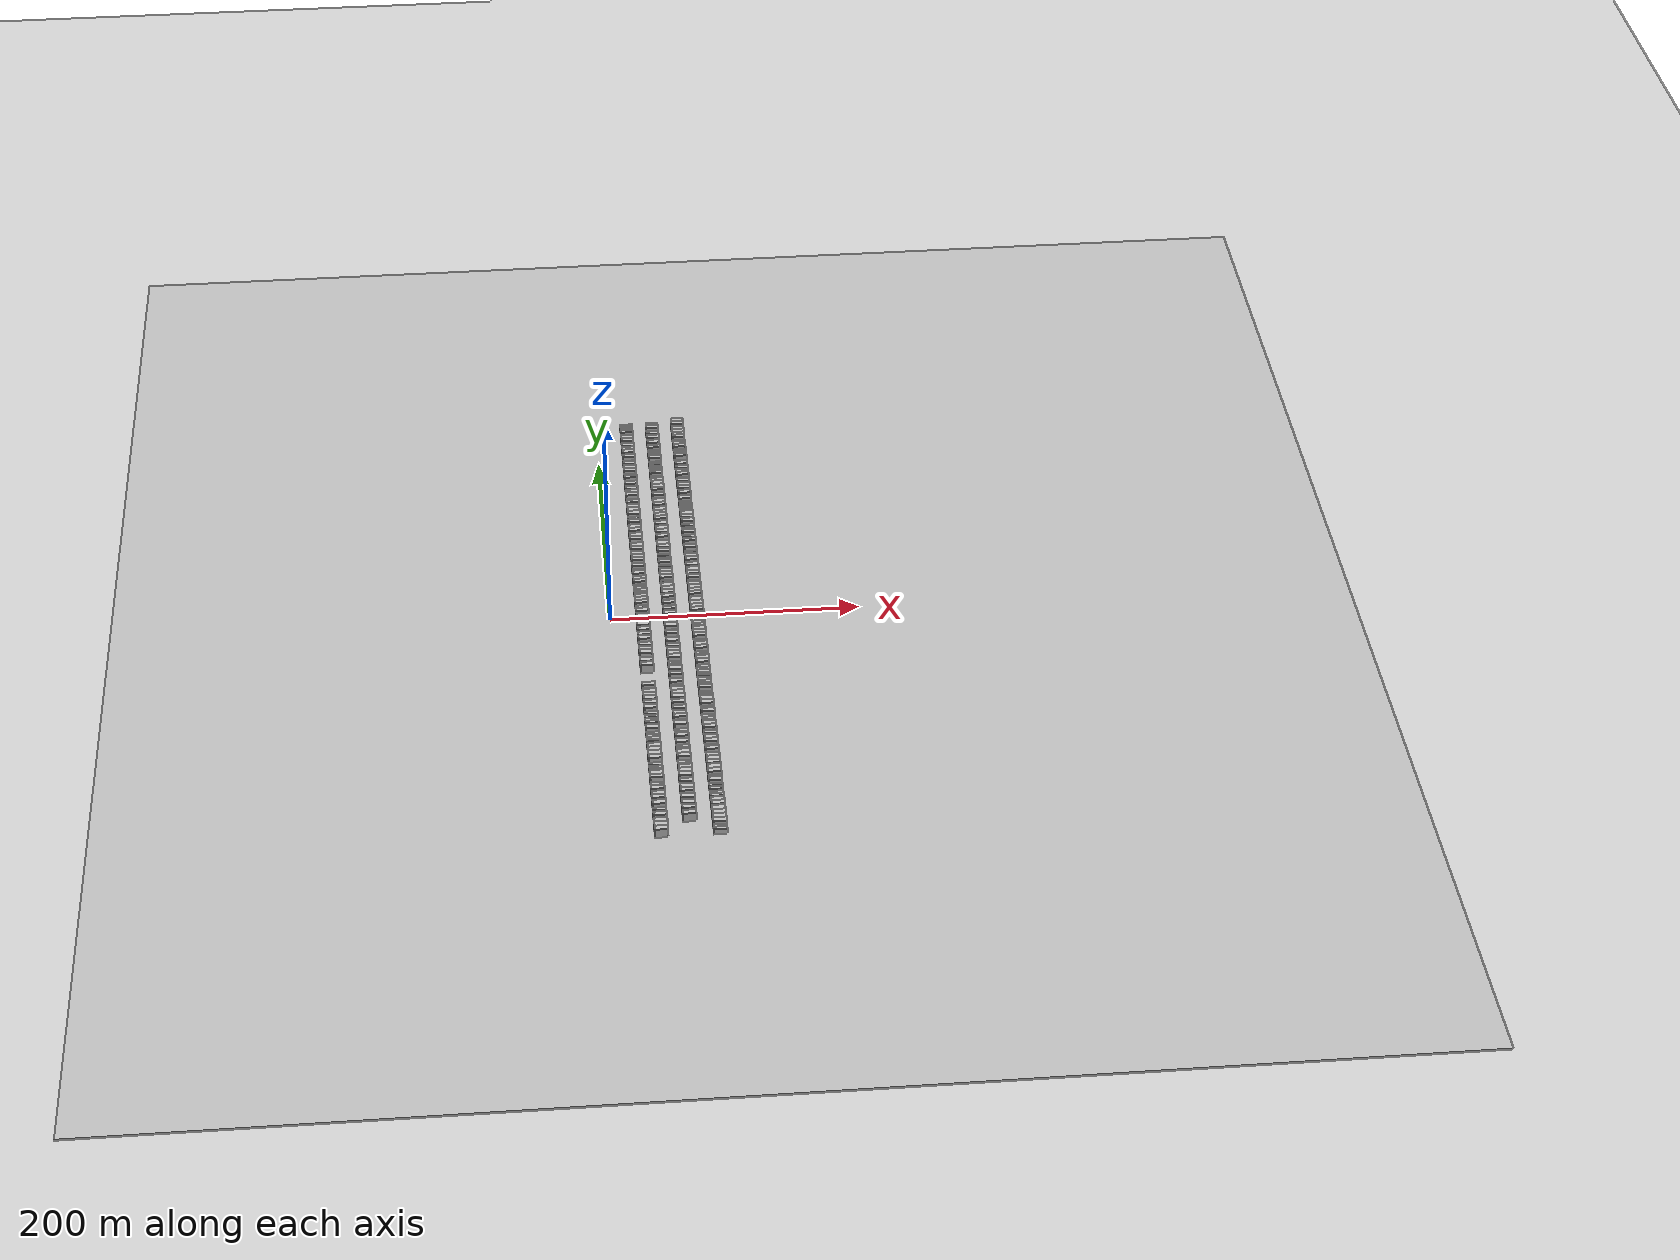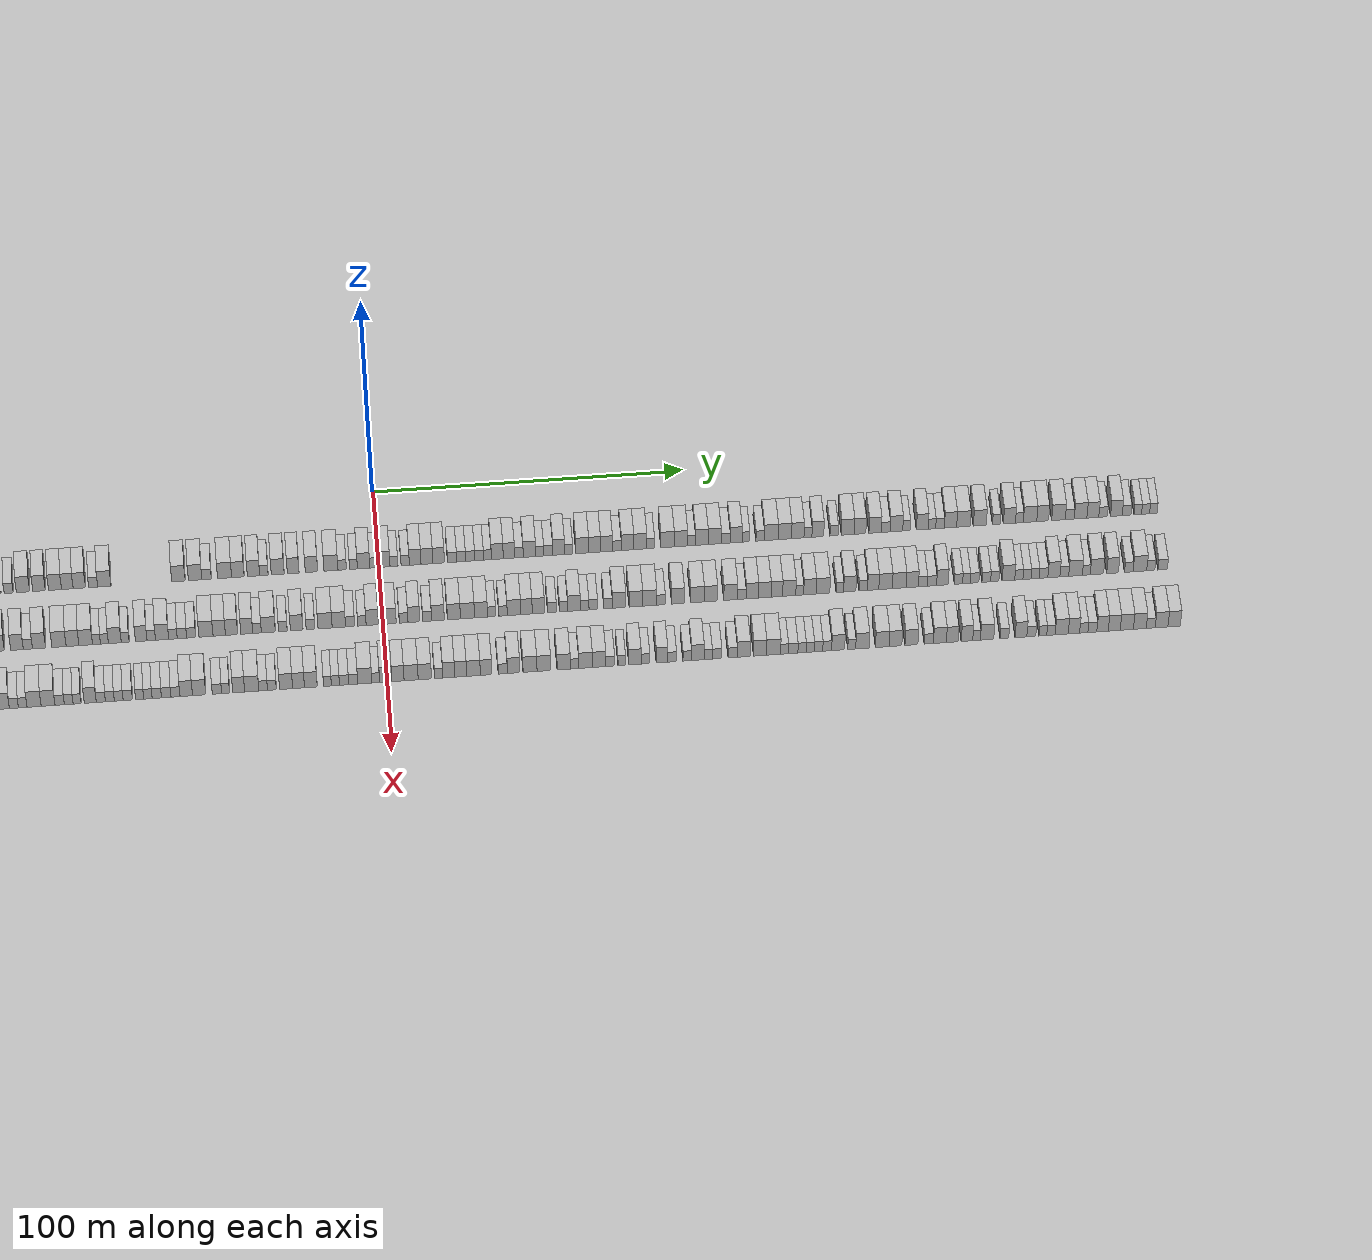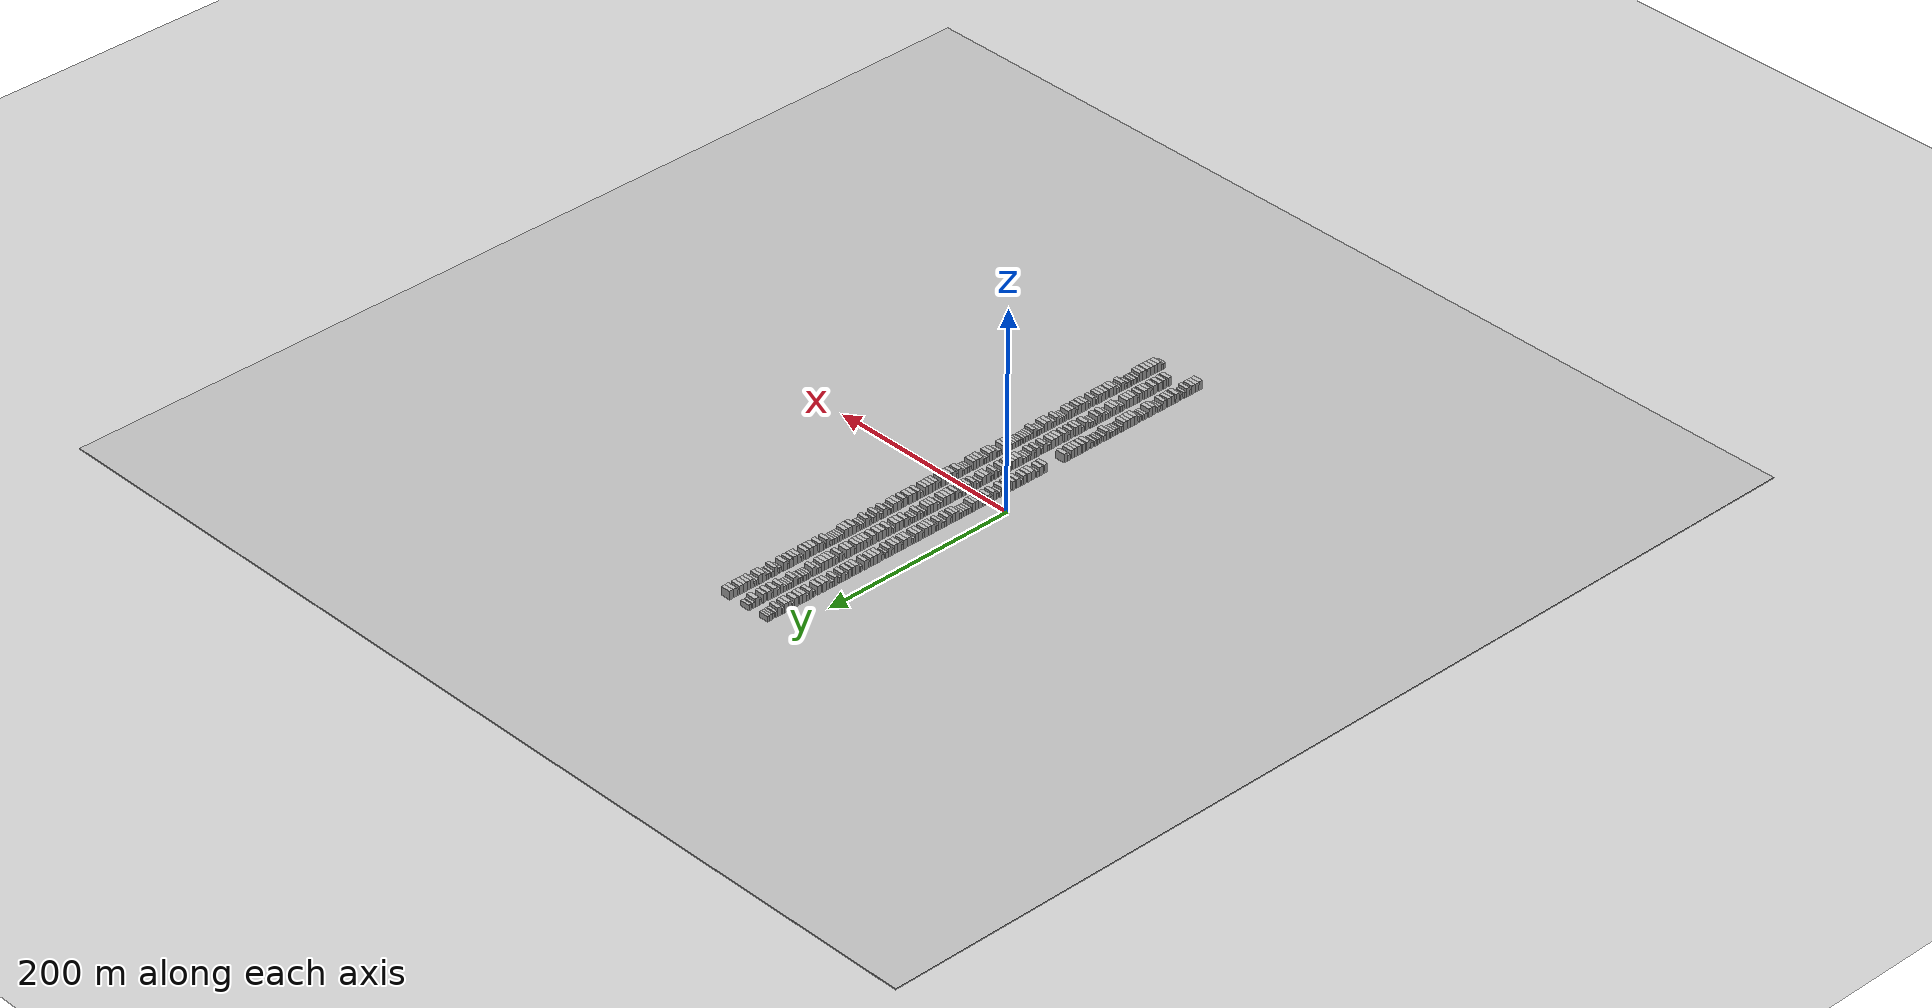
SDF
<?xml version="1.0" encoding="utf-8"?>

<sdf version="1.6">

   <world name="default">

      <gui fullscreen="0">

         <camera name="user_camera">

            <pose>-15 0 4.57585 0 0 0</pose>

            <view_controller>orbit</view_controller>

         </camera>

      </gui>

      <scene>

         <sky>

           <clouds>

             <speed>12</speed>

           </clouds>

         </sky>

         <ambient>0.4 0.4 0.4 1</ambient>

         <background>0.7 0.7 0.7 1</background>

         <shadows>1</shadows>

      </scene>

      <gravity>0 0 -9.8066</gravity>

      <magnetic_field>6e-06 2.3e-05 -4.2e-05</magnetic_field>

      <physics default="0" name="default_physics" type="ode">

         <ode>

            <solver>

               <type>quick</type>

               <iters>10</iters>

               <sor>1.0</sor>

               <use_dynamic_moi_rescaling>0</use_dynamic_moi_rescaling>

            </solver>

            <constraints>

               <cfm>0</cfm>

               <erp>0.2</erp>

               <contact_max_correcting_vel>100</contact_max_correcting_vel>

               <contact_surface_layer>0.001</contact_surface_layer>

            </constraints>

         </ode>

         <max_step_size>0.004</max_step_size>

         <real_time_factor>1</real_time_factor>

         <real_time_update_rate>250</real_time_update_rate>

      </physics>

      <light name="sun" type="directional">

         <cast_shadows>1</cast_shadows>

         <pose>0 0 10 0 0 0</pose>

         <diffuse>0.8 0.8 0.8 1</diffuse>

         <specular>0.2 0.2 0.2 1</specular>

         <attenuation>

            <range>1000</range>

            <constant>0.9</constant>

            <linear>0.01</linear>

            <quadratic>0.001</quadratic>

         </attenuation>

         <direction>-0.5 0.1 -0.9</direction>

      </light>

      <include>

         <name>ground_plane_1</name>

         <uri>model://HANNAS_ground_plane</uri>

         <pose>0 0 0  0 0 0</pose>

      </include>

      <include>

         <name>ground_plane_2</name>

         <uri>model://HANNAS_ground_plane</uri>

         <pose>100 0 0  0 0 0</pose>

      </include>

      <model name="building_1">

         <static>1</static>

         <pose frame="">25.0000 -245.8215 0 0.000000 0.000000 0.000000</pose>

         <link name="link">

            <pose frame="">0 0 4.50 0 0 0</pose>

            <collision name="collision">

               <geometry>

                  <box>

                     <size>10.0000 4.3570 9.0000</size>

                  </box>

               </geometry>

               <max_contacts>10</max_contacts>

               <surface>

                  <contact>

                     <ode/>

                  </contact>

                  <bounce/>

                  <friction>

                     <torsional>

                        <ode/>

                     </torsional>

                     <ode/>

                  </friction>

               </surface>

            </collision>

            <visual name="visual">

               <cast_shadows>0</cast_shadows>

               <geometry>

                  <box>

                     <size>10.0000 4.3570 9.0000</size>

                  </box>

               </geometry>

               <material>

                  <script>

                     <uri>model://HANNAS_wall/materials/scripts</uri>

                     <uri>model://HANNAS_wall/materials/textures</uri>

                     <name>vrc/HANNAS_wall</name>

                  </script>

               </material>

            </visual>

            <self_collide>0</self_collide>

            <enable_wind>0</enable_wind>

            <kinematic>0</kinematic>

         </link>

      </model>

      <model name="building_2">

         <static>1</static>

         <pose frame="">25.0000 -241.4256 0 0.000000 0.000000 0.000000</pose>

         <link name="link">

            <pose frame="">0 0 4.50 0 0 0</pose>

            <collision name="collision">

               <geometry>

                  <box>

                     <size>10.0000 4.4348 9.0000</size>

                  </box>

               </geometry>

               <max_contacts>10</max_contacts>

               <surface>

                  <contact>

                     <ode/>

                  </contact>

                  <bounce/>

                  <friction>

                     <torsional>

                        <ode/>

                     </torsional>

                     <ode/>

                  </friction>

               </surface>

            </collision>

            <visual name="visual">

               <cast_shadows>0</cast_shadows>

               <geometry>

                  <box>

                     <size>10.0000 4.4348 9.0000</size>

                  </box>

               </geometry>

               <material>

                  <script>

                     <uri>model://HANNAS_wall/materials/scripts</uri>

                     <uri>model://HANNAS_wall/materials/textures</uri>

                     <name>vrc/HANNAS_wall</name>

                  </script>

               </material>

            </visual>

            <self_collide>0</self_collide>

            <enable_wind>0</enable_wind>

            <kinematic>0</kinematic>

         </link>

      </model>

      <model name="building_3">

         <static>1</static>

         <pose frame="">25.0000 -237.2090 0 0.000000 0.000000 0.000000</pose>

         <link name="link">

            <pose frame="">0 0 4.50 0 0 0</pose>

            <collision name="collision">

               <geometry>

                  <box>

                     <size>10.0000 3.9985 9.0000</size>

                  </box>

               </geometry>

               <max_contacts>10</max_contacts>

               <surface>

                  <contact>

                     <ode/>

                  </contact>

                  <bounce/>

                  <friction>

                     <torsional>

                        <ode/>

                     </torsional>

                     <ode/>

                  </friction>

               </surface>

            </collision>

            <visual name="visual">

               <cast_shadows>0</cast_shadows>

               <geometry>

                  <box>

                     <size>10.0000 3.9985 9.0000</size>

                  </box>

               </geometry>

               <material>

                  <script>

                     <uri>model://HANNAS_wall/materials/scripts</uri>

                     <uri>model://HANNAS_wall/materials/textures</uri>

                     <name>vrc/HANNAS_wall</name>

                  </script>

               </material>

            </visual>

            <self_collide>0</self_collide>

            <enable_wind>0</enable_wind>

            <kinematic>0</kinematic>

         </link>

      </model>

      <model name="building_4">

         <static>1</static>

         <pose frame="">25.0000 -233.9132 0 0.000000 0.000000 0.000000</pose>

         <link name="link">

            <pose frame="">0 0 3.00 0 0 0</pose>

            <collision name="collision">

               <geometry>

                  <box>

                     <size>10.0000 2.5930 6.0000</size>

                  </box>

               </geometry>

               <max_contacts>10</max_contacts>

               <surface>

                  <contact>

                     <ode/>

                  </contact>

                  <bounce/>

                  <friction>

                     <torsional>

                        <ode/>

                     </torsional>

                     <ode/>

                  </friction>

               </surface>

            </collision>

            <visual name="visual">

               <cast_shadows>0</cast_shadows>

               <geometry>

                  <box>

                     <size>10.0000 2.5930 6.0000</size>

                  </box>

               </geometry>

               <material>

                  <script>

                     <uri>model://HANNAS_wall/materials/scripts</uri>

                     <uri>model://HANNAS_wall/materials/textures</uri>

                     <name>vrc/HANNAS_wall</name>

                  </script>

               </material>

            </visual>

            <self_collide>0</self_collide>

            <enable_wind>0</enable_wind>

            <kinematic>0</kinematic>

         </link>

      </model>

      <model name="building_5">

         <static>1</static>

         <pose frame="">25.0000 -230.7434 0 0.000000 0.000000 0.000000</pose>

         <link name="link">

            <pose frame="">0 0 4.50 0 0 0</pose>

            <collision name="collision">

               <geometry>

                  <box>

                     <size>10.0000 3.7467 9.0000</size>

                  </box>

               </geometry>

               <max_contacts>10</max_contacts>

               <surface>

                  <contact>

                     <ode/>

                  </contact>

                  <bounce/>

                  <friction>

                     <torsional>

                        <ode/>

                     </torsional>

                     <ode/>

                  </friction>

               </surface>

            </collision>

            <visual name="visual">

               <cast_shadows>0</cast_shadows>

               <geometry>

                  <box>

                     <size>10.0000 3.7467 9.0000</size>

                  </box>

               </geometry>

               <material>

                  <script>

                     <uri>model://HANNAS_wall/materials/scripts</uri>

                     <uri>model://HANNAS_wall/materials/textures</uri>

                     <name>vrc/HANNAS_wall</name>

                  </script>

               </material>

            </visual>

            <self_collide>0</self_collide>

            <enable_wind>0</enable_wind>

            <kinematic>0</kinematic>

         </link>

      </model>

      <model name="building_6">

         <static>1</static>

         <pose frame="">25.0000 -227.5806 0 0.000000 0.000000 0.000000</pose>

         <link name="link">

            <pose frame="">0 0 3.00 0 0 0</pose>

            <collision name="collision">

               <geometry>

                  <box>

                     <size>10.0000 2.5790 6.0000</size>

                  </box>

               </geometry>

               <max_contacts>10</max_contacts>

               <surface>

                  <contact>

                     <ode/>

                  </contact>

                  <bounce/>

                  <friction>

                     <torsional>

                        <ode/>

                     </torsional>

                     <ode/>

                  </friction>

               </surface>

            </collision>

            <visual name="visual">

               <cast_shadows>0</cast_shadows>

               <geometry>

                  <box>

                     <size>10.0000 2.5790 6.0000</size>

                  </box>

               </geometry>

               <material>

                  <script>

                     <uri>model://HANNAS_wall/materials/scripts</uri>

                     <uri>model://HANNAS_wall/materials/textures</uri>

                     <name>vrc/HANNAS_wall</name>

                  </script>

               </material>

            </visual>

            <self_collide>0</self_collide>

            <enable_wind>0</enable_wind>

            <kinematic>0</kinematic>

         </link>

      </model>

      <model name="building_7">

         <static>1</static>

         <pose frame="">25.0000 -222.9934 0 0.000000 0.000000 0.000000</pose>

         <link name="link">

            <pose frame="">0 0 3.00 0 0 0</pose>

            <collision name="collision">

               <geometry>

                  <box>

                     <size>10.0000 2.5954 6.0000</size>

                  </box>

               </geometry>

               <max_contacts>10</max_contacts>

               <surface>

                  <contact>

                     <ode/>

                  </contact>

                  <bounce/>

                  <friction>

                     <torsional>

                        <ode/>

                     </torsional>

                     <ode/>

                  </friction>

               </surface>

            </collision>

            <visual name="visual">

               <cast_shadows>0</cast_shadows>

               <geometry>

                  <box>

                     <size>10.0000 2.5954 6.0000</size>

                  </box>

               </geometry>

               <material>

                  <script>

                     <uri>model://HANNAS_wall/materials/scripts</uri>

                     <uri>model://HANNAS_wall/materials/textures</uri>

                     <name>vrc/HANNAS_wall</name>

                  </script>

               </material>

            </visual>

            <self_collide>0</self_collide>

            <enable_wind>0</enable_wind>

            <kinematic>0</kinematic>

         </link>

      </model>

      <model name="building_8">

         <static>1</static>

         <pose frame="">25.0000 -218.4736 0 0.000000 0.000000 0.000000</pose>

         <link name="link">

            <pose frame="">0 0 4.50 0 0 0</pose>

            <collision name="collision">

               <geometry>

                  <box>

                     <size>10.0000 4.4441 9.0000</size>

                  </box>

               </geometry>

               <max_contacts>10</max_contacts>

               <surface>

                  <contact>

                     <ode/>

                  </contact>

                  <bounce/>

                  <friction>

                     <torsional>

                        <ode/>

                     </torsional>

                     <ode/>

                  </friction>

               </surface>

            </collision>

            <visual name="visual">

               <cast_shadows>0</cast_shadows>

               <geometry>

                  <box>

                     <size>10.0000 4.4441 9.0000</size>

                  </box>

               </geometry>

               <material>

                  <script>

                     <uri>model://HANNAS_wall/materials/scripts</uri>

                     <uri>model://HANNAS_wall/materials/textures</uri>

                     <name>vrc/HANNAS_wall</name>

                  </script>

               </material>

            </visual>

            <self_collide>0</self_collide>

            <enable_wind>0</enable_wind>

            <kinematic>0</kinematic>

         </link>

      </model>

      <model name="building_9">

         <static>1</static>

         <pose frame="">25.0000 -212.4224 0 0.000000 0.000000 0.000000</pose>

         <link name="link">

            <pose frame="">0 0 4.50 0 0 0</pose>

            <collision name="collision">

               <geometry>

                  <box>

                     <size>10.0000 3.6583 9.0000</size>

                  </box>

               </geometry>

               <max_contacts>10</max_contacts>

               <surface>

                  <contact>

                     <ode/>

                  </contact>

                  <bounce/>

                  <friction>

                     <torsional>

                        <ode/>

                     </torsional>

                     <ode/>

                  </friction>

               </surface>

            </collision>

            <visual name="visual">

               <cast_shadows>0</cast_shadows>

               <geometry>

                  <box>

                     <size>10.0000 3.6583 9.0000</size>

                  </box>

               </geometry>

               <material>

                  <script>

                     <uri>model://HANNAS_wall/materials/scripts</uri>

                     <uri>model://HANNAS_wall/materials/textures</uri>

                     <name>vrc/HANNAS_wall</name>

                  </script>

               </material>

            </visual>

            <self_collide>0</self_collide>

            <enable_wind>0</enable_wind>

            <kinematic>0</kinematic>

         </link>

      </model>

      <model name="building_10">

         <static>1</static>

         <pose frame="">25.0000 -208.6044 0 0.000000 0.000000 0.000000</pose>

         <link name="link">

            <pose frame="">0 0 4.50 0 0 0</pose>

            <collision name="collision">

               <geometry>

                  <box>

                     <size>10.0000 3.9778 9.0000</size>

                  </box>

               </geometry>

               <max_contacts>10</max_contacts>

               <surface>

                  <contact>

                     <ode/>

                  </contact>

                  <bounce/>

                  <friction>

                     <torsional>

                        <ode/>

                     </torsional>

                     <ode/>

                  </friction>

               </surface>

            </collision>

            <visual name="visual">

               <cast_shadows>0</cast_shadows>

               <geometry>

                  <box>

                     <size>10.0000 3.9778 9.0000</size>

                  </box>

               </geometry>

               <material>

                  <script>

                     <uri>model://HANNAS_wall/materials/scripts</uri>

                     <uri>model://HANNAS_wall/materials/textures</uri>

                     <name>vrc/HANNAS_wall</name>

                  </script>

               </material>

            </visual>

            <self_collide>0</self_collide>

            <enable_wind>0</enable_wind>

            <kinematic>0</kinematic>

         </link>

      </model>

      <model name="building_11">

         <static>1</static>

         <pose frame="">25.0000 -202.6700 0 0.000000 0.000000 0.000000</pose>

         <link name="link">

            <pose frame="">0 0 4.50 0 0 0</pose>

            <collision name="collision">

               <geometry>

                  <box>

                     <size>10.0000 3.8910 9.0000</size>

                  </box>

               </geometry>

               <max_contacts>10</max_contacts>

               <surface>

                  <contact>

                     <ode/>

                  </contact>

                  <bounce/>

                  <friction>

                     <torsional>

                        <ode/>

                     </torsional>

                     <ode/>

                  </friction>

               </surface>

            </collision>

            <visual name="visual">

               <cast_shadows>0</cast_shadows>

               <geometry>

                  <box>

                     <size>10.0000 3.8910 9.0000</size>

                  </box>

               </geometry>

               <material>

                  <script>

                     <uri>model://HANNAS_wall/materials/scripts</uri>

                     <uri>model://HANNAS_wall/materials/textures</uri>

                     <name>vrc/HANNAS_wall</name>

                  </script>

               </material>

            </visual>

            <self_collide>0</self_collide>

            <enable_wind>0</enable_wind>

            <kinematic>0</kinematic>

         </link>

      </model>

      <model name="building_12">

         <static>1</static>

         <pose frame="">25.0000 -198.5001 0 0.000000 0.000000 0.000000</pose>

         <link name="link">

            <pose frame="">0 0 3.00 0 0 0</pose>

            <collision name="collision">

               <geometry>

                  <box>

                     <size>10.0000 2.4487 6.0000</size>

                  </box>

               </geometry>

               <max_contacts>10</max_contacts>

               <surface>

                  <contact>

                     <ode/>

                  </contact>

                  <bounce/>

                  <friction>

                     <torsional>

                        <ode/>

                     </torsional>

                     <ode/>

                  </friction>

               </surface>

            </collision>

            <visual name="visual">

               <cast_shadows>0</cast_shadows>

               <geometry>

                  <box>

                     <size>10.0000 2.4487 6.0000</size>

                  </box>

               </geometry>

               <material>

                  <script>

                     <uri>model://HANNAS_wall/materials/scripts</uri>

                     <uri>model://HANNAS_wall/materials/textures</uri>

                     <name>vrc/HANNAS_wall</name>

                  </script>

               </material>

            </visual>

            <self_collide>0</self_collide>

            <enable_wind>0</enable_wind>

            <kinematic>0</kinematic>

         </link>

      </model>

      <model name="building_13">

         <static>1</static>

         <pose frame="">25.0000 -195.7858 0 0.000000 0.000000 0.000000</pose>

         <link name="link">

            <pose frame="">0 0 3.00 0 0 0</pose>

            <collision name="collision">

               <geometry>

                  <box>

                     <size>10.0000 2.9799 6.0000</size>

                  </box>

               </geometry>

               <max_contacts>10</max_contacts>

               <surface>

                  <contact>

                     <ode/>

                  </contact>

                  <bounce/>

                  <friction>

                     <torsional>

                        <ode/>

                     </torsional>

                     <ode/>

                  </friction>

               </surface>

            </collision>

            <visual name="visual">

               <cast_shadows>0</cast_shadows>

               <geometry>

                  <box>

                     <size>10.0000 2.9799 6.0000</size>

                  </box>

               </geometry>

               <material>

                  <script>

                     <uri>model://HANNAS_wall/materials/scripts</uri>

                     <uri>model://HANNAS_wall/materials/textures</uri>

                     <name>vrc/HANNAS_wall</name>

                  </script>

               </material>

            </visual>

            <self_collide>0</self_collide>

            <enable_wind>0</enable_wind>

            <kinematic>0</kinematic>

         </link>

      </model>

      <model name="building_14">

         <static>1</static>

         <pose frame="">25.0000 -190.4258 0 0.000000 0.000000 0.000000</pose>

         <link name="link">

            <pose frame="">0 0 4.50 0 0 0</pose>

            <collision name="collision">

               <geometry>

                  <box>

                     <size>10.0000 3.7402 9.0000</size>

                  </box>

               </geometry>

               <max_contacts>10</max_contacts>

               <surface>

                  <contact>

                     <ode/>

                  </contact>

                  <bounce/>

                  <friction>

                     <torsional>

                        <ode/>

                     </torsional>

                     <ode/>

                  </friction>

               </surface>

            </collision>

            <visual name="visual">

               <cast_shadows>0</cast_shadows>

               <geometry>

                  <box>

                     <size>10.0000 3.7402 9.0000</size>

                  </box>

               </geometry>

               <material>

                  <script>

                     <uri>model://HANNAS_wall/materials/scripts</uri>

                     <uri>model://HANNAS_wall/materials/textures</uri>

                     <name>vrc/HANNAS_wall</name>

                  </script>

               </material>

            </visual>

            <self_collide>0</self_collide>

            <enable_wind>0</enable_wind>

            <kinematic>0</kinematic>

         </link>

      </model>

      <model name="building_15">

         <static>1</static>

         <pose frame="">25.0000 -186.3539 0 0.000000 0.000000 0.000000</pose>

         <link name="link">

            <pose frame="">0 0 4.50 0 0 0</pose>

            <collision name="collision">

               <geometry>

                  <box>

                     <size>10.0000 4.4036 9.0000</size>

                  </box>

               </geometry>

               <max_contacts>10</max_contacts>

               <surface>

                  <contact>

                     <ode/>

                  </contact>

                  <bounce/>

                  <friction>

                     <torsional>

                        <ode/>

                     </torsional>

                     <ode/>

                  </friction>

               </surface>

            </collision>

            <visual name="visual">

               <cast_shadows>0</cast_shadows>

               <geometry>

                  <box>

                     <size>10.0000 4.4036 9.0000</size>

                  </box>

               </geometry>

               <material>

                  <script>

                     <uri>model://HANNAS_wall/materials/scripts</uri>

                     <uri>model://HANNAS_wall/materials/textures</uri>

                     <name>vrc/HANNAS_wall</name>

                  </script>

               </material>

            </visual>

            <self_collide>0</self_collide>

            <enable_wind>0</enable_wind>

            <kinematic>0</kinematic>

         </link>

      </model>

      <model name="building_16">

         <static>1</static>

         <pose frame="">25.0000 -180.6609 0 0.000000 0.000000 0.000000</pose>

         <link name="link">

            <pose frame="">0 0 3.00 0 0 0</pose>

            <collision name="collision">

               <geometry>

                  <box>

                     <size>10.0000 2.9824 6.0000</size>

                  </box>

               </geometry>

               <max_contacts>10</max_contacts>

               <surface>

                  <contact>

                     <ode/>

                  </contact>

                  <bounce/>

                  <friction>

                     <torsional>

                        <ode/>

                     </torsional>

                     <ode/>

                  </friction>

               </surface>

            </collision>

            <visual name="visual">

               <cast_shadows>0</cast_shadows>

               <geometry>

                  <box>

                     <size>10.0000 2.9824 6.0000</size>

                  </box>

               </geometry>

               <material>

                  <script>

                     <uri>model://HANNAS_wall/materials/scripts</uri>

                     <uri>model://HANNAS_wall/materials/textures</uri>

                     <name>vrc/HANNAS_wall</name>

                  </script>

               </material>

            </visual>

            <self_collide>0</self_collide>

            <enable_wind>0</enable_wind>

            <kinematic>0</kinematic>

         </link>

      </model>

      <model name="building_17">

         <static>1</static>

         <pose frame="">25.0000 -177.9224 0 0.000000 0.000000 0.000000</pose>

         <link name="link">

            <pose frame="">0 0 3.00 0 0 0</pose>

            <collision name="collision">

               <geometry>

                  <box>

                     <size>10.0000 2.4946 6.0000</size>

                  </box>

               </geometry>

               <max_contacts>10</max_contacts>

               <surface>

                  <contact>

                     <ode/>

                  </contact>

                  <bounce/>

                  <friction>

                     <torsional>

                        <ode/>

                     </torsional>

                     <ode/>

                  </friction>

               </surface>

            </collision>

            <visual name="visual">

               <cast_shadows>0</cast_shadows>

               <geometry>

                  <box>

                     <size>10.0000 2.4946 6.0000</size>

                  </box>

               </geometry>

               <material>

                  <script>

                     <uri>model://HANNAS_wall/materials/scripts</uri>

                     <uri>model://HANNAS_wall/materials/textures</uri>

                     <name>vrc/HANNAS_wall</name>

                  </script>

               </material>

            </visual>

            <self_collide>0</self_collide>

            <enable_wind>0</enable_wind>

            <kinematic>0</kinematic>

         </link>

      </model>

      <model name="building_18">

         <static>1</static>

         <pose frame="">25.0000 -174.3365 0 0.000000 0.000000 0.000000</pose>

         <link name="link">

            <pose frame="">0 0 3.00 0 0 0</pose>

            <collision name="collision">

               <geometry>

                  <box>

                     <size>10.0000 2.6771 6.0000</size>

                  </box>

               </geometry>

               <max_contacts>10</max_contacts>

               <surface>

                  <contact>

                     <ode/>

                  </contact>

                  <bounce/>

                  <friction>

                     <torsional>

                        <ode/>

                     </torsional>

                     <ode/>

                  </friction>

               </surface>

            </collision>

            <visual name="visual">

               <cast_shadows>0</cast_shadows>

               <geometry>

                  <box>

                     <size>10.0000 2.6771 6.0000</size>

                  </box>

               </geometry>

               <material>

                  <script>

                     <uri>model://HANNAS_wall/materials/scripts</uri>

                     <uri>model://HANNAS_wall/materials/textures</uri>

                     <name>vrc/HANNAS_wall</name>

                  </script>

               </material>

            </visual>

            <self_collide>0</self_collide>

            <enable_wind>0</enable_wind>

            <kinematic>0</kinematic>

         </link>

      </model>

      <model name="building_19">

         <static>1</static>

         <pose frame="">25.0000 -168.8597 0 0.000000 0.000000 0.000000</pose>

         <link name="link">

            <pose frame="">0 0 4.50 0 0 0</pose>

            <collision name="collision">

               <geometry>

                  <box>

                     <size>10.0000 4.2764 9.0000</size>

                  </box>

               </geometry>

               <max_contacts>10</max_contacts>

               <surface>

                  <contact>

                     <ode/>

                  </contact>

                  <bounce/>

                  <friction>

                     <torsional>

                        <ode/>

                     </torsional>

                     <ode/>

                  </friction>

               </surface>

            </collision>

            <visual name="visual">

               <cast_shadows>0</cast_shadows>

               <geometry>

                  <box>

                     <size>10.0000 4.2764 9.0000</size>

                  </box>

               </geometry>

               <material>

                  <script>

                     <uri>model://HANNAS_wall/materials/scripts</uri>

                     <uri>model://HANNAS_wall/materials/textures</uri>

                     <name>vrc/HANNAS_wall</name>

                  </script>

               </material>

            </visual>

            <self_collide>0</self_collide>

            <enable_wind>0</enable_wind>

            <kinematic>0</kinematic>

         </link>

      </model>

      <model name="building_20">

         <static>1</static>

         <pose frame="">25.0000 -164.4716 0 0.000000 0.000000 0.000000</pose>

         <link name="link">

            <pose frame="">0 0 4.50 0 0 0</pose>

            <collision name="collision">

               <geometry>

                  <box>

                     <size>10.0000 4.4997 9.0000</size>

                  </box>

               </geometry>

               <max_contacts>10</max_contacts>

               <surface>

                  <contact>

                     <ode/>

                  </contact>

                  <bounce/>

                  <friction>

                     <torsional>

                        <ode/>

                     </torsional>

                     <ode/>

                  </friction>

               </surface>

            </collision>

            <visual name="visual">

               <cast_shadows>0</cast_shadows>

               <geometry>

                  <box>

                     <size>10.0000 4.4997 9.0000</size>

                  </box>

               </geometry>

               <material>

                  <script>

                     <uri>model://HANNAS_wall/materials/scripts</uri>

                     <uri>model://HANNAS_wall/materials/textures</uri>

                     <name>vrc/HANNAS_wall</name>

                  </script>

               </material>

            </visual>

            <self_collide>0</self_collide>

            <enable_wind>0</enable_wind>

            <kinematic>0</kinematic>

         </link>

      </model>

      <model name="building_21">

         <static>1</static>

         <pose frame="">25.0000 -160.2888 0 0.000000 0.000000 0.000000</pose>

         <link name="link">

            <pose frame="">0 0 4.50 0 0 0</pose>

            <collision name="collision">

               <geometry>

                  <box>

                     <size>10.0000 3.8659 9.0000</size>

                  </box>

               </geometry>

               <max_contacts>10</max_contacts>

               <surface>

                  <contact>

                     <ode/>

                  </contact>

                  <bounce/>

                  <friction>

                     <torsional>

                        <ode/>

                     </torsional>

                     <ode/>

                  </friction>

               </surface>

            </collision>

            <visual name="visual">

               <cast_shadows>0</cast_shadows>

               <geometry>

                  <box>

                     <size>10.0000 3.8659 9.0000</size>

                  </box>

               </geometry>

               <material>

                  <script>

                     <uri>model://HANNAS_wall/materials/scripts</uri>

                     <uri>model://HANNAS_wall/materials/textures</uri>

                     <name>vrc/HANNAS_wall</name>

                  </script>

               </material>

            </visual>

            <self_collide>0</self_collide>

            <enable_wind>0</enable_wind>

            <kinematic>0</kinematic>

         </link>

      </model>

      <model name="building_22">

         <static>1</static>

         <pose frame="">25.0000 -156.2801 0 0.000000 0.000000 0.000000</pose>

         <link name="link">

            <pose frame="">0 0 4.50 0 0 0</pose>

            <collision name="collision">

               <geometry>

                  <box>

                     <size>10.0000 4.1516 9.0000</size>

                  </box>

               </geometry>

               <max_contacts>10</max_contacts>

               <surface>

                  <contact>

                     <ode/>

                  </contact>

                  <bounce/>

                  <friction>

                     <torsional>

                        <ode/>

                     </torsional>

                     <ode/>

                  </friction>

               </surface>

            </collision>

            <visual name="visual">

               <cast_shadows>0</cast_shadows>

               <geometry>

                  <box>

                     <size>10.0000 4.1516 9.0000</size>

                  </box>

               </geometry>

               <material>

                  <script>

                     <uri>model://HANNAS_wall/materials/scripts</uri>

                     <uri>model://HANNAS_wall/materials/textures</uri>

                     <name>vrc/HANNAS_wall</name>

                  </script>

               </material>

            </visual>

            <self_collide>0</self_collide>

            <enable_wind>0</enable_wind>

            <kinematic>0</kinematic>

         </link>

      </model>

      <model name="building_23">

         <static>1</static>

         <pose frame="">25.0000 -152.8687 0 0.000000 0.000000 0.000000</pose>

         <link name="link">

            <pose frame="">0 0 3.00 0 0 0</pose>

            <collision name="collision">

               <geometry>

                  <box>

                     <size>10.0000 2.6712 6.0000</size>

                  </box>

               </geometry>

               <max_contacts>10</max_contacts>

               <surface>

                  <contact>

                     <ode/>

                  </contact>

                  <bounce/>

                  <friction>

                     <torsional>

                        <ode/>

                     </torsional>

                     <ode/>

                  </friction>

               </surface>

            </collision>

            <visual name="visual">

               <cast_shadows>0</cast_shadows>

               <geometry>

                  <box>

                     <size>10.0000 2.6712 6.0000</size>

                  </box>

               </geometry>

               <material>

                  <script>

                     <uri>model://HANNAS_wall/materials/scripts</uri>

                     <uri>model://HANNAS_wall/materials/textures</uri>

                     <name>vrc/HANNAS_wall</name>

                  </script>

               </material>

            </visual>

            <self_collide>0</self_collide>

            <enable_wind>0</enable_wind>

            <kinematic>0</kinematic>

         </link>

      </model>

      <model name="building_24">

         <static>1</static>

         <pose frame="">25.0000 -148.2461 0 0.000000 0.000000 0.000000</pose>

         <link name="link">

            <pose frame="">0 0 3.00 0 0 0</pose>

            <collision name="collision">

               <geometry>

                  <box>

                     <size>10.0000 2.5739 6.0000</size>

                  </box>

               </geometry>

               <max_contacts>10</max_contacts>

               <surface>

                  <contact>

                     <ode/>

                  </contact>

                  <bounce/>

                  <friction>

                     <torsional>

                        <ode/>

                     </torsional>

                     <ode/>

                  </friction>

               </surface>

            </collision>

            <visual name="visual">

               <cast_shadows>0</cast_shadows>

               <geometry>

                  <box>

                     <size>10.0000 2.5739 6.0000</size>

                  </box>

               </geometry>

               <material>

                  <script>

                     <uri>model://HANNAS_wall/materials/scripts</uri>

                     <uri>model://HANNAS_wall/materials/textures</uri>

                     <name>vrc/HANNAS_wall</name>

                  </script>

               </material>

            </visual>

            <self_collide>0</self_collide>

            <enable_wind>0</enable_wind>

            <kinematic>0</kinematic>

         </link>

      </model>

      <model name="building_25">

         <static>1</static>

         <pose frame="">25.0000 -145.6053 0 0.000000 0.000000 0.000000</pose>

         <link name="link">

            <pose frame="">0 0 3.00 0 0 0</pose>

            <collision name="collision">

               <geometry>

                  <box>

                     <size>10.0000 2.7077 6.0000</size>

                  </box>

               </geometry>

               <max_contacts>10</max_contacts>

               <surface>

                  <contact>

                     <ode/>

                  </contact>

                  <bounce/>

                  <friction>

                     <torsional>

                        <ode/>

                     </torsional>

                     <ode/>

                  </friction>

               </surface>

            </collision>

            <visual name="visual">

               <cast_shadows>0</cast_shadows>

               <geometry>

                  <box>

                     <size>10.0000 2.7077 6.0000</size>

                  </box>

               </geometry>

               <material>

                  <script>

                     <uri>model://HANNAS_wall/materials/scripts</uri>

                     <uri>model://HANNAS_wall/materials/textures</uri>

                     <name>vrc/HANNAS_wall</name>

                  </script>

               </material>

            </visual>

            <self_collide>0</self_collide>

            <enable_wind>0</enable_wind>

            <kinematic>0</kinematic>

         </link>

      </model>

      <model name="building_26">

         <static>1</static>

         <pose frame="">25.0000 -142.8159 0 0.000000 0.000000 0.000000</pose>

         <link name="link">

            <pose frame="">0 0 3.00 0 0 0</pose>

            <collision name="collision">

               <geometry>

                  <box>

                     <size>10.0000 2.8712 6.0000</size>

                  </box>

               </geometry>

               <max_contacts>10</max_contacts>

               <surface>

                  <contact>

                     <ode/>

                  </contact>

                  <bounce/>

                  <friction>

                     <torsional>

                        <ode/>

                     </torsional>

                     <ode/>

                  </friction>

               </surface>

            </collision>

            <visual name="visual">

               <cast_shadows>0</cast_shadows>

               <geometry>

                  <box>

                     <size>10.0000 2.8712 6.0000</size>

                  </box>

               </geometry>

               <material>

                  <script>

                     <uri>model://HANNAS_wall/materials/scripts</uri>

                     <uri>model://HANNAS_wall/materials/textures</uri>

                     <name>vrc/HANNAS_wall</name>

                  </script>

               </material>

            </visual>

            <self_collide>0</self_collide>

            <enable_wind>0</enable_wind>

            <kinematic>0</kinematic>

         </link>

      </model>

      <model name="building_27">

         <static>1</static>

         <pose frame="">25.0000 -140.1075 0 0.000000 0.000000 0.000000</pose>

         <link name="link">

            <pose frame="">0 0 3.00 0 0 0</pose>

            <collision name="collision">

               <geometry>

                  <box>

                     <size>10.0000 2.5455 6.0000</size>

                  </box>

               </geometry>

               <max_contacts>10</max_contacts>

               <surface>

                  <contact>

                     <ode/>

                  </contact>

                  <bounce/>

                  <friction>

                     <torsional>

                        <ode/>

                     </torsional>

                     <ode/>

                  </friction>

               </surface>

            </collision>

            <visual name="visual">

               <cast_shadows>0</cast_shadows>

               <geometry>

                  <box>

                     <size>10.0000 2.5455 6.0000</size>

                  </box>

               </geometry>

               <material>

                  <script>

                     <uri>model://HANNAS_wall/materials/scripts</uri>

                     <uri>model://HANNAS_wall/materials/textures</uri>

                     <name>vrc/HANNAS_wall</name>

                  </script>

               </material>

            </visual>

            <self_collide>0</self_collide>

            <enable_wind>0</enable_wind>

            <kinematic>0</kinematic>

         </link>

      </model>

      <model name="building_28">

         <static>1</static>

         <pose frame="">25.0000 -135.7602 0 0.000000 0.000000 0.000000</pose>

         <link name="link">

            <pose frame="">0 0 4.50 0 0 0</pose>

            <collision name="collision">

               <geometry>

                  <box>

                     <size>10.0000 4.1491 9.0000</size>

                  </box>

               </geometry>

               <max_contacts>10</max_contacts>

               <surface>

                  <contact>

                     <ode/>

                  </contact>

                  <bounce/>

                  <friction>

                     <torsional>

                        <ode/>

                     </torsional>

                     <ode/>

                  </friction>

               </surface>

            </collision>

            <visual name="visual">

               <cast_shadows>0</cast_shadows>

               <geometry>

                  <box>

                     <size>10.0000 4.1491 9.0000</size>

                  </box>

               </geometry>

               <material>

                  <script>

                     <uri>model://HANNAS_wall/materials/scripts</uri>

                     <uri>model://HANNAS_wall/materials/textures</uri>

                     <name>vrc/HANNAS_wall</name>

                  </script>

               </material>

            </visual>

            <self_collide>0</self_collide>

            <enable_wind>0</enable_wind>

            <kinematic>0</kinematic>

         </link>

      </model>

      <model name="building_29">

         <static>1</static>

         <pose frame="">25.0000 -132.1900 0 0.000000 0.000000 0.000000</pose>

         <link name="link">

            <pose frame="">0 0 3.00 0 0 0</pose>

            <collision name="collision">

               <geometry>

                  <box>

                     <size>10.0000 2.9913 6.0000</size>

                  </box>

               </geometry>

               <max_contacts>10</max_contacts>

               <surface>

                  <contact>

                     <ode/>

                  </contact>

                  <bounce/>

                  <friction>

                     <torsional>

                        <ode/>

                     </torsional>

                     <ode/>

                  </friction>

               </surface>

            </collision>

            <visual name="visual">

               <cast_shadows>0</cast_shadows>

               <geometry>

                  <box>

                     <size>10.0000 2.9913 6.0000</size>

                  </box>

               </geometry>

               <material>

                  <script>

                     <uri>model://HANNAS_wall/materials/scripts</uri>

                     <uri>model://HANNAS_wall/materials/textures</uri>

                     <name>vrc/HANNAS_wall</name>

                  </script>

               </material>

            </visual>

            <self_collide>0</self_collide>

            <enable_wind>0</enable_wind>

            <kinematic>0</kinematic>

         </link>

      </model>

      <model name="building_30">

         <static>1</static>

         <pose frame="">25.0000 -127.4156 0 0.000000 0.000000 0.000000</pose>

         <link name="link">

            <pose frame="">0 0 3.00 0 0 0</pose>

            <collision name="collision">

               <geometry>

                  <box>

                     <size>10.0000 2.5576 6.0000</size>

                  </box>

               </geometry>

               <max_contacts>10</max_contacts>

               <surface>

                  <contact>

                     <ode/>

                  </contact>

                  <bounce/>

                  <friction>

                     <torsional>

                        <ode/>

                     </torsional>

                     <ode/>

                  </friction>

               </surface>

            </collision>

            <visual name="visual">

               <cast_shadows>0</cast_shadows>

               <geometry>

                  <box>

                     <size>10.0000 2.5576 6.0000</size>

                  </box>

               </geometry>

               <material>

                  <script>

                     <uri>model://HANNAS_wall/materials/scripts</uri>

                     <uri>model://HANNAS_wall/materials/textures</uri>

                     <name>vrc/HANNAS_wall</name>

                  </script>

               </material>

            </visual>

            <self_collide>0</self_collide>

            <enable_wind>0</enable_wind>

            <kinematic>0</kinematic>

         </link>

      </model>

      <model name="building_31">

         <static>1</static>

         <pose frame="">25.0000 -124.8931 0 0.000000 0.000000 0.000000</pose>

         <link name="link">

            <pose frame="">0 0 3.00 0 0 0</pose>

            <collision name="collision">

               <geometry>

                  <box>

                     <size>10.0000 2.4873 6.0000</size>

                  </box>

               </geometry>

               <max_contacts>10</max_contacts>

               <surface>

                  <contact>

                     <ode/>

                  </contact>

                  <bounce/>

                  <friction>

                     <torsional>

                        <ode/>

                     </torsional>

                     <ode/>

                  </friction>

               </surface>

            </collision>

            <visual name="visual">

               <cast_shadows>0</cast_shadows>

               <geometry>

                  <box>

                     <size>10.0000 2.4873 6.0000</size>

                  </box>

               </geometry>

               <material>

                  <script>

                     <uri>model://HANNAS_wall/materials/scripts</uri>

                     <uri>model://HANNAS_wall/materials/textures</uri>

                     <name>vrc/HANNAS_wall</name>

                  </script>

               </material>

            </visual>

            <self_collide>0</self_collide>

            <enable_wind>0</enable_wind>

            <kinematic>0</kinematic>

         </link>

      </model>

      <model name="building_32">

         <static>1</static>

         <pose frame="">25.0000 -121.1927 0 0.000000 0.000000 0.000000</pose>

         <link name="link">

            <pose frame="">0 0 3.00 0 0 0</pose>

            <collision name="collision">

               <geometry>

                  <box>

                     <size>10.0000 2.9135 6.0000</size>

                  </box>

               </geometry>

               <max_contacts>10</max_contacts>

               <surface>

                  <contact>

                     <ode/>

                  </contact>

                  <bounce/>

                  <friction>

                     <torsional>

                        <ode/>

                     </torsional>

                     <ode/>

                  </friction>

               </surface>

            </collision>

            <visual name="visual">

               <cast_shadows>0</cast_shadows>

               <geometry>

                  <box>

                     <size>10.0000 2.9135 6.0000</size>

                  </box>

               </geometry>

               <material>

                  <script>

                     <uri>model://HANNAS_wall/materials/scripts</uri>

                     <uri>model://HANNAS_wall/materials/textures</uri>

                     <name>vrc/HANNAS_wall</name>

                  </script>

               </material>

            </visual>

            <self_collide>0</self_collide>

            <enable_wind>0</enable_wind>

            <kinematic>0</kinematic>

         </link>

      </model>

      <model name="building_33">

         <static>1</static>

         <pose frame="">25.0000 -117.2960 0 0.000000 0.000000 0.000000</pose>

         <link name="link">

            <pose frame="">0 0 3.00 0 0 0</pose>

            <collision name="collision">

               <geometry>

                  <box>

                     <size>10.0000 2.8801 6.0000</size>

                  </box>

               </geometry>

               <max_contacts>10</max_contacts>

               <surface>

                  <contact>

                     <ode/>

                  </contact>

                  <bounce/>

                  <friction>

                     <torsional>

                        <ode/>

                     </torsional>

                     <ode/>

                  </friction>

               </surface>

            </collision>

            <visual name="visual">

               <cast_shadows>0</cast_shadows>

               <geometry>

                  <box>

                     <size>10.0000 2.8801 6.0000</size>

                  </box>

               </geometry>

               <material>

                  <script>

                     <uri>model://HANNAS_wall/materials/scripts</uri>

                     <uri>model://HANNAS_wall/materials/textures</uri>

                     <name>vrc/HANNAS_wall</name>

                  </script>

               </material>

            </visual>

            <self_collide>0</self_collide>

            <enable_wind>0</enable_wind>

            <kinematic>0</kinematic>

         </link>

      </model>

      <model name="building_34">

         <static>1</static>

         <pose frame="">25.0000 -112.7442 0 0.000000 0.000000 0.000000</pose>

         <link name="link">

            <pose frame="">0 0 4.50 0 0 0</pose>

            <collision name="collision">

               <geometry>

                  <box>

                     <size>10.0000 4.2234 9.0000</size>

                  </box>

               </geometry>

               <max_contacts>10</max_contacts>

               <surface>

                  <contact>

                     <ode/>

                  </contact>

                  <bounce/>

                  <friction>

                     <torsional>

                        <ode/>

                     </torsional>

                     <ode/>

                  </friction>

               </surface>

            </collision>

            <visual name="visual">

               <cast_shadows>0</cast_shadows>

               <geometry>

                  <box>

                     <size>10.0000 4.2234 9.0000</size>

                  </box>

               </geometry>

               <material>

                  <script>

                     <uri>model://HANNAS_wall/materials/scripts</uri>

                     <uri>model://HANNAS_wall/materials/textures</uri>

                     <name>vrc/HANNAS_wall</name>

                  </script>

               </material>

            </visual>

            <self_collide>0</self_collide>

            <enable_wind>0</enable_wind>

            <kinematic>0</kinematic>

         </link>

      </model>

      <model name="building_35">

         <static>1</static>

         <pose frame="">25.0000 -107.6550 0 0.000000 0.000000 0.000000</pose>

         <link name="link">

            <pose frame="">0 0 4.50 0 0 0</pose>

            <collision name="collision">

               <geometry>

                  <box>

                     <size>10.0000 3.9551 9.0000</size>

                  </box>

               </geometry>

               <max_contacts>10</max_contacts>

               <surface>

                  <contact>

                     <ode/>

                  </contact>

                  <bounce/>

                  <friction>

                     <torsional>

                        <ode/>

                     </torsional>

                     <ode/>

                  </friction>

               </surface>

            </collision>

            <visual name="visual">

               <cast_shadows>0</cast_shadows>

               <geometry>

                  <box>

                     <size>10.0000 3.9551 9.0000</size>

                  </box>

               </geometry>

               <material>

                  <script>

                     <uri>model://HANNAS_wall/materials/scripts</uri>

                     <uri>model://HANNAS_wall/materials/textures</uri>

                     <name>vrc/HANNAS_wall</name>

                  </script>

               </material>

            </visual>

            <self_collide>0</self_collide>

            <enable_wind>0</enable_wind>

            <kinematic>0</kinematic>

         </link>

      </model>

      <model name="building_36">

         <static>1</static>

         <pose frame="">25.0000 -102.6188 0 0.000000 0.000000 0.000000</pose>

         <link name="link">

            <pose frame="">0 0 4.50 0 0 0</pose>

            <collision name="collision">

               <geometry>

                  <box>

                     <size>10.0000 4.1171 9.0000</size>

                  </box>

               </geometry>

               <max_contacts>10</max_contacts>

               <surface>

                  <contact>

                     <ode/>

                  </contact>

                  <bounce/>

                  <friction>

                     <torsional>

                        <ode/>

                     </torsional>

                     <ode/>

                  </friction>

               </surface>

            </collision>

            <visual name="visual">

               <cast_shadows>0</cast_shadows>

               <geometry>

                  <box>

                     <size>10.0000 4.1171 9.0000</size>

                  </box>

               </geometry>

               <material>

                  <script>

                     <uri>model://HANNAS_wall/materials/scripts</uri>

                     <uri>model://HANNAS_wall/materials/textures</uri>

                     <name>vrc/HANNAS_wall</name>

                  </script>

               </material>

            </visual>

            <self_collide>0</self_collide>

            <enable_wind>0</enable_wind>

            <kinematic>0</kinematic>

         </link>

      </model>

      <model name="building_37">

         <static>1</static>

         <pose frame="">25.0000 -98.7175 0 0.000000 0.000000 0.000000</pose>

         <link name="link">

            <pose frame="">0 0 4.50 0 0 0</pose>

            <collision name="collision">

               <geometry>

                  <box>

                     <size>10.0000 3.6855 9.0000</size>

                  </box>

               </geometry>

               <max_contacts>10</max_contacts>

               <surface>

                  <contact>

                     <ode/>

                  </contact>

                  <bounce/>

                  <friction>

                     <torsional>

                        <ode/>

                     </torsional>

                     <ode/>

                  </friction>

               </surface>

            </collision>

            <visual name="visual">

               <cast_shadows>0</cast_shadows>

               <geometry>

                  <box>

                     <size>10.0000 3.6855 9.0000</size>

                  </box>

               </geometry>

               <material>

                  <script>

                     <uri>model://HANNAS_wall/materials/scripts</uri>

                     <uri>model://HANNAS_wall/materials/textures</uri>

                     <name>vrc/HANNAS_wall</name>

                  </script>

               </material>

            </visual>

            <self_collide>0</self_collide>

            <enable_wind>0</enable_wind>

            <kinematic>0</kinematic>

         </link>

      </model>

      <model name="building_38">

         <static>1</static>

         <pose frame="">25.0000 -94.9132 0 0.000000 0.000000 0.000000</pose>

         <link name="link">

            <pose frame="">0 0 4.50 0 0 0</pose>

            <collision name="collision">

               <geometry>

                  <box>

                     <size>10.0000 3.9232 9.0000</size>

                  </box>

               </geometry>

               <max_contacts>10</max_contacts>

               <surface>

                  <contact>

                     <ode/>

                  </contact>

                  <bounce/>

                  <friction>

                     <torsional>

                        <ode/>

                     </torsional>

                     <ode/>

                  </friction>

               </surface>

            </collision>

            <visual name="visual">

               <cast_shadows>0</cast_shadows>

               <geometry>

                  <box>

                     <size>10.0000 3.9232 9.0000</size>

                  </box>

               </geometry>

               <material>

                  <script>

                     <uri>model://HANNAS_wall/materials/scripts</uri>

                     <uri>model://HANNAS_wall/materials/textures</uri>

                     <name>vrc/HANNAS_wall</name>

                  </script>

               </material>

            </visual>

            <self_collide>0</self_collide>

            <enable_wind>0</enable_wind>

            <kinematic>0</kinematic>

         </link>

      </model>

      <model name="building_39">

         <static>1</static>

         <pose frame="">25.0000 -90.5233 0 0.000000 0.000000 0.000000</pose>

         <link name="link">

            <pose frame="">0 0 3.00 0 0 0</pose>

            <collision name="collision">

               <geometry>

                  <box>

                     <size>10.0000 2.8564 6.0000</size>

                  </box>

               </geometry>

               <max_contacts>10</max_contacts>

               <surface>

                  <contact>

                     <ode/>

                  </contact>

                  <bounce/>

                  <friction>

                     <torsional>

                        <ode/>

                     </torsional>

                     <ode/>

                  </friction>

               </surface>

            </collision>

            <visual name="visual">

               <cast_shadows>0</cast_shadows>

               <geometry>

                  <box>

                     <size>10.0000 2.8564 6.0000</size>

                  </box>

               </geometry>

               <material>

                  <script>

                     <uri>model://HANNAS_wall/materials/scripts</uri>

                     <uri>model://HANNAS_wall/materials/textures</uri>

                     <name>vrc/HANNAS_wall</name>

                  </script>

               </material>

            </visual>

            <self_collide>0</self_collide>

            <enable_wind>0</enable_wind>

            <kinematic>0</kinematic>

         </link>

      </model>

      <model name="building_40">

         <static>1</static>

         <pose frame="">25.0000 -86.9882 0 0.000000 0.000000 0.000000</pose>

         <link name="link">

            <pose frame="">0 0 4.50 0 0 0</pose>

            <collision name="collision">

               <geometry>

                  <box>

                     <size>10.0000 4.2139 9.0000</size>

                  </box>

               </geometry>

               <max_contacts>10</max_contacts>

               <surface>

                  <contact>

                     <ode/>

                  </contact>

                  <bounce/>

                  <friction>

                     <torsional>

                        <ode/>

                     </torsional>

                     <ode/>

                  </friction>

               </surface>

            </collision>

            <visual name="visual">

               <cast_shadows>0</cast_shadows>

               <geometry>

                  <box>

                     <size>10.0000 4.2139 9.0000</size>

                  </box>

               </geometry>

               <material>

                  <script>

                     <uri>model://HANNAS_wall/materials/scripts</uri>

                     <uri>model://HANNAS_wall/materials/textures</uri>

                     <name>vrc/HANNAS_wall</name>

                  </script>

               </material>

            </visual>

            <self_collide>0</self_collide>

            <enable_wind>0</enable_wind>

            <kinematic>0</kinematic>

         </link>

      </model>

      <model name="building_41">

         <static>1</static>

         <pose frame="">25.0000 -63.4730 0 0.000000 0.000000 0.000000</pose>

         <link name="link">

            <pose frame="">0 0 4.50 0 0 0</pose>

            <collision name="collision">

               <geometry>

                  <box>

                     <size>10.0000 4.2722 9.0000</size>

                  </box>

               </geometry>

               <max_contacts>10</max_contacts>

               <surface>

                  <contact>

                     <ode/>

                  </contact>

                  <bounce/>

                  <friction>

                     <torsional>

                        <ode/>

                     </torsional>

                     <ode/>

                  </friction>

               </surface>

            </collision>

            <visual name="visual">

               <cast_shadows>0</cast_shadows>

               <geometry>

                  <box>

                     <size>10.0000 4.2722 9.0000</size>

                  </box>

               </geometry>

               <material>

                  <script>

                     <uri>model://HANNAS_wall/materials/scripts</uri>

                     <uri>model://HANNAS_wall/materials/textures</uri>

                     <name>vrc/HANNAS_wall</name>

                  </script>

               </material>

            </visual>

            <self_collide>0</self_collide>

            <enable_wind>0</enable_wind>

            <kinematic>0</kinematic>

         </link>

      </model>

      <model name="building_42">

         <static>1</static>

         <pose frame="">25.0000 -58.1943 0 0.000000 0.000000 0.000000</pose>

         <link name="link">

            <pose frame="">0 0 4.50 0 0 0</pose>

            <collision name="collision">

               <geometry>

                  <box>

                     <size>10.0000 4.2851 9.0000</size>

                  </box>

               </geometry>

               <max_contacts>10</max_contacts>

               <surface>

                  <contact>

                     <ode/>

                  </contact>

                  <bounce/>

                  <friction>

                     <torsional>

                        <ode/>

                     </torsional>

                     <ode/>

                  </friction>

               </surface>

            </collision>

            <visual name="visual">

               <cast_shadows>0</cast_shadows>

               <geometry>

                  <box>

                     <size>10.0000 4.2851 9.0000</size>

                  </box>

               </geometry>

               <material>

                  <script>

                     <uri>model://HANNAS_wall/materials/scripts</uri>

                     <uri>model://HANNAS_wall/materials/textures</uri>

                     <name>vrc/HANNAS_wall</name>

                  </script>

               </material>

            </visual>

            <self_collide>0</self_collide>

            <enable_wind>0</enable_wind>

            <kinematic>0</kinematic>

         </link>

      </model>

      <model name="building_43">

         <static>1</static>

         <pose frame="">25.0000 -54.5586 0 0.000000 0.000000 0.000000</pose>

         <link name="link">

            <pose frame="">0 0 3.00 0 0 0</pose>

            <collision name="collision">

               <geometry>

                  <box>

                     <size>10.0000 2.9864 6.0000</size>

                  </box>

               </geometry>

               <max_contacts>10</max_contacts>

               <surface>

                  <contact>

                     <ode/>

                  </contact>

                  <bounce/>

                  <friction>

                     <torsional>

                        <ode/>

                     </torsional>

                     <ode/>

                  </friction>

               </surface>

            </collision>

            <visual name="visual">

               <cast_shadows>0</cast_shadows>

               <geometry>

                  <box>

                     <size>10.0000 2.9864 6.0000</size>

                  </box>

               </geometry>

               <material>

                  <script>

                     <uri>model://HANNAS_wall/materials/scripts</uri>

                     <uri>model://HANNAS_wall/materials/textures</uri>

                     <name>vrc/HANNAS_wall</name>

                  </script>

               </material>

            </visual>

            <self_collide>0</self_collide>

            <enable_wind>0</enable_wind>

            <kinematic>0</kinematic>

         </link>

      </model>

      <model name="building_44">

         <static>1</static>

         <pose frame="">25.0000 -48.8377 0 0.000000 0.000000 0.000000</pose>

         <link name="link">

            <pose frame="">0 0 4.50 0 0 0</pose>

            <collision name="collision">

               <geometry>

                  <box>

                     <size>10.0000 4.4555 9.0000</size>

                  </box>

               </geometry>

               <max_contacts>10</max_contacts>

               <surface>

                  <contact>

                     <ode/>

                  </contact>

                  <bounce/>

                  <friction>

                     <torsional>

                        <ode/>

                     </torsional>

                     <ode/>

                  </friction>

               </surface>

            </collision>

            <visual name="visual">

               <cast_shadows>0</cast_shadows>

               <geometry>

                  <box>

                     <size>10.0000 4.4555 9.0000</size>

                  </box>

               </geometry>

               <material>

                  <script>

                     <uri>model://HANNAS_wall/materials/scripts</uri>

                     <uri>model://HANNAS_wall/materials/textures</uri>

                     <name>vrc/HANNAS_wall</name>

                  </script>

               </material>

            </visual>

            <self_collide>0</self_collide>

            <enable_wind>0</enable_wind>

            <kinematic>0</kinematic>

         </link>

      </model>

      <model name="building_45">

         <static>1</static>

         <pose frame="">25.0000 -44.6173 0 0.000000 0.000000 0.000000</pose>

         <link name="link">

            <pose frame="">0 0 4.50 0 0 0</pose>

            <collision name="collision">

               <geometry>

                  <box>

                     <size>10.0000 3.9854 9.0000</size>

                  </box>

               </geometry>

               <max_contacts>10</max_contacts>

               <surface>

                  <contact>

                     <ode/>

                  </contact>

                  <bounce/>

                  <friction>

                     <torsional>

                        <ode/>

                     </torsional>

                     <ode/>

                  </friction>

               </surface>

            </collision>

            <visual name="visual">

               <cast_shadows>0</cast_shadows>

               <geometry>

                  <box>

                     <size>10.0000 3.9854 9.0000</size>

                  </box>

               </geometry>

               <material>

                  <script>

                     <uri>model://HANNAS_wall/materials/scripts</uri>

                     <uri>model://HANNAS_wall/materials/textures</uri>

                     <name>vrc/HANNAS_wall</name>

                  </script>

               </material>

            </visual>

            <self_collide>0</self_collide>

            <enable_wind>0</enable_wind>

            <kinematic>0</kinematic>

         </link>

      </model>

      <model name="building_46">

         <static>1</static>

         <pose frame="">25.0000 -39.6650 0 0.000000 0.000000 0.000000</pose>

         <link name="link">

            <pose frame="">0 0 4.50 0 0 0</pose>

            <collision name="collision">

               <geometry>

                  <box>

                     <size>10.0000 3.9192 9.0000</size>

                  </box>

               </geometry>

               <max_contacts>10</max_contacts>

               <surface>

                  <contact>

                     <ode/>

                  </contact>

                  <bounce/>

                  <friction>

                     <torsional>

                        <ode/>

                     </torsional>

                     <ode/>

                  </friction>

               </surface>

            </collision>

            <visual name="visual">

               <cast_shadows>0</cast_shadows>

               <geometry>

                  <box>

                     <size>10.0000 3.9192 9.0000</size>

                  </box>

               </geometry>

               <material>

                  <script>

                     <uri>model://HANNAS_wall/materials/scripts</uri>

                     <uri>model://HANNAS_wall/materials/textures</uri>

                     <name>vrc/HANNAS_wall</name>

                  </script>

               </material>

            </visual>

            <self_collide>0</self_collide>

            <enable_wind>0</enable_wind>

            <kinematic>0</kinematic>

         </link>

      </model>

      <model name="building_47">

         <static>1</static>

         <pose frame="">25.0000 -36.3617 0 0.000000 0.000000 0.000000</pose>

         <link name="link">

            <pose frame="">0 0 3.00 0 0 0</pose>

            <collision name="collision">

               <geometry>

                  <box>

                     <size>10.0000 2.6873 6.0000</size>

                  </box>

               </geometry>

               <max_contacts>10</max_contacts>

               <surface>

                  <contact>

                     <ode/>

                  </contact>

                  <bounce/>

                  <friction>

                     <torsional>

                        <ode/>

                     </torsional>

                     <ode/>

                  </friction>

               </surface>

            </collision>

            <visual name="visual">

               <cast_shadows>0</cast_shadows>

               <geometry>

                  <box>

                     <size>10.0000 2.6873 6.0000</size>

                  </box>

               </geometry>

               <material>

                  <script>

                     <uri>model://HANNAS_wall/materials/scripts</uri>

                     <uri>model://HANNAS_wall/materials/textures</uri>

                     <name>vrc/HANNAS_wall</name>

                  </script>

               </material>

            </visual>

            <self_collide>0</self_collide>

            <enable_wind>0</enable_wind>

            <kinematic>0</kinematic>

         </link>

      </model>

      <model name="building_48">

         <static>1</static>

         <pose frame="">25.0000 -31.9687 0 0.000000 0.000000 0.000000</pose>

         <link name="link">

            <pose frame="">0 0 4.50 0 0 0</pose>

            <collision name="collision">

               <geometry>

                  <box>

                     <size>10.0000 4.0987 9.0000</size>

                  </box>

               </geometry>

               <max_contacts>10</max_contacts>

               <surface>

                  <contact>

                     <ode/>

                  </contact>

                  <bounce/>

                  <friction>

                     <torsional>

                        <ode/>

                     </torsional>

                     <ode/>

                  </friction>

               </surface>

            </collision>

            <visual name="visual">

               <cast_shadows>0</cast_shadows>

               <geometry>

                  <box>

                     <size>10.0000 4.0987 9.0000</size>

                  </box>

               </geometry>

               <material>

                  <script>

                     <uri>model://HANNAS_wall/materials/scripts</uri>

                     <uri>model://HANNAS_wall/materials/textures</uri>

                     <name>vrc/HANNAS_wall</name>

                  </script>

               </material>

            </visual>

            <self_collide>0</self_collide>

            <enable_wind>0</enable_wind>

            <kinematic>0</kinematic>

         </link>

      </model>

      <model name="building_49">

         <static>1</static>

         <pose frame="">25.0000 -27.0676 0 0.000000 0.000000 0.000000</pose>

         <link name="link">

            <pose frame="">0 0 4.50 0 0 0</pose>

            <collision name="collision">

               <geometry>

                  <box>

                     <size>10.0000 3.7035 9.0000</size>

                  </box>

               </geometry>

               <max_contacts>10</max_contacts>

               <surface>

                  <contact>

                     <ode/>

                  </contact>

                  <bounce/>

                  <friction>

                     <torsional>

                        <ode/>

                     </torsional>

                     <ode/>

                  </friction>

               </surface>

            </collision>

            <visual name="visual">

               <cast_shadows>0</cast_shadows>

               <geometry>

                  <box>

                     <size>10.0000 3.7035 9.0000</size>

                  </box>

               </geometry>

               <material>

                  <script>

                     <uri>model://HANNAS_wall/materials/scripts</uri>

                     <uri>model://HANNAS_wall/materials/textures</uri>

                     <name>vrc/HANNAS_wall</name>

                  </script>

               </material>

            </visual>

            <self_collide>0</self_collide>

            <enable_wind>0</enable_wind>

            <kinematic>0</kinematic>

         </link>

      </model>

      <model name="building_50">

         <static>1</static>

         <pose frame="">25.0000 -21.2439 0 0.000000 0.000000 0.000000</pose>

         <link name="link">

            <pose frame="">0 0 4.50 0 0 0</pose>

            <collision name="collision">

               <geometry>

                  <box>

                     <size>10.0000 3.9440 9.0000</size>

                  </box>

               </geometry>

               <max_contacts>10</max_contacts>

               <surface>

                  <contact>

                     <ode/>

                  </contact>

                  <bounce/>

                  <friction>

                     <torsional>

                        <ode/>

                     </torsional>

                     <ode/>

                  </friction>

               </surface>

            </collision>

            <visual name="visual">

               <cast_shadows>0</cast_shadows>

               <geometry>

                  <box>

                     <size>10.0000 3.9440 9.0000</size>

                  </box>

               </geometry>

               <material>

                  <script>

                     <uri>model://HANNAS_wall/materials/scripts</uri>

                     <uri>model://HANNAS_wall/materials/textures</uri>

                     <name>vrc/HANNAS_wall</name>

                  </script>

               </material>

            </visual>

            <self_collide>0</self_collide>

            <enable_wind>0</enable_wind>

            <kinematic>0</kinematic>

         </link>

      </model>

      <model name="building_51">

         <static>1</static>

         <pose frame="">25.0000 -15.0525 0 0.000000 0.000000 0.000000</pose>

         <link name="link">

            <pose frame="">0 0 4.50 0 0 0</pose>

            <collision name="collision">

               <geometry>

                  <box>

                     <size>10.0000 4.4387 9.0000</size>

                  </box>

               </geometry>

               <max_contacts>10</max_contacts>

               <surface>

                  <contact>

                     <ode/>

                  </contact>

                  <bounce/>

                  <friction>

                     <torsional>

                        <ode/>

                     </torsional>

                     <ode/>

                  </friction>

               </surface>

            </collision>

            <visual name="visual">

               <cast_shadows>0</cast_shadows>

               <geometry>

                  <box>

                     <size>10.0000 4.4387 9.0000</size>

                  </box>

               </geometry>

               <material>

                  <script>

                     <uri>model://HANNAS_wall/materials/scripts</uri>

                     <uri>model://HANNAS_wall/materials/textures</uri>

                     <name>vrc/HANNAS_wall</name>

                  </script>

               </material>

            </visual>

            <self_collide>0</self_collide>

            <enable_wind>0</enable_wind>

            <kinematic>0</kinematic>

         </link>

      </model>

      <model name="building_52">

         <static>1</static>

         <pose frame="">25.0000 -11.4877 0 0.000000 0.000000 0.000000</pose>

         <link name="link">

            <pose frame="">0 0 3.00 0 0 0</pose>

            <collision name="collision">

               <geometry>

                  <box>

                     <size>10.0000 2.6910 6.0000</size>

                  </box>

               </geometry>

               <max_contacts>10</max_contacts>

               <surface>

                  <contact>

                     <ode/>

                  </contact>

                  <bounce/>

                  <friction>

                     <torsional>

                        <ode/>

                     </torsional>

                     <ode/>

                  </friction>

               </surface>

            </collision>

            <visual name="visual">

               <cast_shadows>0</cast_shadows>

               <geometry>

                  <box>

                     <size>10.0000 2.6910 6.0000</size>

                  </box>

               </geometry>

               <material>

                  <script>

                     <uri>model://HANNAS_wall/materials/scripts</uri>

                     <uri>model://HANNAS_wall/materials/textures</uri>

                     <name>vrc/HANNAS_wall</name>

                  </script>

               </material>

            </visual>

            <self_collide>0</self_collide>

            <enable_wind>0</enable_wind>

            <kinematic>0</kinematic>

         </link>

      </model>

      <model name="building_53">

         <static>1</static>

         <pose frame="">25.0000 -7.8880 0 0.000000 0.000000 0.000000</pose>

         <link name="link">

            <pose frame="">0 0 3.00 0 0 0</pose>

            <collision name="collision">

               <geometry>

                  <box>

                     <size>10.0000 2.5083 6.0000</size>

                  </box>

               </geometry>

               <max_contacts>10</max_contacts>

               <surface>

                  <contact>

                     <ode/>

                  </contact>

                  <bounce/>

                  <friction>

                     <torsional>

                        <ode/>

                     </torsional>

                     <ode/>

                  </friction>

               </surface>

            </collision>

            <visual name="visual">

               <cast_shadows>0</cast_shadows>

               <geometry>

                  <box>

                     <size>10.0000 2.5083 6.0000</size>

                  </box>

               </geometry>

               <material>

                  <script>

                     <uri>model://HANNAS_wall/materials/scripts</uri>

                     <uri>model://HANNAS_wall/materials/textures</uri>

                     <name>vrc/HANNAS_wall</name>

                  </script>

               </material>

            </visual>

            <self_collide>0</self_collide>

            <enable_wind>0</enable_wind>

            <kinematic>0</kinematic>

         </link>

      </model>

      <model name="building_54">

         <static>1</static>

         <pose frame="">25.0000 -4.6653 0 0.000000 0.000000 0.000000</pose>

         <link name="link">

            <pose frame="">0 0 4.50 0 0 0</pose>

            <collision name="collision">

               <geometry>

                  <box>

                     <size>10.0000 3.9371 9.0000</size>

                  </box>

               </geometry>

               <max_contacts>10</max_contacts>

               <surface>

                  <contact>

                     <ode/>

                  </contact>

                  <bounce/>

                  <friction>

                     <torsional>

                        <ode/>

                     </torsional>

                     <ode/>

                  </friction>

               </surface>

            </collision>

            <visual name="visual">

               <cast_shadows>0</cast_shadows>

               <geometry>

                  <box>

                     <size>10.0000 3.9371 9.0000</size>

                  </box>

               </geometry>

               <material>

                  <script>

                     <uri>model://HANNAS_wall/materials/scripts</uri>

                     <uri>model://HANNAS_wall/materials/textures</uri>

                     <name>vrc/HANNAS_wall</name>

                  </script>

               </material>

            </visual>

            <self_collide>0</self_collide>

            <enable_wind>0</enable_wind>

            <kinematic>0</kinematic>

         </link>

      </model>

      <model name="building_55">

         <static>1</static>

         <pose frame="">25.0000 -1.4524 0 0.000000 0.000000 0.000000</pose>

         <link name="link">

            <pose frame="">0 0 3.00 0 0 0</pose>

            <collision name="collision">

               <geometry>

                  <box>

                     <size>10.0000 2.4888 6.0000</size>

                  </box>

               </geometry>

               <max_contacts>10</max_contacts>

               <surface>

                  <contact>

                     <ode/>

                  </contact>

                  <bounce/>

                  <friction>

                     <torsional>

                        <ode/>

                     </torsional>

                     <ode/>

                  </friction>

               </surface>

            </collision>

            <visual name="visual">

               <cast_shadows>0</cast_shadows>

               <geometry>

                  <box>

                     <size>10.0000 2.4888 6.0000</size>

                  </box>

               </geometry>

               <material>

                  <script>

                     <uri>model://HANNAS_wall/materials/scripts</uri>

                     <uri>model://HANNAS_wall/materials/textures</uri>

                     <name>vrc/HANNAS_wall</name>

                  </script>

               </material>

            </visual>

            <self_collide>0</self_collide>

            <enable_wind>0</enable_wind>

            <kinematic>0</kinematic>

         </link>

      </model>

      <model name="building_56">

         <static>1</static>

         <pose frame="">25.0000 1.7543 0 0.000000 0.000000 0.000000</pose>

         <link name="link">

            <pose frame="">0 0 4.50 0 0 0</pose>

            <collision name="collision">

               <geometry>

                  <box>

                     <size>10.0000 3.9246 9.0000</size>

                  </box>

               </geometry>

               <max_contacts>10</max_contacts>

               <surface>

                  <contact>

                     <ode/>

                  </contact>

                  <bounce/>

                  <friction>

                     <torsional>

                        <ode/>

                     </torsional>

                     <ode/>

                  </friction>

               </surface>

            </collision>

            <visual name="visual">

               <cast_shadows>0</cast_shadows>

               <geometry>

                  <box>

                     <size>10.0000 3.9246 9.0000</size>

                  </box>

               </geometry>

               <material>

                  <script>

                     <uri>model://HANNAS_wall/materials/scripts</uri>

                     <uri>model://HANNAS_wall/materials/textures</uri>

                     <name>vrc/HANNAS_wall</name>

                  </script>

               </material>

            </visual>

            <self_collide>0</self_collide>

            <enable_wind>0</enable_wind>

            <kinematic>0</kinematic>

         </link>

      </model>

      <model name="building_57">

         <static>1</static>

         <pose frame="">25.0000 4.9841 0 0.000000 0.000000 0.000000</pose>

         <link name="link">

            <pose frame="">0 0 3.00 0 0 0</pose>

            <collision name="collision">

               <geometry>

                  <box>

                     <size>10.0000 2.5351 6.0000</size>

                  </box>

               </geometry>

               <max_contacts>10</max_contacts>

               <surface>

                  <contact>

                     <ode/>

                  </contact>

                  <bounce/>

                  <friction>

                     <torsional>

                        <ode/>

                     </torsional>

                     <ode/>

                  </friction>

               </surface>

            </collision>

            <visual name="visual">

               <cast_shadows>0</cast_shadows>

               <geometry>

                  <box>

                     <size>10.0000 2.5351 6.0000</size>

                  </box>

               </geometry>

               <material>

                  <script>

                     <uri>model://HANNAS_wall/materials/scripts</uri>

                     <uri>model://HANNAS_wall/materials/textures</uri>

                     <name>vrc/HANNAS_wall</name>

                  </script>

               </material>

            </visual>

            <self_collide>0</self_collide>

            <enable_wind>0</enable_wind>

            <kinematic>0</kinematic>

         </link>

      </model>

      <model name="building_58">

         <static>1</static>

         <pose frame="">25.0000 8.5666 0 0.000000 0.000000 0.000000</pose>

         <link name="link">

            <pose frame="">0 0 3.00 0 0 0</pose>

            <collision name="collision">

               <geometry>

                  <box>

                     <size>10.0000 2.6299 6.0000</size>

                  </box>

               </geometry>

               <max_contacts>10</max_contacts>

               <surface>

                  <contact>

                     <ode/>

                  </contact>

                  <bounce/>

                  <friction>

                     <torsional>

                        <ode/>

                     </torsional>

                     <ode/>

                  </friction>

               </surface>

            </collision>

            <visual name="visual">

               <cast_shadows>0</cast_shadows>

               <geometry>

                  <box>

                     <size>10.0000 2.6299 6.0000</size>

                  </box>

               </geometry>

               <material>

                  <script>

                     <uri>model://HANNAS_wall/materials/scripts</uri>

                     <uri>model://HANNAS_wall/materials/textures</uri>

                     <name>vrc/HANNAS_wall</name>

                  </script>

               </material>

            </visual>

            <self_collide>0</self_collide>

            <enable_wind>0</enable_wind>

            <kinematic>0</kinematic>

         </link>

      </model>

      <model name="building_59">

         <static>1</static>

         <pose frame="">25.0000 11.7343 0 0.000000 0.000000 0.000000</pose>

         <link name="link">

            <pose frame="">0 0 4.50 0 0 0</pose>

            <collision name="collision">

               <geometry>

                  <box>

                     <size>10.0000 3.7056 9.0000</size>

                  </box>

               </geometry>

               <max_contacts>10</max_contacts>

               <surface>

                  <contact>

                     <ode/>

                  </contact>

                  <bounce/>

                  <friction>

                     <torsional>

                        <ode/>

                     </torsional>

                     <ode/>

                  </friction>

               </surface>

            </collision>

            <visual name="visual">

               <cast_shadows>0</cast_shadows>

               <geometry>

                  <box>

                     <size>10.0000 3.7056 9.0000</size>

                  </box>

               </geometry>

               <material>

                  <script>

                     <uri>model://HANNAS_wall/materials/scripts</uri>

                     <uri>model://HANNAS_wall/materials/textures</uri>

                     <name>vrc/HANNAS_wall</name>

                  </script>

               </material>

            </visual>

            <self_collide>0</self_collide>

            <enable_wind>0</enable_wind>

            <kinematic>0</kinematic>

         </link>

      </model>

      <model name="building_60">

         <static>1</static>

         <pose frame="">25.0000 15.4737 0 0.000000 0.000000 0.000000</pose>

         <link name="link">

            <pose frame="">0 0 4.50 0 0 0</pose>

            <collision name="collision">

               <geometry>

                  <box>

                     <size>10.0000 3.7731 9.0000</size>

                  </box>

               </geometry>

               <max_contacts>10</max_contacts>

               <surface>

                  <contact>

                     <ode/>

                  </contact>

                  <bounce/>

                  <friction>

                     <torsional>

                        <ode/>

                     </torsional>

                     <ode/>

                  </friction>

               </surface>

            </collision>

            <visual name="visual">

               <cast_shadows>0</cast_shadows>

               <geometry>

                  <box>

                     <size>10.0000 3.7731 9.0000</size>

                  </box>

               </geometry>

               <material>

                  <script>

                     <uri>model://HANNAS_wall/materials/scripts</uri>

                     <uri>model://HANNAS_wall/materials/textures</uri>

                     <name>vrc/HANNAS_wall</name>

                  </script>

               </material>

            </visual>

            <self_collide>0</self_collide>

            <enable_wind>0</enable_wind>

            <kinematic>0</kinematic>

         </link>

      </model>

      <model name="building_61">

         <static>1</static>

         <pose frame="">25.0000 19.2028 0 0.000000 0.000000 0.000000</pose>

         <link name="link">

            <pose frame="">0 0 4.50 0 0 0</pose>

            <collision name="collision">

               <geometry>

                  <box>

                     <size>10.0000 3.6852 9.0000</size>

                  </box>

               </geometry>

               <max_contacts>10</max_contacts>

               <surface>

                  <contact>

                     <ode/>

                  </contact>

                  <bounce/>

                  <friction>

                     <torsional>

                        <ode/>

                     </torsional>

                     <ode/>

                  </friction>

               </surface>

            </collision>

            <visual name="visual">

               <cast_shadows>0</cast_shadows>

               <geometry>

                  <box>

                     <size>10.0000 3.6852 9.0000</size>

                  </box>

               </geometry>

               <material>

                  <script>

                     <uri>model://HANNAS_wall/materials/scripts</uri>

                     <uri>model://HANNAS_wall/materials/textures</uri>

                     <name>vrc/HANNAS_wall</name>

                  </script>

               </material>

            </visual>

            <self_collide>0</self_collide>

            <enable_wind>0</enable_wind>

            <kinematic>0</kinematic>

         </link>

      </model>

      <model name="building_62">

         <static>1</static>

         <pose frame="">25.0000 23.5116 0 0.000000 0.000000 0.000000</pose>

         <link name="link">

            <pose frame="">0 0 3.00 0 0 0</pose>

            <collision name="collision">

               <geometry>

                  <box>

                     <size>10.0000 2.9324 6.0000</size>

                  </box>

               </geometry>

               <max_contacts>10</max_contacts>

               <surface>

                  <contact>

                     <ode/>

                  </contact>

                  <bounce/>

                  <friction>

                     <torsional>

                        <ode/>

                     </torsional>

                     <ode/>

                  </friction>

               </surface>

            </collision>

            <visual name="visual">

               <cast_shadows>0</cast_shadows>

               <geometry>

                  <box>

                     <size>10.0000 2.9324 6.0000</size>

                  </box>

               </geometry>

               <material>

                  <script>

                     <uri>model://HANNAS_wall/materials/scripts</uri>

                     <uri>model://HANNAS_wall/materials/textures</uri>

                     <name>vrc/HANNAS_wall</name>

                  </script>

               </material>

            </visual>

            <self_collide>0</self_collide>

            <enable_wind>0</enable_wind>

            <kinematic>0</kinematic>

         </link>

      </model>

      <model name="building_63">

         <static>1</static>

         <pose frame="">25.0000 26.4066 0 0.000000 0.000000 0.000000</pose>

         <link name="link">

            <pose frame="">0 0 3.00 0 0 0</pose>

            <collision name="collision">

               <geometry>

                  <box>

                     <size>10.0000 2.8575 6.0000</size>

                  </box>

               </geometry>

               <max_contacts>10</max_contacts>

               <surface>

                  <contact>

                     <ode/>

                  </contact>

                  <bounce/>

                  <friction>

                     <torsional>

                        <ode/>

                     </torsional>

                     <ode/>

                  </friction>

               </surface>

            </collision>

            <visual name="visual">

               <cast_shadows>0</cast_shadows>

               <geometry>

                  <box>

                     <size>10.0000 2.8575 6.0000</size>

                  </box>

               </geometry>

               <material>

                  <script>

                     <uri>model://HANNAS_wall/materials/scripts</uri>

                     <uri>model://HANNAS_wall/materials/textures</uri>

                     <name>vrc/HANNAS_wall</name>

                  </script>

               </material>

            </visual>

            <self_collide>0</self_collide>

            <enable_wind>0</enable_wind>

            <kinematic>0</kinematic>

         </link>

      </model>

      <model name="building_64">

         <static>1</static>

         <pose frame="">25.0000 29.3015 0 0.000000 0.000000 0.000000</pose>

         <link name="link">

            <pose frame="">0 0 3.00 0 0 0</pose>

            <collision name="collision">

               <geometry>

                  <box>

                     <size>10.0000 2.9322 6.0000</size>

                  </box>

               </geometry>

               <max_contacts>10</max_contacts>

               <surface>

                  <contact>

                     <ode/>

                  </contact>

                  <bounce/>

                  <friction>

                     <torsional>

                        <ode/>

                     </torsional>

                     <ode/>

                  </friction>

               </surface>

            </collision>

            <visual name="visual">

               <cast_shadows>0</cast_shadows>

               <geometry>

                  <box>

                     <size>10.0000 2.9322 6.0000</size>

                  </box>

               </geometry>

               <material>

                  <script>

                     <uri>model://HANNAS_wall/materials/scripts</uri>

                     <uri>model://HANNAS_wall/materials/textures</uri>

                     <name>vrc/HANNAS_wall</name>

                  </script>

               </material>

            </visual>

            <self_collide>0</self_collide>

            <enable_wind>0</enable_wind>

            <kinematic>0</kinematic>

         </link>

      </model>

      <model name="building_65">

         <static>1</static>

         <pose frame="">25.0000 32.1560 0 0.000000 0.000000 0.000000</pose>

         <link name="link">

            <pose frame="">0 0 3.00 0 0 0</pose>

            <collision name="collision">

               <geometry>

                  <box>

                     <size>10.0000 2.7769 6.0000</size>

                  </box>

               </geometry>

               <max_contacts>10</max_contacts>

               <surface>

                  <contact>

                     <ode/>

                  </contact>

                  <bounce/>

                  <friction>

                     <torsional>

                        <ode/>

                     </torsional>

                     <ode/>

                  </friction>

               </surface>

            </collision>

            <visual name="visual">

               <cast_shadows>0</cast_shadows>

               <geometry>

                  <box>

                     <size>10.0000 2.7769 6.0000</size>

                  </box>

               </geometry>

               <material>

                  <script>

                     <uri>model://HANNAS_wall/materials/scripts</uri>

                     <uri>model://HANNAS_wall/materials/textures</uri>

                     <name>vrc/HANNAS_wall</name>

                  </script>

               </material>

            </visual>

            <self_collide>0</self_collide>

            <enable_wind>0</enable_wind>

            <kinematic>0</kinematic>

         </link>

      </model>

      <model name="building_66">

         <static>1</static>

         <pose frame="">25.0000 34.7752 0 0.000000 0.000000 0.000000</pose>

         <link name="link">

            <pose frame="">0 0 3.00 0 0 0</pose>

            <collision name="collision">

               <geometry>

                  <box>

                     <size>10.0000 2.4614 6.0000</size>

                  </box>

               </geometry>

               <max_contacts>10</max_contacts>

               <surface>

                  <contact>

                     <ode/>

                  </contact>

                  <bounce/>

                  <friction>

                     <torsional>

                        <ode/>

                     </torsional>

                     <ode/>

                  </friction>

               </surface>

            </collision>

            <visual name="visual">

               <cast_shadows>0</cast_shadows>

               <geometry>

                  <box>

                     <size>10.0000 2.4614 6.0000</size>

                  </box>

               </geometry>

               <material>

                  <script>

                     <uri>model://HANNAS_wall/materials/scripts</uri>

                     <uri>model://HANNAS_wall/materials/textures</uri>

                     <name>vrc/HANNAS_wall</name>

                  </script>

               </material>

            </visual>

            <self_collide>0</self_collide>

            <enable_wind>0</enable_wind>

            <kinematic>0</kinematic>

         </link>

      </model>

      <model name="building_67">

         <static>1</static>

         <pose frame="">25.0000 37.8999 0 0.000000 0.000000 0.000000</pose>

         <link name="link">

            <pose frame="">0 0 4.50 0 0 0</pose>

            <collision name="collision">

               <geometry>

                  <box>

                     <size>10.0000 3.7882 9.0000</size>

                  </box>

               </geometry>

               <max_contacts>10</max_contacts>

               <surface>

                  <contact>

                     <ode/>

                  </contact>

                  <bounce/>

                  <friction>

                     <torsional>

                        <ode/>

                     </torsional>

                     <ode/>

                  </friction>

               </surface>

            </collision>

            <visual name="visual">

               <cast_shadows>0</cast_shadows>

               <geometry>

                  <box>

                     <size>10.0000 3.7882 9.0000</size>

                  </box>

               </geometry>

               <material>

                  <script>

                     <uri>model://HANNAS_wall/materials/scripts</uri>

                     <uri>model://HANNAS_wall/materials/textures</uri>

                     <name>vrc/HANNAS_wall</name>

                  </script>

               </material>

            </visual>

            <self_collide>0</self_collide>

            <enable_wind>0</enable_wind>

            <kinematic>0</kinematic>

         </link>

      </model>

      <model name="building_68">

         <static>1</static>

         <pose frame="">25.0000 41.6004 0 0.000000 0.000000 0.000000</pose>

         <link name="link">

            <pose frame="">0 0 4.50 0 0 0</pose>

            <collision name="collision">

               <geometry>

                  <box>

                     <size>10.0000 3.6127 9.0000</size>

                  </box>

               </geometry>

               <max_contacts>10</max_contacts>

               <surface>

                  <contact>

                     <ode/>

                  </contact>

                  <bounce/>

                  <friction>

                     <torsional>

                        <ode/>

                     </torsional>

                     <ode/>

                  </friction>

               </surface>

            </collision>

            <visual name="visual">

               <cast_shadows>0</cast_shadows>

               <geometry>

                  <box>

                     <size>10.0000 3.6127 9.0000</size>

                  </box>

               </geometry>

               <material>

                  <script>

                     <uri>model://HANNAS_wall/materials/scripts</uri>

                     <uri>model://HANNAS_wall/materials/textures</uri>

                     <name>vrc/HANNAS_wall</name>

                  </script>

               </material>

            </visual>

            <self_collide>0</self_collide>

            <enable_wind>0</enable_wind>

            <kinematic>0</kinematic>

         </link>

      </model>

      <model name="building_69">

         <static>1</static>

         <pose frame="">25.0000 44.7845 0 0.000000 0.000000 0.000000</pose>

         <link name="link">

            <pose frame="">0 0 3.00 0 0 0</pose>

            <collision name="collision">

               <geometry>

                  <box>

                     <size>10.0000 2.7555 6.0000</size>

                  </box>

               </geometry>

               <max_contacts>10</max_contacts>

               <surface>

                  <contact>

                     <ode/>

                  </contact>

                  <bounce/>

                  <friction>

                     <torsional>

                        <ode/>

                     </torsional>

                     <ode/>

                  </friction>

               </surface>

            </collision>

            <visual name="visual">

               <cast_shadows>0</cast_shadows>

               <geometry>

                  <box>

                     <size>10.0000 2.7555 6.0000</size>

                  </box>

               </geometry>

               <material>

                  <script>

                     <uri>model://HANNAS_wall/materials/scripts</uri>

                     <uri>model://HANNAS_wall/materials/textures</uri>

                     <name>vrc/HANNAS_wall</name>

                  </script>

               </material>

            </visual>

            <self_collide>0</self_collide>

            <enable_wind>0</enable_wind>

            <kinematic>0</kinematic>

         </link>

      </model>

      <model name="building_70">

         <static>1</static>

         <pose frame="">25.0000 48.1586 0 0.000000 0.000000 0.000000</pose>

         <link name="link">

            <pose frame="">0 0 4.50 0 0 0</pose>

            <collision name="collision">

               <geometry>

                  <box>

                     <size>10.0000 3.9929 9.0000</size>

                  </box>

               </geometry>

               <max_contacts>10</max_contacts>

               <surface>

                  <contact>

                     <ode/>

                  </contact>

                  <bounce/>

                  <friction>

                     <torsional>

                        <ode/>

                     </torsional>

                     <ode/>

                  </friction>

               </surface>

            </collision>

            <visual name="visual">

               <cast_shadows>0</cast_shadows>

               <geometry>

                  <box>

                     <size>10.0000 3.9929 9.0000</size>

                  </box>

               </geometry>

               <material>

                  <script>

                     <uri>model://HANNAS_wall/materials/scripts</uri>

                     <uri>model://HANNAS_wall/materials/textures</uri>

                     <name>vrc/HANNAS_wall</name>

                  </script>

               </material>

            </visual>

            <self_collide>0</self_collide>

            <enable_wind>0</enable_wind>

            <kinematic>0</kinematic>

         </link>

      </model>

      <model name="building_71">

         <static>1</static>

         <pose frame="">25.0000 51.4512 0 0.000000 0.000000 0.000000</pose>

         <link name="link">

            <pose frame="">0 0 3.00 0 0 0</pose>

            <collision name="collision">

               <geometry>

                  <box>

                     <size>10.0000 2.5922 6.0000</size>

                  </box>

               </geometry>

               <max_contacts>10</max_contacts>

               <surface>

                  <contact>

                     <ode/>

                  </contact>

                  <bounce/>

                  <friction>

                     <torsional>

                        <ode/>

                     </torsional>

                     <ode/>

                  </friction>

               </surface>

            </collision>

            <visual name="visual">

               <cast_shadows>0</cast_shadows>

               <geometry>

                  <box>

                     <size>10.0000 2.5922 6.0000</size>

                  </box>

               </geometry>

               <material>

                  <script>

                     <uri>model://HANNAS_wall/materials/scripts</uri>

                     <uri>model://HANNAS_wall/materials/textures</uri>

                     <name>vrc/HANNAS_wall</name>

                  </script>

               </material>

            </visual>

            <self_collide>0</self_collide>

            <enable_wind>0</enable_wind>

            <kinematic>0</kinematic>

         </link>

      </model>

      <model name="building_72">

         <static>1</static>

         <pose frame="">25.0000 54.1988 0 0.000000 0.000000 0.000000</pose>

         <link name="link">

            <pose frame="">0 0 3.00 0 0 0</pose>

            <collision name="collision">

               <geometry>

                  <box>

                     <size>10.0000 2.9031 6.0000</size>

                  </box>

               </geometry>

               <max_contacts>10</max_contacts>

               <surface>

                  <contact>

                     <ode/>

                  </contact>

                  <bounce/>

                  <friction>

                     <torsional>

                        <ode/>

                     </torsional>

                     <ode/>

                  </friction>

               </surface>

            </collision>

            <visual name="visual">

               <cast_shadows>0</cast_shadows>

               <geometry>

                  <box>

                     <size>10.0000 2.9031 6.0000</size>

                  </box>

               </geometry>

               <material>

                  <script>

                     <uri>model://HANNAS_wall/materials/scripts</uri>

                     <uri>model://HANNAS_wall/materials/textures</uri>

                     <name>vrc/HANNAS_wall</name>

                  </script>

               </material>

            </visual>

            <self_collide>0</self_collide>

            <enable_wind>0</enable_wind>

            <kinematic>0</kinematic>

         </link>

      </model>

      <model name="building_73">

         <static>1</static>

         <pose frame="">25.0000 57.5087 0 0.000000 0.000000 0.000000</pose>

         <link name="link">

            <pose frame="">0 0 4.50 0 0 0</pose>

            <collision name="collision">

               <geometry>

                  <box>

                     <size>10.0000 3.7166 9.0000</size>

                  </box>

               </geometry>

               <max_contacts>10</max_contacts>

               <surface>

                  <contact>

                     <ode/>

                  </contact>

                  <bounce/>

                  <friction>

                     <torsional>

                        <ode/>

                     </torsional>

                     <ode/>

                  </friction>

               </surface>

            </collision>

            <visual name="visual">

               <cast_shadows>0</cast_shadows>

               <geometry>

                  <box>

                     <size>10.0000 3.7166 9.0000</size>

                  </box>

               </geometry>

               <material>

                  <script>

                     <uri>model://HANNAS_wall/materials/scripts</uri>

                     <uri>model://HANNAS_wall/materials/textures</uri>

                     <name>vrc/HANNAS_wall</name>

                  </script>

               </material>

            </visual>

            <self_collide>0</self_collide>

            <enable_wind>0</enable_wind>

            <kinematic>0</kinematic>

         </link>

      </model>

      <model name="building_74">

         <static>1</static>

         <pose frame="">25.0000 60.6715 0 0.000000 0.000000 0.000000</pose>

         <link name="link">

            <pose frame="">0 0 3.00 0 0 0</pose>

            <collision name="collision">

               <geometry>

                  <box>

                     <size>10.0000 2.6091 6.0000</size>

                  </box>

               </geometry>

               <max_contacts>10</max_contacts>

               <surface>

                  <contact>

                     <ode/>

                  </contact>

                  <bounce/>

                  <friction>

                     <torsional>

                        <ode/>

                     </torsional>

                     <ode/>

                  </friction>

               </surface>

            </collision>

            <visual name="visual">

               <cast_shadows>0</cast_shadows>

               <geometry>

                  <box>

                     <size>10.0000 2.6091 6.0000</size>

                  </box>

               </geometry>

               <material>

                  <script>

                     <uri>model://HANNAS_wall/materials/scripts</uri>

                     <uri>model://HANNAS_wall/materials/textures</uri>

                     <name>vrc/HANNAS_wall</name>

                  </script>

               </material>

            </visual>

            <self_collide>0</self_collide>

            <enable_wind>0</enable_wind>

            <kinematic>0</kinematic>

         </link>

      </model>

      <model name="building_75">

         <static>1</static>

         <pose frame="">25.0000 65.0365 0 0.000000 0.000000 0.000000</pose>

         <link name="link">

            <pose frame="">0 0 4.50 0 0 0</pose>

            <collision name="collision">

               <geometry>

                  <box>

                     <size>10.0000 4.1209 9.0000</size>

                  </box>

               </geometry>

               <max_contacts>10</max_contacts>

               <surface>

                  <contact>

                     <ode/>

                  </contact>

                  <bounce/>

                  <friction>

                     <torsional>

                        <ode/>

                     </torsional>

                     <ode/>

                  </friction>

               </surface>

            </collision>

            <visual name="visual">

               <cast_shadows>0</cast_shadows>

               <geometry>

                  <box>

                     <size>10.0000 4.1209 9.0000</size>

                  </box>

               </geometry>

               <material>

                  <script>

                     <uri>model://HANNAS_wall/materials/scripts</uri>

                     <uri>model://HANNAS_wall/materials/textures</uri>

                     <name>vrc/HANNAS_wall</name>

                  </script>

               </material>

            </visual>

            <self_collide>0</self_collide>

            <enable_wind>0</enable_wind>

            <kinematic>0</kinematic>

         </link>

      </model>

      <model name="building_76">

         <static>1</static>

         <pose frame="">25.0000 68.9827 0 0.000000 0.000000 0.000000</pose>

         <link name="link">

            <pose frame="">0 0 4.50 0 0 0</pose>

            <collision name="collision">

               <geometry>

                  <box>

                     <size>10.0000 3.7713 9.0000</size>

                  </box>

               </geometry>

               <max_contacts>10</max_contacts>

               <surface>

                  <contact>

                     <ode/>

                  </contact>

                  <bounce/>

                  <friction>

                     <torsional>

                        <ode/>

                     </torsional>

                     <ode/>

                  </friction>

               </surface>

            </collision>

            <visual name="visual">

               <cast_shadows>0</cast_shadows>

               <geometry>

                  <box>

                     <size>10.0000 3.7713 9.0000</size>

                  </box>

               </geometry>

               <material>

                  <script>

                     <uri>model://HANNAS_wall/materials/scripts</uri>

                     <uri>model://HANNAS_wall/materials/textures</uri>

                     <name>vrc/HANNAS_wall</name>

                  </script>

               </material>

            </visual>

            <self_collide>0</self_collide>

            <enable_wind>0</enable_wind>

            <kinematic>0</kinematic>

         </link>

      </model>

      <model name="building_77">

         <static>1</static>

         <pose frame="">25.0000 72.7882 0 0.000000 0.000000 0.000000</pose>

         <link name="link">

            <pose frame="">0 0 4.50 0 0 0</pose>

            <collision name="collision">

               <geometry>

                  <box>

                     <size>10.0000 3.8397 9.0000</size>

                  </box>

               </geometry>

               <max_contacts>10</max_contacts>

               <surface>

                  <contact>

                     <ode/>

                  </contact>

                  <bounce/>

                  <friction>

                     <torsional>

                        <ode/>

                     </torsional>

                     <ode/>

                  </friction>

               </surface>

            </collision>

            <visual name="visual">

               <cast_shadows>0</cast_shadows>

               <geometry>

                  <box>

                     <size>10.0000 3.8397 9.0000</size>

                  </box>

               </geometry>

               <material>

                  <script>

                     <uri>model://HANNAS_wall/materials/scripts</uri>

                     <uri>model://HANNAS_wall/materials/textures</uri>

                     <name>vrc/HANNAS_wall</name>

                  </script>

               </material>

            </visual>

            <self_collide>0</self_collide>

            <enable_wind>0</enable_wind>

            <kinematic>0</kinematic>

         </link>

      </model>

      <model name="building_78">

         <static>1</static>

         <pose frame="">25.0000 76.1027 0 0.000000 0.000000 0.000000</pose>

         <link name="link">

            <pose frame="">0 0 3.00 0 0 0</pose>

            <collision name="collision">

               <geometry>

                  <box>

                     <size>10.0000 2.7894 6.0000</size>

                  </box>

               </geometry>

               <max_contacts>10</max_contacts>

               <surface>

                  <contact>

                     <ode/>

                  </contact>

                  <bounce/>

                  <friction>

                     <torsional>

                        <ode/>

                     </torsional>

                     <ode/>

                  </friction>

               </surface>

            </collision>

            <visual name="visual">

               <cast_shadows>0</cast_shadows>

               <geometry>

                  <box>

                     <size>10.0000 2.7894 6.0000</size>

                  </box>

               </geometry>

               <material>

                  <script>

                     <uri>model://HANNAS_wall/materials/scripts</uri>

                     <uri>model://HANNAS_wall/materials/textures</uri>

                     <name>vrc/HANNAS_wall</name>

                  </script>

               </material>

            </visual>

            <self_collide>0</self_collide>

            <enable_wind>0</enable_wind>

            <kinematic>0</kinematic>

         </link>

      </model>

      <model name="building_79">

         <static>1</static>

         <pose frame="">25.0000 79.4972 0 0.000000 0.000000 0.000000</pose>

         <link name="link">

            <pose frame="">0 0 4.50 0 0 0</pose>

            <collision name="collision">

               <geometry>

                  <box>

                     <size>10.0000 3.9995 9.0000</size>

                  </box>

               </geometry>

               <max_contacts>10</max_contacts>

               <surface>

                  <contact>

                     <ode/>

                  </contact>

                  <bounce/>

                  <friction>

                     <torsional>

                        <ode/>

                     </torsional>

                     <ode/>

                  </friction>

               </surface>

            </collision>

            <visual name="visual">

               <cast_shadows>0</cast_shadows>

               <geometry>

                  <box>

                     <size>10.0000 3.9995 9.0000</size>

                  </box>

               </geometry>

               <material>

                  <script>

                     <uri>model://HANNAS_wall/materials/scripts</uri>

                     <uri>model://HANNAS_wall/materials/textures</uri>

                     <name>vrc/HANNAS_wall</name>

                  </script>

               </material>

            </visual>

            <self_collide>0</self_collide>

            <enable_wind>0</enable_wind>

            <kinematic>0</kinematic>

         </link>

      </model>

      <model name="building_80">

         <static>1</static>

         <pose frame="">25.0000 83.5687 0 0.000000 0.000000 0.000000</pose>

         <link name="link">

            <pose frame="">0 0 4.50 0 0 0</pose>

            <collision name="collision">

               <geometry>

                  <box>

                     <size>10.0000 4.1435 9.0000</size>

                  </box>

               </geometry>

               <max_contacts>10</max_contacts>

               <surface>

                  <contact>

                     <ode/>

                  </contact>

                  <bounce/>

                  <friction>

                     <torsional>

                        <ode/>

                     </torsional>

                     <ode/>

                  </friction>

               </surface>

            </collision>

            <visual name="visual">

               <cast_shadows>0</cast_shadows>

               <geometry>

                  <box>

                     <size>10.0000 4.1435 9.0000</size>

                  </box>

               </geometry>

               <material>

                  <script>

                     <uri>model://HANNAS_wall/materials/scripts</uri>

                     <uri>model://HANNAS_wall/materials/textures</uri>

                     <name>vrc/HANNAS_wall</name>

                  </script>

               </material>

            </visual>

            <self_collide>0</self_collide>

            <enable_wind>0</enable_wind>

            <kinematic>0</kinematic>

         </link>

      </model>

      <model name="building_81">

         <static>1</static>

         <pose frame="">25.0000 86.8800 0 0.000000 0.000000 0.000000</pose>

         <link name="link">

            <pose frame="">0 0 3.00 0 0 0</pose>

            <collision name="collision">

               <geometry>

                  <box>

                     <size>10.0000 2.4790 6.0000</size>

                  </box>

               </geometry>

               <max_contacts>10</max_contacts>

               <surface>

                  <contact>

                     <ode/>

                  </contact>

                  <bounce/>

                  <friction>

                     <torsional>

                        <ode/>

                     </torsional>

                     <ode/>

                  </friction>

               </surface>

            </collision>

            <visual name="visual">

               <cast_shadows>0</cast_shadows>

               <geometry>

                  <box>

                     <size>10.0000 2.4790 6.0000</size>

                  </box>

               </geometry>

               <material>

                  <script>

                     <uri>model://HANNAS_wall/materials/scripts</uri>

                     <uri>model://HANNAS_wall/materials/textures</uri>

                     <name>vrc/HANNAS_wall</name>

                  </script>

               </material>

            </visual>

            <self_collide>0</self_collide>

            <enable_wind>0</enable_wind>

            <kinematic>0</kinematic>

         </link>

      </model>

      <model name="building_82">

         <static>1</static>

         <pose frame="">25.0000 92.2709 0 0.000000 0.000000 0.000000</pose>

         <link name="link">

            <pose frame="">0 0 4.50 0 0 0</pose>

            <collision name="collision">

               <geometry>

                  <box>

                     <size>10.0000 4.3029 9.0000</size>

                  </box>

               </geometry>

               <max_contacts>10</max_contacts>

               <surface>

                  <contact>

                     <ode/>

                  </contact>

                  <bounce/>

                  <friction>

                     <torsional>

                        <ode/>

                     </torsional>

                     <ode/>

                  </friction>

               </surface>

            </collision>

            <visual name="visual">

               <cast_shadows>0</cast_shadows>

               <geometry>

                  <box>

                     <size>10.0000 4.3029 9.0000</size>

                  </box>

               </geometry>

               <material>

                  <script>

                     <uri>model://HANNAS_wall/materials/scripts</uri>

                     <uri>model://HANNAS_wall/materials/textures</uri>

                     <name>vrc/HANNAS_wall</name>

                  </script>

               </material>

            </visual>

            <self_collide>0</self_collide>

            <enable_wind>0</enable_wind>

            <kinematic>0</kinematic>

         </link>

      </model>

      <model name="building_83">

         <static>1</static>

         <pose frame="">25.0000 96.5483 0 0.000000 0.000000 0.000000</pose>

         <link name="link">

            <pose frame="">0 0 4.50 0 0 0</pose>

            <collision name="collision">

               <geometry>

                  <box>

                     <size>10.0000 4.2518 9.0000</size>

                  </box>

               </geometry>

               <max_contacts>10</max_contacts>

               <surface>

                  <contact>

                     <ode/>

                  </contact>

                  <bounce/>

                  <friction>

                     <torsional>

                        <ode/>

                     </torsional>

                     <ode/>

                  </friction>

               </surface>

            </collision>

            <visual name="visual">

               <cast_shadows>0</cast_shadows>

               <geometry>

                  <box>

                     <size>10.0000 4.2518 9.0000</size>

                  </box>

               </geometry>

               <material>

                  <script>

                     <uri>model://HANNAS_wall/materials/scripts</uri>

                     <uri>model://HANNAS_wall/materials/textures</uri>

                     <name>vrc/HANNAS_wall</name>

                  </script>

               </material>

            </visual>

            <self_collide>0</self_collide>

            <enable_wind>0</enable_wind>

            <kinematic>0</kinematic>

         </link>

      </model>

      <model name="building_84">

         <static>1</static>

         <pose frame="">25.0000 99.9301 0 0.000000 0.000000 0.000000</pose>

         <link name="link">

            <pose frame="">0 0 3.00 0 0 0</pose>

            <collision name="collision">

               <geometry>

                  <box>

                     <size>10.0000 2.5117 6.0000</size>

                  </box>

               </geometry>

               <max_contacts>10</max_contacts>

               <surface>

                  <contact>

                     <ode/>

                  </contact>

                  <bounce/>

                  <friction>

                     <torsional>

                        <ode/>

                     </torsional>

                     <ode/>

                  </friction>

               </surface>

            </collision>

            <visual name="visual">

               <cast_shadows>0</cast_shadows>

               <geometry>

                  <box>

                     <size>10.0000 2.5117 6.0000</size>

                  </box>

               </geometry>

               <material>

                  <script>

                     <uri>model://HANNAS_wall/materials/scripts</uri>

                     <uri>model://HANNAS_wall/materials/textures</uri>

                     <name>vrc/HANNAS_wall</name>

                  </script>

               </material>

            </visual>

            <self_collide>0</self_collide>

            <enable_wind>0</enable_wind>

            <kinematic>0</kinematic>

         </link>

      </model>

      <model name="building_85">

         <static>1</static>

         <pose frame="">25.0000 103.2158 0 0.000000 0.000000 0.000000</pose>

         <link name="link">

            <pose frame="">0 0 4.50 0 0 0</pose>

            <collision name="collision">

               <geometry>

                  <box>

                     <size>10.0000 4.0597 9.0000</size>

                  </box>

               </geometry>

               <max_contacts>10</max_contacts>

               <surface>

                  <contact>

                     <ode/>

                  </contact>

                  <bounce/>

                  <friction>

                     <torsional>

                        <ode/>

                     </torsional>

                     <ode/>

                  </friction>

               </surface>

            </collision>

            <visual name="visual">

               <cast_shadows>0</cast_shadows>

               <geometry>

                  <box>

                     <size>10.0000 4.0597 9.0000</size>

                  </box>

               </geometry>

               <material>

                  <script>

                     <uri>model://HANNAS_wall/materials/scripts</uri>

                     <uri>model://HANNAS_wall/materials/textures</uri>

                     <name>vrc/HANNAS_wall</name>

                  </script>

               </material>

            </visual>

            <self_collide>0</self_collide>

            <enable_wind>0</enable_wind>

            <kinematic>0</kinematic>

         </link>

      </model>

      <model name="building_86">

         <static>1</static>

         <pose frame="">25.0000 107.3043 0 0.000000 0.000000 0.000000</pose>

         <link name="link">

            <pose frame="">0 0 4.50 0 0 0</pose>

            <collision name="collision">

               <geometry>

                  <box>

                     <size>10.0000 4.1173 9.0000</size>

                  </box>

               </geometry>

               <max_contacts>10</max_contacts>

               <surface>

                  <contact>

                     <ode/>

                  </contact>

                  <bounce/>

                  <friction>

                     <torsional>

                        <ode/>

                     </torsional>

                     <ode/>

                  </friction>

               </surface>

            </collision>

            <visual name="visual">

               <cast_shadows>0</cast_shadows>

               <geometry>

                  <box>

                     <size>10.0000 4.1173 9.0000</size>

                  </box>

               </geometry>

               <material>

                  <script>

                     <uri>model://HANNAS_wall/materials/scripts</uri>

                     <uri>model://HANNAS_wall/materials/textures</uri>

                     <name>vrc/HANNAS_wall</name>

                  </script>

               </material>

            </visual>

            <self_collide>0</self_collide>

            <enable_wind>0</enable_wind>

            <kinematic>0</kinematic>

         </link>

      </model>

      <model name="building_87">

         <static>1</static>

         <pose frame="">25.0000 110.8285 0 0.000000 0.000000 0.000000</pose>

         <link name="link">

            <pose frame="">0 0 3.00 0 0 0</pose>

            <collision name="collision">

               <geometry>

                  <box>

                     <size>10.0000 2.9312 6.0000</size>

                  </box>

               </geometry>

               <max_contacts>10</max_contacts>

               <surface>

                  <contact>

                     <ode/>

                  </contact>

                  <bounce/>

                  <friction>

                     <torsional>

                        <ode/>

                     </torsional>

                     <ode/>

                  </friction>

               </surface>

            </collision>

            <visual name="visual">

               <cast_shadows>0</cast_shadows>

               <geometry>

                  <box>

                     <size>10.0000 2.9312 6.0000</size>

                  </box>

               </geometry>

               <material>

                  <script>

                     <uri>model://HANNAS_wall/materials/scripts</uri>

                     <uri>model://HANNAS_wall/materials/textures</uri>

                     <name>vrc/HANNAS_wall</name>

                  </script>

               </material>

            </visual>

            <self_collide>0</self_collide>

            <enable_wind>0</enable_wind>

            <kinematic>0</kinematic>

         </link>

      </model>

      <model name="building_88">

         <static>1</static>

         <pose frame="">25.0000 114.1880 0 0.000000 0.000000 0.000000</pose>

         <link name="link">

            <pose frame="">0 0 4.50 0 0 0</pose>

            <collision name="collision">

               <geometry>

                  <box>

                     <size>10.0000 3.7878 9.0000</size>

                  </box>

               </geometry>

               <max_contacts>10</max_contacts>

               <surface>

                  <contact>

                     <ode/>

                  </contact>

                  <bounce/>

                  <friction>

                     <torsional>

                        <ode/>

                     </torsional>

                     <ode/>

                  </friction>

               </surface>

            </collision>

            <visual name="visual">

               <cast_shadows>0</cast_shadows>

               <geometry>

                  <box>

                     <size>10.0000 3.7878 9.0000</size>

                  </box>

               </geometry>

               <material>

                  <script>

                     <uri>model://HANNAS_wall/materials/scripts</uri>

                     <uri>model://HANNAS_wall/materials/textures</uri>

                     <name>vrc/HANNAS_wall</name>

                  </script>

               </material>

            </visual>

            <self_collide>0</self_collide>

            <enable_wind>0</enable_wind>

            <kinematic>0</kinematic>

         </link>

      </model>

      <model name="building_89">

         <static>1</static>

         <pose frame="">25.0000 117.3013 0 0.000000 0.000000 0.000000</pose>

         <link name="link">

            <pose frame="">0 0 3.00 0 0 0</pose>

            <collision name="collision">

               <geometry>

                  <box>

                     <size>10.0000 2.4388 6.0000</size>

                  </box>

               </geometry>

               <max_contacts>10</max_contacts>

               <surface>

                  <contact>

                     <ode/>

                  </contact>

                  <bounce/>

                  <friction>

                     <torsional>

                        <ode/>

                     </torsional>

                     <ode/>

                  </friction>

               </surface>

            </collision>

            <visual name="visual">

               <cast_shadows>0</cast_shadows>

               <geometry>

                  <box>

                     <size>10.0000 2.4388 6.0000</size>

                  </box>

               </geometry>

               <material>

                  <script>

                     <uri>model://HANNAS_wall/materials/scripts</uri>

                     <uri>model://HANNAS_wall/materials/textures</uri>

                     <name>vrc/HANNAS_wall</name>

                  </script>

               </material>

            </visual>

            <self_collide>0</self_collide>

            <enable_wind>0</enable_wind>

            <kinematic>0</kinematic>

         </link>

      </model>

      <model name="building_90">

         <static>1</static>

         <pose frame="">25.0000 121.8705 0 0.000000 0.000000 0.000000</pose>

         <link name="link">

            <pose frame="">0 0 3.00 0 0 0</pose>

            <collision name="collision">

               <geometry>

                  <box>

                     <size>10.0000 2.6997 6.0000</size>

                  </box>

               </geometry>

               <max_contacts>10</max_contacts>

               <surface>

                  <contact>

                     <ode/>

                  </contact>

                  <bounce/>

                  <friction>

                     <torsional>

                        <ode/>

                     </torsional>

                     <ode/>

                  </friction>

               </surface>

            </collision>

            <visual name="visual">

               <cast_shadows>0</cast_shadows>

               <geometry>

                  <box>

                     <size>10.0000 2.6997 6.0000</size>

                  </box>

               </geometry>

               <material>

                  <script>

                     <uri>model://HANNAS_wall/materials/scripts</uri>

                     <uri>model://HANNAS_wall/materials/textures</uri>

                     <name>vrc/HANNAS_wall</name>

                  </script>

               </material>

            </visual>

            <self_collide>0</self_collide>

            <enable_wind>0</enable_wind>

            <kinematic>0</kinematic>

         </link>

      </model>

      <model name="building_91">

         <static>1</static>

         <pose frame="">25.0000 125.4389 0 0.000000 0.000000 0.000000</pose>

         <link name="link">

            <pose frame="">0 0 4.50 0 0 0</pose>

            <collision name="collision">

               <geometry>

                  <box>

                     <size>10.0000 4.4371 9.0000</size>

                  </box>

               </geometry>

               <max_contacts>10</max_contacts>

               <surface>

                  <contact>

                     <ode/>

                  </contact>

                  <bounce/>

                  <friction>

                     <torsional>

                        <ode/>

                     </torsional>

                     <ode/>

                  </friction>

               </surface>

            </collision>

            <visual name="visual">

               <cast_shadows>0</cast_shadows>

               <geometry>

                  <box>

                     <size>10.0000 4.4371 9.0000</size>

                  </box>

               </geometry>

               <material>

                  <script>

                     <uri>model://HANNAS_wall/materials/scripts</uri>

                     <uri>model://HANNAS_wall/materials/textures</uri>

                     <name>vrc/HANNAS_wall</name>

                  </script>

               </material>

            </visual>

            <self_collide>0</self_collide>

            <enable_wind>0</enable_wind>

            <kinematic>0</kinematic>

         </link>

      </model>

      <model name="building_92">

         <static>1</static>

         <pose frame="">25.0000 129.7888 0 0.000000 0.000000 0.000000</pose>

         <link name="link">

            <pose frame="">0 0 4.50 0 0 0</pose>

            <collision name="collision">

               <geometry>

                  <box>

                     <size>10.0000 4.2628 9.0000</size>

                  </box>

               </geometry>

               <max_contacts>10</max_contacts>

               <surface>

                  <contact>

                     <ode/>

                  </contact>

                  <bounce/>

                  <friction>

                     <torsional>

                        <ode/>

                     </torsional>

                     <ode/>

                  </friction>

               </surface>

            </collision>

            <visual name="visual">

               <cast_shadows>0</cast_shadows>

               <geometry>

                  <box>

                     <size>10.0000 4.2628 9.0000</size>

                  </box>

               </geometry>

               <material>

                  <script>

                     <uri>model://HANNAS_wall/materials/scripts</uri>

                     <uri>model://HANNAS_wall/materials/textures</uri>

                     <name>vrc/HANNAS_wall</name>

                  </script>

               </material>

            </visual>

            <self_collide>0</self_collide>

            <enable_wind>0</enable_wind>

            <kinematic>0</kinematic>

         </link>

      </model>

      <model name="building_93">

         <static>1</static>

         <pose frame="">25.0000 133.9103 0 0.000000 0.000000 0.000000</pose>

         <link name="link">

            <pose frame="">0 0 4.50 0 0 0</pose>

            <collision name="collision">

               <geometry>

                  <box>

                     <size>10.0000 3.9802 9.0000</size>

                  </box>

               </geometry>

               <max_contacts>10</max_contacts>

               <surface>

                  <contact>

                     <ode/>

                  </contact>

                  <bounce/>

                  <friction>

                     <torsional>

                        <ode/>

                     </torsional>

                     <ode/>

                  </friction>

               </surface>

            </collision>

            <visual name="visual">

               <cast_shadows>0</cast_shadows>

               <geometry>

                  <box>

                     <size>10.0000 3.9802 9.0000</size>

                  </box>

               </geometry>

               <material>

                  <script>

                     <uri>model://HANNAS_wall/materials/scripts</uri>

                     <uri>model://HANNAS_wall/materials/textures</uri>

                     <name>vrc/HANNAS_wall</name>

                  </script>

               </material>

            </visual>

            <self_collide>0</self_collide>

            <enable_wind>0</enable_wind>

            <kinematic>0</kinematic>

         </link>

      </model>

      <model name="building_94">

         <static>1</static>

         <pose frame="">25.0000 137.1677 0 0.000000 0.000000 0.000000</pose>

         <link name="link">

            <pose frame="">0 0 3.00 0 0 0</pose>

            <collision name="collision">

               <geometry>

                  <box>

                     <size>10.0000 2.5347 6.0000</size>

                  </box>

               </geometry>

               <max_contacts>10</max_contacts>

               <surface>

                  <contact>

                     <ode/>

                  </contact>

                  <bounce/>

                  <friction>

                     <torsional>

                        <ode/>

                     </torsional>

                     <ode/>

                  </friction>

               </surface>

            </collision>

            <visual name="visual">

               <cast_shadows>0</cast_shadows>

               <geometry>

                  <box>

                     <size>10.0000 2.5347 6.0000</size>

                  </box>

               </geometry>

               <material>

                  <script>

                     <uri>model://HANNAS_wall/materials/scripts</uri>

                     <uri>model://HANNAS_wall/materials/textures</uri>

                     <name>vrc/HANNAS_wall</name>

                  </script>

               </material>

            </visual>

            <self_collide>0</self_collide>

            <enable_wind>0</enable_wind>

            <kinematic>0</kinematic>

         </link>

      </model>

      <model name="building_95">

         <static>1</static>

         <pose frame="">25.0000 140.3311 0 0.000000 0.000000 0.000000</pose>

         <link name="link">

            <pose frame="">0 0 4.50 0 0 0</pose>

            <collision name="collision">

               <geometry>

                  <box>

                     <size>10.0000 3.7921 9.0000</size>

                  </box>

               </geometry>

               <max_contacts>10</max_contacts>

               <surface>

                  <contact>

                     <ode/>

                  </contact>

                  <bounce/>

                  <friction>

                     <torsional>

                        <ode/>

                     </torsional>

                     <ode/>

                  </friction>

               </surface>

            </collision>

            <visual name="visual">

               <cast_shadows>0</cast_shadows>

               <geometry>

                  <box>

                     <size>10.0000 3.7921 9.0000</size>

                  </box>

               </geometry>

               <material>

                  <script>

                     <uri>model://HANNAS_wall/materials/scripts</uri>

                     <uri>model://HANNAS_wall/materials/textures</uri>

                     <name>vrc/HANNAS_wall</name>

                  </script>

               </material>

            </visual>

            <self_collide>0</self_collide>

            <enable_wind>0</enable_wind>

            <kinematic>0</kinematic>

         </link>

      </model>

      <model name="building_96">

         <static>1</static>

         <pose frame="">25.0000 145.5529 0 0.000000 0.000000 0.000000</pose>

         <link name="link">

            <pose frame="">0 0 3.00 0 0 0</pose>

            <collision name="collision">

               <geometry>

                  <box>

                     <size>10.0000 2.6515 6.0000</size>

                  </box>

               </geometry>

               <max_contacts>10</max_contacts>

               <surface>

                  <contact>

                     <ode/>

                  </contact>

                  <bounce/>

                  <friction>

                     <torsional>

                        <ode/>

                     </torsional>

                     <ode/>

                  </friction>

               </surface>

            </collision>

            <visual name="visual">

               <cast_shadows>0</cast_shadows>

               <geometry>

                  <box>

                     <size>10.0000 2.6515 6.0000</size>

                  </box>

               </geometry>

               <material>

                  <script>

                     <uri>model://HANNAS_wall/materials/scripts</uri>

                     <uri>model://HANNAS_wall/materials/textures</uri>

                     <name>vrc/HANNAS_wall</name>

                  </script>

               </material>

            </visual>

            <self_collide>0</self_collide>

            <enable_wind>0</enable_wind>

            <kinematic>0</kinematic>

         </link>

      </model>

      <model name="building_97">

         <static>1</static>

         <pose frame="">25.0000 149.9523 0 0.000000 0.000000 0.000000</pose>

         <link name="link">

            <pose frame="">0 0 4.50 0 0 0</pose>

            <collision name="collision">

               <geometry>

                  <box>

                     <size>10.0000 4.1472 9.0000</size>

                  </box>

               </geometry>

               <max_contacts>10</max_contacts>

               <surface>

                  <contact>

                     <ode/>

                  </contact>

                  <bounce/>

                  <friction>

                     <torsional>

                        <ode/>

                     </torsional>

                     <ode/>

                  </friction>

               </surface>

            </collision>

            <visual name="visual">

               <cast_shadows>0</cast_shadows>

               <geometry>

                  <box>

                     <size>10.0000 4.1472 9.0000</size>

                  </box>

               </geometry>

               <material>

                  <script>

                     <uri>model://HANNAS_wall/materials/scripts</uri>

                     <uri>model://HANNAS_wall/materials/textures</uri>

                     <name>vrc/HANNAS_wall</name>

                  </script>

               </material>

            </visual>

            <self_collide>0</self_collide>

            <enable_wind>0</enable_wind>

            <kinematic>0</kinematic>

         </link>

      </model>

      <model name="building_98">

         <static>1</static>

         <pose frame="">25.0000 153.8676 0 0.000000 0.000000 0.000000</pose>

         <link name="link">

            <pose frame="">0 0 4.50 0 0 0</pose>

            <collision name="collision">

               <geometry>

                  <box>

                     <size>10.0000 3.6835 9.0000</size>

                  </box>

               </geometry>

               <max_contacts>10</max_contacts>

               <surface>

                  <contact>

                     <ode/>

                  </contact>

                  <bounce/>

                  <friction>

                     <torsional>

                        <ode/>

                     </torsional>

                     <ode/>

                  </friction>

               </surface>

            </collision>

            <visual name="visual">

               <cast_shadows>0</cast_shadows>

               <geometry>

                  <box>

                     <size>10.0000 3.6835 9.0000</size>

                  </box>

               </geometry>

               <material>

                  <script>

                     <uri>model://HANNAS_wall/materials/scripts</uri>

                     <uri>model://HANNAS_wall/materials/textures</uri>

                     <name>vrc/HANNAS_wall</name>

                  </script>

               </material>

            </visual>

            <self_collide>0</self_collide>

            <enable_wind>0</enable_wind>

            <kinematic>0</kinematic>

         </link>

      </model>

      <model name="building_99">

         <static>1</static>

         <pose frame="">25.0000 158.6853 0 0.000000 0.000000 0.000000</pose>

         <link name="link">

            <pose frame="">0 0 4.50 0 0 0</pose>

            <collision name="collision">

               <geometry>

                  <box>

                     <size>10.0000 3.9519 9.0000</size>

                  </box>

               </geometry>

               <max_contacts>10</max_contacts>

               <surface>

                  <contact>

                     <ode/>

                  </contact>

                  <bounce/>

                  <friction>

                     <torsional>

                        <ode/>

                     </torsional>

                     <ode/>

                  </friction>

               </surface>

            </collision>

            <visual name="visual">

               <cast_shadows>0</cast_shadows>

               <geometry>

                  <box>

                     <size>10.0000 3.9519 9.0000</size>

                  </box>

               </geometry>

               <material>

                  <script>

                     <uri>model://HANNAS_wall/materials/scripts</uri>

                     <uri>model://HANNAS_wall/materials/textures</uri>

                     <name>vrc/HANNAS_wall</name>

                  </script>

               </material>

            </visual>

            <self_collide>0</self_collide>

            <enable_wind>0</enable_wind>

            <kinematic>0</kinematic>

         </link>

      </model>

      <model name="building_100">

         <static>1</static>

         <pose frame="">25.0000 162.0888 0 0.000000 0.000000 0.000000</pose>

         <link name="link">

            <pose frame="">0 0 3.00 0 0 0</pose>

            <collision name="collision">

               <geometry>

                  <box>

                     <size>10.0000 2.8550 6.0000</size>

                  </box>

               </geometry>

               <max_contacts>10</max_contacts>

               <surface>

                  <contact>

                     <ode/>

                  </contact>

                  <bounce/>

                  <friction>

                     <torsional>

                        <ode/>

                     </torsional>

                     <ode/>

                  </friction>

               </surface>

            </collision>

            <visual name="visual">

               <cast_shadows>0</cast_shadows>

               <geometry>

                  <box>

                     <size>10.0000 2.8550 6.0000</size>

                  </box>

               </geometry>

               <material>

                  <script>

                     <uri>model://HANNAS_wall/materials/scripts</uri>

                     <uri>model://HANNAS_wall/materials/textures</uri>

                     <name>vrc/HANNAS_wall</name>

                  </script>

               </material>

            </visual>

            <self_collide>0</self_collide>

            <enable_wind>0</enable_wind>

            <kinematic>0</kinematic>

         </link>

      </model>

      <model name="building_101">

         <static>1</static>

         <pose frame="">25.0000 165.5274 0 0.000000 0.000000 0.000000</pose>

         <link name="link">

            <pose frame="">0 0 4.50 0 0 0</pose>

            <collision name="collision">

               <geometry>

                  <box>

                     <size>10.0000 4.0222 9.0000</size>

                  </box>

               </geometry>

               <max_contacts>10</max_contacts>

               <surface>

                  <contact>

                     <ode/>

                  </contact>

                  <bounce/>

                  <friction>

                     <torsional>

                        <ode/>

                     </torsional>

                     <ode/>

                  </friction>

               </surface>

            </collision>

            <visual name="visual">

               <cast_shadows>0</cast_shadows>

               <geometry>

                  <box>

                     <size>10.0000 4.0222 9.0000</size>

                  </box>

               </geometry>

               <material>

                  <script>

                     <uri>model://HANNAS_wall/materials/scripts</uri>

                     <uri>model://HANNAS_wall/materials/textures</uri>

                     <name>vrc/HANNAS_wall</name>

                  </script>

               </material>

            </visual>

            <self_collide>0</self_collide>

            <enable_wind>0</enable_wind>

            <kinematic>0</kinematic>

         </link>

      </model>

      <model name="building_102">

         <static>1</static>

         <pose frame="">25.0000 168.7396 0 0.000000 0.000000 0.000000</pose>

         <link name="link">

            <pose frame="">0 0 3.00 0 0 0</pose>

            <collision name="collision">

               <geometry>

                  <box>

                     <size>10.0000 2.4022 6.0000</size>

                  </box>

               </geometry>

               <max_contacts>10</max_contacts>

               <surface>

                  <contact>

                     <ode/>

                  </contact>

                  <bounce/>

                  <friction>

                     <torsional>

                        <ode/>

                     </torsional>

                     <ode/>

                  </friction>

               </surface>

            </collision>

            <visual name="visual">

               <cast_shadows>0</cast_shadows>

               <geometry>

                  <box>

                     <size>10.0000 2.4022 6.0000</size>

                  </box>

               </geometry>

               <material>

                  <script>

                     <uri>model://HANNAS_wall/materials/scripts</uri>

                     <uri>model://HANNAS_wall/materials/textures</uri>

                     <name>vrc/HANNAS_wall</name>

                  </script>

               </material>

            </visual>

            <self_collide>0</self_collide>

            <enable_wind>0</enable_wind>

            <kinematic>0</kinematic>

         </link>

      </model>

      <model name="building_103">

         <static>1</static>

         <pose frame="">25.0000 173.8094 0 0.000000 0.000000 0.000000</pose>

         <link name="link">

            <pose frame="">0 0 4.50 0 0 0</pose>

            <collision name="collision">

               <geometry>

                  <box>

                     <size>10.0000 3.7375 9.0000</size>

                  </box>

               </geometry>

               <max_contacts>10</max_contacts>

               <surface>

                  <contact>

                     <ode/>

                  </contact>

                  <bounce/>

                  <friction>

                     <torsional>

                        <ode/>

                     </torsional>

                     <ode/>

                  </friction>

               </surface>

            </collision>

            <visual name="visual">

               <cast_shadows>0</cast_shadows>

               <geometry>

                  <box>

                     <size>10.0000 3.7375 9.0000</size>

                  </box>

               </geometry>

               <material>

                  <script>

                     <uri>model://HANNAS_wall/materials/scripts</uri>

                     <uri>model://HANNAS_wall/materials/textures</uri>

                     <name>vrc/HANNAS_wall</name>

                  </script>

               </material>

            </visual>

            <self_collide>0</self_collide>

            <enable_wind>0</enable_wind>

            <kinematic>0</kinematic>

         </link>

      </model>

      <model name="building_104">

         <static>1</static>

         <pose frame="">25.0000 176.9085 0 0.000000 0.000000 0.000000</pose>

         <link name="link">

            <pose frame="">0 0 3.00 0 0 0</pose>

            <collision name="collision">

               <geometry>

                  <box>

                     <size>10.0000 2.4607 6.0000</size>

                  </box>

               </geometry>

               <max_contacts>10</max_contacts>

               <surface>

                  <contact>

                     <ode/>

                  </contact>

                  <bounce/>

                  <friction>

                     <torsional>

                        <ode/>

                     </torsional>

                     <ode/>

                  </friction>

               </surface>

            </collision>

            <visual name="visual">

               <cast_shadows>0</cast_shadows>

               <geometry>

                  <box>

                     <size>10.0000 2.4607 6.0000</size>

                  </box>

               </geometry>

               <material>

                  <script>

                     <uri>model://HANNAS_wall/materials/scripts</uri>

                     <uri>model://HANNAS_wall/materials/textures</uri>

                     <name>vrc/HANNAS_wall</name>

                  </script>

               </material>

            </visual>

            <self_collide>0</self_collide>

            <enable_wind>0</enable_wind>

            <kinematic>0</kinematic>

         </link>

      </model>

      <model name="building_105">

         <static>1</static>

         <pose frame="">25.0000 179.5172 0 0.000000 0.000000 0.000000</pose>

         <link name="link">

            <pose frame="">0 0 3.00 0 0 0</pose>

            <collision name="collision">

               <geometry>

                  <box>

                     <size>10.0000 2.7566 6.0000</size>

                  </box>

               </geometry>

               <max_contacts>10</max_contacts>

               <surface>

                  <contact>

                     <ode/>

                  </contact>

                  <bounce/>

                  <friction>

                     <torsional>

                        <ode/>

                     </torsional>

                     <ode/>

                  </friction>

               </surface>

            </collision>

            <visual name="visual">

               <cast_shadows>0</cast_shadows>

               <geometry>

                  <box>

                     <size>10.0000 2.7566 6.0000</size>

                  </box>

               </geometry>

               <material>

                  <script>

                     <uri>model://HANNAS_wall/materials/scripts</uri>

                     <uri>model://HANNAS_wall/materials/textures</uri>

                     <name>vrc/HANNAS_wall</name>

                  </script>

               </material>

            </visual>

            <self_collide>0</self_collide>

            <enable_wind>0</enable_wind>

            <kinematic>0</kinematic>

         </link>

      </model>

      <model name="building_106">

         <static>1</static>

         <pose frame="">25.0000 182.8722 0 0.000000 0.000000 0.000000</pose>

         <link name="link">

            <pose frame="">0 0 4.50 0 0 0</pose>

            <collision name="collision">

               <geometry>

                  <box>

                     <size>10.0000 3.9534 9.0000</size>

                  </box>

               </geometry>

               <max_contacts>10</max_contacts>

               <surface>

                  <contact>

                     <ode/>

                  </contact>

                  <bounce/>

                  <friction>

                     <torsional>

                        <ode/>

                     </torsional>

                     <ode/>

                  </friction>

               </surface>

            </collision>

            <visual name="visual">

               <cast_shadows>0</cast_shadows>

               <geometry>

                  <box>

                     <size>10.0000 3.9534 9.0000</size>

                  </box>

               </geometry>

               <material>

                  <script>

                     <uri>model://HANNAS_wall/materials/scripts</uri>

                     <uri>model://HANNAS_wall/materials/textures</uri>

                     <name>vrc/HANNAS_wall</name>

                  </script>

               </material>

            </visual>

            <self_collide>0</self_collide>

            <enable_wind>0</enable_wind>

            <kinematic>0</kinematic>

         </link>

      </model>

      <model name="building_107">

         <static>1</static>

         <pose frame="">25.0000 187.0265 0 0.000000 0.000000 0.000000</pose>

         <link name="link">

            <pose frame="">0 0 4.50 0 0 0</pose>

            <collision name="collision">

               <geometry>

                  <box>

                     <size>10.0000 4.3552 9.0000</size>

                  </box>

               </geometry>

               <max_contacts>10</max_contacts>

               <surface>

                  <contact>

                     <ode/>

                  </contact>

                  <bounce/>

                  <friction>

                     <torsional>

                        <ode/>

                     </torsional>

                     <ode/>

                  </friction>

               </surface>

            </collision>

            <visual name="visual">

               <cast_shadows>0</cast_shadows>

               <geometry>

                  <box>

                     <size>10.0000 4.3552 9.0000</size>

                  </box>

               </geometry>

               <material>

                  <script>

                     <uri>model://HANNAS_wall/materials/scripts</uri>

                     <uri>model://HANNAS_wall/materials/textures</uri>

                     <name>vrc/HANNAS_wall</name>

                  </script>

               </material>

            </visual>

            <self_collide>0</self_collide>

            <enable_wind>0</enable_wind>

            <kinematic>0</kinematic>

         </link>

      </model>

      <model name="building_108">

         <static>1</static>

         <pose frame="">25.0000 192.2827 0 0.000000 0.000000 0.000000</pose>

         <link name="link">

            <pose frame="">0 0 4.50 0 0 0</pose>

            <collision name="collision">

               <geometry>

                  <box>

                     <size>10.0000 4.1572 9.0000</size>

                  </box>

               </geometry>

               <max_contacts>10</max_contacts>

               <surface>

                  <contact>

                     <ode/>

                  </contact>

                  <bounce/>

                  <friction>

                     <torsional>

                        <ode/>

                     </torsional>

                     <ode/>

                  </friction>

               </surface>

            </collision>

            <visual name="visual">

               <cast_shadows>0</cast_shadows>

               <geometry>

                  <box>

                     <size>10.0000 4.1572 9.0000</size>

                  </box>

               </geometry>

               <material>

                  <script>

                     <uri>model://HANNAS_wall/materials/scripts</uri>

                     <uri>model://HANNAS_wall/materials/textures</uri>

                     <name>vrc/HANNAS_wall</name>

                  </script>

               </material>

            </visual>

            <self_collide>0</self_collide>

            <enable_wind>0</enable_wind>

            <kinematic>0</kinematic>

         </link>

      </model>

      <model name="building_109">

         <static>1</static>

         <pose frame="">25.0000 197.6085 0 0.000000 0.000000 0.000000</pose>

         <link name="link">

            <pose frame="">0 0 3.00 0 0 0</pose>

            <collision name="collision">

               <geometry>

                  <box>

                     <size>10.0000 2.4943 6.0000</size>

                  </box>

               </geometry>

               <max_contacts>10</max_contacts>

               <surface>

                  <contact>

                     <ode/>

                  </contact>

                  <bounce/>

                  <friction>

                     <torsional>

                        <ode/>

                     </torsional>

                     <ode/>

                  </friction>

               </surface>

            </collision>

            <visual name="visual">

               <cast_shadows>0</cast_shadows>

               <geometry>

                  <box>

                     <size>10.0000 2.4943 6.0000</size>

                  </box>

               </geometry>

               <material>

                  <script>

                     <uri>model://HANNAS_wall/materials/scripts</uri>

                     <uri>model://HANNAS_wall/materials/textures</uri>

                     <name>vrc/HANNAS_wall</name>

                  </script>

               </material>

            </visual>

            <self_collide>0</self_collide>

            <enable_wind>0</enable_wind>

            <kinematic>0</kinematic>

         </link>

      </model>

      <model name="building_110">

         <static>1</static>

         <pose frame="">25.0000 201.7870 0 0.000000 0.000000 0.000000</pose>

         <link name="link">

            <pose frame="">0 0 4.50 0 0 0</pose>

            <collision name="collision">

               <geometry>

                  <box>

                     <size>10.0000 3.8627 9.0000</size>

                  </box>

               </geometry>

               <max_contacts>10</max_contacts>

               <surface>

                  <contact>

                     <ode/>

                  </contact>

                  <bounce/>

                  <friction>

                     <torsional>

                        <ode/>

                     </torsional>

                     <ode/>

                  </friction>

               </surface>

            </collision>

            <visual name="visual">

               <cast_shadows>0</cast_shadows>

               <geometry>

                  <box>

                     <size>10.0000 3.8627 9.0000</size>

                  </box>

               </geometry>

               <material>

                  <script>

                     <uri>model://HANNAS_wall/materials/scripts</uri>

                     <uri>model://HANNAS_wall/materials/textures</uri>

                     <name>vrc/HANNAS_wall</name>

                  </script>

               </material>

            </visual>

            <self_collide>0</self_collide>

            <enable_wind>0</enable_wind>

            <kinematic>0</kinematic>

         </link>

      </model>

      <model name="building_111">

         <static>1</static>

         <pose frame="">25.0000 204.9935 0 0.000000 0.000000 0.000000</pose>

         <link name="link">

            <pose frame="">0 0 3.00 0 0 0</pose>

            <collision name="collision">

               <geometry>

                  <box>

                     <size>10.0000 2.5503 6.0000</size>

                  </box>

               </geometry>

               <max_contacts>10</max_contacts>

               <surface>

                  <contact>

                     <ode/>

                  </contact>

                  <bounce/>

                  <friction>

                     <torsional>

                        <ode/>

                     </torsional>

                     <ode/>

                  </friction>

               </surface>

            </collision>

            <visual name="visual">

               <cast_shadows>0</cast_shadows>

               <geometry>

                  <box>

                     <size>10.0000 2.5503 6.0000</size>

                  </box>

               </geometry>

               <material>

                  <script>

                     <uri>model://HANNAS_wall/materials/scripts</uri>

                     <uri>model://HANNAS_wall/materials/textures</uri>

                     <name>vrc/HANNAS_wall</name>

                  </script>

               </material>

            </visual>

            <self_collide>0</self_collide>

            <enable_wind>0</enable_wind>

            <kinematic>0</kinematic>

         </link>

      </model>

      <model name="building_112">

         <static>1</static>

         <pose frame="">25.0000 208.4336 0 0.000000 0.000000 0.000000</pose>

         <link name="link">

            <pose frame="">0 0 4.50 0 0 0</pose>

            <collision name="collision">

               <geometry>

                  <box>

                     <size>10.0000 4.3299 9.0000</size>

                  </box>

               </geometry>

               <max_contacts>10</max_contacts>

               <surface>

                  <contact>

                     <ode/>

                  </contact>

                  <bounce/>

                  <friction>

                     <torsional>

                        <ode/>

                     </torsional>

                     <ode/>

                  </friction>

               </surface>

            </collision>

            <visual name="visual">

               <cast_shadows>0</cast_shadows>

               <geometry>

                  <box>

                     <size>10.0000 4.3299 9.0000</size>

                  </box>

               </geometry>

               <material>

                  <script>

                     <uri>model://HANNAS_wall/materials/scripts</uri>

                     <uri>model://HANNAS_wall/materials/textures</uri>

                     <name>vrc/HANNAS_wall</name>

                  </script>

               </material>

            </visual>

            <self_collide>0</self_collide>

            <enable_wind>0</enable_wind>

            <kinematic>0</kinematic>

         </link>

      </model>

      <model name="building_113">

         <static>1</static>

         <pose frame="">25.0000 212.4902 0 0.000000 0.000000 0.000000</pose>

         <link name="link">

            <pose frame="">0 0 4.50 0 0 0</pose>

            <collision name="collision">

               <geometry>

                  <box>

                     <size>10.0000 3.7833 9.0000</size>

                  </box>

               </geometry>

               <max_contacts>10</max_contacts>

               <surface>

                  <contact>

                     <ode/>

                  </contact>

                  <bounce/>

                  <friction>

                     <torsional>

                        <ode/>

                     </torsional>

                     <ode/>

                  </friction>

               </surface>

            </collision>

            <visual name="visual">

               <cast_shadows>0</cast_shadows>

               <geometry>

                  <box>

                     <size>10.0000 3.7833 9.0000</size>

                  </box>

               </geometry>

               <material>

                  <script>

                     <uri>model://HANNAS_wall/materials/scripts</uri>

                     <uri>model://HANNAS_wall/materials/textures</uri>

                     <name>vrc/HANNAS_wall</name>

                  </script>

               </material>

            </visual>

            <self_collide>0</self_collide>

            <enable_wind>0</enable_wind>

            <kinematic>0</kinematic>

         </link>

      </model>

      <model name="building_114">

         <static>1</static>

         <pose frame="">25.0000 217.5738 0 0.000000 0.000000 0.000000</pose>

         <link name="link">

            <pose frame="">0 0 4.50 0 0 0</pose>

            <collision name="collision">

               <geometry>

                  <box>

                     <size>10.0000 4.3839 9.0000</size>

                  </box>

               </geometry>

               <max_contacts>10</max_contacts>

               <surface>

                  <contact>

                     <ode/>

                  </contact>

                  <bounce/>

                  <friction>

                     <torsional>

                        <ode/>

                     </torsional>

                     <ode/>

                  </friction>

               </surface>

            </collision>

            <visual name="visual">

               <cast_shadows>0</cast_shadows>

               <geometry>

                  <box>

                     <size>10.0000 4.3839 9.0000</size>

                  </box>

               </geometry>

               <material>

                  <script>

                     <uri>model://HANNAS_wall/materials/scripts</uri>

                     <uri>model://HANNAS_wall/materials/textures</uri>

                     <name>vrc/HANNAS_wall</name>

                  </script>

               </material>

            </visual>

            <self_collide>0</self_collide>

            <enable_wind>0</enable_wind>

            <kinematic>0</kinematic>

         </link>

      </model>

      <model name="building_115">

         <static>1</static>

         <pose frame="">25.0000 221.1995 0 0.000000 0.000000 0.000000</pose>

         <link name="link">

            <pose frame="">0 0 3.00 0 0 0</pose>

            <collision name="collision">

               <geometry>

                  <box>

                     <size>10.0000 2.8673 6.0000</size>

                  </box>

               </geometry>

               <max_contacts>10</max_contacts>

               <surface>

                  <contact>

                     <ode/>

                  </contact>

                  <bounce/>

                  <friction>

                     <torsional>

                        <ode/>

                     </torsional>

                     <ode/>

                  </friction>

               </surface>

            </collision>

            <visual name="visual">

               <cast_shadows>0</cast_shadows>

               <geometry>

                  <box>

                     <size>10.0000 2.8673 6.0000</size>

                  </box>

               </geometry>

               <material>

                  <script>

                     <uri>model://HANNAS_wall/materials/scripts</uri>

                     <uri>model://HANNAS_wall/materials/textures</uri>

                     <name>vrc/HANNAS_wall</name>

                  </script>

               </material>

            </visual>

            <self_collide>0</self_collide>

            <enable_wind>0</enable_wind>

            <kinematic>0</kinematic>

         </link>

      </model>

      <model name="building_116">

         <static>1</static>

         <pose frame="">25.0000 224.6780 0 0.000000 0.000000 0.000000</pose>

         <link name="link">

            <pose frame="">0 0 4.50 0 0 0</pose>

            <collision name="collision">

               <geometry>

                  <box>

                     <size>10.0000 4.0896 9.0000</size>

                  </box>

               </geometry>

               <max_contacts>10</max_contacts>

               <surface>

                  <contact>

                     <ode/>

                  </contact>

                  <bounce/>

                  <friction>

                     <torsional>

                        <ode/>

                     </torsional>

                     <ode/>

                  </friction>

               </surface>

            </collision>

            <visual name="visual">

               <cast_shadows>0</cast_shadows>

               <geometry>

                  <box>

                     <size>10.0000 4.0896 9.0000</size>

                  </box>

               </geometry>

               <material>

                  <script>

                     <uri>model://HANNAS_wall/materials/scripts</uri>

                     <uri>model://HANNAS_wall/materials/textures</uri>

                     <name>vrc/HANNAS_wall</name>

                  </script>

               </material>

            </visual>

            <self_collide>0</self_collide>

            <enable_wind>0</enable_wind>

            <kinematic>0</kinematic>

         </link>

      </model>

      <model name="building_117">

         <static>1</static>

         <pose frame="">25.0000 228.6338 0 0.000000 0.000000 0.000000</pose>

         <link name="link">

            <pose frame="">0 0 4.50 0 0 0</pose>

            <collision name="collision">

               <geometry>

                  <box>

                     <size>10.0000 3.8220 9.0000</size>

                  </box>

               </geometry>

               <max_contacts>10</max_contacts>

               <surface>

                  <contact>

                     <ode/>

                  </contact>

                  <bounce/>

                  <friction>

                     <torsional>

                        <ode/>

                     </torsional>

                     <ode/>

                  </friction>

               </surface>

            </collision>

            <visual name="visual">

               <cast_shadows>0</cast_shadows>

               <geometry>

                  <box>

                     <size>10.0000 3.8220 9.0000</size>

                  </box>

               </geometry>

               <material>

                  <script>

                     <uri>model://HANNAS_wall/materials/scripts</uri>

                     <uri>model://HANNAS_wall/materials/textures</uri>

                     <name>vrc/HANNAS_wall</name>

                  </script>

               </material>

            </visual>

            <self_collide>0</self_collide>

            <enable_wind>0</enable_wind>

            <kinematic>0</kinematic>

         </link>

      </model>

      <model name="building_118">

         <static>1</static>

         <pose frame="">25.0000 231.9247 0 0.000000 0.000000 0.000000</pose>

         <link name="link">

            <pose frame="">0 0 3.00 0 0 0</pose>

            <collision name="collision">

               <geometry>

                  <box>

                     <size>10.0000 2.7598 6.0000</size>

                  </box>

               </geometry>

               <max_contacts>10</max_contacts>

               <surface>

                  <contact>

                     <ode/>

                  </contact>

                  <bounce/>

                  <friction>

                     <torsional>

                        <ode/>

                     </torsional>

                     <ode/>

                  </friction>

               </surface>

            </collision>

            <visual name="visual">

               <cast_shadows>0</cast_shadows>

               <geometry>

                  <box>

                     <size>10.0000 2.7598 6.0000</size>

                  </box>

               </geometry>

               <material>

                  <script>

                     <uri>model://HANNAS_wall/materials/scripts</uri>

                     <uri>model://HANNAS_wall/materials/textures</uri>

                     <name>vrc/HANNAS_wall</name>

                  </script>

               </material>

            </visual>

            <self_collide>0</self_collide>

            <enable_wind>0</enable_wind>

            <kinematic>0</kinematic>

         </link>

      </model>

      <model name="building_119">

         <static>1</static>

         <pose frame="">25.0000 236.1870 0 0.000000 0.000000 0.000000</pose>

         <link name="link">

            <pose frame="">0 0 4.50 0 0 0</pose>

            <collision name="collision">

               <geometry>

                  <box>

                     <size>10.0000 3.7647 9.0000</size>

                  </box>

               </geometry>

               <max_contacts>10</max_contacts>

               <surface>

                  <contact>

                     <ode/>

                  </contact>

                  <bounce/>

                  <friction>

                     <torsional>

                        <ode/>

                     </torsional>

                     <ode/>

                  </friction>

               </surface>

            </collision>

            <visual name="visual">

               <cast_shadows>0</cast_shadows>

               <geometry>

                  <box>

                     <size>10.0000 3.7647 9.0000</size>

                  </box>

               </geometry>

               <material>

                  <script>

                     <uri>model://HANNAS_wall/materials/scripts</uri>

                     <uri>model://HANNAS_wall/materials/textures</uri>

                     <name>vrc/HANNAS_wall</name>

                  </script>

               </material>

            </visual>

            <self_collide>0</self_collide>

            <enable_wind>0</enable_wind>

            <kinematic>0</kinematic>

         </link>

      </model>

      <model name="building_120">

         <static>1</static>

         <pose frame="">25.0000 239.4848 0 0.000000 0.000000 0.000000</pose>

         <link name="link">

            <pose frame="">0 0 3.00 0 0 0</pose>

            <collision name="collision">

               <geometry>

                  <box>

                     <size>10.0000 2.8310 6.0000</size>

                  </box>

               </geometry>

               <max_contacts>10</max_contacts>

               <surface>

                  <contact>

                     <ode/>

                  </contact>

                  <bounce/>

                  <friction>

                     <torsional>

                        <ode/>

                     </torsional>

                     <ode/>

                  </friction>

               </surface>

            </collision>

            <visual name="visual">

               <cast_shadows>0</cast_shadows>

               <geometry>

                  <box>

                     <size>10.0000 2.8310 6.0000</size>

                  </box>

               </geometry>

               <material>

                  <script>

                     <uri>model://HANNAS_wall/materials/scripts</uri>

                     <uri>model://HANNAS_wall/materials/textures</uri>

                     <name>vrc/HANNAS_wall</name>

                  </script>

               </material>

            </visual>

            <self_collide>0</self_collide>

            <enable_wind>0</enable_wind>

            <kinematic>0</kinematic>

         </link>

      </model>

      <model name="building_121">

         <static>1</static>

         <pose frame="">25.0000 243.1018 0 0.000000 0.000000 0.000000</pose>

         <link name="link">

            <pose frame="">0 0 3.00 0 0 0</pose>

            <collision name="collision">

               <geometry>

                  <box>

                     <size>10.0000 2.4029 6.0000</size>

                  </box>

               </geometry>

               <max_contacts>10</max_contacts>

               <surface>

                  <contact>

                     <ode/>

                  </contact>

                  <bounce/>

                  <friction>

                     <torsional>

                        <ode/>

                     </torsional>

                     <ode/>

                  </friction>

               </surface>

            </collision>

            <visual name="visual">

               <cast_shadows>0</cast_shadows>

               <geometry>

                  <box>

                     <size>10.0000 2.4029 6.0000</size>

                  </box>

               </geometry>

               <material>

                  <script>

                     <uri>model://HANNAS_wall/materials/scripts</uri>

                     <uri>model://HANNAS_wall/materials/textures</uri>

                     <name>vrc/HANNAS_wall</name>

                  </script>

               </material>

            </visual>

            <self_collide>0</self_collide>

            <enable_wind>0</enable_wind>

            <kinematic>0</kinematic>

         </link>

      </model>

      <model name="building_122">

         <static>1</static>

         <pose frame="">25.0000 245.5974 0 0.000000 0.000000 0.000000</pose>

         <link name="link">

            <pose frame="">0 0 3.00 0 0 0</pose>

            <collision name="collision">

               <geometry>

                  <box>

                     <size>10.0000 2.5884 6.0000</size>

                  </box>

               </geometry>

               <max_contacts>10</max_contacts>

               <surface>

                  <contact>

                     <ode/>

                  </contact>

                  <bounce/>

                  <friction>

                     <torsional>

                        <ode/>

                     </torsional>

                     <ode/>

                  </friction>

               </surface>

            </collision>

            <visual name="visual">

               <cast_shadows>0</cast_shadows>

               <geometry>

                  <box>

                     <size>10.0000 2.5884 6.0000</size>

                  </box>

               </geometry>

               <material>

                  <script>

                     <uri>model://HANNAS_wall/materials/scripts</uri>

                     <uri>model://HANNAS_wall/materials/textures</uri>

                     <name>vrc/HANNAS_wall</name>

                  </script>

               </material>

            </visual>

            <self_collide>0</self_collide>

            <enable_wind>0</enable_wind>

            <kinematic>0</kinematic>

         </link>

      </model>

      <model name="building_123">

         <static>1</static>

         <pose frame="">25.0000 248.0993 0 0.000000 0.000000 0.000000</pose>

         <link name="link">

            <pose frame="">0 0 3.00 0 0 0</pose>

            <collision name="collision">

               <geometry>

                  <box>

                     <size>10.0000 2.4154 6.0000</size>

                  </box>

               </geometry>

               <max_contacts>10</max_contacts>

               <surface>

                  <contact>

                     <ode/>

                  </contact>

                  <bounce/>

                  <friction>

                     <torsional>

                        <ode/>

                     </torsional>

                     <ode/>

                  </friction>

               </surface>

            </collision>

            <visual name="visual">

               <cast_shadows>0</cast_shadows>

               <geometry>

                  <box>

                     <size>10.0000 2.4154 6.0000</size>

                  </box>

               </geometry>

               <material>

                  <script>

                     <uri>model://HANNAS_wall/materials/scripts</uri>

                     <uri>model://HANNAS_wall/materials/textures</uri>

                     <name>vrc/HANNAS_wall</name>

                  </script>

               </material>

            </visual>

            <self_collide>0</self_collide>

            <enable_wind>0</enable_wind>

            <kinematic>0</kinematic>

         </link>

      </model>

      <model name="building_124">

         <static>1</static>

         <pose frame="">47.0000 -230.8394 0 0.000000 0.000000 0.000000</pose>

         <link name="link">

            <pose frame="">0 0 4.50 0 0 0</pose>

            <collision name="collision">

               <geometry>

                  <box>

                     <size>10.0000 4.1071 9.0000</size>

                  </box>

               </geometry>

               <max_contacts>10</max_contacts>

               <surface>

                  <contact>

                     <ode/>

                  </contact>

                  <bounce/>

                  <friction>

                     <torsional>

                        <ode/>

                     </torsional>

                     <ode/>

                  </friction>

               </surface>

            </collision>

            <visual name="visual">

               <cast_shadows>0</cast_shadows>

               <geometry>

                  <box>

                     <size>10.0000 4.1071 9.0000</size>

                  </box>

               </geometry>

               <material>

                  <script>

                     <uri>model://HANNAS_wall/materials/scripts</uri>

                     <uri>model://HANNAS_wall/materials/textures</uri>

                     <name>vrc/HANNAS_wall</name>

                  </script>

               </material>

            </visual>

            <self_collide>0</self_collide>

            <enable_wind>0</enable_wind>

            <kinematic>0</kinematic>

         </link>

      </model>

      <model name="building_125">

         <static>1</static>

         <pose frame="">47.0000 -224.8711 0 0.000000 0.000000 0.000000</pose>

         <link name="link">

            <pose frame="">0 0 4.50 0 0 0</pose>

            <collision name="collision">

               <geometry>

                  <box>

                     <size>10.0000 3.8296 9.0000</size>

                  </box>

               </geometry>

               <max_contacts>10</max_contacts>

               <surface>

                  <contact>

                     <ode/>

                  </contact>

                  <bounce/>

                  <friction>

                     <torsional>

                        <ode/>

                     </torsional>

                     <ode/>

                  </friction>

               </surface>

            </collision>

            <visual name="visual">

               <cast_shadows>0</cast_shadows>

               <geometry>

                  <box>

                     <size>10.0000 3.8296 9.0000</size>

                  </box>

               </geometry>

               <material>

                  <script>

                     <uri>model://HANNAS_wall/materials/scripts</uri>

                     <uri>model://HANNAS_wall/materials/textures</uri>

                     <name>vrc/HANNAS_wall</name>

                  </script>

               </material>

            </visual>

            <self_collide>0</self_collide>

            <enable_wind>0</enable_wind>

            <kinematic>0</kinematic>

         </link>

      </model>

      <model name="building_126">

         <static>1</static>

         <pose frame="">47.0000 -219.7895 0 0.000000 0.000000 0.000000</pose>

         <link name="link">

            <pose frame="">0 0 4.50 0 0 0</pose>

            <collision name="collision">

               <geometry>

                  <box>

                     <size>10.0000 4.3335 9.0000</size>

                  </box>

               </geometry>

               <max_contacts>10</max_contacts>

               <surface>

                  <contact>

                     <ode/>

                  </contact>

                  <bounce/>

                  <friction>

                     <torsional>

                        <ode/>

                     </torsional>

                     <ode/>

                  </friction>

               </surface>

            </collision>

            <visual name="visual">

               <cast_shadows>0</cast_shadows>

               <geometry>

                  <box>

                     <size>10.0000 4.3335 9.0000</size>

                  </box>

               </geometry>

               <material>

                  <script>

                     <uri>model://HANNAS_wall/materials/scripts</uri>

                     <uri>model://HANNAS_wall/materials/textures</uri>

                     <name>vrc/HANNAS_wall</name>

                  </script>

               </material>

            </visual>

            <self_collide>0</self_collide>

            <enable_wind>0</enable_wind>

            <kinematic>0</kinematic>

         </link>

      </model>

      <model name="building_127">

         <static>1</static>

         <pose frame="">47.0000 -213.4430 0 0.000000 0.000000 0.000000</pose>

         <link name="link">

            <pose frame="">0 0 4.50 0 0 0</pose>

            <collision name="collision">

               <geometry>

                  <box>

                     <size>10.0000 4.3595 9.0000</size>

                  </box>

               </geometry>

               <max_contacts>10</max_contacts>

               <surface>

                  <contact>

                     <ode/>

                  </contact>

                  <bounce/>

                  <friction>

                     <torsional>

                        <ode/>

                     </torsional>

                     <ode/>

                  </friction>

               </surface>

            </collision>

            <visual name="visual">

               <cast_shadows>0</cast_shadows>

               <geometry>

                  <box>

                     <size>10.0000 4.3595 9.0000</size>

                  </box>

               </geometry>

               <material>

                  <script>

                     <uri>model://HANNAS_wall/materials/scripts</uri>

                     <uri>model://HANNAS_wall/materials/textures</uri>

                     <name>vrc/HANNAS_wall</name>

                  </script>

               </material>

            </visual>

            <self_collide>0</self_collide>

            <enable_wind>0</enable_wind>

            <kinematic>0</kinematic>

         </link>

      </model>

      <model name="building_128">

         <static>1</static>

         <pose frame="">47.0000 -209.7880 0 0.000000 0.000000 0.000000</pose>

         <link name="link">

            <pose frame="">0 0 3.00 0 0 0</pose>

            <collision name="collision">

               <geometry>

                  <box>

                     <size>10.0000 2.9506 6.0000</size>

                  </box>

               </geometry>

               <max_contacts>10</max_contacts>

               <surface>

                  <contact>

                     <ode/>

                  </contact>

                  <bounce/>

                  <friction>

                     <torsional>

                        <ode/>

                     </torsional>

                     <ode/>

                  </friction>

               </surface>

            </collision>

            <visual name="visual">

               <cast_shadows>0</cast_shadows>

               <geometry>

                  <box>

                     <size>10.0000 2.9506 6.0000</size>

                  </box>

               </geometry>

               <material>

                  <script>

                     <uri>model://HANNAS_wall/materials/scripts</uri>

                     <uri>model://HANNAS_wall/materials/textures</uri>

                     <name>vrc/HANNAS_wall</name>

                  </script>

               </material>

            </visual>

            <self_collide>0</self_collide>

            <enable_wind>0</enable_wind>

            <kinematic>0</kinematic>

         </link>

      </model>

      <model name="building_129">

         <static>1</static>

         <pose frame="">47.0000 -206.4836 0 0.000000 0.000000 0.000000</pose>

         <link name="link">

            <pose frame="">0 0 4.50 0 0 0</pose>

            <collision name="collision">

               <geometry>

                  <box>

                     <size>10.0000 3.6582 9.0000</size>

                  </box>

               </geometry>

               <max_contacts>10</max_contacts>

               <surface>

                  <contact>

                     <ode/>

                  </contact>

                  <bounce/>

                  <friction>

                     <torsional>

                        <ode/>

                     </torsional>

                     <ode/>

                  </friction>

               </surface>

            </collision>

            <visual name="visual">

               <cast_shadows>0</cast_shadows>

               <geometry>

                  <box>

                     <size>10.0000 3.6582 9.0000</size>

                  </box>

               </geometry>

               <material>

                  <script>

                     <uri>model://HANNAS_wall/materials/scripts</uri>

                     <uri>model://HANNAS_wall/materials/textures</uri>

                     <name>vrc/HANNAS_wall</name>

                  </script>

               </material>

            </visual>

            <self_collide>0</self_collide>

            <enable_wind>0</enable_wind>

            <kinematic>0</kinematic>

         </link>

      </model>

      <model name="building_130">

         <static>1</static>

         <pose frame="">47.0000 -202.4238 0 0.000000 0.000000 0.000000</pose>

         <link name="link">

            <pose frame="">0 0 4.50 0 0 0</pose>

            <collision name="collision">

               <geometry>

                  <box>

                     <size>10.0000 4.4614 9.0000</size>

                  </box>

               </geometry>

               <max_contacts>10</max_contacts>

               <surface>

                  <contact>

                     <ode/>

                  </contact>

                  <bounce/>

                  <friction>

                     <torsional>

                        <ode/>

                     </torsional>

                     <ode/>

                  </friction>

               </surface>

            </collision>

            <visual name="visual">

               <cast_shadows>0</cast_shadows>

               <geometry>

                  <box>

                     <size>10.0000 4.4614 9.0000</size>

                  </box>

               </geometry>

               <material>

                  <script>

                     <uri>model://HANNAS_wall/materials/scripts</uri>

                     <uri>model://HANNAS_wall/materials/textures</uri>

                     <name>vrc/HANNAS_wall</name>

                  </script>

               </material>

            </visual>

            <self_collide>0</self_collide>

            <enable_wind>0</enable_wind>

            <kinematic>0</kinematic>

         </link>

      </model>

      <model name="building_131">

         <static>1</static>

         <pose frame="">47.0000 -196.3855 0 0.000000 0.000000 0.000000</pose>

         <link name="link">

            <pose frame="">0 0 4.50 0 0 0</pose>

            <collision name="collision">

               <geometry>

                  <box>

                     <size>10.0000 3.6152 9.0000</size>

                  </box>

               </geometry>

               <max_contacts>10</max_contacts>

               <surface>

                  <contact>

                     <ode/>

                  </contact>

                  <bounce/>

                  <friction>

                     <torsional>

                        <ode/>

                     </torsional>

                     <ode/>

                  </friction>

               </surface>

            </collision>

            <visual name="visual">

               <cast_shadows>0</cast_shadows>

               <geometry>

                  <box>

                     <size>10.0000 3.6152 9.0000</size>

                  </box>

               </geometry>

               <material>

                  <script>

                     <uri>model://HANNAS_wall/materials/scripts</uri>

                     <uri>model://HANNAS_wall/materials/textures</uri>

                     <name>vrc/HANNAS_wall</name>

                  </script>

               </material>

            </visual>

            <self_collide>0</self_collide>

            <enable_wind>0</enable_wind>

            <kinematic>0</kinematic>

         </link>

      </model>

      <model name="building_132">

         <static>1</static>

         <pose frame="">47.0000 -193.1857 0 0.000000 0.000000 0.000000</pose>

         <link name="link">

            <pose frame="">0 0 3.00 0 0 0</pose>

            <collision name="collision">

               <geometry>

                  <box>

                     <size>10.0000 2.7845 6.0000</size>

                  </box>

               </geometry>

               <max_contacts>10</max_contacts>

               <surface>

                  <contact>

                     <ode/>

                  </contact>

                  <bounce/>

                  <friction>

                     <torsional>

                        <ode/>

                     </torsional>

                     <ode/>

                  </friction>

               </surface>

            </collision>

            <visual name="visual">

               <cast_shadows>0</cast_shadows>

               <geometry>

                  <box>

                     <size>10.0000 2.7845 6.0000</size>

                  </box>

               </geometry>

               <material>

                  <script>

                     <uri>model://HANNAS_wall/materials/scripts</uri>

                     <uri>model://HANNAS_wall/materials/textures</uri>

                     <name>vrc/HANNAS_wall</name>

                  </script>

               </material>

            </visual>

            <self_collide>0</self_collide>

            <enable_wind>0</enable_wind>

            <kinematic>0</kinematic>

         </link>

      </model>

      <model name="building_133">

         <static>1</static>

         <pose frame="">47.0000 -189.6607 0 0.000000 0.000000 0.000000</pose>

         <link name="link">

            <pose frame="">0 0 4.50 0 0 0</pose>

            <collision name="collision">

               <geometry>

                  <box>

                     <size>10.0000 4.2655 9.0000</size>

                  </box>

               </geometry>

               <max_contacts>10</max_contacts>

               <surface>

                  <contact>

                     <ode/>

                  </contact>

                  <bounce/>

                  <friction>

                     <torsional>

                        <ode/>

                     </torsional>

                     <ode/>

                  </friction>

               </surface>

            </collision>

            <visual name="visual">

               <cast_shadows>0</cast_shadows>

               <geometry>

                  <box>

                     <size>10.0000 4.2655 9.0000</size>

                  </box>

               </geometry>

               <material>

                  <script>

                     <uri>model://HANNAS_wall/materials/scripts</uri>

                     <uri>model://HANNAS_wall/materials/textures</uri>

                     <name>vrc/HANNAS_wall</name>

                  </script>

               </material>

            </visual>

            <self_collide>0</self_collide>

            <enable_wind>0</enable_wind>

            <kinematic>0</kinematic>

         </link>

      </model>

      <model name="building_134">

         <static>1</static>

         <pose frame="">47.0000 -185.4129 0 0.000000 0.000000 0.000000</pose>

         <link name="link">

            <pose frame="">0 0 4.50 0 0 0</pose>

            <collision name="collision">

               <geometry>

                  <box>

                     <size>10.0000 4.2299 9.0000</size>

                  </box>

               </geometry>

               <max_contacts>10</max_contacts>

               <surface>

                  <contact>

                     <ode/>

                  </contact>

                  <bounce/>

                  <friction>

                     <torsional>

                        <ode/>

                     </torsional>

                     <ode/>

                  </friction>

               </surface>

            </collision>

            <visual name="visual">

               <cast_shadows>0</cast_shadows>

               <geometry>

                  <box>

                     <size>10.0000 4.2299 9.0000</size>

                  </box>

               </geometry>

               <material>

                  <script>

                     <uri>model://HANNAS_wall/materials/scripts</uri>

                     <uri>model://HANNAS_wall/materials/textures</uri>

                     <name>vrc/HANNAS_wall</name>

                  </script>

               </material>

            </visual>

            <self_collide>0</self_collide>

            <enable_wind>0</enable_wind>

            <kinematic>0</kinematic>

         </link>

      </model>

      <model name="building_135">

         <static>1</static>

         <pose frame="">47.0000 -181.3724 0 0.000000 0.000000 0.000000</pose>

         <link name="link">

            <pose frame="">0 0 4.50 0 0 0</pose>

            <collision name="collision">

               <geometry>

                  <box>

                     <size>10.0000 3.8512 9.0000</size>

                  </box>

               </geometry>

               <max_contacts>10</max_contacts>

               <surface>

                  <contact>

                     <ode/>

                  </contact>

                  <bounce/>

                  <friction>

                     <torsional>

                        <ode/>

                     </torsional>

                     <ode/>

                  </friction>

               </surface>

            </collision>

            <visual name="visual">

               <cast_shadows>0</cast_shadows>

               <geometry>

                  <box>

                     <size>10.0000 3.8512 9.0000</size>

                  </box>

               </geometry>

               <material>

                  <script>

                     <uri>model://HANNAS_wall/materials/scripts</uri>

                     <uri>model://HANNAS_wall/materials/textures</uri>

                     <name>vrc/HANNAS_wall</name>

                  </script>

               </material>

            </visual>

            <self_collide>0</self_collide>

            <enable_wind>0</enable_wind>

            <kinematic>0</kinematic>

         </link>

      </model>

      <model name="building_136">

         <static>1</static>

         <pose frame="">47.0000 -176.1915 0 0.000000 0.000000 0.000000</pose>

         <link name="link">

            <pose frame="">0 0 3.00 0 0 0</pose>

            <collision name="collision">

               <geometry>

                  <box>

                     <size>10.0000 2.5106 6.0000</size>

                  </box>

               </geometry>

               <max_contacts>10</max_contacts>

               <surface>

                  <contact>

                     <ode/>

                  </contact>

                  <bounce/>

                  <friction>

                     <torsional>

                        <ode/>

                     </torsional>

                     <ode/>

                  </friction>

               </surface>

            </collision>

            <visual name="visual">

               <cast_shadows>0</cast_shadows>

               <geometry>

                  <box>

                     <size>10.0000 2.5106 6.0000</size>

                  </box>

               </geometry>

               <material>

                  <script>

                     <uri>model://HANNAS_wall/materials/scripts</uri>

                     <uri>model://HANNAS_wall/materials/textures</uri>

                     <name>vrc/HANNAS_wall</name>

                  </script>

               </material>

            </visual>

            <self_collide>0</self_collide>

            <enable_wind>0</enable_wind>

            <kinematic>0</kinematic>

         </link>

      </model>

      <model name="building_137">

         <static>1</static>

         <pose frame="">47.0000 -173.5220 0 0.000000 0.000000 0.000000</pose>

         <link name="link">

            <pose frame="">0 0 3.00 0 0 0</pose>

            <collision name="collision">

               <geometry>

                  <box>

                     <size>10.0000 2.8283 6.0000</size>

                  </box>

               </geometry>

               <max_contacts>10</max_contacts>

               <surface>

                  <contact>

                     <ode/>

                  </contact>

                  <bounce/>

                  <friction>

                     <torsional>

                        <ode/>

                     </torsional>

                     <ode/>

                  </friction>

               </surface>

            </collision>

            <visual name="visual">

               <cast_shadows>0</cast_shadows>

               <geometry>

                  <box>

                     <size>10.0000 2.8283 6.0000</size>

                  </box>

               </geometry>

               <material>

                  <script>

                     <uri>model://HANNAS_wall/materials/scripts</uri>

                     <uri>model://HANNAS_wall/materials/textures</uri>

                     <name>vrc/HANNAS_wall</name>

                  </script>

               </material>

            </visual>

            <self_collide>0</self_collide>

            <enable_wind>0</enable_wind>

            <kinematic>0</kinematic>

         </link>

      </model>

      <model name="building_138">

         <static>1</static>

         <pose frame="">47.0000 -168.9888 0 0.000000 0.000000 0.000000</pose>

         <link name="link">

            <pose frame="">0 0 4.50 0 0 0</pose>

            <collision name="collision">

               <geometry>

                  <box>

                     <size>10.0000 4.2382 9.0000</size>

                  </box>

               </geometry>

               <max_contacts>10</max_contacts>

               <surface>

                  <contact>

                     <ode/>

                  </contact>

                  <bounce/>

                  <friction>

                     <torsional>

                        <ode/>

                     </torsional>

                     <ode/>

                  </friction>

               </surface>

            </collision>

            <visual name="visual">

               <cast_shadows>0</cast_shadows>

               <geometry>

                  <box>

                     <size>10.0000 4.2382 9.0000</size>

                  </box>

               </geometry>

               <material>

                  <script>

                     <uri>model://HANNAS_wall/materials/scripts</uri>

                     <uri>model://HANNAS_wall/materials/textures</uri>

                     <name>vrc/HANNAS_wall</name>

                  </script>

               </material>

            </visual>

            <self_collide>0</self_collide>

            <enable_wind>0</enable_wind>

            <kinematic>0</kinematic>

         </link>

      </model>

      <model name="building_139">

         <static>1</static>

         <pose frame="">47.0000 -164.7018 0 0.000000 0.000000 0.000000</pose>

         <link name="link">

            <pose frame="">0 0 4.50 0 0 0</pose>

            <collision name="collision">

               <geometry>

                  <box>

                     <size>10.0000 4.3357 9.0000</size>

                  </box>

               </geometry>

               <max_contacts>10</max_contacts>

               <surface>

                  <contact>

                     <ode/>

                  </contact>

                  <bounce/>

                  <friction>

                     <torsional>

                        <ode/>

                     </torsional>

                     <ode/>

                  </friction>

               </surface>

            </collision>

            <visual name="visual">

               <cast_shadows>0</cast_shadows>

               <geometry>

                  <box>

                     <size>10.0000 4.3357 9.0000</size>

                  </box>

               </geometry>

               <material>

                  <script>

                     <uri>model://HANNAS_wall/materials/scripts</uri>

                     <uri>model://HANNAS_wall/materials/textures</uri>

                     <name>vrc/HANNAS_wall</name>

                  </script>

               </material>

            </visual>

            <self_collide>0</self_collide>

            <enable_wind>0</enable_wind>

            <kinematic>0</kinematic>

         </link>

      </model>

      <model name="building_140">

         <static>1</static>

         <pose frame="">47.0000 -159.1398 0 0.000000 0.000000 0.000000</pose>

         <link name="link">

            <pose frame="">0 0 3.00 0 0 0</pose>

            <collision name="collision">

               <geometry>

                  <box>

                     <size>10.0000 2.7884 6.0000</size>

                  </box>

               </geometry>

               <max_contacts>10</max_contacts>

               <surface>

                  <contact>

                     <ode/>

                  </contact>

                  <bounce/>

                  <friction>

                     <torsional>

                        <ode/>

                     </torsional>

                     <ode/>

                  </friction>

               </surface>

            </collision>

            <visual name="visual">

               <cast_shadows>0</cast_shadows>

               <geometry>

                  <box>

                     <size>10.0000 2.7884 6.0000</size>

                  </box>

               </geometry>

               <material>

                  <script>

                     <uri>model://HANNAS_wall/materials/scripts</uri>

                     <uri>model://HANNAS_wall/materials/textures</uri>

                     <name>vrc/HANNAS_wall</name>

                  </script>

               </material>

            </visual>

            <self_collide>0</self_collide>

            <enable_wind>0</enable_wind>

            <kinematic>0</kinematic>

         </link>

      </model>

      <model name="building_141">

         <static>1</static>

         <pose frame="">47.0000 -156.3905 0 0.000000 0.000000 0.000000</pose>

         <link name="link">

            <pose frame="">0 0 3.00 0 0 0</pose>

            <collision name="collision">

               <geometry>

                  <box>

                     <size>10.0000 2.7101 6.0000</size>

                  </box>

               </geometry>

               <max_contacts>10</max_contacts>

               <surface>

                  <contact>

                     <ode/>

                  </contact>

                  <bounce/>

                  <friction>

                     <torsional>

                        <ode/>

                     </torsional>

                     <ode/>

                  </friction>

               </surface>

            </collision>

            <visual name="visual">

               <cast_shadows>0</cast_shadows>

               <geometry>

                  <box>

                     <size>10.0000 2.7101 6.0000</size>

                  </box>

               </geometry>

               <material>

                  <script>

                     <uri>model://HANNAS_wall/materials/scripts</uri>

                     <uri>model://HANNAS_wall/materials/textures</uri>

                     <name>vrc/HANNAS_wall</name>

                  </script>

               </material>

            </visual>

            <self_collide>0</self_collide>

            <enable_wind>0</enable_wind>

            <kinematic>0</kinematic>

         </link>

      </model>

      <model name="building_142">

         <static>1</static>

         <pose frame="">47.0000 -152.9065 0 0.000000 0.000000 0.000000</pose>

         <link name="link">

            <pose frame="">0 0 4.50 0 0 0</pose>

            <collision name="collision">

               <geometry>

                  <box>

                     <size>10.0000 4.2581 9.0000</size>

                  </box>

               </geometry>

               <max_contacts>10</max_contacts>

               <surface>

                  <contact>

                     <ode/>

                  </contact>

                  <bounce/>

                  <friction>

                     <torsional>

                        <ode/>

                     </torsional>

                     <ode/>

                  </friction>

               </surface>

            </collision>

            <visual name="visual">

               <cast_shadows>0</cast_shadows>

               <geometry>

                  <box>

                     <size>10.0000 4.2581 9.0000</size>

                  </box>

               </geometry>

               <material>

                  <script>

                     <uri>model://HANNAS_wall/materials/scripts</uri>

                     <uri>model://HANNAS_wall/materials/textures</uri>

                     <name>vrc/HANNAS_wall</name>

                  </script>

               </material>

            </visual>

            <self_collide>0</self_collide>

            <enable_wind>0</enable_wind>

            <kinematic>0</kinematic>

         </link>

      </model>

      <model name="building_143">

         <static>1</static>

         <pose frame="">47.0000 -149.5457 0 0.000000 0.000000 0.000000</pose>

         <link name="link">

            <pose frame="">0 0 3.00 0 0 0</pose>

            <collision name="collision">

               <geometry>

                  <box>

                     <size>10.0000 2.4635 6.0000</size>

                  </box>

               </geometry>

               <max_contacts>10</max_contacts>

               <surface>

                  <contact>

                     <ode/>

                  </contact>

                  <bounce/>

                  <friction>

                     <torsional>

                        <ode/>

                     </torsional>

                     <ode/>

                  </friction>

               </surface>

            </collision>

            <visual name="visual">

               <cast_shadows>0</cast_shadows>

               <geometry>

                  <box>

                     <size>10.0000 2.4635 6.0000</size>

                  </box>

               </geometry>

               <material>

                  <script>

                     <uri>model://HANNAS_wall/materials/scripts</uri>

                     <uri>model://HANNAS_wall/materials/textures</uri>

                     <name>vrc/HANNAS_wall</name>

                  </script>

               </material>

            </visual>

            <self_collide>0</self_collide>

            <enable_wind>0</enable_wind>

            <kinematic>0</kinematic>

         </link>

      </model>

      <model name="building_144">

         <static>1</static>

         <pose frame="">47.0000 -146.4337 0 0.000000 0.000000 0.000000</pose>

         <link name="link">

            <pose frame="">0 0 4.50 0 0 0</pose>

            <collision name="collision">

               <geometry>

                  <box>

                     <size>10.0000 3.7605 9.0000</size>

                  </box>

               </geometry>

               <max_contacts>10</max_contacts>

               <surface>

                  <contact>

                     <ode/>

                  </contact>

                  <bounce/>

                  <friction>

                     <torsional>

                        <ode/>

                     </torsional>

                     <ode/>

                  </friction>

               </surface>

            </collision>

            <visual name="visual">

               <cast_shadows>0</cast_shadows>

               <geometry>

                  <box>

                     <size>10.0000 3.7605 9.0000</size>

                  </box>

               </geometry>

               <material>

                  <script>

                     <uri>model://HANNAS_wall/materials/scripts</uri>

                     <uri>model://HANNAS_wall/materials/textures</uri>

                     <name>vrc/HANNAS_wall</name>

                  </script>

               </material>

            </visual>

            <self_collide>0</self_collide>

            <enable_wind>0</enable_wind>

            <kinematic>0</kinematic>

         </link>

      </model>

      <model name="building_145">

         <static>1</static>

         <pose frame="">47.0000 -141.2028 0 0.000000 0.000000 0.000000</pose>

         <link name="link">

            <pose frame="">0 0 3.00 0 0 0</pose>

            <collision name="collision">

               <geometry>

                  <box>

                     <size>10.0000 2.7014 6.0000</size>

                  </box>

               </geometry>

               <max_contacts>10</max_contacts>

               <surface>

                  <contact>

                     <ode/>

                  </contact>

                  <bounce/>

                  <friction>

                     <torsional>

                        <ode/>

                     </torsional>

                     <ode/>

                  </friction>

               </surface>

            </collision>

            <visual name="visual">

               <cast_shadows>0</cast_shadows>

               <geometry>

                  <box>

                     <size>10.0000 2.7014 6.0000</size>

                  </box>

               </geometry>

               <material>

                  <script>

                     <uri>model://HANNAS_wall/materials/scripts</uri>

                     <uri>model://HANNAS_wall/materials/textures</uri>

                     <name>vrc/HANNAS_wall</name>

                  </script>

               </material>

            </visual>

            <self_collide>0</self_collide>

            <enable_wind>0</enable_wind>

            <kinematic>0</kinematic>

         </link>

      </model>

      <model name="building_146">

         <static>1</static>

         <pose frame="">47.0000 -138.4193 0 0.000000 0.000000 0.000000</pose>

         <link name="link">

            <pose frame="">0 0 3.00 0 0 0</pose>

            <collision name="collision">

               <geometry>

                  <box>

                     <size>10.0000 2.8654 6.0000</size>

                  </box>

               </geometry>

               <max_contacts>10</max_contacts>

               <surface>

                  <contact>

                     <ode/>

                  </contact>

                  <bounce/>

                  <friction>

                     <torsional>

                        <ode/>

                     </torsional>

                     <ode/>

                  </friction>

               </surface>

            </collision>

            <visual name="visual">

               <cast_shadows>0</cast_shadows>

               <geometry>

                  <box>

                     <size>10.0000 2.8654 6.0000</size>

                  </box>

               </geometry>

               <material>

                  <script>

                     <uri>model://HANNAS_wall/materials/scripts</uri>

                     <uri>model://HANNAS_wall/materials/textures</uri>

                     <name>vrc/HANNAS_wall</name>

                  </script>

               </material>

            </visual>

            <self_collide>0</self_collide>

            <enable_wind>0</enable_wind>

            <kinematic>0</kinematic>

         </link>

      </model>

      <model name="building_147">

         <static>1</static>

         <pose frame="">47.0000 -132.7723 0 0.000000 0.000000 0.000000</pose>

         <link name="link">

            <pose frame="">0 0 4.50 0 0 0</pose>

            <collision name="collision">

               <geometry>

                  <box>

                     <size>10.0000 4.4286 9.0000</size>

                  </box>

               </geometry>

               <max_contacts>10</max_contacts>

               <surface>

                  <contact>

                     <ode/>

                  </contact>

                  <bounce/>

                  <friction>

                     <torsional>

                        <ode/>

                     </torsional>

                     <ode/>

                  </friction>

               </surface>

            </collision>

            <visual name="visual">

               <cast_shadows>0</cast_shadows>

               <geometry>

                  <box>

                     <size>10.0000 4.4286 9.0000</size>

                  </box>

               </geometry>

               <material>

                  <script>

                     <uri>model://HANNAS_wall/materials/scripts</uri>

                     <uri>model://HANNAS_wall/materials/textures</uri>

                     <name>vrc/HANNAS_wall</name>

                  </script>

               </material>

            </visual>

            <self_collide>0</self_collide>

            <enable_wind>0</enable_wind>

            <kinematic>0</kinematic>

         </link>

      </model>

      <model name="building_148">

         <static>1</static>

         <pose frame="">47.0000 -128.1174 0 0.000000 0.000000 0.000000</pose>

         <link name="link">

            <pose frame="">0 0 3.00 0 0 0</pose>

            <collision name="collision">

               <geometry>

                  <box>

                     <size>10.0000 2.8811 6.0000</size>

                  </box>

               </geometry>

               <max_contacts>10</max_contacts>

               <surface>

                  <contact>

                     <ode/>

                  </contact>

                  <bounce/>

                  <friction>

                     <torsional>

                        <ode/>

                     </torsional>

                     <ode/>

                  </friction>

               </surface>

            </collision>

            <visual name="visual">

               <cast_shadows>0</cast_shadows>

               <geometry>

                  <box>

                     <size>10.0000 2.8811 6.0000</size>

                  </box>

               </geometry>

               <material>

                  <script>

                     <uri>model://HANNAS_wall/materials/scripts</uri>

                     <uri>model://HANNAS_wall/materials/textures</uri>

                     <name>vrc/HANNAS_wall</name>

                  </script>

               </material>

            </visual>

            <self_collide>0</self_collide>

            <enable_wind>0</enable_wind>

            <kinematic>0</kinematic>

         </link>

      </model>

      <model name="building_149">

         <static>1</static>

         <pose frame="">47.0000 -124.8654 0 0.000000 0.000000 0.000000</pose>

         <link name="link">

            <pose frame="">0 0 4.50 0 0 0</pose>

            <collision name="collision">

               <geometry>

                  <box>

                     <size>10.0000 3.6229 9.0000</size>

                  </box>

               </geometry>

               <max_contacts>10</max_contacts>

               <surface>

                  <contact>

                     <ode/>

                  </contact>

                  <bounce/>

                  <friction>

                     <torsional>

                        <ode/>

                     </torsional>

                     <ode/>

                  </friction>

               </surface>

            </collision>

            <visual name="visual">

               <cast_shadows>0</cast_shadows>

               <geometry>

                  <box>

                     <size>10.0000 3.6229 9.0000</size>

                  </box>

               </geometry>

               <material>

                  <script>

                     <uri>model://HANNAS_wall/materials/scripts</uri>

                     <uri>model://HANNAS_wall/materials/textures</uri>

                     <name>vrc/HANNAS_wall</name>

                  </script>

               </material>

            </visual>

            <self_collide>0</self_collide>

            <enable_wind>0</enable_wind>

            <kinematic>0</kinematic>

         </link>

      </model>

      <model name="building_150">

         <static>1</static>

         <pose frame="">47.0000 -121.1486 0 0.000000 0.000000 0.000000</pose>

         <link name="link">

            <pose frame="">0 0 4.50 0 0 0</pose>

            <collision name="collision">

               <geometry>

                  <box>

                     <size>10.0000 3.8107 9.0000</size>

                  </box>

               </geometry>

               <max_contacts>10</max_contacts>

               <surface>

                  <contact>

                     <ode/>

                  </contact>

                  <bounce/>

                  <friction>

                     <torsional>

                        <ode/>

                     </torsional>

                     <ode/>

                  </friction>

               </surface>

            </collision>

            <visual name="visual">

               <cast_shadows>0</cast_shadows>

               <geometry>

                  <box>

                     <size>10.0000 3.8107 9.0000</size>

                  </box>

               </geometry>

               <material>

                  <script>

                     <uri>model://HANNAS_wall/materials/scripts</uri>

                     <uri>model://HANNAS_wall/materials/textures</uri>

                     <name>vrc/HANNAS_wall</name>

                  </script>

               </material>

            </visual>

            <self_collide>0</self_collide>

            <enable_wind>0</enable_wind>

            <kinematic>0</kinematic>

         </link>

      </model>

      <model name="building_151">

         <static>1</static>

         <pose frame="">47.0000 -115.2673 0 0.000000 0.000000 0.000000</pose>

         <link name="link">

            <pose frame="">0 0 4.50 0 0 0</pose>

            <collision name="collision">

               <geometry>

                  <box>

                     <size>10.0000 3.9520 9.0000</size>

                  </box>

               </geometry>

               <max_contacts>10</max_contacts>

               <surface>

                  <contact>

                     <ode/>

                  </contact>

                  <bounce/>

                  <friction>

                     <torsional>

                        <ode/>

                     </torsional>

                     <ode/>

                  </friction>

               </surface>

            </collision>

            <visual name="visual">

               <cast_shadows>0</cast_shadows>

               <geometry>

                  <box>

                     <size>10.0000 3.9520 9.0000</size>

                  </box>

               </geometry>

               <material>

                  <script>

                     <uri>model://HANNAS_wall/materials/scripts</uri>

                     <uri>model://HANNAS_wall/materials/textures</uri>

                     <name>vrc/HANNAS_wall</name>

                  </script>

               </material>

            </visual>

            <self_collide>0</self_collide>

            <enable_wind>0</enable_wind>

            <kinematic>0</kinematic>

         </link>

      </model>

      <model name="building_152">

         <static>1</static>

         <pose frame="">47.0000 -111.8466 0 0.000000 0.000000 0.000000</pose>

         <link name="link">

            <pose frame="">0 0 3.00 0 0 0</pose>

            <collision name="collision">

               <geometry>

                  <box>

                     <size>10.0000 2.8892 6.0000</size>

                  </box>

               </geometry>

               <max_contacts>10</max_contacts>

               <surface>

                  <contact>

                     <ode/>

                  </contact>

                  <bounce/>

                  <friction>

                     <torsional>

                        <ode/>

                     </torsional>

                     <ode/>

                  </friction>

               </surface>

            </collision>

            <visual name="visual">

               <cast_shadows>0</cast_shadows>

               <geometry>

                  <box>

                     <size>10.0000 2.8892 6.0000</size>

                  </box>

               </geometry>

               <material>

                  <script>

                     <uri>model://HANNAS_wall/materials/scripts</uri>

                     <uri>model://HANNAS_wall/materials/textures</uri>

                     <name>vrc/HANNAS_wall</name>

                  </script>

               </material>

            </visual>

            <self_collide>0</self_collide>

            <enable_wind>0</enable_wind>

            <kinematic>0</kinematic>

         </link>

      </model>

      <model name="building_153">

         <static>1</static>

         <pose frame="">47.0000 -108.3455 0 0.000000 0.000000 0.000000</pose>

         <link name="link">

            <pose frame="">0 0 4.50 0 0 0</pose>

            <collision name="collision">

               <geometry>

                  <box>

                     <size>10.0000 4.1132 9.0000</size>

                  </box>

               </geometry>

               <max_contacts>10</max_contacts>

               <surface>

                  <contact>

                     <ode/>

                  </contact>

                  <bounce/>

                  <friction>

                     <torsional>

                        <ode/>

                     </torsional>

                     <ode/>

                  </friction>

               </surface>

            </collision>

            <visual name="visual">

               <cast_shadows>0</cast_shadows>

               <geometry>

                  <box>

                     <size>10.0000 4.1132 9.0000</size>

                  </box>

               </geometry>

               <material>

                  <script>

                     <uri>model://HANNAS_wall/materials/scripts</uri>

                     <uri>model://HANNAS_wall/materials/textures</uri>

                     <name>vrc/HANNAS_wall</name>

                  </script>

               </material>

            </visual>

            <self_collide>0</self_collide>

            <enable_wind>0</enable_wind>

            <kinematic>0</kinematic>

         </link>

      </model>

      <model name="building_154">

         <static>1</static>

         <pose frame="">47.0000 -102.0620 0 0.000000 0.000000 0.000000</pose>

         <link name="link">

            <pose frame="">0 0 4.50 0 0 0</pose>

            <collision name="collision">

               <geometry>

                  <box>

                     <size>10.0000 4.4537 9.0000</size>

                  </box>

               </geometry>

               <max_contacts>10</max_contacts>

               <surface>

                  <contact>

                     <ode/>

                  </contact>

                  <bounce/>

                  <friction>

                     <torsional>

                        <ode/>

                     </torsional>

                     <ode/>

                  </friction>

               </surface>

            </collision>

            <visual name="visual">

               <cast_shadows>0</cast_shadows>

               <geometry>

                  <box>

                     <size>10.0000 4.4537 9.0000</size>

                  </box>

               </geometry>

               <material>

                  <script>

                     <uri>model://HANNAS_wall/materials/scripts</uri>

                     <uri>model://HANNAS_wall/materials/textures</uri>

                     <name>vrc/HANNAS_wall</name>

                  </script>

               </material>

            </visual>

            <self_collide>0</self_collide>

            <enable_wind>0</enable_wind>

            <kinematic>0</kinematic>

         </link>

      </model>

      <model name="building_155">

         <static>1</static>

         <pose frame="">47.0000 -97.8123 0 0.000000 0.000000 0.000000</pose>

         <link name="link">

            <pose frame="">0 0 4.50 0 0 0</pose>

            <collision name="collision">

               <geometry>

                  <box>

                     <size>10.0000 4.0456 9.0000</size>

                  </box>

               </geometry>

               <max_contacts>10</max_contacts>

               <surface>

                  <contact>

                     <ode/>

                  </contact>

                  <bounce/>

                  <friction>

                     <torsional>

                        <ode/>

                     </torsional>

                     <ode/>

                  </friction>

               </surface>

            </collision>

            <visual name="visual">

               <cast_shadows>0</cast_shadows>

               <geometry>

                  <box>

                     <size>10.0000 4.0456 9.0000</size>

                  </box>

               </geometry>

               <material>

                  <script>

                     <uri>model://HANNAS_wall/materials/scripts</uri>

                     <uri>model://HANNAS_wall/materials/textures</uri>

                     <name>vrc/HANNAS_wall</name>

                  </script>

               </material>

            </visual>

            <self_collide>0</self_collide>

            <enable_wind>0</enable_wind>

            <kinematic>0</kinematic>

         </link>

      </model>

      <model name="building_156">

         <static>1</static>

         <pose frame="">47.0000 -93.6516 0 0.000000 0.000000 0.000000</pose>

         <link name="link">

            <pose frame="">0 0 4.50 0 0 0</pose>

            <collision name="collision">

               <geometry>

                  <box>

                     <size>10.0000 4.2757 9.0000</size>

                  </box>

               </geometry>

               <max_contacts>10</max_contacts>

               <surface>

                  <contact>

                     <ode/>

                  </contact>

                  <bounce/>

                  <friction>

                     <torsional>

                        <ode/>

                     </torsional>

                     <ode/>

                  </friction>

               </surface>

            </collision>

            <visual name="visual">

               <cast_shadows>0</cast_shadows>

               <geometry>

                  <box>

                     <size>10.0000 4.2757 9.0000</size>

                  </box>

               </geometry>

               <material>

                  <script>

                     <uri>model://HANNAS_wall/materials/scripts</uri>

                     <uri>model://HANNAS_wall/materials/textures</uri>

                     <name>vrc/HANNAS_wall</name>

                  </script>

               </material>

            </visual>

            <self_collide>0</self_collide>

            <enable_wind>0</enable_wind>

            <kinematic>0</kinematic>

         </link>

      </model>

      <model name="building_157">

         <static>1</static>

         <pose frame="">47.0000 -90.2600 0 0.000000 0.000000 0.000000</pose>

         <link name="link">

            <pose frame="">0 0 3.00 0 0 0</pose>

            <collision name="collision">

               <geometry>

                  <box>

                     <size>10.0000 2.5075 6.0000</size>

                  </box>

               </geometry>

               <max_contacts>10</max_contacts>

               <surface>

                  <contact>

                     <ode/>

                  </contact>

                  <bounce/>

                  <friction>

                     <torsional>

                        <ode/>

                     </torsional>

                     <ode/>

                  </friction>

               </surface>

            </collision>

            <visual name="visual">

               <cast_shadows>0</cast_shadows>

               <geometry>

                  <box>

                     <size>10.0000 2.5075 6.0000</size>

                  </box>

               </geometry>

               <material>

                  <script>

                     <uri>model://HANNAS_wall/materials/scripts</uri>

                     <uri>model://HANNAS_wall/materials/textures</uri>

                     <name>vrc/HANNAS_wall</name>

                  </script>

               </material>

            </visual>

            <self_collide>0</self_collide>

            <enable_wind>0</enable_wind>

            <kinematic>0</kinematic>

         </link>

      </model>

      <model name="building_158">

         <static>1</static>

         <pose frame="">47.0000 -87.7638 0 0.000000 0.000000 0.000000</pose>

         <link name="link">

            <pose frame="">0 0 3.00 0 0 0</pose>

            <collision name="collision">

               <geometry>

                  <box>

                     <size>10.0000 2.4848 6.0000</size>

                  </box>

               </geometry>

               <max_contacts>10</max_contacts>

               <surface>

                  <contact>

                     <ode/>

                  </contact>

                  <bounce/>

                  <friction>

                     <torsional>

                        <ode/>

                     </torsional>

                     <ode/>

                  </friction>

               </surface>

            </collision>

            <visual name="visual">

               <cast_shadows>0</cast_shadows>

               <geometry>

                  <box>

                     <size>10.0000 2.4848 6.0000</size>

                  </box>

               </geometry>

               <material>

                  <script>

                     <uri>model://HANNAS_wall/materials/scripts</uri>

                     <uri>model://HANNAS_wall/materials/textures</uri>

                     <name>vrc/HANNAS_wall</name>

                  </script>

               </material>

            </visual>

            <self_collide>0</self_collide>

            <enable_wind>0</enable_wind>

            <kinematic>0</kinematic>

         </link>

      </model>

      <model name="building_159">

         <static>1</static>

         <pose frame="">47.0000 -84.4908 0 0.000000 0.000000 0.000000</pose>

         <link name="link">

            <pose frame="">0 0 4.50 0 0 0</pose>

            <collision name="collision">

               <geometry>

                  <box>

                     <size>10.0000 4.0612 9.0000</size>

                  </box>

               </geometry>

               <max_contacts>10</max_contacts>

               <surface>

                  <contact>

                     <ode/>

                  </contact>

                  <bounce/>

                  <friction>

                     <torsional>

                        <ode/>

                     </torsional>

                     <ode/>

                  </friction>

               </surface>

            </collision>

            <visual name="visual">

               <cast_shadows>0</cast_shadows>

               <geometry>

                  <box>

                     <size>10.0000 4.0612 9.0000</size>

                  </box>

               </geometry>

               <material>

                  <script>

                     <uri>model://HANNAS_wall/materials/scripts</uri>

                     <uri>model://HANNAS_wall/materials/textures</uri>

                     <name>vrc/HANNAS_wall</name>

                  </script>

               </material>

            </visual>

            <self_collide>0</self_collide>

            <enable_wind>0</enable_wind>

            <kinematic>0</kinematic>

         </link>

      </model>

      <model name="building_160">

         <static>1</static>

         <pose frame="">47.0000 -81.2140 0 0.000000 0.000000 0.000000</pose>

         <link name="link">

            <pose frame="">0 0 3.00 0 0 0</pose>

            <collision name="collision">

               <geometry>

                  <box>

                     <size>10.0000 2.4925 6.0000</size>

                  </box>

               </geometry>

               <max_contacts>10</max_contacts>

               <surface>

                  <contact>

                     <ode/>

                  </contact>

                  <bounce/>

                  <friction>

                     <torsional>

                        <ode/>

                     </torsional>

                     <ode/>

                  </friction>

               </surface>

            </collision>

            <visual name="visual">

               <cast_shadows>0</cast_shadows>

               <geometry>

                  <box>

                     <size>10.0000 2.4925 6.0000</size>

                  </box>

               </geometry>

               <material>

                  <script>

                     <uri>model://HANNAS_wall/materials/scripts</uri>

                     <uri>model://HANNAS_wall/materials/textures</uri>

                     <name>vrc/HANNAS_wall</name>

                  </script>

               </material>

            </visual>

            <self_collide>0</self_collide>

            <enable_wind>0</enable_wind>

            <kinematic>0</kinematic>

         </link>

      </model>

      <model name="building_161">

         <static>1</static>

         <pose frame="">47.0000 -76.1546 0 0.000000 0.000000 0.000000</pose>

         <link name="link">

            <pose frame="">0 0 4.50 0 0 0</pose>

            <collision name="collision">

               <geometry>

                  <box>

                     <size>10.0000 3.6261 9.0000</size>

                  </box>

               </geometry>

               <max_contacts>10</max_contacts>

               <surface>

                  <contact>

                     <ode/>

                  </contact>

                  <bounce/>

                  <friction>

                     <torsional>

                        <ode/>

                     </torsional>

                     <ode/>

                  </friction>

               </surface>

            </collision>

            <visual name="visual">

               <cast_shadows>0</cast_shadows>

               <geometry>

                  <box>

                     <size>10.0000 3.6261 9.0000</size>

                  </box>

               </geometry>

               <material>

                  <script>

                     <uri>model://HANNAS_wall/materials/scripts</uri>

                     <uri>model://HANNAS_wall/materials/textures</uri>

                     <name>vrc/HANNAS_wall</name>

                  </script>

               </material>

            </visual>

            <self_collide>0</self_collide>

            <enable_wind>0</enable_wind>

            <kinematic>0</kinematic>

         </link>

      </model>

      <model name="building_162">

         <static>1</static>

         <pose frame="">47.0000 -72.9935 0 0.000000 0.000000 0.000000</pose>

         <link name="link">

            <pose frame="">0 0 3.00 0 0 0</pose>

            <collision name="collision">

               <geometry>

                  <box>

                     <size>10.0000 2.6961 6.0000</size>

                  </box>

               </geometry>

               <max_contacts>10</max_contacts>

               <surface>

                  <contact>

                     <ode/>

                  </contact>

                  <bounce/>

                  <friction>

                     <torsional>

                        <ode/>

                     </torsional>

                     <ode/>

                  </friction>

               </surface>

            </collision>

            <visual name="visual">

               <cast_shadows>0</cast_shadows>

               <geometry>

                  <box>

                     <size>10.0000 2.6961 6.0000</size>

                  </box>

               </geometry>

               <material>

                  <script>

                     <uri>model://HANNAS_wall/materials/scripts</uri>

                     <uri>model://HANNAS_wall/materials/textures</uri>

                     <name>vrc/HANNAS_wall</name>

                  </script>

               </material>

            </visual>

            <self_collide>0</self_collide>

            <enable_wind>0</enable_wind>

            <kinematic>0</kinematic>

         </link>

      </model>

      <model name="building_163">

         <static>1</static>

         <pose frame="">47.0000 -69.5693 0 0.000000 0.000000 0.000000</pose>

         <link name="link">

            <pose frame="">0 0 4.50 0 0 0</pose>

            <collision name="collision">

               <geometry>

                  <box>

                     <size>10.0000 4.1523 9.0000</size>

                  </box>

               </geometry>

               <max_contacts>10</max_contacts>

               <surface>

                  <contact>

                     <ode/>

                  </contact>

                  <bounce/>

                  <friction>

                     <torsional>

                        <ode/>

                     </torsional>

                     <ode/>

                  </friction>

               </surface>

            </collision>

            <visual name="visual">

               <cast_shadows>0</cast_shadows>

               <geometry>

                  <box>

                     <size>10.0000 4.1523 9.0000</size>

                  </box>

               </geometry>

               <material>

                  <script>

                     <uri>model://HANNAS_wall/materials/scripts</uri>

                     <uri>model://HANNAS_wall/materials/textures</uri>

                     <name>vrc/HANNAS_wall</name>

                  </script>

               </material>

            </visual>

            <self_collide>0</self_collide>

            <enable_wind>0</enable_wind>

            <kinematic>0</kinematic>

         </link>

      </model>

      <model name="building_164">

         <static>1</static>

         <pose frame="">47.0000 -66.1521 0 0.000000 0.000000 0.000000</pose>

         <link name="link">

            <pose frame="">0 0 3.00 0 0 0</pose>

            <collision name="collision">

               <geometry>

                  <box>

                     <size>10.0000 2.6821 6.0000</size>

                  </box>

               </geometry>

               <max_contacts>10</max_contacts>

               <surface>

                  <contact>

                     <ode/>

                  </contact>

                  <bounce/>

                  <friction>

                     <torsional>

                        <ode/>

                     </torsional>

                     <ode/>

                  </friction>

               </surface>

            </collision>

            <visual name="visual">

               <cast_shadows>0</cast_shadows>

               <geometry>

                  <box>

                     <size>10.0000 2.6821 6.0000</size>

                  </box>

               </geometry>

               <material>

                  <script>

                     <uri>model://HANNAS_wall/materials/scripts</uri>

                     <uri>model://HANNAS_wall/materials/textures</uri>

                     <name>vrc/HANNAS_wall</name>

                  </script>

               </material>

            </visual>

            <self_collide>0</self_collide>

            <enable_wind>0</enable_wind>

            <kinematic>0</kinematic>

         </link>

      </model>

      <model name="building_165">

         <static>1</static>

         <pose frame="">47.0000 -63.3249 0 0.000000 0.000000 0.000000</pose>

         <link name="link">

            <pose frame="">0 0 3.00 0 0 0</pose>

            <collision name="collision">

               <geometry>

                  <box>

                     <size>10.0000 2.9722 6.0000</size>

                  </box>

               </geometry>

               <max_contacts>10</max_contacts>

               <surface>

                  <contact>

                     <ode/>

                  </contact>

                  <bounce/>

                  <friction>

                     <torsional>

                        <ode/>

                     </torsional>

                     <ode/>

                  </friction>

               </surface>

            </collision>

            <visual name="visual">

               <cast_shadows>0</cast_shadows>

               <geometry>

                  <box>

                     <size>10.0000 2.9722 6.0000</size>

                  </box>

               </geometry>

               <material>

                  <script>

                     <uri>model://HANNAS_wall/materials/scripts</uri>

                     <uri>model://HANNAS_wall/materials/textures</uri>

                     <name>vrc/HANNAS_wall</name>

                  </script>

               </material>

            </visual>

            <self_collide>0</self_collide>

            <enable_wind>0</enable_wind>

            <kinematic>0</kinematic>

         </link>

      </model>

      <model name="building_166">

         <static>1</static>

         <pose frame="">47.0000 -60.4053 0 0.000000 0.000000 0.000000</pose>

         <link name="link">

            <pose frame="">0 0 3.00 0 0 0</pose>

            <collision name="collision">

               <geometry>

                  <box>

                     <size>10.0000 2.8670 6.0000</size>

                  </box>

               </geometry>

               <max_contacts>10</max_contacts>

               <surface>

                  <contact>

                     <ode/>

                  </contact>

                  <bounce/>

                  <friction>

                     <torsional>

                        <ode/>

                     </torsional>

                     <ode/>

                  </friction>

               </surface>

            </collision>

            <visual name="visual">

               <cast_shadows>0</cast_shadows>

               <geometry>

                  <box>

                     <size>10.0000 2.8670 6.0000</size>

                  </box>

               </geometry>

               <material>

                  <script>

                     <uri>model://HANNAS_wall/materials/scripts</uri>

                     <uri>model://HANNAS_wall/materials/textures</uri>

                     <name>vrc/HANNAS_wall</name>

                  </script>

               </material>

            </visual>

            <self_collide>0</self_collide>

            <enable_wind>0</enable_wind>

            <kinematic>0</kinematic>

         </link>

      </model>

      <model name="building_167">

         <static>1</static>

         <pose frame="">47.0000 -55.7527 0 0.000000 0.000000 0.000000</pose>

         <link name="link">

            <pose frame="">0 0 4.50 0 0 0</pose>

            <collision name="collision">

               <geometry>

                  <box>

                     <size>10.0000 4.4383 9.0000</size>

                  </box>

               </geometry>

               <max_contacts>10</max_contacts>

               <surface>

                  <contact>

                     <ode/>

                  </contact>

                  <bounce/>

                  <friction>

                     <torsional>

                        <ode/>

                     </torsional>

                     <ode/>

                  </friction>

               </surface>

            </collision>

            <visual name="visual">

               <cast_shadows>0</cast_shadows>

               <geometry>

                  <box>

                     <size>10.0000 4.4383 9.0000</size>

                  </box>

               </geometry>

               <material>

                  <script>

                     <uri>model://HANNAS_wall/materials/scripts</uri>

                     <uri>model://HANNAS_wall/materials/textures</uri>

                     <name>vrc/HANNAS_wall</name>

                  </script>

               </material>

            </visual>

            <self_collide>0</self_collide>

            <enable_wind>0</enable_wind>

            <kinematic>0</kinematic>

         </link>

      </model>

      <model name="building_168">

         <static>1</static>

         <pose frame="">47.0000 -51.5730 0 0.000000 0.000000 0.000000</pose>

         <link name="link">

            <pose frame="">0 0 4.50 0 0 0</pose>

            <collision name="collision">

               <geometry>

                  <box>

                     <size>10.0000 3.9210 9.0000</size>

                  </box>

               </geometry>

               <max_contacts>10</max_contacts>

               <surface>

                  <contact>

                     <ode/>

                  </contact>

                  <bounce/>

                  <friction>

                     <torsional>

                        <ode/>

                     </torsional>

                     <ode/>

                  </friction>

               </surface>

            </collision>

            <visual name="visual">

               <cast_shadows>0</cast_shadows>

               <geometry>

                  <box>

                     <size>10.0000 3.9210 9.0000</size>

                  </box>

               </geometry>

               <material>

                  <script>

                     <uri>model://HANNAS_wall/materials/scripts</uri>

                     <uri>model://HANNAS_wall/materials/textures</uri>

                     <name>vrc/HANNAS_wall</name>

                  </script>

               </material>

            </visual>

            <self_collide>0</self_collide>

            <enable_wind>0</enable_wind>

            <kinematic>0</kinematic>

         </link>

      </model>

      <model name="building_169">

         <static>1</static>

         <pose frame="">47.0000 -47.6788 0 0.000000 0.000000 0.000000</pose>

         <link name="link">

            <pose frame="">0 0 4.50 0 0 0</pose>

            <collision name="collision">

               <geometry>

                  <box>

                     <size>10.0000 3.8675 9.0000</size>

                  </box>

               </geometry>

               <max_contacts>10</max_contacts>

               <surface>

                  <contact>

                     <ode/>

                  </contact>

                  <bounce/>

                  <friction>

                     <torsional>

                        <ode/>

                     </torsional>

                     <ode/>

                  </friction>

               </surface>

            </collision>

            <visual name="visual">

               <cast_shadows>0</cast_shadows>

               <geometry>

                  <box>

                     <size>10.0000 3.8675 9.0000</size>

                  </box>

               </geometry>

               <material>

                  <script>

                     <uri>model://HANNAS_wall/materials/scripts</uri>

                     <uri>model://HANNAS_wall/materials/textures</uri>

                     <name>vrc/HANNAS_wall</name>

                  </script>

               </material>

            </visual>

            <self_collide>0</self_collide>

            <enable_wind>0</enable_wind>

            <kinematic>0</kinematic>

         </link>

      </model>

      <model name="building_170">

         <static>1</static>

         <pose frame="">47.0000 -42.8585 0 0.000000 0.000000 0.000000</pose>

         <link name="link">

            <pose frame="">0 0 4.50 0 0 0</pose>

            <collision name="collision">

               <geometry>

                  <box>

                     <size>10.0000 3.7731 9.0000</size>

                  </box>

               </geometry>

               <max_contacts>10</max_contacts>

               <surface>

                  <contact>

                     <ode/>

                  </contact>

                  <bounce/>

                  <friction>

                     <torsional>

                        <ode/>

                     </torsional>

                     <ode/>

                  </friction>

               </surface>

            </collision>

            <visual name="visual">

               <cast_shadows>0</cast_shadows>

               <geometry>

                  <box>

                     <size>10.0000 3.7731 9.0000</size>

                  </box>

               </geometry>

               <material>

                  <script>

                     <uri>model://HANNAS_wall/materials/scripts</uri>

                     <uri>model://HANNAS_wall/materials/textures</uri>

                     <name>vrc/HANNAS_wall</name>

                  </script>

               </material>

            </visual>

            <self_collide>0</self_collide>

            <enable_wind>0</enable_wind>

            <kinematic>0</kinematic>

         </link>

      </model>

      <model name="building_171">

         <static>1</static>

         <pose frame="">47.0000 -39.6209 0 0.000000 0.000000 0.000000</pose>

         <link name="link">

            <pose frame="">0 0 3.00 0 0 0</pose>

            <collision name="collision">

               <geometry>

                  <box>

                     <size>10.0000 2.7022 6.0000</size>

                  </box>

               </geometry>

               <max_contacts>10</max_contacts>

               <surface>

                  <contact>

                     <ode/>

                  </contact>

                  <bounce/>

                  <friction>

                     <torsional>

                        <ode/>

                     </torsional>

                     <ode/>

                  </friction>

               </surface>

            </collision>

            <visual name="visual">

               <cast_shadows>0</cast_shadows>

               <geometry>

                  <box>

                     <size>10.0000 2.7022 6.0000</size>

                  </box>

               </geometry>

               <material>

                  <script>

                     <uri>model://HANNAS_wall/materials/scripts</uri>

                     <uri>model://HANNAS_wall/materials/textures</uri>

                     <name>vrc/HANNAS_wall</name>

                  </script>

               </material>

            </visual>

            <self_collide>0</self_collide>

            <enable_wind>0</enable_wind>

            <kinematic>0</kinematic>

         </link>

      </model>

      <model name="building_172">

         <static>1</static>

         <pose frame="">47.0000 -36.0602 0 0.000000 0.000000 0.000000</pose>

         <link name="link">

            <pose frame="">0 0 4.50 0 0 0</pose>

            <collision name="collision">

               <geometry>

                  <box>

                     <size>10.0000 4.4190 9.0000</size>

                  </box>

               </geometry>

               <max_contacts>10</max_contacts>

               <surface>

                  <contact>

                     <ode/>

                  </contact>

                  <bounce/>

                  <friction>

                     <torsional>

                        <ode/>

                     </torsional>

                     <ode/>

                  </friction>

               </surface>

            </collision>

            <visual name="visual">

               <cast_shadows>0</cast_shadows>

               <geometry>

                  <box>

                     <size>10.0000 4.4190 9.0000</size>

                  </box>

               </geometry>

               <material>

                  <script>

                     <uri>model://HANNAS_wall/materials/scripts</uri>

                     <uri>model://HANNAS_wall/materials/textures</uri>

                     <name>vrc/HANNAS_wall</name>

                  </script>

               </material>

            </visual>

            <self_collide>0</self_collide>

            <enable_wind>0</enable_wind>

            <kinematic>0</kinematic>

         </link>

      </model>

      <model name="building_173">

         <static>1</static>

         <pose frame="">47.0000 -31.4854 0 0.000000 0.000000 0.000000</pose>

         <link name="link">

            <pose frame="">0 0 3.00 0 0 0</pose>

            <collision name="collision">

               <geometry>

                  <box>

                     <size>10.0000 2.7306 6.0000</size>

                  </box>

               </geometry>

               <max_contacts>10</max_contacts>

               <surface>

                  <contact>

                     <ode/>

                  </contact>

                  <bounce/>

                  <friction>

                     <torsional>

                        <ode/>

                     </torsional>

                     <ode/>

                  </friction>

               </surface>

            </collision>

            <visual name="visual">

               <cast_shadows>0</cast_shadows>

               <geometry>

                  <box>

                     <size>10.0000 2.7306 6.0000</size>

                  </box>

               </geometry>

               <material>

                  <script>

                     <uri>model://HANNAS_wall/materials/scripts</uri>

                     <uri>model://HANNAS_wall/materials/textures</uri>

                     <name>vrc/HANNAS_wall</name>

                  </script>

               </material>

            </visual>

            <self_collide>0</self_collide>

            <enable_wind>0</enable_wind>

            <kinematic>0</kinematic>

         </link>

      </model>

      <model name="building_174">

         <static>1</static>

         <pose frame="">47.0000 -27.1313 0 0.000000 0.000000 0.000000</pose>

         <link name="link">

            <pose frame="">0 0 4.50 0 0 0</pose>

            <collision name="collision">

               <geometry>

                  <box>

                     <size>10.0000 3.9778 9.0000</size>

                  </box>

               </geometry>

               <max_contacts>10</max_contacts>

               <surface>

                  <contact>

                     <ode/>

                  </contact>

                  <bounce/>

                  <friction>

                     <torsional>

                        <ode/>

                     </torsional>

                     <ode/>

                  </friction>

               </surface>

            </collision>

            <visual name="visual">

               <cast_shadows>0</cast_shadows>

               <geometry>

                  <box>

                     <size>10.0000 3.9778 9.0000</size>

                  </box>

               </geometry>

               <material>

                  <script>

                     <uri>model://HANNAS_wall/materials/scripts</uri>

                     <uri>model://HANNAS_wall/materials/textures</uri>

                     <name>vrc/HANNAS_wall</name>

                  </script>

               </material>

            </visual>

            <self_collide>0</self_collide>

            <enable_wind>0</enable_wind>

            <kinematic>0</kinematic>

         </link>

      </model>

      <model name="building_175">

         <static>1</static>

         <pose frame="">47.0000 -22.7664 0 0.000000 0.000000 0.000000</pose>

         <link name="link">

            <pose frame="">0 0 3.00 0 0 0</pose>

            <collision name="collision">

               <geometry>

                  <box>

                     <size>10.0000 2.7520 6.0000</size>

                  </box>

               </geometry>

               <max_contacts>10</max_contacts>

               <surface>

                  <contact>

                     <ode/>

                  </contact>

                  <bounce/>

                  <friction>

                     <torsional>

                        <ode/>

                     </torsional>

                     <ode/>

                  </friction>

               </surface>

            </collision>

            <visual name="visual">

               <cast_shadows>0</cast_shadows>

               <geometry>

                  <box>

                     <size>10.0000 2.7520 6.0000</size>

                  </box>

               </geometry>

               <material>

                  <script>

                     <uri>model://HANNAS_wall/materials/scripts</uri>

                     <uri>model://HANNAS_wall/materials/textures</uri>

                     <name>vrc/HANNAS_wall</name>

                  </script>

               </material>

            </visual>

            <self_collide>0</self_collide>

            <enable_wind>0</enable_wind>

            <kinematic>0</kinematic>

         </link>

      </model>

      <model name="building_176">

         <static>1</static>

         <pose frame="">47.0000 -18.1599 0 0.000000 0.000000 0.000000</pose>

         <link name="link">

            <pose frame="">0 0 4.50 0 0 0</pose>

            <collision name="collision">

               <geometry>

                  <box>

                     <size>10.0000 4.4610 9.0000</size>

                  </box>

               </geometry>

               <max_contacts>10</max_contacts>

               <surface>

                  <contact>

                     <ode/>

                  </contact>

                  <bounce/>

                  <friction>

                     <torsional>

                        <ode/>

                     </torsional>

                     <ode/>

                  </friction>

               </surface>

            </collision>

            <visual name="visual">

               <cast_shadows>0</cast_shadows>

               <geometry>

                  <box>

                     <size>10.0000 4.4610 9.0000</size>

                  </box>

               </geometry>

               <material>

                  <script>

                     <uri>model://HANNAS_wall/materials/scripts</uri>

                     <uri>model://HANNAS_wall/materials/textures</uri>

                     <name>vrc/HANNAS_wall</name>

                  </script>

               </material>

            </visual>

            <self_collide>0</self_collide>

            <enable_wind>0</enable_wind>

            <kinematic>0</kinematic>

         </link>

      </model>

      <model name="building_177">

         <static>1</static>

         <pose frame="">47.0000 -13.8104 0 0.000000 0.000000 0.000000</pose>

         <link name="link">

            <pose frame="">0 0 4.50 0 0 0</pose>

            <collision name="collision">

               <geometry>

                  <box>

                     <size>10.0000 4.2380 9.0000</size>

                  </box>

               </geometry>

               <max_contacts>10</max_contacts>

               <surface>

                  <contact>

                     <ode/>

                  </contact>

                  <bounce/>

                  <friction>

                     <torsional>

                        <ode/>

                     </torsional>

                     <ode/>

                  </friction>

               </surface>

            </collision>

            <visual name="visual">

               <cast_shadows>0</cast_shadows>

               <geometry>

                  <box>

                     <size>10.0000 4.2380 9.0000</size>

                  </box>

               </geometry>

               <material>

                  <script>

                     <uri>model://HANNAS_wall/materials/scripts</uri>

                     <uri>model://HANNAS_wall/materials/textures</uri>

                     <name>vrc/HANNAS_wall</name>

                  </script>

               </material>

            </visual>

            <self_collide>0</self_collide>

            <enable_wind>0</enable_wind>

            <kinematic>0</kinematic>

         </link>

      </model>

      <model name="building_178">

         <static>1</static>

         <pose frame="">47.0000 -10.2534 0 0.000000 0.000000 0.000000</pose>

         <link name="link">

            <pose frame="">0 0 3.00 0 0 0</pose>

            <collision name="collision">

               <geometry>

                  <box>

                     <size>10.0000 2.8760 6.0000</size>

                  </box>

               </geometry>

               <max_contacts>10</max_contacts>

               <surface>

                  <contact>

                     <ode/>

                  </contact>

                  <bounce/>

                  <friction>

                     <torsional>

                        <ode/>

                     </torsional>

                     <ode/>

                  </friction>

               </surface>

            </collision>

            <visual name="visual">

               <cast_shadows>0</cast_shadows>

               <geometry>

                  <box>

                     <size>10.0000 2.8760 6.0000</size>

                  </box>

               </geometry>

               <material>

                  <script>

                     <uri>model://HANNAS_wall/materials/scripts</uri>

                     <uri>model://HANNAS_wall/materials/textures</uri>

                     <name>vrc/HANNAS_wall</name>

                  </script>

               </material>

            </visual>

            <self_collide>0</self_collide>

            <enable_wind>0</enable_wind>

            <kinematic>0</kinematic>

         </link>

      </model>

      <model name="building_179">

         <static>1</static>

         <pose frame="">47.0000 -6.5051 0 0.000000 0.000000 0.000000</pose>

         <link name="link">

            <pose frame="">0 0 3.00 0 0 0</pose>

            <collision name="collision">

               <geometry>

                  <box>

                     <size>10.0000 2.6206 6.0000</size>

                  </box>

               </geometry>

               <max_contacts>10</max_contacts>

               <surface>

                  <contact>

                     <ode/>

                  </contact>

                  <bounce/>

                  <friction>

                     <torsional>

                        <ode/>

                     </torsional>

                     <ode/>

                  </friction>

               </surface>

            </collision>

            <visual name="visual">

               <cast_shadows>0</cast_shadows>

               <geometry>

                  <box>

                     <size>10.0000 2.6206 6.0000</size>

                  </box>

               </geometry>

               <material>

                  <script>

                     <uri>model://HANNAS_wall/materials/scripts</uri>

                     <uri>model://HANNAS_wall/materials/textures</uri>

                     <name>vrc/HANNAS_wall</name>

                  </script>

               </material>

            </visual>

            <self_collide>0</self_collide>

            <enable_wind>0</enable_wind>

            <kinematic>0</kinematic>

         </link>

      </model>

      <model name="building_180">

         <static>1</static>

         <pose frame="">47.0000 -3.2465 0 0.000000 0.000000 0.000000</pose>

         <link name="link">

            <pose frame="">0 0 4.50 0 0 0</pose>

            <collision name="collision">

               <geometry>

                  <box>

                     <size>10.0000 3.8966 9.0000</size>

                  </box>

               </geometry>

               <max_contacts>10</max_contacts>

               <surface>

                  <contact>

                     <ode/>

                  </contact>

                  <bounce/>

                  <friction>

                     <torsional>

                        <ode/>

                     </torsional>

                     <ode/>

                  </friction>

               </surface>

            </collision>

            <visual name="visual">

               <cast_shadows>0</cast_shadows>

               <geometry>

                  <box>

                     <size>10.0000 3.8966 9.0000</size>

                  </box>

               </geometry>

               <material>

                  <script>

                     <uri>model://HANNAS_wall/materials/scripts</uri>

                     <uri>model://HANNAS_wall/materials/textures</uri>

                     <name>vrc/HANNAS_wall</name>

                  </script>

               </material>

            </visual>

            <self_collide>0</self_collide>

            <enable_wind>0</enable_wind>

            <kinematic>0</kinematic>

         </link>

      </model>

      <model name="building_181">

         <static>1</static>

         <pose frame="">47.0000 2.5112 0 0.000000 0.000000 0.000000</pose>

         <link name="link">

            <pose frame="">0 0 4.50 0 0 0</pose>

            <collision name="collision">

               <geometry>

                  <box>

                     <size>10.0000 3.6189 9.0000</size>

                  </box>

               </geometry>

               <max_contacts>10</max_contacts>

               <surface>

                  <contact>

                     <ode/>

                  </contact>

                  <bounce/>

                  <friction>

                     <torsional>

                        <ode/>

                     </torsional>

                     <ode/>

                  </friction>

               </surface>

            </collision>

            <visual name="visual">

               <cast_shadows>0</cast_shadows>

               <geometry>

                  <box>

                     <size>10.0000 3.6189 9.0000</size>

                  </box>

               </geometry>

               <material>

                  <script>

                     <uri>model://HANNAS_wall/materials/scripts</uri>

                     <uri>model://HANNAS_wall/materials/textures</uri>

                     <name>vrc/HANNAS_wall</name>

                  </script>

               </material>

            </visual>

            <self_collide>0</self_collide>

            <enable_wind>0</enable_wind>

            <kinematic>0</kinematic>

         </link>

      </model>

      <model name="building_182">

         <static>1</static>

         <pose frame="">47.0000 6.6887 0 0.000000 0.000000 0.000000</pose>

         <link name="link">

            <pose frame="">0 0 3.00 0 0 0</pose>

            <collision name="collision">

               <geometry>

                  <box>

                     <size>10.0000 2.7361 6.0000</size>

                  </box>

               </geometry>

               <max_contacts>10</max_contacts>

               <surface>

                  <contact>

                     <ode/>

                  </contact>

                  <bounce/>

                  <friction>

                     <torsional>

                        <ode/>

                     </torsional>

                     <ode/>

                  </friction>

               </surface>

            </collision>

            <visual name="visual">

               <cast_shadows>0</cast_shadows>

               <geometry>

                  <box>

                     <size>10.0000 2.7361 6.0000</size>

                  </box>

               </geometry>

               <material>

                  <script>

                     <uri>model://HANNAS_wall/materials/scripts</uri>

                     <uri>model://HANNAS_wall/materials/textures</uri>

                     <name>vrc/HANNAS_wall</name>

                  </script>

               </material>

            </visual>

            <self_collide>0</self_collide>

            <enable_wind>0</enable_wind>

            <kinematic>0</kinematic>

         </link>

      </model>

      <model name="building_183">

         <static>1</static>

         <pose frame="">47.0000 9.9101 0 0.000000 0.000000 0.000000</pose>

         <link name="link">

            <pose frame="">0 0 4.50 0 0 0</pose>

            <collision name="collision">

               <geometry>

                  <box>

                     <size>10.0000 3.7069 9.0000</size>

                  </box>

               </geometry>

               <max_contacts>10</max_contacts>

               <surface>

                  <contact>

                     <ode/>

                  </contact>

                  <bounce/>

                  <friction>

                     <torsional>

                        <ode/>

                     </torsional>

                     <ode/>

                  </friction>

               </surface>

            </collision>

            <visual name="visual">

               <cast_shadows>0</cast_shadows>

               <geometry>

                  <box>

                     <size>10.0000 3.7069 9.0000</size>

                  </box>

               </geometry>

               <material>

                  <script>

                     <uri>model://HANNAS_wall/materials/scripts</uri>

                     <uri>model://HANNAS_wall/materials/textures</uri>

                     <name>vrc/HANNAS_wall</name>

                  </script>

               </material>

            </visual>

            <self_collide>0</self_collide>

            <enable_wind>0</enable_wind>

            <kinematic>0</kinematic>

         </link>

      </model>

      <model name="building_184">

         <static>1</static>

         <pose frame="">47.0000 14.1451 0 0.000000 0.000000 0.000000</pose>

         <link name="link">

            <pose frame="">0 0 3.00 0 0 0</pose>

            <collision name="collision">

               <geometry>

                  <box>

                     <size>10.0000 2.7631 6.0000</size>

                  </box>

               </geometry>

               <max_contacts>10</max_contacts>

               <surface>

                  <contact>

                     <ode/>

                  </contact>

                  <bounce/>

                  <friction>

                     <torsional>

                        <ode/>

                     </torsional>

                     <ode/>

                  </friction>

               </surface>

            </collision>

            <visual name="visual">

               <cast_shadows>0</cast_shadows>

               <geometry>

                  <box>

                     <size>10.0000 2.7631 6.0000</size>

                  </box>

               </geometry>

               <material>

                  <script>

                     <uri>model://HANNAS_wall/materials/scripts</uri>

                     <uri>model://HANNAS_wall/materials/textures</uri>

                     <name>vrc/HANNAS_wall</name>

                  </script>

               </material>

            </visual>

            <self_collide>0</self_collide>

            <enable_wind>0</enable_wind>

            <kinematic>0</kinematic>

         </link>

      </model>

      <model name="building_185">

         <static>1</static>

         <pose frame="">47.0000 17.5299 0 0.000000 0.000000 0.000000</pose>

         <link name="link">

            <pose frame="">0 0 4.50 0 0 0</pose>

            <collision name="collision">

               <geometry>

                  <box>

                     <size>10.0000 4.0064 9.0000</size>

                  </box>

               </geometry>

               <max_contacts>10</max_contacts>

               <surface>

                  <contact>

                     <ode/>

                  </contact>

                  <bounce/>

                  <friction>

                     <torsional>

                        <ode/>

                     </torsional>

                     <ode/>

                  </friction>

               </surface>

            </collision>

            <visual name="visual">

               <cast_shadows>0</cast_shadows>

               <geometry>

                  <box>

                     <size>10.0000 4.0064 9.0000</size>

                  </box>

               </geometry>

               <material>

                  <script>

                     <uri>model://HANNAS_wall/materials/scripts</uri>

                     <uri>model://HANNAS_wall/materials/textures</uri>

                     <name>vrc/HANNAS_wall</name>

                  </script>

               </material>

            </visual>

            <self_collide>0</self_collide>

            <enable_wind>0</enable_wind>

            <kinematic>0</kinematic>

         </link>

      </model>

      <model name="building_186">

         <static>1</static>

         <pose frame="">47.0000 22.5826 0 0.000000 0.000000 0.000000</pose>

         <link name="link">

            <pose frame="">0 0 4.50 0 0 0</pose>

            <collision name="collision">

               <geometry>

                  <box>

                     <size>10.0000 4.0991 9.0000</size>

                  </box>

               </geometry>

               <max_contacts>10</max_contacts>

               <surface>

                  <contact>

                     <ode/>

                  </contact>

                  <bounce/>

                  <friction>

                     <torsional>

                        <ode/>

                     </torsional>

                     <ode/>

                  </friction>

               </surface>

            </collision>

            <visual name="visual">

               <cast_shadows>0</cast_shadows>

               <geometry>

                  <box>

                     <size>10.0000 4.0991 9.0000</size>

                  </box>

               </geometry>

               <material>

                  <script>

                     <uri>model://HANNAS_wall/materials/scripts</uri>

                     <uri>model://HANNAS_wall/materials/textures</uri>

                     <name>vrc/HANNAS_wall</name>

                  </script>

               </material>

            </visual>

            <self_collide>0</self_collide>

            <enable_wind>0</enable_wind>

            <kinematic>0</kinematic>

         </link>

      </model>

      <model name="building_187">

         <static>1</static>

         <pose frame="">47.0000 26.8662 0 0.000000 0.000000 0.000000</pose>

         <link name="link">

            <pose frame="">0 0 4.50 0 0 0</pose>

            <collision name="collision">

               <geometry>

                  <box>

                     <size>10.0000 4.4682 9.0000</size>

                  </box>

               </geometry>

               <max_contacts>10</max_contacts>

               <surface>

                  <contact>

                     <ode/>

                  </contact>

                  <bounce/>

                  <friction>

                     <torsional>

                        <ode/>

                     </torsional>

                     <ode/>

                  </friction>

               </surface>

            </collision>

            <visual name="visual">

               <cast_shadows>0</cast_shadows>

               <geometry>

                  <box>

                     <size>10.0000 4.4682 9.0000</size>

                  </box>

               </geometry>

               <material>

                  <script>

                     <uri>model://HANNAS_wall/materials/scripts</uri>

                     <uri>model://HANNAS_wall/materials/textures</uri>

                     <name>vrc/HANNAS_wall</name>

                  </script>

               </material>

            </visual>

            <self_collide>0</self_collide>

            <enable_wind>0</enable_wind>

            <kinematic>0</kinematic>

         </link>

      </model>

      <model name="building_188">

         <static>1</static>

         <pose frame="">47.0000 31.1547 0 0.000000 0.000000 0.000000</pose>

         <link name="link">

            <pose frame="">0 0 4.50 0 0 0</pose>

            <collision name="collision">

               <geometry>

                  <box>

                     <size>10.0000 4.1088 9.0000</size>

                  </box>

               </geometry>

               <max_contacts>10</max_contacts>

               <surface>

                  <contact>

                     <ode/>

                  </contact>

                  <bounce/>

                  <friction>

                     <torsional>

                        <ode/>

                     </torsional>

                     <ode/>

                  </friction>

               </surface>

            </collision>

            <visual name="visual">

               <cast_shadows>0</cast_shadows>

               <geometry>

                  <box>

                     <size>10.0000 4.1088 9.0000</size>

                  </box>

               </geometry>

               <material>

                  <script>

                     <uri>model://HANNAS_wall/materials/scripts</uri>

                     <uri>model://HANNAS_wall/materials/textures</uri>

                     <name>vrc/HANNAS_wall</name>

                  </script>

               </material>

            </visual>

            <self_collide>0</self_collide>

            <enable_wind>0</enable_wind>

            <kinematic>0</kinematic>

         </link>

      </model>

      <model name="building_189">

         <static>1</static>

         <pose frame="">47.0000 34.5307 0 0.000000 0.000000 0.000000</pose>

         <link name="link">

            <pose frame="">0 0 3.00 0 0 0</pose>

            <collision name="collision">

               <geometry>

                  <box>

                     <size>10.0000 2.6431 6.0000</size>

                  </box>

               </geometry>

               <max_contacts>10</max_contacts>

               <surface>

                  <contact>

                     <ode/>

                  </contact>

                  <bounce/>

                  <friction>

                     <torsional>

                        <ode/>

                     </torsional>

                     <ode/>

                  </friction>

               </surface>

            </collision>

            <visual name="visual">

               <cast_shadows>0</cast_shadows>

               <geometry>

                  <box>

                     <size>10.0000 2.6431 6.0000</size>

                  </box>

               </geometry>

               <material>

                  <script>

                     <uri>model://HANNAS_wall/materials/scripts</uri>

                     <uri>model://HANNAS_wall/materials/textures</uri>

                     <name>vrc/HANNAS_wall</name>

                  </script>

               </material>

            </visual>

            <self_collide>0</self_collide>

            <enable_wind>0</enable_wind>

            <kinematic>0</kinematic>

         </link>

      </model>

      <model name="building_190">

         <static>1</static>

         <pose frame="">47.0000 38.1600 0 0.000000 0.000000 0.000000</pose>

         <link name="link">

            <pose frame="">0 0 3.00 0 0 0</pose>

            <collision name="collision">

               <geometry>

                  <box>

                     <size>10.0000 2.6156 6.0000</size>

                  </box>

               </geometry>

               <max_contacts>10</max_contacts>

               <surface>

                  <contact>

                     <ode/>

                  </contact>

                  <bounce/>

                  <friction>

                     <torsional>

                        <ode/>

                     </torsional>

                     <ode/>

                  </friction>

               </surface>

            </collision>

            <visual name="visual">

               <cast_shadows>0</cast_shadows>

               <geometry>

                  <box>

                     <size>10.0000 2.6156 6.0000</size>

                  </box>

               </geometry>

               <material>

                  <script>

                     <uri>model://HANNAS_wall/materials/scripts</uri>

                     <uri>model://HANNAS_wall/materials/textures</uri>

                     <name>vrc/HANNAS_wall</name>

                  </script>

               </material>

            </visual>

            <self_collide>0</self_collide>

            <enable_wind>0</enable_wind>

            <kinematic>0</kinematic>

         </link>

      </model>

      <model name="building_191">

         <static>1</static>

         <pose frame="">47.0000 41.6180 0 0.000000 0.000000 0.000000</pose>

         <link name="link">

            <pose frame="">0 0 4.50 0 0 0</pose>

            <collision name="collision">

               <geometry>

                  <box>

                     <size>10.0000 4.3004 9.0000</size>

                  </box>

               </geometry>

               <max_contacts>10</max_contacts>

               <surface>

                  <contact>

                     <ode/>

                  </contact>

                  <bounce/>

                  <friction>

                     <torsional>

                        <ode/>

                     </torsional>

                     <ode/>

                  </friction>

               </surface>

            </collision>

            <visual name="visual">

               <cast_shadows>0</cast_shadows>

               <geometry>

                  <box>

                     <size>10.0000 4.3004 9.0000</size>

                  </box>

               </geometry>

               <material>

                  <script>

                     <uri>model://HANNAS_wall/materials/scripts</uri>

                     <uri>model://HANNAS_wall/materials/textures</uri>

                     <name>vrc/HANNAS_wall</name>

                  </script>

               </material>

            </visual>

            <self_collide>0</self_collide>

            <enable_wind>0</enable_wind>

            <kinematic>0</kinematic>

         </link>

      </model>

      <model name="building_192">

         <static>1</static>

         <pose frame="">47.0000 45.5760 0 0.000000 0.000000 0.000000</pose>

         <link name="link">

            <pose frame="">0 0 4.50 0 0 0</pose>

            <collision name="collision">

               <geometry>

                  <box>

                     <size>10.0000 3.6156 9.0000</size>

                  </box>

               </geometry>

               <max_contacts>10</max_contacts>

               <surface>

                  <contact>

                     <ode/>

                  </contact>

                  <bounce/>

                  <friction>

                     <torsional>

                        <ode/>

                     </torsional>

                     <ode/>

                  </friction>

               </surface>

            </collision>

            <visual name="visual">

               <cast_shadows>0</cast_shadows>

               <geometry>

                  <box>

                     <size>10.0000 3.6156 9.0000</size>

                  </box>

               </geometry>

               <material>

                  <script>

                     <uri>model://HANNAS_wall/materials/scripts</uri>

                     <uri>model://HANNAS_wall/materials/textures</uri>

                     <name>vrc/HANNAS_wall</name>

                  </script>

               </material>

            </visual>

            <self_collide>0</self_collide>

            <enable_wind>0</enable_wind>

            <kinematic>0</kinematic>

         </link>

      </model>

      <model name="building_193">

         <static>1</static>

         <pose frame="">47.0000 49.3355 0 0.000000 0.000000 0.000000</pose>

         <link name="link">

            <pose frame="">0 0 4.50 0 0 0</pose>

            <collision name="collision">

               <geometry>

                  <box>

                     <size>10.0000 3.9035 9.0000</size>

                  </box>

               </geometry>

               <max_contacts>10</max_contacts>

               <surface>

                  <contact>

                     <ode/>

                  </contact>

                  <bounce/>

                  <friction>

                     <torsional>

                        <ode/>

                     </torsional>

                     <ode/>

                  </friction>

               </surface>

            </collision>

            <visual name="visual">

               <cast_shadows>0</cast_shadows>

               <geometry>

                  <box>

                     <size>10.0000 3.9035 9.0000</size>

                  </box>

               </geometry>

               <material>

                  <script>

                     <uri>model://HANNAS_wall/materials/scripts</uri>

                     <uri>model://HANNAS_wall/materials/textures</uri>

                     <name>vrc/HANNAS_wall</name>

                  </script>

               </material>

            </visual>

            <self_collide>0</self_collide>

            <enable_wind>0</enable_wind>

            <kinematic>0</kinematic>

         </link>

      </model>

      <model name="building_194">

         <static>1</static>

         <pose frame="">47.0000 53.6799 0 0.000000 0.000000 0.000000</pose>

         <link name="link">

            <pose frame="">0 0 3.00 0 0 0</pose>

            <collision name="collision">

               <geometry>

                  <box>

                     <size>10.0000 2.7852 6.0000</size>

                  </box>

               </geometry>

               <max_contacts>10</max_contacts>

               <surface>

                  <contact>

                     <ode/>

                  </contact>

                  <bounce/>

                  <friction>

                     <torsional>

                        <ode/>

                     </torsional>

                     <ode/>

                  </friction>

               </surface>

            </collision>

            <visual name="visual">

               <cast_shadows>0</cast_shadows>

               <geometry>

                  <box>

                     <size>10.0000 2.7852 6.0000</size>

                  </box>

               </geometry>

               <material>

                  <script>

                     <uri>model://HANNAS_wall/materials/scripts</uri>

                     <uri>model://HANNAS_wall/materials/textures</uri>

                     <name>vrc/HANNAS_wall</name>

                  </script>

               </material>

            </visual>

            <self_collide>0</self_collide>

            <enable_wind>0</enable_wind>

            <kinematic>0</kinematic>

         </link>

      </model>

      <model name="building_195">

         <static>1</static>

         <pose frame="">47.0000 57.3645 0 0.000000 0.000000 0.000000</pose>

         <link name="link">

            <pose frame="">0 0 3.00 0 0 0</pose>

            <collision name="collision">

               <geometry>

                  <box>

                     <size>10.0000 2.5841 6.0000</size>

                  </box>

               </geometry>

               <max_contacts>10</max_contacts>

               <surface>

                  <contact>

                     <ode/>

                  </contact>

                  <bounce/>

                  <friction>

                     <torsional>

                        <ode/>

                     </torsional>

                     <ode/>

                  </friction>

               </surface>

            </collision>

            <visual name="visual">

               <cast_shadows>0</cast_shadows>

               <geometry>

                  <box>

                     <size>10.0000 2.5841 6.0000</size>

                  </box>

               </geometry>

               <material>

                  <script>

                     <uri>model://HANNAS_wall/materials/scripts</uri>

                     <uri>model://HANNAS_wall/materials/textures</uri>

                     <name>vrc/HANNAS_wall</name>

                  </script>

               </material>

            </visual>

            <self_collide>0</self_collide>

            <enable_wind>0</enable_wind>

            <kinematic>0</kinematic>

         </link>

      </model>

      <model name="building_196">

         <static>1</static>

         <pose frame="">47.0000 60.6505 0 0.000000 0.000000 0.000000</pose>

         <link name="link">

            <pose frame="">0 0 4.50 0 0 0</pose>

            <collision name="collision">

               <geometry>

                  <box>

                     <size>10.0000 3.9880 9.0000</size>

                  </box>

               </geometry>

               <max_contacts>10</max_contacts>

               <surface>

                  <contact>

                     <ode/>

                  </contact>

                  <bounce/>

                  <friction>

                     <torsional>

                        <ode/>

                     </torsional>

                     <ode/>

                  </friction>

               </surface>

            </collision>

            <visual name="visual">

               <cast_shadows>0</cast_shadows>

               <geometry>

                  <box>

                     <size>10.0000 3.9880 9.0000</size>

                  </box>

               </geometry>

               <material>

                  <script>

                     <uri>model://HANNAS_wall/materials/scripts</uri>

                     <uri>model://HANNAS_wall/materials/textures</uri>

                     <name>vrc/HANNAS_wall</name>

                  </script>

               </material>

            </visual>

            <self_collide>0</self_collide>

            <enable_wind>0</enable_wind>

            <kinematic>0</kinematic>

         </link>

      </model>

      <model name="building_197">

         <static>1</static>

         <pose frame="">47.0000 64.0205 0 0.000000 0.000000 0.000000</pose>

         <link name="link">

            <pose frame="">0 0 3.00 0 0 0</pose>

            <collision name="collision">

               <geometry>

                  <box>

                     <size>10.0000 2.7521 6.0000</size>

                  </box>

               </geometry>

               <max_contacts>10</max_contacts>

               <surface>

                  <contact>

                     <ode/>

                  </contact>

                  <bounce/>

                  <friction>

                     <torsional>

                        <ode/>

                     </torsional>

                     <ode/>

                  </friction>

               </surface>

            </collision>

            <visual name="visual">

               <cast_shadows>0</cast_shadows>

               <geometry>

                  <box>

                     <size>10.0000 2.7521 6.0000</size>

                  </box>

               </geometry>

               <material>

                  <script>

                     <uri>model://HANNAS_wall/materials/scripts</uri>

                     <uri>model://HANNAS_wall/materials/textures</uri>

                     <name>vrc/HANNAS_wall</name>

                  </script>

               </material>

            </visual>

            <self_collide>0</self_collide>

            <enable_wind>0</enable_wind>

            <kinematic>0</kinematic>

         </link>

      </model>

      <model name="building_198">

         <static>1</static>

         <pose frame="">47.0000 66.7691 0 0.000000 0.000000 0.000000</pose>

         <link name="link">

            <pose frame="">0 0 3.00 0 0 0</pose>

            <collision name="collision">

               <geometry>

                  <box>

                     <size>10.0000 2.7449 6.0000</size>

                  </box>

               </geometry>

               <max_contacts>10</max_contacts>

               <surface>

                  <contact>

                     <ode/>

                  </contact>

                  <bounce/>

                  <friction>

                     <torsional>

                        <ode/>

                     </torsional>

                     <ode/>

                  </friction>

               </surface>

            </collision>

            <visual name="visual">

               <cast_shadows>0</cast_shadows>

               <geometry>

                  <box>

                     <size>10.0000 2.7449 6.0000</size>

                  </box>

               </geometry>

               <material>

                  <script>

                     <uri>model://HANNAS_wall/materials/scripts</uri>

                     <uri>model://HANNAS_wall/materials/textures</uri>

                     <name>vrc/HANNAS_wall</name>

                  </script>

               </material>

            </visual>

            <self_collide>0</self_collide>

            <enable_wind>0</enable_wind>

            <kinematic>0</kinematic>

         </link>

      </model>

      <model name="building_199">

         <static>1</static>

         <pose frame="">47.0000 71.4759 0 0.000000 0.000000 0.000000</pose>

         <link name="link">

            <pose frame="">0 0 3.00 0 0 0</pose>

            <collision name="collision">

               <geometry>

                  <box>

                     <size>10.0000 2.6687 6.0000</size>

                  </box>

               </geometry>

               <max_contacts>10</max_contacts>

               <surface>

                  <contact>

                     <ode/>

                  </contact>

                  <bounce/>

                  <friction>

                     <torsional>

                        <ode/>

                     </torsional>

                     <ode/>

                  </friction>

               </surface>

            </collision>

            <visual name="visual">

               <cast_shadows>0</cast_shadows>

               <geometry>

                  <box>

                     <size>10.0000 2.6687 6.0000</size>

                  </box>

               </geometry>

               <material>

                  <script>

                     <uri>model://HANNAS_wall/materials/scripts</uri>

                     <uri>model://HANNAS_wall/materials/textures</uri>

                     <name>vrc/HANNAS_wall</name>

                  </script>

               </material>

            </visual>

            <self_collide>0</self_collide>

            <enable_wind>0</enable_wind>

            <kinematic>0</kinematic>

         </link>

      </model>

      <model name="building_200">

         <static>1</static>

         <pose frame="">47.0000 74.9646 0 0.000000 0.000000 0.000000</pose>

         <link name="link">

            <pose frame="">0 0 4.50 0 0 0</pose>

            <collision name="collision">

               <geometry>

                  <box>

                     <size>10.0000 4.3087 9.0000</size>

                  </box>

               </geometry>

               <max_contacts>10</max_contacts>

               <surface>

                  <contact>

                     <ode/>

                  </contact>

                  <bounce/>

                  <friction>

                     <torsional>

                        <ode/>

                     </torsional>

                     <ode/>

                  </friction>

               </surface>

            </collision>

            <visual name="visual">

               <cast_shadows>0</cast_shadows>

               <geometry>

                  <box>

                     <size>10.0000 4.3087 9.0000</size>

                  </box>

               </geometry>

               <material>

                  <script>

                     <uri>model://HANNAS_wall/materials/scripts</uri>

                     <uri>model://HANNAS_wall/materials/textures</uri>

                     <name>vrc/HANNAS_wall</name>

                  </script>

               </material>

            </visual>

            <self_collide>0</self_collide>

            <enable_wind>0</enable_wind>

            <kinematic>0</kinematic>

         </link>

      </model>

      <model name="building_201">

         <static>1</static>

         <pose frame="">47.0000 80.2940 0 0.000000 0.000000 0.000000</pose>

         <link name="link">

            <pose frame="">0 0 4.50 0 0 0</pose>

            <collision name="collision">

               <geometry>

                  <box>

                     <size>10.0000 4.3501 9.0000</size>

                  </box>

               </geometry>

               <max_contacts>10</max_contacts>

               <surface>

                  <contact>

                     <ode/>

                  </contact>

                  <bounce/>

                  <friction>

                     <torsional>

                        <ode/>

                     </torsional>

                     <ode/>

                  </friction>

               </surface>

            </collision>

            <visual name="visual">

               <cast_shadows>0</cast_shadows>

               <geometry>

                  <box>

                     <size>10.0000 4.3501 9.0000</size>

                  </box>

               </geometry>

               <material>

                  <script>

                     <uri>model://HANNAS_wall/materials/scripts</uri>

                     <uri>model://HANNAS_wall/materials/textures</uri>

                     <name>vrc/HANNAS_wall</name>

                  </script>

               </material>

            </visual>

            <self_collide>0</self_collide>

            <enable_wind>0</enable_wind>

            <kinematic>0</kinematic>

         </link>

      </model>

      <model name="building_202">

         <static>1</static>

         <pose frame="">47.0000 84.6994 0 0.000000 0.000000 0.000000</pose>

         <link name="link">

            <pose frame="">0 0 4.50 0 0 0</pose>

            <collision name="collision">

               <geometry>

                  <box>

                     <size>10.0000 4.4607 9.0000</size>

                  </box>

               </geometry>

               <max_contacts>10</max_contacts>

               <surface>

                  <contact>

                     <ode/>

                  </contact>

                  <bounce/>

                  <friction>

                     <torsional>

                        <ode/>

                     </torsional>

                     <ode/>

                  </friction>

               </surface>

            </collision>

            <visual name="visual">

               <cast_shadows>0</cast_shadows>

               <geometry>

                  <box>

                     <size>10.0000 4.4607 9.0000</size>

                  </box>

               </geometry>

               <material>

                  <script>

                     <uri>model://HANNAS_wall/materials/scripts</uri>

                     <uri>model://HANNAS_wall/materials/textures</uri>

                     <name>vrc/HANNAS_wall</name>

                  </script>

               </material>

            </visual>

            <self_collide>0</self_collide>

            <enable_wind>0</enable_wind>

            <kinematic>0</kinematic>

         </link>

      </model>

      <model name="building_203">

         <static>1</static>

         <pose frame="">47.0000 88.2813 0 0.000000 0.000000 0.000000</pose>

         <link name="link">

            <pose frame="">0 0 3.00 0 0 0</pose>

            <collision name="collision">

               <geometry>

                  <box>

                     <size>10.0000 2.7030 6.0000</size>

                  </box>

               </geometry>

               <max_contacts>10</max_contacts>

               <surface>

                  <contact>

                     <ode/>

                  </contact>

                  <bounce/>

                  <friction>

                     <torsional>

                        <ode/>

                     </torsional>

                     <ode/>

                  </friction>

               </surface>

            </collision>

            <visual name="visual">

               <cast_shadows>0</cast_shadows>

               <geometry>

                  <box>

                     <size>10.0000 2.7030 6.0000</size>

                  </box>

               </geometry>

               <material>

                  <script>

                     <uri>model://HANNAS_wall/materials/scripts</uri>

                     <uri>model://HANNAS_wall/materials/textures</uri>

                     <name>vrc/HANNAS_wall</name>

                  </script>

               </material>

            </visual>

            <self_collide>0</self_collide>

            <enable_wind>0</enable_wind>

            <kinematic>0</kinematic>

         </link>

      </model>

      <model name="building_204">

         <static>1</static>

         <pose frame="">47.0000 93.6602 0 0.000000 0.000000 0.000000</pose>

         <link name="link">

            <pose frame="">0 0 4.50 0 0 0</pose>

            <collision name="collision">

               <geometry>

                  <box>

                     <size>10.0000 4.0548 9.0000</size>

                  </box>

               </geometry>

               <max_contacts>10</max_contacts>

               <surface>

                  <contact>

                     <ode/>

                  </contact>

                  <bounce/>

                  <friction>

                     <torsional>

                        <ode/>

                     </torsional>

                     <ode/>

                  </friction>

               </surface>

            </collision>

            <visual name="visual">

               <cast_shadows>0</cast_shadows>

               <geometry>

                  <box>

                     <size>10.0000 4.0548 9.0000</size>

                  </box>

               </geometry>

               <material>

                  <script>

                     <uri>model://HANNAS_wall/materials/scripts</uri>

                     <uri>model://HANNAS_wall/materials/textures</uri>

                     <name>vrc/HANNAS_wall</name>

                  </script>

               </material>

            </visual>

            <self_collide>0</self_collide>

            <enable_wind>0</enable_wind>

            <kinematic>0</kinematic>

         </link>

      </model>

      <model name="building_205">

         <static>1</static>

         <pose frame="">47.0000 99.8493 0 0.000000 0.000000 0.000000</pose>

         <link name="link">

            <pose frame="">0 0 4.50 0 0 0</pose>

            <collision name="collision">

               <geometry>

                  <box>

                     <size>10.0000 4.3233 9.0000</size>

                  </box>

               </geometry>

               <max_contacts>10</max_contacts>

               <surface>

                  <contact>

                     <ode/>

                  </contact>

                  <bounce/>

                  <friction>

                     <torsional>

                        <ode/>

                     </torsional>

                     <ode/>

                  </friction>

               </surface>

            </collision>

            <visual name="visual">

               <cast_shadows>0</cast_shadows>

               <geometry>

                  <box>

                     <size>10.0000 4.3233 9.0000</size>

                  </box>

               </geometry>

               <material>

                  <script>

                     <uri>model://HANNAS_wall/materials/scripts</uri>

                     <uri>model://HANNAS_wall/materials/textures</uri>

                     <name>vrc/HANNAS_wall</name>

                  </script>

               </material>

            </visual>

            <self_collide>0</self_collide>

            <enable_wind>0</enable_wind>

            <kinematic>0</kinematic>

         </link>

      </model>

      <model name="building_206">

         <static>1</static>

         <pose frame="">47.0000 104.1126 0 0.000000 0.000000 0.000000</pose>

         <link name="link">

            <pose frame="">0 0 4.50 0 0 0</pose>

            <collision name="collision">

               <geometry>

                  <box>

                     <size>10.0000 4.2034 9.0000</size>

                  </box>

               </geometry>

               <max_contacts>10</max_contacts>

               <surface>

                  <contact>

                     <ode/>

                  </contact>

                  <bounce/>

                  <friction>

                     <torsional>

                        <ode/>

                     </torsional>

                     <ode/>

                  </friction>

               </surface>

            </collision>

            <visual name="visual">

               <cast_shadows>0</cast_shadows>

               <geometry>

                  <box>

                     <size>10.0000 4.2034 9.0000</size>

                  </box>

               </geometry>

               <material>

                  <script>

                     <uri>model://HANNAS_wall/materials/scripts</uri>

                     <uri>model://HANNAS_wall/materials/textures</uri>

                     <name>vrc/HANNAS_wall</name>

                  </script>

               </material>

            </visual>

            <self_collide>0</self_collide>

            <enable_wind>0</enable_wind>

            <kinematic>0</kinematic>

         </link>

      </model>

      <model name="building_207">

         <static>1</static>

         <pose frame="">47.0000 110.4031 0 0.000000 0.000000 0.000000</pose>

         <link name="link">

            <pose frame="">0 0 4.50 0 0 0</pose>

            <collision name="collision">

               <geometry>

                  <box>

                     <size>10.0000 4.3776 9.0000</size>

                  </box>

               </geometry>

               <max_contacts>10</max_contacts>

               <surface>

                  <contact>

                     <ode/>

                  </contact>

                  <bounce/>

                  <friction>

                     <torsional>

                        <ode/>

                     </torsional>

                     <ode/>

                  </friction>

               </surface>

            </collision>

            <visual name="visual">

               <cast_shadows>0</cast_shadows>

               <geometry>

                  <box>

                     <size>10.0000 4.3776 9.0000</size>

                  </box>

               </geometry>

               <material>

                  <script>

                     <uri>model://HANNAS_wall/materials/scripts</uri>

                     <uri>model://HANNAS_wall/materials/textures</uri>

                     <name>vrc/HANNAS_wall</name>

                  </script>

               </material>

            </visual>

            <self_collide>0</self_collide>

            <enable_wind>0</enable_wind>

            <kinematic>0</kinematic>

         </link>

      </model>

      <model name="building_208">

         <static>1</static>

         <pose frame="">47.0000 113.9424 0 0.000000 0.000000 0.000000</pose>

         <link name="link">

            <pose frame="">0 0 3.00 0 0 0</pose>

            <collision name="collision">

               <geometry>

                  <box>

                     <size>10.0000 2.7010 6.0000</size>

                  </box>

               </geometry>

               <max_contacts>10</max_contacts>

               <surface>

                  <contact>

                     <ode/>

                  </contact>

                  <bounce/>

                  <friction>

                     <torsional>

                        <ode/>

                     </torsional>

                     <ode/>

                  </friction>

               </surface>

            </collision>

            <visual name="visual">

               <cast_shadows>0</cast_shadows>

               <geometry>

                  <box>

                     <size>10.0000 2.7010 6.0000</size>

                  </box>

               </geometry>

               <material>

                  <script>

                     <uri>model://HANNAS_wall/materials/scripts</uri>

                     <uri>model://HANNAS_wall/materials/textures</uri>

                     <name>vrc/HANNAS_wall</name>

                  </script>

               </material>

            </visual>

            <self_collide>0</self_collide>

            <enable_wind>0</enable_wind>

            <kinematic>0</kinematic>

         </link>

      </model>

      <model name="building_209">

         <static>1</static>

         <pose frame="">47.0000 117.2734 0 0.000000 0.000000 0.000000</pose>

         <link name="link">

            <pose frame="">0 0 4.50 0 0 0</pose>

            <collision name="collision">

               <geometry>

                  <box>

                     <size>10.0000 3.9609 9.0000</size>

                  </box>

               </geometry>

               <max_contacts>10</max_contacts>

               <surface>

                  <contact>

                     <ode/>

                  </contact>

                  <bounce/>

                  <friction>

                     <torsional>

                        <ode/>

                     </torsional>

                     <ode/>

                  </friction>

               </surface>

            </collision>

            <visual name="visual">

               <cast_shadows>0</cast_shadows>

               <geometry>

                  <box>

                     <size>10.0000 3.9609 9.0000</size>

                  </box>

               </geometry>

               <material>

                  <script>

                     <uri>model://HANNAS_wall/materials/scripts</uri>

                     <uri>model://HANNAS_wall/materials/textures</uri>

                     <name>vrc/HANNAS_wall</name>

                  </script>

               </material>

            </visual>

            <self_collide>0</self_collide>

            <enable_wind>0</enable_wind>

            <kinematic>0</kinematic>

         </link>

      </model>

      <model name="building_210">

         <static>1</static>

         <pose frame="">47.0000 121.2364 0 0.000000 0.000000 0.000000</pose>

         <link name="link">

            <pose frame="">0 0 4.50 0 0 0</pose>

            <collision name="collision">

               <geometry>

                  <box>

                     <size>10.0000 3.9651 9.0000</size>

                  </box>

               </geometry>

               <max_contacts>10</max_contacts>

               <surface>

                  <contact>

                     <ode/>

                  </contact>

                  <bounce/>

                  <friction>

                     <torsional>

                        <ode/>

                     </torsional>

                     <ode/>

                  </friction>

               </surface>

            </collision>

            <visual name="visual">

               <cast_shadows>0</cast_shadows>

               <geometry>

                  <box>

                     <size>10.0000 3.9651 9.0000</size>

                  </box>

               </geometry>

               <material>

                  <script>

                     <uri>model://HANNAS_wall/materials/scripts</uri>

                     <uri>model://HANNAS_wall/materials/textures</uri>

                     <name>vrc/HANNAS_wall</name>

                  </script>

               </material>

            </visual>

            <self_collide>0</self_collide>

            <enable_wind>0</enable_wind>

            <kinematic>0</kinematic>

         </link>

      </model>

      <model name="building_211">

         <static>1</static>

         <pose frame="">47.0000 125.0713 0 0.000000 0.000000 0.000000</pose>

         <link name="link">

            <pose frame="">0 0 4.50 0 0 0</pose>

            <collision name="collision">

               <geometry>

                  <box>

                     <size>10.0000 3.7047 9.0000</size>

                  </box>

               </geometry>

               <max_contacts>10</max_contacts>

               <surface>

                  <contact>

                     <ode/>

                  </contact>

                  <bounce/>

                  <friction>

                     <torsional>

                        <ode/>

                     </torsional>

                     <ode/>

                  </friction>

               </surface>

            </collision>

            <visual name="visual">

               <cast_shadows>0</cast_shadows>

               <geometry>

                  <box>

                     <size>10.0000 3.7047 9.0000</size>

                  </box>

               </geometry>

               <material>

                  <script>

                     <uri>model://HANNAS_wall/materials/scripts</uri>

                     <uri>model://HANNAS_wall/materials/textures</uri>

                     <name>vrc/HANNAS_wall</name>

                  </script>

               </material>

            </visual>

            <self_collide>0</self_collide>

            <enable_wind>0</enable_wind>

            <kinematic>0</kinematic>

         </link>

      </model>

      <model name="building_212">

         <static>1</static>

         <pose frame="">47.0000 129.0165 0 0.000000 0.000000 0.000000</pose>

         <link name="link">

            <pose frame="">0 0 4.50 0 0 0</pose>

            <collision name="collision">

               <geometry>

                  <box>

                     <size>10.0000 4.1857 9.0000</size>

                  </box>

               </geometry>

               <max_contacts>10</max_contacts>

               <surface>

                  <contact>

                     <ode/>

                  </contact>

                  <bounce/>

                  <friction>

                     <torsional>

                        <ode/>

                     </torsional>

                     <ode/>

                  </friction>

               </surface>

            </collision>

            <visual name="visual">

               <cast_shadows>0</cast_shadows>

               <geometry>

                  <box>

                     <size>10.0000 4.1857 9.0000</size>

                  </box>

               </geometry>

               <material>

                  <script>

                     <uri>model://HANNAS_wall/materials/scripts</uri>

                     <uri>model://HANNAS_wall/materials/textures</uri>

                     <name>vrc/HANNAS_wall</name>

                  </script>

               </material>

            </visual>

            <self_collide>0</self_collide>

            <enable_wind>0</enable_wind>

            <kinematic>0</kinematic>

         </link>

      </model>

      <model name="building_213">

         <static>1</static>

         <pose frame="">47.0000 132.3645 0 0.000000 0.000000 0.000000</pose>

         <link name="link">

            <pose frame="">0 0 3.00 0 0 0</pose>

            <collision name="collision">

               <geometry>

                  <box>

                     <size>10.0000 2.5104 6.0000</size>

                  </box>

               </geometry>

               <max_contacts>10</max_contacts>

               <surface>

                  <contact>

                     <ode/>

                  </contact>

                  <bounce/>

                  <friction>

                     <torsional>

                        <ode/>

                     </torsional>

                     <ode/>

                  </friction>

               </surface>

            </collision>

            <visual name="visual">

               <cast_shadows>0</cast_shadows>

               <geometry>

                  <box>

                     <size>10.0000 2.5104 6.0000</size>

                  </box>

               </geometry>

               <material>

                  <script>

                     <uri>model://HANNAS_wall/materials/scripts</uri>

                     <uri>model://HANNAS_wall/materials/textures</uri>

                     <name>vrc/HANNAS_wall</name>

                  </script>

               </material>

            </visual>

            <self_collide>0</self_collide>

            <enable_wind>0</enable_wind>

            <kinematic>0</kinematic>

         </link>

      </model>

      <model name="building_214">

         <static>1</static>

         <pose frame="">47.0000 135.6047 0 0.000000 0.000000 0.000000</pose>

         <link name="link">

            <pose frame="">0 0 4.50 0 0 0</pose>

            <collision name="collision">

               <geometry>

                  <box>

                     <size>10.0000 3.9700 9.0000</size>

                  </box>

               </geometry>

               <max_contacts>10</max_contacts>

               <surface>

                  <contact>

                     <ode/>

                  </contact>

                  <bounce/>

                  <friction>

                     <torsional>

                        <ode/>

                     </torsional>

                     <ode/>

                  </friction>

               </surface>

            </collision>

            <visual name="visual">

               <cast_shadows>0</cast_shadows>

               <geometry>

                  <box>

                     <size>10.0000 3.9700 9.0000</size>

                  </box>

               </geometry>

               <material>

                  <script>

                     <uri>model://HANNAS_wall/materials/scripts</uri>

                     <uri>model://HANNAS_wall/materials/textures</uri>

                     <name>vrc/HANNAS_wall</name>

                  </script>

               </material>

            </visual>

            <self_collide>0</self_collide>

            <enable_wind>0</enable_wind>

            <kinematic>0</kinematic>

         </link>

      </model>

      <model name="building_215">

         <static>1</static>

         <pose frame="">47.0000 139.7624 0 0.000000 0.000000 0.000000</pose>

         <link name="link">

            <pose frame="">0 0 4.50 0 0 0</pose>

            <collision name="collision">

               <geometry>

                  <box>

                     <size>10.0000 4.3452 9.0000</size>

                  </box>

               </geometry>

               <max_contacts>10</max_contacts>

               <surface>

                  <contact>

                     <ode/>

                  </contact>

                  <bounce/>

                  <friction>

                     <torsional>

                        <ode/>

                     </torsional>

                     <ode/>

                  </friction>

               </surface>

            </collision>

            <visual name="visual">

               <cast_shadows>0</cast_shadows>

               <geometry>

                  <box>

                     <size>10.0000 4.3452 9.0000</size>

                  </box>

               </geometry>

               <material>

                  <script>

                     <uri>model://HANNAS_wall/materials/scripts</uri>

                     <uri>model://HANNAS_wall/materials/textures</uri>

                     <name>vrc/HANNAS_wall</name>

                  </script>

               </material>

            </visual>

            <self_collide>0</self_collide>

            <enable_wind>0</enable_wind>

            <kinematic>0</kinematic>

         </link>

      </model>

      <model name="building_216">

         <static>1</static>

         <pose frame="">47.0000 145.1361 0 0.000000 0.000000 0.000000</pose>

         <link name="link">

            <pose frame="">0 0 3.00 0 0 0</pose>

            <collision name="collision">

               <geometry>

                  <box>

                     <size>10.0000 2.4023 6.0000</size>

                  </box>

               </geometry>

               <max_contacts>10</max_contacts>

               <surface>

                  <contact>

                     <ode/>

                  </contact>

                  <bounce/>

                  <friction>

                     <torsional>

                        <ode/>

                     </torsional>

                     <ode/>

                  </friction>

               </surface>

            </collision>

            <visual name="visual">

               <cast_shadows>0</cast_shadows>

               <geometry>

                  <box>

                     <size>10.0000 2.4023 6.0000</size>

                  </box>

               </geometry>

               <material>

                  <script>

                     <uri>model://HANNAS_wall/materials/scripts</uri>

                     <uri>model://HANNAS_wall/materials/textures</uri>

                     <name>vrc/HANNAS_wall</name>

                  </script>

               </material>

            </visual>

            <self_collide>0</self_collide>

            <enable_wind>0</enable_wind>

            <kinematic>0</kinematic>

         </link>

      </model>

      <model name="building_217">

         <static>1</static>

         <pose frame="">47.0000 148.2881 0 0.000000 0.000000 0.000000</pose>

         <link name="link">

            <pose frame="">0 0 4.50 0 0 0</pose>

            <collision name="collision">

               <geometry>

                  <box>

                     <size>10.0000 3.9017 9.0000</size>

                  </box>

               </geometry>

               <max_contacts>10</max_contacts>

               <surface>

                  <contact>

                     <ode/>

                  </contact>

                  <bounce/>

                  <friction>

                     <torsional>

                        <ode/>

                     </torsional>

                     <ode/>

                  </friction>

               </surface>

            </collision>

            <visual name="visual">

               <cast_shadows>0</cast_shadows>

               <geometry>

                  <box>

                     <size>10.0000 3.9017 9.0000</size>

                  </box>

               </geometry>

               <material>

                  <script>

                     <uri>model://HANNAS_wall/materials/scripts</uri>

                     <uri>model://HANNAS_wall/materials/textures</uri>

                     <name>vrc/HANNAS_wall</name>

                  </script>

               </material>

            </visual>

            <self_collide>0</self_collide>

            <enable_wind>0</enable_wind>

            <kinematic>0</kinematic>

         </link>

      </model>

      <model name="building_218">

         <static>1</static>

         <pose frame="">47.0000 152.5871 0 0.000000 0.000000 0.000000</pose>

         <link name="link">

            <pose frame="">0 0 3.00 0 0 0</pose>

            <collision name="collision">

               <geometry>

                  <box>

                     <size>10.0000 2.6964 6.0000</size>

                  </box>

               </geometry>

               <max_contacts>10</max_contacts>

               <surface>

                  <contact>

                     <ode/>

                  </contact>

                  <bounce/>

                  <friction>

                     <torsional>

                        <ode/>

                     </torsional>

                     <ode/>

                  </friction>

               </surface>

            </collision>

            <visual name="visual">

               <cast_shadows>0</cast_shadows>

               <geometry>

                  <box>

                     <size>10.0000 2.6964 6.0000</size>

                  </box>

               </geometry>

               <material>

                  <script>

                     <uri>model://HANNAS_wall/materials/scripts</uri>

                     <uri>model://HANNAS_wall/materials/textures</uri>

                     <name>vrc/HANNAS_wall</name>

                  </script>

               </material>

            </visual>

            <self_collide>0</self_collide>

            <enable_wind>0</enable_wind>

            <kinematic>0</kinematic>

         </link>

      </model>

      <model name="building_219">

         <static>1</static>

         <pose frame="">47.0000 155.7410 0 0.000000 0.000000 0.000000</pose>

         <link name="link">

            <pose frame="">0 0 4.50 0 0 0</pose>

            <collision name="collision">

               <geometry>

                  <box>

                     <size>10.0000 3.6115 9.0000</size>

                  </box>

               </geometry>

               <max_contacts>10</max_contacts>

               <surface>

                  <contact>

                     <ode/>

                  </contact>

                  <bounce/>

                  <friction>

                     <torsional>

                        <ode/>

                     </torsional>

                     <ode/>

                  </friction>

               </surface>

            </collision>

            <visual name="visual">

               <cast_shadows>0</cast_shadows>

               <geometry>

                  <box>

                     <size>10.0000 3.6115 9.0000</size>

                  </box>

               </geometry>

               <material>

                  <script>

                     <uri>model://HANNAS_wall/materials/scripts</uri>

                     <uri>model://HANNAS_wall/materials/textures</uri>

                     <name>vrc/HANNAS_wall</name>

                  </script>

               </material>

            </visual>

            <self_collide>0</self_collide>

            <enable_wind>0</enable_wind>

            <kinematic>0</kinematic>

         </link>

      </model>

      <model name="building_220">

         <static>1</static>

         <pose frame="">47.0000 159.6880 0 0.000000 0.000000 0.000000</pose>

         <link name="link">

            <pose frame="">0 0 4.50 0 0 0</pose>

            <collision name="collision">

               <geometry>

                  <box>

                     <size>10.0000 4.2825 9.0000</size>

                  </box>

               </geometry>

               <max_contacts>10</max_contacts>

               <surface>

                  <contact>

                     <ode/>

                  </contact>

                  <bounce/>

                  <friction>

                     <torsional>

                        <ode/>

                     </torsional>

                     <ode/>

                  </friction>

               </surface>

            </collision>

            <visual name="visual">

               <cast_shadows>0</cast_shadows>

               <geometry>

                  <box>

                     <size>10.0000 4.2825 9.0000</size>

                  </box>

               </geometry>

               <material>

                  <script>

                     <uri>model://HANNAS_wall/materials/scripts</uri>

                     <uri>model://HANNAS_wall/materials/textures</uri>

                     <name>vrc/HANNAS_wall</name>

                  </script>

               </material>

            </visual>

            <self_collide>0</self_collide>

            <enable_wind>0</enable_wind>

            <kinematic>0</kinematic>

         </link>

      </model>

      <model name="building_221">

         <static>1</static>

         <pose frame="">47.0000 164.0348 0 0.000000 0.000000 0.000000</pose>

         <link name="link">

            <pose frame="">0 0 4.50 0 0 0</pose>

            <collision name="collision">

               <geometry>

                  <box>

                     <size>10.0000 4.4110 9.0000</size>

                  </box>

               </geometry>

               <max_contacts>10</max_contacts>

               <surface>

                  <contact>

                     <ode/>

                  </contact>

                  <bounce/>

                  <friction>

                     <torsional>

                        <ode/>

                     </torsional>

                     <ode/>

                  </friction>

               </surface>

            </collision>

            <visual name="visual">

               <cast_shadows>0</cast_shadows>

               <geometry>

                  <box>

                     <size>10.0000 4.4110 9.0000</size>

                  </box>

               </geometry>

               <material>

                  <script>

                     <uri>model://HANNAS_wall/materials/scripts</uri>

                     <uri>model://HANNAS_wall/materials/textures</uri>

                     <name>vrc/HANNAS_wall</name>

                  </script>

               </material>

            </visual>

            <self_collide>0</self_collide>

            <enable_wind>0</enable_wind>

            <kinematic>0</kinematic>

         </link>

      </model>

      <model name="building_222">

         <static>1</static>

         <pose frame="">47.0000 168.1836 0 0.000000 0.000000 0.000000</pose>

         <link name="link">

            <pose frame="">0 0 4.50 0 0 0</pose>

            <collision name="collision">

               <geometry>

                  <box>

                     <size>10.0000 3.8867 9.0000</size>

                  </box>

               </geometry>

               <max_contacts>10</max_contacts>

               <surface>

                  <contact>

                     <ode/>

                  </contact>

                  <bounce/>

                  <friction>

                     <torsional>

                        <ode/>

                     </torsional>

                     <ode/>

                  </friction>

               </surface>

            </collision>

            <visual name="visual">

               <cast_shadows>0</cast_shadows>

               <geometry>

                  <box>

                     <size>10.0000 3.8867 9.0000</size>

                  </box>

               </geometry>

               <material>

                  <script>

                     <uri>model://HANNAS_wall/materials/scripts</uri>

                     <uri>model://HANNAS_wall/materials/textures</uri>

                     <name>vrc/HANNAS_wall</name>

                  </script>

               </material>

            </visual>

            <self_collide>0</self_collide>

            <enable_wind>0</enable_wind>

            <kinematic>0</kinematic>

         </link>

      </model>

      <model name="building_223">

         <static>1</static>

         <pose frame="">47.0000 171.5571 0 0.000000 0.000000 0.000000</pose>

         <link name="link">

            <pose frame="">0 0 3.00 0 0 0</pose>

            <collision name="collision">

               <geometry>

                  <box>

                     <size>10.0000 2.8604 6.0000</size>

                  </box>

               </geometry>

               <max_contacts>10</max_contacts>

               <surface>

                  <contact>

                     <ode/>

                  </contact>

                  <bounce/>

                  <friction>

                     <torsional>

                        <ode/>

                     </torsional>

                     <ode/>

                  </friction>

               </surface>

            </collision>

            <visual name="visual">

               <cast_shadows>0</cast_shadows>

               <geometry>

                  <box>

                     <size>10.0000 2.8604 6.0000</size>

                  </box>

               </geometry>

               <material>

                  <script>

                     <uri>model://HANNAS_wall/materials/scripts</uri>

                     <uri>model://HANNAS_wall/materials/textures</uri>

                     <name>vrc/HANNAS_wall</name>

                  </script>

               </material>

            </visual>

            <self_collide>0</self_collide>

            <enable_wind>0</enable_wind>

            <kinematic>0</kinematic>

         </link>

      </model>

      <model name="building_224">

         <static>1</static>

         <pose frame="">47.0000 174.4738 0 0.000000 0.000000 0.000000</pose>

         <link name="link">

            <pose frame="">0 0 3.00 0 0 0</pose>

            <collision name="collision">

               <geometry>

                  <box>

                     <size>10.0000 2.9731 6.0000</size>

                  </box>

               </geometry>

               <max_contacts>10</max_contacts>

               <surface>

                  <contact>

                     <ode/>

                  </contact>

                  <bounce/>

                  <friction>

                     <torsional>

                        <ode/>

                     </torsional>

                     <ode/>

                  </friction>

               </surface>

            </collision>

            <visual name="visual">

               <cast_shadows>0</cast_shadows>

               <geometry>

                  <box>

                     <size>10.0000 2.9731 6.0000</size>

                  </box>

               </geometry>

               <material>

                  <script>

                     <uri>model://HANNAS_wall/materials/scripts</uri>

                     <uri>model://HANNAS_wall/materials/textures</uri>

                     <name>vrc/HANNAS_wall</name>

                  </script>

               </material>

            </visual>

            <self_collide>0</self_collide>

            <enable_wind>0</enable_wind>

            <kinematic>0</kinematic>

         </link>

      </model>

      <model name="building_225">

         <static>1</static>

         <pose frame="">47.0000 177.7997 0 0.000000 0.000000 0.000000</pose>

         <link name="link">

            <pose frame="">0 0 4.50 0 0 0</pose>

            <collision name="collision">

               <geometry>

                  <box>

                     <size>10.0000 3.6788 9.0000</size>

                  </box>

               </geometry>

               <max_contacts>10</max_contacts>

               <surface>

                  <contact>

                     <ode/>

                  </contact>

                  <bounce/>

                  <friction>

                     <torsional>

                        <ode/>

                     </torsional>

                     <ode/>

                  </friction>

               </surface>

            </collision>

            <visual name="visual">

               <cast_shadows>0</cast_shadows>

               <geometry>

                  <box>

                     <size>10.0000 3.6788 9.0000</size>

                  </box>

               </geometry>

               <material>

                  <script>

                     <uri>model://HANNAS_wall/materials/scripts</uri>

                     <uri>model://HANNAS_wall/materials/textures</uri>

                     <name>vrc/HANNAS_wall</name>

                  </script>

               </material>

            </visual>

            <self_collide>0</self_collide>

            <enable_wind>0</enable_wind>

            <kinematic>0</kinematic>

         </link>

      </model>

      <model name="building_226">

         <static>1</static>

         <pose frame="">47.0000 182.9513 0 0.000000 0.000000 0.000000</pose>

         <link name="link">

            <pose frame="">0 0 3.00 0 0 0</pose>

            <collision name="collision">

               <geometry>

                  <box>

                     <size>10.0000 2.6244 6.0000</size>

                  </box>

               </geometry>

               <max_contacts>10</max_contacts>

               <surface>

                  <contact>

                     <ode/>

                  </contact>

                  <bounce/>

                  <friction>

                     <torsional>

                        <ode/>

                     </torsional>

                     <ode/>

                  </friction>

               </surface>

            </collision>

            <visual name="visual">

               <cast_shadows>0</cast_shadows>

               <geometry>

                  <box>

                     <size>10.0000 2.6244 6.0000</size>

                  </box>

               </geometry>

               <material>

                  <script>

                     <uri>model://HANNAS_wall/materials/scripts</uri>

                     <uri>model://HANNAS_wall/materials/textures</uri>

                     <name>vrc/HANNAS_wall</name>

                  </script>

               </material>

            </visual>

            <self_collide>0</self_collide>

            <enable_wind>0</enable_wind>

            <kinematic>0</kinematic>

         </link>

      </model>

      <model name="building_227">

         <static>1</static>

         <pose frame="">47.0000 185.4690 0 0.000000 0.000000 0.000000</pose>

         <link name="link">

            <pose frame="">0 0 3.00 0 0 0</pose>

            <collision name="collision">

               <geometry>

                  <box>

                     <size>10.0000 2.4110 6.0000</size>

                  </box>

               </geometry>

               <max_contacts>10</max_contacts>

               <surface>

                  <contact>

                     <ode/>

                  </contact>

                  <bounce/>

                  <friction>

                     <torsional>

                        <ode/>

                     </torsional>

                     <ode/>

                  </friction>

               </surface>

            </collision>

            <visual name="visual">

               <cast_shadows>0</cast_shadows>

               <geometry>

                  <box>

                     <size>10.0000 2.4110 6.0000</size>

                  </box>

               </geometry>

               <material>

                  <script>

                     <uri>model://HANNAS_wall/materials/scripts</uri>

                     <uri>model://HANNAS_wall/materials/textures</uri>

                     <name>vrc/HANNAS_wall</name>

                  </script>

               </material>

            </visual>

            <self_collide>0</self_collide>

            <enable_wind>0</enable_wind>

            <kinematic>0</kinematic>

         </link>

      </model>

      <model name="building_228">

         <static>1</static>

         <pose frame="">47.0000 188.0600 0 0.000000 0.000000 0.000000</pose>

         <link name="link">

            <pose frame="">0 0 3.00 0 0 0</pose>

            <collision name="collision">

               <geometry>

                  <box>

                     <size>10.0000 2.7710 6.0000</size>

                  </box>

               </geometry>

               <max_contacts>10</max_contacts>

               <surface>

                  <contact>

                     <ode/>

                  </contact>

                  <bounce/>

                  <friction>

                     <torsional>

                        <ode/>

                     </torsional>

                     <ode/>

                  </friction>

               </surface>

            </collision>

            <visual name="visual">

               <cast_shadows>0</cast_shadows>

               <geometry>

                  <box>

                     <size>10.0000 2.7710 6.0000</size>

                  </box>

               </geometry>

               <material>

                  <script>

                     <uri>model://HANNAS_wall/materials/scripts</uri>

                     <uri>model://HANNAS_wall/materials/textures</uri>

                     <name>vrc/HANNAS_wall</name>

                  </script>

               </material>

            </visual>

            <self_collide>0</self_collide>

            <enable_wind>0</enable_wind>

            <kinematic>0</kinematic>

         </link>

      </model>

      <model name="building_229">

         <static>1</static>

         <pose frame="">47.0000 191.8187 0 0.000000 0.000000 0.000000</pose>

         <link name="link">

            <pose frame="">0 0 3.00 0 0 0</pose>

            <collision name="collision">

               <geometry>

                  <box>

                     <size>10.0000 2.7464 6.0000</size>

                  </box>

               </geometry>

               <max_contacts>10</max_contacts>

               <surface>

                  <contact>

                     <ode/>

                  </contact>

                  <bounce/>

                  <friction>

                     <torsional>

                        <ode/>

                     </torsional>

                     <ode/>

                  </friction>

               </surface>

            </collision>

            <visual name="visual">

               <cast_shadows>0</cast_shadows>

               <geometry>

                  <box>

                     <size>10.0000 2.7464 6.0000</size>

                  </box>

               </geometry>

               <material>

                  <script>

                     <uri>model://HANNAS_wall/materials/scripts</uri>

                     <uri>model://HANNAS_wall/materials/textures</uri>

                     <name>vrc/HANNAS_wall</name>

                  </script>

               </material>

            </visual>

            <self_collide>0</self_collide>

            <enable_wind>0</enable_wind>

            <kinematic>0</kinematic>

         </link>

      </model>

      <model name="building_230">

         <static>1</static>

         <pose frame="">47.0000 194.5228 0 0.000000 0.000000 0.000000</pose>

         <link name="link">

            <pose frame="">0 0 3.00 0 0 0</pose>

            <collision name="collision">

               <geometry>

                  <box>

                     <size>10.0000 2.6618 6.0000</size>

                  </box>

               </geometry>

               <max_contacts>10</max_contacts>

               <surface>

                  <contact>

                     <ode/>

                  </contact>

                  <bounce/>

                  <friction>

                     <torsional>

                        <ode/>

                     </torsional>

                     <ode/>

                  </friction>

               </surface>

            </collision>

            <visual name="visual">

               <cast_shadows>0</cast_shadows>

               <geometry>

                  <box>

                     <size>10.0000 2.6618 6.0000</size>

                  </box>

               </geometry>

               <material>

                  <script>

                     <uri>model://HANNAS_wall/materials/scripts</uri>

                     <uri>model://HANNAS_wall/materials/textures</uri>

                     <name>vrc/HANNAS_wall</name>

                  </script>

               </material>

            </visual>

            <self_collide>0</self_collide>

            <enable_wind>0</enable_wind>

            <kinematic>0</kinematic>

         </link>

      </model>

      <model name="building_231">

         <static>1</static>

         <pose frame="">47.0000 198.8809 0 0.000000 0.000000 0.000000</pose>

         <link name="link">

            <pose frame="">0 0 4.50 0 0 0</pose>

            <collision name="collision">

               <geometry>

                  <box>

                     <size>10.0000 4.0543 9.0000</size>

                  </box>

               </geometry>

               <max_contacts>10</max_contacts>

               <surface>

                  <contact>

                     <ode/>

                  </contact>

                  <bounce/>

                  <friction>

                     <torsional>

                        <ode/>

                     </torsional>

                     <ode/>

                  </friction>

               </surface>

            </collision>

            <visual name="visual">

               <cast_shadows>0</cast_shadows>

               <geometry>

                  <box>

                     <size>10.0000 4.0543 9.0000</size>

                  </box>

               </geometry>

               <material>

                  <script>

                     <uri>model://HANNAS_wall/materials/scripts</uri>

                     <uri>model://HANNAS_wall/materials/textures</uri>

                     <name>vrc/HANNAS_wall</name>

                  </script>

               </material>

            </visual>

            <self_collide>0</self_collide>

            <enable_wind>0</enable_wind>

            <kinematic>0</kinematic>

         </link>

      </model>

      <model name="building_232">

         <static>1</static>

         <pose frame="">47.0000 202.2136 0 0.000000 0.000000 0.000000</pose>

         <link name="link">

            <pose frame="">0 0 3.00 0 0 0</pose>

            <collision name="collision">

               <geometry>

                  <box>

                     <size>10.0000 2.6112 6.0000</size>

                  </box>

               </geometry>

               <max_contacts>10</max_contacts>

               <surface>

                  <contact>

                     <ode/>

                  </contact>

                  <bounce/>

                  <friction>

                     <torsional>

                        <ode/>

                     </torsional>

                     <ode/>

                  </friction>

               </surface>

            </collision>

            <visual name="visual">

               <cast_shadows>0</cast_shadows>

               <geometry>

                  <box>

                     <size>10.0000 2.6112 6.0000</size>

                  </box>

               </geometry>

               <material>

                  <script>

                     <uri>model://HANNAS_wall/materials/scripts</uri>

                     <uri>model://HANNAS_wall/materials/textures</uri>

                     <name>vrc/HANNAS_wall</name>

                  </script>

               </material>

            </visual>

            <self_collide>0</self_collide>

            <enable_wind>0</enable_wind>

            <kinematic>0</kinematic>

         </link>

      </model>

      <model name="building_233">

         <static>1</static>

         <pose frame="">47.0000 204.8076 0 0.000000 0.000000 0.000000</pose>

         <link name="link">

            <pose frame="">0 0 3.00 0 0 0</pose>

            <collision name="collision">

               <geometry>

                  <box>

                     <size>10.0000 2.5768 6.0000</size>

                  </box>

               </geometry>

               <max_contacts>10</max_contacts>

               <surface>

                  <contact>

                     <ode/>

                  </contact>

                  <bounce/>

                  <friction>

                     <torsional>

                        <ode/>

                     </torsional>

                     <ode/>

                  </friction>

               </surface>

            </collision>

            <visual name="visual">

               <cast_shadows>0</cast_shadows>

               <geometry>

                  <box>

                     <size>10.0000 2.5768 6.0000</size>

                  </box>

               </geometry>

               <material>

                  <script>

                     <uri>model://HANNAS_wall/materials/scripts</uri>

                     <uri>model://HANNAS_wall/materials/textures</uri>

                     <name>vrc/HANNAS_wall</name>

                  </script>

               </material>

            </visual>

            <self_collide>0</self_collide>

            <enable_wind>0</enable_wind>

            <kinematic>0</kinematic>

         </link>

      </model>

      <model name="building_234">

         <static>1</static>

         <pose frame="">47.0000 207.3942 0 0.000000 0.000000 0.000000</pose>

         <link name="link">

            <pose frame="">0 0 3.00 0 0 0</pose>

            <collision name="collision">

               <geometry>

                  <box>

                     <size>10.0000 2.5965 6.0000</size>

                  </box>

               </geometry>

               <max_contacts>10</max_contacts>

               <surface>

                  <contact>

                     <ode/>

                  </contact>

                  <bounce/>

                  <friction>

                     <torsional>

                        <ode/>

                     </torsional>

                     <ode/>

                  </friction>

               </surface>

            </collision>

            <visual name="visual">

               <cast_shadows>0</cast_shadows>

               <geometry>

                  <box>

                     <size>10.0000 2.5965 6.0000</size>

                  </box>

               </geometry>

               <material>

                  <script>

                     <uri>model://HANNAS_wall/materials/scripts</uri>

                     <uri>model://HANNAS_wall/materials/textures</uri>

                     <name>vrc/HANNAS_wall</name>

                  </script>

               </material>

            </visual>

            <self_collide>0</self_collide>

            <enable_wind>0</enable_wind>

            <kinematic>0</kinematic>

         </link>

      </model>

      <model name="building_235">

         <static>1</static>

         <pose frame="">47.0000 210.0883 0 0.000000 0.000000 0.000000</pose>

         <link name="link">

            <pose frame="">0 0 3.00 0 0 0</pose>

            <collision name="collision">

               <geometry>

                  <box>

                     <size>10.0000 2.7918 6.0000</size>

                  </box>

               </geometry>

               <max_contacts>10</max_contacts>

               <surface>

                  <contact>

                     <ode/>

                  </contact>

                  <bounce/>

                  <friction>

                     <torsional>

                        <ode/>

                     </torsional>

                     <ode/>

                  </friction>

               </surface>

            </collision>

            <visual name="visual">

               <cast_shadows>0</cast_shadows>

               <geometry>

                  <box>

                     <size>10.0000 2.7918 6.0000</size>

                  </box>

               </geometry>

               <material>

                  <script>

                     <uri>model://HANNAS_wall/materials/scripts</uri>

                     <uri>model://HANNAS_wall/materials/textures</uri>

                     <name>vrc/HANNAS_wall</name>

                  </script>

               </material>

            </visual>

            <self_collide>0</self_collide>

            <enable_wind>0</enable_wind>

            <kinematic>0</kinematic>

         </link>

      </model>

      <model name="building_236">

         <static>1</static>

         <pose frame="">47.0000 213.4034 0 0.000000 0.000000 0.000000</pose>

         <link name="link">

            <pose frame="">0 0 4.50 0 0 0</pose>

            <collision name="collision">

               <geometry>

                  <box>

                     <size>10.0000 3.8384 9.0000</size>

                  </box>

               </geometry>

               <max_contacts>10</max_contacts>

               <surface>

                  <contact>

                     <ode/>

                  </contact>

                  <bounce/>

                  <friction>

                     <torsional>

                        <ode/>

                     </torsional>

                     <ode/>

                  </friction>

               </surface>

            </collision>

            <visual name="visual">

               <cast_shadows>0</cast_shadows>

               <geometry>

                  <box>

                     <size>10.0000 3.8384 9.0000</size>

                  </box>

               </geometry>

               <material>

                  <script>

                     <uri>model://HANNAS_wall/materials/scripts</uri>

                     <uri>model://HANNAS_wall/materials/textures</uri>

                     <name>vrc/HANNAS_wall</name>

                  </script>

               </material>

            </visual>

            <self_collide>0</self_collide>

            <enable_wind>0</enable_wind>

            <kinematic>0</kinematic>

         </link>

      </model>

      <model name="building_237">

         <static>1</static>

         <pose frame="">47.0000 216.7328 0 0.000000 0.000000 0.000000</pose>

         <link name="link">

            <pose frame="">0 0 3.00 0 0 0</pose>

            <collision name="collision">

               <geometry>

                  <box>

                     <size>10.0000 2.8204 6.0000</size>

                  </box>

               </geometry>

               <max_contacts>10</max_contacts>

               <surface>

                  <contact>

                     <ode/>

                  </contact>

                  <bounce/>

                  <friction>

                     <torsional>

                        <ode/>

                     </torsional>

                     <ode/>

                  </friction>

               </surface>

            </collision>

            <visual name="visual">

               <cast_shadows>0</cast_shadows>

               <geometry>

                  <box>

                     <size>10.0000 2.8204 6.0000</size>

                  </box>

               </geometry>

               <material>

                  <script>

                     <uri>model://HANNAS_wall/materials/scripts</uri>

                     <uri>model://HANNAS_wall/materials/textures</uri>

                     <name>vrc/HANNAS_wall</name>

                  </script>

               </material>

            </visual>

            <self_collide>0</self_collide>

            <enable_wind>0</enable_wind>

            <kinematic>0</kinematic>

         </link>

      </model>

      <model name="building_238">

         <static>1</static>

         <pose frame="">47.0000 220.3203 0 0.000000 0.000000 0.000000</pose>

         <link name="link">

            <pose frame="">0 0 4.50 0 0 0</pose>

            <collision name="collision">

               <geometry>

                  <box>

                     <size>10.0000 4.3547 9.0000</size>

                  </box>

               </geometry>

               <max_contacts>10</max_contacts>

               <surface>

                  <contact>

                     <ode/>

                  </contact>

                  <bounce/>

                  <friction>

                     <torsional>

                        <ode/>

                     </torsional>

                     <ode/>

                  </friction>

               </surface>

            </collision>

            <visual name="visual">

               <cast_shadows>0</cast_shadows>

               <geometry>

                  <box>

                     <size>10.0000 4.3547 9.0000</size>

                  </box>

               </geometry>

               <material>

                  <script>

                     <uri>model://HANNAS_wall/materials/scripts</uri>

                     <uri>model://HANNAS_wall/materials/textures</uri>

                     <name>vrc/HANNAS_wall</name>

                  </script>

               </material>

            </visual>

            <self_collide>0</self_collide>

            <enable_wind>0</enable_wind>

            <kinematic>0</kinematic>

         </link>

      </model>

      <model name="building_239">

         <static>1</static>

         <pose frame="">47.0000 223.7535 0 0.000000 0.000000 0.000000</pose>

         <link name="link">

            <pose frame="">0 0 3.00 0 0 0</pose>

            <collision name="collision">

               <geometry>

                  <box>

                     <size>10.0000 2.5117 6.0000</size>

                  </box>

               </geometry>

               <max_contacts>10</max_contacts>

               <surface>

                  <contact>

                     <ode/>

                  </contact>

                  <bounce/>

                  <friction>

                     <torsional>

                        <ode/>

                     </torsional>

                     <ode/>

                  </friction>

               </surface>

            </collision>

            <visual name="visual">

               <cast_shadows>0</cast_shadows>

               <geometry>

                  <box>

                     <size>10.0000 2.5117 6.0000</size>

                  </box>

               </geometry>

               <material>

                  <script>

                     <uri>model://HANNAS_wall/materials/scripts</uri>

                     <uri>model://HANNAS_wall/materials/textures</uri>

                     <name>vrc/HANNAS_wall</name>

                  </script>

               </material>

            </visual>

            <self_collide>0</self_collide>

            <enable_wind>0</enable_wind>

            <kinematic>0</kinematic>

         </link>

      </model>

      <model name="building_240">

         <static>1</static>

         <pose frame="">47.0000 227.1483 0 0.000000 0.000000 0.000000</pose>

         <link name="link">

            <pose frame="">0 0 4.50 0 0 0</pose>

            <collision name="collision">

               <geometry>

                  <box>

                     <size>10.0000 4.2778 9.0000</size>

                  </box>

               </geometry>

               <max_contacts>10</max_contacts>

               <surface>

                  <contact>

                     <ode/>

                  </contact>

                  <bounce/>

                  <friction>

                     <torsional>

                        <ode/>

                     </torsional>

                     <ode/>

                  </friction>

               </surface>

            </collision>

            <visual name="visual">

               <cast_shadows>0</cast_shadows>

               <geometry>

                  <box>

                     <size>10.0000 4.2778 9.0000</size>

                  </box>

               </geometry>

               <material>

                  <script>

                     <uri>model://HANNAS_wall/materials/scripts</uri>

                     <uri>model://HANNAS_wall/materials/textures</uri>

                     <name>vrc/HANNAS_wall</name>

                  </script>

               </material>

            </visual>

            <self_collide>0</self_collide>

            <enable_wind>0</enable_wind>

            <kinematic>0</kinematic>

         </link>

      </model>

      <model name="building_241">

         <static>1</static>

         <pose frame="">47.0000 232.1474 0 0.000000 0.000000 0.000000</pose>

         <link name="link">

            <pose frame="">0 0 4.50 0 0 0</pose>

            <collision name="collision">

               <geometry>

                  <box>

                     <size>10.0000 3.7203 9.0000</size>

                  </box>

               </geometry>

               <max_contacts>10</max_contacts>

               <surface>

                  <contact>

                     <ode/>

                  </contact>

                  <bounce/>

                  <friction>

                     <torsional>

                        <ode/>

                     </torsional>

                     <ode/>

                  </friction>

               </surface>

            </collision>

            <visual name="visual">

               <cast_shadows>0</cast_shadows>

               <geometry>

                  <box>

                     <size>10.0000 3.7203 9.0000</size>

                  </box>

               </geometry>

               <material>

                  <script>

                     <uri>model://HANNAS_wall/materials/scripts</uri>

                     <uri>model://HANNAS_wall/materials/textures</uri>

                     <name>vrc/HANNAS_wall</name>

                  </script>

               </material>

            </visual>

            <self_collide>0</self_collide>

            <enable_wind>0</enable_wind>

            <kinematic>0</kinematic>

         </link>

      </model>

      <model name="building_242">

         <static>1</static>

         <pose frame="">47.0000 237.3635 0 0.000000 0.000000 0.000000</pose>

         <link name="link">

            <pose frame="">0 0 3.00 0 0 0</pose>

            <collision name="collision">

               <geometry>

                  <box>

                     <size>10.0000 2.7119 6.0000</size>

                  </box>

               </geometry>

               <max_contacts>10</max_contacts>

               <surface>

                  <contact>

                     <ode/>

                  </contact>

                  <bounce/>

                  <friction>

                     <torsional>

                        <ode/>

                     </torsional>

                     <ode/>

                  </friction>

               </surface>

            </collision>

            <visual name="visual">

               <cast_shadows>0</cast_shadows>

               <geometry>

                  <box>

                     <size>10.0000 2.7119 6.0000</size>

                  </box>

               </geometry>

               <material>

                  <script>

                     <uri>model://HANNAS_wall/materials/scripts</uri>

                     <uri>model://HANNAS_wall/materials/textures</uri>

                     <name>vrc/HANNAS_wall</name>

                  </script>

               </material>

            </visual>

            <self_collide>0</self_collide>

            <enable_wind>0</enable_wind>

            <kinematic>0</kinematic>

         </link>

      </model>

      <model name="building_243">

         <static>1</static>

         <pose frame="">47.0000 240.9088 0 0.000000 0.000000 0.000000</pose>

         <link name="link">

            <pose frame="">0 0 4.50 0 0 0</pose>

            <collision name="collision">

               <geometry>

                  <box>

                     <size>10.0000 4.3787 9.0000</size>

                  </box>

               </geometry>

               <max_contacts>10</max_contacts>

               <surface>

                  <contact>

                     <ode/>

                  </contact>

                  <bounce/>

                  <friction>

                     <torsional>

                        <ode/>

                     </torsional>

                     <ode/>

                  </friction>

               </surface>

            </collision>

            <visual name="visual">

               <cast_shadows>0</cast_shadows>

               <geometry>

                  <box>

                     <size>10.0000 4.3787 9.0000</size>

                  </box>

               </geometry>

               <material>

                  <script>

                     <uri>model://HANNAS_wall/materials/scripts</uri>

                     <uri>model://HANNAS_wall/materials/textures</uri>

                     <name>vrc/HANNAS_wall</name>

                  </script>

               </material>

            </visual>

            <self_collide>0</self_collide>

            <enable_wind>0</enable_wind>

            <kinematic>0</kinematic>

         </link>

      </model>

      <model name="building_244">

         <static>1</static>

         <pose frame="">47.0000 244.3959 0 0.000000 0.000000 0.000000</pose>

         <link name="link">

            <pose frame="">0 0 3.00 0 0 0</pose>

            <collision name="collision">

               <geometry>

                  <box>

                     <size>10.0000 2.5955 6.0000</size>

                  </box>

               </geometry>

               <max_contacts>10</max_contacts>

               <surface>

                  <contact>

                     <ode/>

                  </contact>

                  <bounce/>

                  <friction>

                     <torsional>

                        <ode/>

                     </torsional>

                     <ode/>

                  </friction>

               </surface>

            </collision>

            <visual name="visual">

               <cast_shadows>0</cast_shadows>

               <geometry>

                  <box>

                     <size>10.0000 2.5955 6.0000</size>

                  </box>

               </geometry>

               <material>

                  <script>

                     <uri>model://HANNAS_wall/materials/scripts</uri>

                     <uri>model://HANNAS_wall/materials/textures</uri>

                     <name>vrc/HANNAS_wall</name>

                  </script>

               </material>

            </visual>

            <self_collide>0</self_collide>

            <enable_wind>0</enable_wind>

            <kinematic>0</kinematic>

         </link>

      </model>

      <model name="building_245">

         <static>1</static>

         <pose frame="">47.0000 248.1898 0 0.000000 0.000000 0.000000</pose>

         <link name="link">

            <pose frame="">0 0 3.00 0 0 0</pose>

            <collision name="collision">

               <geometry>

                  <box>

                     <size>10.0000 2.9923 6.0000</size>

                  </box>

               </geometry>

               <max_contacts>10</max_contacts>

               <surface>

                  <contact>

                     <ode/>

                  </contact>

                  <bounce/>

                  <friction>

                     <torsional>

                        <ode/>

                     </torsional>

                     <ode/>

                  </friction>

               </surface>

            </collision>

            <visual name="visual">

               <cast_shadows>0</cast_shadows>

               <geometry>

                  <box>

                     <size>10.0000 2.9923 6.0000</size>

                  </box>

               </geometry>

               <material>

                  <script>

                     <uri>model://HANNAS_wall/materials/scripts</uri>

                     <uri>model://HANNAS_wall/materials/textures</uri>

                     <name>vrc/HANNAS_wall</name>

                  </script>

               </material>

            </visual>

            <self_collide>0</self_collide>

            <enable_wind>0</enable_wind>

            <kinematic>0</kinematic>

         </link>

      </model>

      <model name="building_246">

         <static>1</static>

         <pose frame="">69.0000 -246.6401 0 0.000000 0.000000 0.000000</pose>

         <link name="link">

            <pose frame="">0 0 3.00 0 0 0</pose>

            <collision name="collision">

               <geometry>

                  <box>

                     <size>10.0000 2.7199 6.0000</size>

                  </box>

               </geometry>

               <max_contacts>10</max_contacts>

               <surface>

                  <contact>

                     <ode/>

                  </contact>

                  <bounce/>

                  <friction>

                     <torsional>

                        <ode/>

                     </torsional>

                     <ode/>

                  </friction>

               </surface>

            </collision>

            <visual name="visual">

               <cast_shadows>0</cast_shadows>

               <geometry>

                  <box>

                     <size>10.0000 2.7199 6.0000</size>

                  </box>

               </geometry>

               <material>

                  <script>

                     <uri>model://HANNAS_wall/materials/scripts</uri>

                     <uri>model://HANNAS_wall/materials/textures</uri>

                     <name>vrc/HANNAS_wall</name>

                  </script>

               </material>

            </visual>

            <self_collide>0</self_collide>

            <enable_wind>0</enable_wind>

            <kinematic>0</kinematic>

         </link>

      </model>

      <model name="building_247">

         <static>1</static>

         <pose frame="">69.0000 -244.0254 0 0.000000 0.000000 0.000000</pose>

         <link name="link">

            <pose frame="">0 0 3.00 0 0 0</pose>

            <collision name="collision">

               <geometry>

                  <box>

                     <size>10.0000 2.5094 6.0000</size>

                  </box>

               </geometry>

               <max_contacts>10</max_contacts>

               <surface>

                  <contact>

                     <ode/>

                  </contact>

                  <bounce/>

                  <friction>

                     <torsional>

                        <ode/>

                     </torsional>

                     <ode/>

                  </friction>

               </surface>

            </collision>

            <visual name="visual">

               <cast_shadows>0</cast_shadows>

               <geometry>

                  <box>

                     <size>10.0000 2.5094 6.0000</size>

                  </box>

               </geometry>

               <material>

                  <script>

                     <uri>model://HANNAS_wall/materials/scripts</uri>

                     <uri>model://HANNAS_wall/materials/textures</uri>

                     <name>vrc/HANNAS_wall</name>

                  </script>

               </material>

            </visual>

            <self_collide>0</self_collide>

            <enable_wind>0</enable_wind>

            <kinematic>0</kinematic>

         </link>

      </model>

      <model name="building_248">

         <static>1</static>

         <pose frame="">69.0000 -240.5340 0 0.000000 0.000000 0.000000</pose>

         <link name="link">

            <pose frame="">0 0 4.50 0 0 0</pose>

            <collision name="collision">

               <geometry>

                  <box>

                     <size>10.0000 4.4733 9.0000</size>

                  </box>

               </geometry>

               <max_contacts>10</max_contacts>

               <surface>

                  <contact>

                     <ode/>

                  </contact>

                  <bounce/>

                  <friction>

                     <torsional>

                        <ode/>

                     </torsional>

                     <ode/>

                  </friction>

               </surface>

            </collision>

            <visual name="visual">

               <cast_shadows>0</cast_shadows>

               <geometry>

                  <box>

                     <size>10.0000 4.4733 9.0000</size>

                  </box>

               </geometry>

               <material>

                  <script>

                     <uri>model://HANNAS_wall/materials/scripts</uri>

                     <uri>model://HANNAS_wall/materials/textures</uri>

                     <name>vrc/HANNAS_wall</name>

                  </script>

               </material>

            </visual>

            <self_collide>0</self_collide>

            <enable_wind>0</enable_wind>

            <kinematic>0</kinematic>

         </link>

      </model>

      <model name="building_249">

         <static>1</static>

         <pose frame="">69.0000 -236.1596 0 0.000000 0.000000 0.000000</pose>

         <link name="link">

            <pose frame="">0 0 4.50 0 0 0</pose>

            <collision name="collision">

               <geometry>

                  <box>

                     <size>10.0000 4.2756 9.0000</size>

                  </box>

               </geometry>

               <max_contacts>10</max_contacts>

               <surface>

                  <contact>

                     <ode/>

                  </contact>

                  <bounce/>

                  <friction>

                     <torsional>

                        <ode/>

                     </torsional>

                     <ode/>

                  </friction>

               </surface>

            </collision>

            <visual name="visual">

               <cast_shadows>0</cast_shadows>

               <geometry>

                  <box>

                     <size>10.0000 4.2756 9.0000</size>

                  </box>

               </geometry>

               <material>

                  <script>

                     <uri>model://HANNAS_wall/materials/scripts</uri>

                     <uri>model://HANNAS_wall/materials/textures</uri>

                     <name>vrc/HANNAS_wall</name>

                  </script>

               </material>

            </visual>

            <self_collide>0</self_collide>

            <enable_wind>0</enable_wind>

            <kinematic>0</kinematic>

         </link>

      </model>

      <model name="building_250">

         <static>1</static>

         <pose frame="">69.0000 -231.8988 0 0.000000 0.000000 0.000000</pose>

         <link name="link">

            <pose frame="">0 0 4.50 0 0 0</pose>

            <collision name="collision">

               <geometry>

                  <box>

                     <size>10.0000 4.2460 9.0000</size>

                  </box>

               </geometry>

               <max_contacts>10</max_contacts>

               <surface>

                  <contact>

                     <ode/>

                  </contact>

                  <bounce/>

                  <friction>

                     <torsional>

                        <ode/>

                     </torsional>

                     <ode/>

                  </friction>

               </surface>

            </collision>

            <visual name="visual">

               <cast_shadows>0</cast_shadows>

               <geometry>

                  <box>

                     <size>10.0000 4.2460 9.0000</size>

                  </box>

               </geometry>

               <material>

                  <script>

                     <uri>model://HANNAS_wall/materials/scripts</uri>

                     <uri>model://HANNAS_wall/materials/textures</uri>

                     <name>vrc/HANNAS_wall</name>

                  </script>

               </material>

            </visual>

            <self_collide>0</self_collide>

            <enable_wind>0</enable_wind>

            <kinematic>0</kinematic>

         </link>

      </model>

      <model name="building_251">

         <static>1</static>

         <pose frame="">69.0000 -227.5280 0 0.000000 0.000000 0.000000</pose>

         <link name="link">

            <pose frame="">0 0 4.50 0 0 0</pose>

            <collision name="collision">

               <geometry>

                  <box>

                     <size>10.0000 4.4956 9.0000</size>

                  </box>

               </geometry>

               <max_contacts>10</max_contacts>

               <surface>

                  <contact>

                     <ode/>

                  </contact>

                  <bounce/>

                  <friction>

                     <torsional>

                        <ode/>

                     </torsional>

                     <ode/>

                  </friction>

               </surface>

            </collision>

            <visual name="visual">

               <cast_shadows>0</cast_shadows>

               <geometry>

                  <box>

                     <size>10.0000 4.4956 9.0000</size>

                  </box>

               </geometry>

               <material>

                  <script>

                     <uri>model://HANNAS_wall/materials/scripts</uri>

                     <uri>model://HANNAS_wall/materials/textures</uri>

                     <name>vrc/HANNAS_wall</name>

                  </script>

               </material>

            </visual>

            <self_collide>0</self_collide>

            <enable_wind>0</enable_wind>

            <kinematic>0</kinematic>

         </link>

      </model>

      <model name="building_252">

         <static>1</static>

         <pose frame="">69.0000 -222.1951 0 0.000000 0.000000 0.000000</pose>

         <link name="link">

            <pose frame="">0 0 4.50 0 0 0</pose>

            <collision name="collision">

               <geometry>

                  <box>

                     <size>10.0000 4.1702 9.0000</size>

                  </box>

               </geometry>

               <max_contacts>10</max_contacts>

               <surface>

                  <contact>

                     <ode/>

                  </contact>

                  <bounce/>

                  <friction>

                     <torsional>

                        <ode/>

                     </torsional>

                     <ode/>

                  </friction>

               </surface>

            </collision>

            <visual name="visual">

               <cast_shadows>0</cast_shadows>

               <geometry>

                  <box>

                     <size>10.0000 4.1702 9.0000</size>

                  </box>

               </geometry>

               <material>

                  <script>

                     <uri>model://HANNAS_wall/materials/scripts</uri>

                     <uri>model://HANNAS_wall/materials/textures</uri>

                     <name>vrc/HANNAS_wall</name>

                  </script>

               </material>

            </visual>

            <self_collide>0</self_collide>

            <enable_wind>0</enable_wind>

            <kinematic>0</kinematic>

         </link>

      </model>

      <model name="building_253">

         <static>1</static>

         <pose frame="">69.0000 -218.2999 0 0.000000 0.000000 0.000000</pose>

         <link name="link">

            <pose frame="">0 0 4.50 0 0 0</pose>

            <collision name="collision">

               <geometry>

                  <box>

                     <size>10.0000 3.6202 9.0000</size>

                  </box>

               </geometry>

               <max_contacts>10</max_contacts>

               <surface>

                  <contact>

                     <ode/>

                  </contact>

                  <bounce/>

                  <friction>

                     <torsional>

                        <ode/>

                     </torsional>

                     <ode/>

                  </friction>

               </surface>

            </collision>

            <visual name="visual">

               <cast_shadows>0</cast_shadows>

               <geometry>

                  <box>

                     <size>10.0000 3.6202 9.0000</size>

                  </box>

               </geometry>

               <material>

                  <script>

                     <uri>model://HANNAS_wall/materials/scripts</uri>

                     <uri>model://HANNAS_wall/materials/textures</uri>

                     <name>vrc/HANNAS_wall</name>

                  </script>

               </material>

            </visual>

            <self_collide>0</self_collide>

            <enable_wind>0</enable_wind>

            <kinematic>0</kinematic>

         </link>

      </model>

      <model name="building_254">

         <static>1</static>

         <pose frame="">69.0000 -215.0726 0 0.000000 0.000000 0.000000</pose>

         <link name="link">

            <pose frame="">0 0 3.00 0 0 0</pose>

            <collision name="collision">

               <geometry>

                  <box>

                     <size>10.0000 2.8345 6.0000</size>

                  </box>

               </geometry>

               <max_contacts>10</max_contacts>

               <surface>

                  <contact>

                     <ode/>

                  </contact>

                  <bounce/>

                  <friction>

                     <torsional>

                        <ode/>

                     </torsional>

                     <ode/>

                  </friction>

               </surface>

            </collision>

            <visual name="visual">

               <cast_shadows>0</cast_shadows>

               <geometry>

                  <box>

                     <size>10.0000 2.8345 6.0000</size>

                  </box>

               </geometry>

               <material>

                  <script>

                     <uri>model://HANNAS_wall/materials/scripts</uri>

                     <uri>model://HANNAS_wall/materials/textures</uri>

                     <name>vrc/HANNAS_wall</name>

                  </script>

               </material>

            </visual>

            <self_collide>0</self_collide>

            <enable_wind>0</enable_wind>

            <kinematic>0</kinematic>

         </link>

      </model>

      <model name="building_255">

         <static>1</static>

         <pose frame="">69.0000 -211.1582 0 0.000000 0.000000 0.000000</pose>

         <link name="link">

            <pose frame="">0 0 3.00 0 0 0</pose>

            <collision name="collision">

               <geometry>

                  <box>

                     <size>10.0000 2.9943 6.0000</size>

                  </box>

               </geometry>

               <max_contacts>10</max_contacts>

               <surface>

                  <contact>

                     <ode/>

                  </contact>

                  <bounce/>

                  <friction>

                     <torsional>

                        <ode/>

                     </torsional>

                     <ode/>

                  </friction>

               </surface>

            </collision>

            <visual name="visual">

               <cast_shadows>0</cast_shadows>

               <geometry>

                  <box>

                     <size>10.0000 2.9943 6.0000</size>

                  </box>

               </geometry>

               <material>

                  <script>

                     <uri>model://HANNAS_wall/materials/scripts</uri>

                     <uri>model://HANNAS_wall/materials/textures</uri>

                     <name>vrc/HANNAS_wall</name>

                  </script>

               </material>

            </visual>

            <self_collide>0</self_collide>

            <enable_wind>0</enable_wind>

            <kinematic>0</kinematic>

         </link>

      </model>

      <model name="building_256">

         <static>1</static>

         <pose frame="">69.0000 -208.4508 0 0.000000 0.000000 0.000000</pose>

         <link name="link">

            <pose frame="">0 0 3.00 0 0 0</pose>

            <collision name="collision">

               <geometry>

                  <box>

                     <size>10.0000 2.4206 6.0000</size>

                  </box>

               </geometry>

               <max_contacts>10</max_contacts>

               <surface>

                  <contact>

                     <ode/>

                  </contact>

                  <bounce/>

                  <friction>

                     <torsional>

                        <ode/>

                     </torsional>

                     <ode/>

                  </friction>

               </surface>

            </collision>

            <visual name="visual">

               <cast_shadows>0</cast_shadows>

               <geometry>

                  <box>

                     <size>10.0000 2.4206 6.0000</size>

                  </box>

               </geometry>

               <material>

                  <script>

                     <uri>model://HANNAS_wall/materials/scripts</uri>

                     <uri>model://HANNAS_wall/materials/textures</uri>

                     <name>vrc/HANNAS_wall</name>

                  </script>

               </material>

            </visual>

            <self_collide>0</self_collide>

            <enable_wind>0</enable_wind>

            <kinematic>0</kinematic>

         </link>

      </model>

      <model name="building_257">

         <static>1</static>

         <pose frame="">69.0000 -203.8953 0 0.000000 0.000000 0.000000</pose>

         <link name="link">

            <pose frame="">0 0 3.00 0 0 0</pose>

            <collision name="collision">

               <geometry>

                  <box>

                     <size>10.0000 2.6905 6.0000</size>

                  </box>

               </geometry>

               <max_contacts>10</max_contacts>

               <surface>

                  <contact>

                     <ode/>

                  </contact>

                  <bounce/>

                  <friction>

                     <torsional>

                        <ode/>

                     </torsional>

                     <ode/>

                  </friction>

               </surface>

            </collision>

            <visual name="visual">

               <cast_shadows>0</cast_shadows>

               <geometry>

                  <box>

                     <size>10.0000 2.6905 6.0000</size>

                  </box>

               </geometry>

               <material>

                  <script>

                     <uri>model://HANNAS_wall/materials/scripts</uri>

                     <uri>model://HANNAS_wall/materials/textures</uri>

                     <name>vrc/HANNAS_wall</name>

                  </script>

               </material>

            </visual>

            <self_collide>0</self_collide>

            <enable_wind>0</enable_wind>

            <kinematic>0</kinematic>

         </link>

      </model>

      <model name="building_258">

         <static>1</static>

         <pose frame="">69.0000 -200.2997 0 0.000000 0.000000 0.000000</pose>

         <link name="link">

            <pose frame="">0 0 3.00 0 0 0</pose>

            <collision name="collision">

               <geometry>

                  <box>

                     <size>10.0000 2.5006 6.0000</size>

                  </box>

               </geometry>

               <max_contacts>10</max_contacts>

               <surface>

                  <contact>

                     <ode/>

                  </contact>

                  <bounce/>

                  <friction>

                     <torsional>

                        <ode/>

                     </torsional>

                     <ode/>

                  </friction>

               </surface>

            </collision>

            <visual name="visual">

               <cast_shadows>0</cast_shadows>

               <geometry>

                  <box>

                     <size>10.0000 2.5006 6.0000</size>

                  </box>

               </geometry>

               <material>

                  <script>

                     <uri>model://HANNAS_wall/materials/scripts</uri>

                     <uri>model://HANNAS_wall/materials/textures</uri>

                     <name>vrc/HANNAS_wall</name>

                  </script>

               </material>

            </visual>

            <self_collide>0</self_collide>

            <enable_wind>0</enable_wind>

            <kinematic>0</kinematic>

         </link>

      </model>

      <model name="building_259">

         <static>1</static>

         <pose frame="">69.0000 -196.9405 0 0.000000 0.000000 0.000000</pose>

         <link name="link">

            <pose frame="">0 0 4.50 0 0 0</pose>

            <collision name="collision">

               <geometry>

                  <box>

                     <size>10.0000 4.2178 9.0000</size>

                  </box>

               </geometry>

               <max_contacts>10</max_contacts>

               <surface>

                  <contact>

                     <ode/>

                  </contact>

                  <bounce/>

                  <friction>

                     <torsional>

                        <ode/>

                     </torsional>

                     <ode/>

                  </friction>

               </surface>

            </collision>

            <visual name="visual">

               <cast_shadows>0</cast_shadows>

               <geometry>

                  <box>

                     <size>10.0000 4.2178 9.0000</size>

                  </box>

               </geometry>

               <material>

                  <script>

                     <uri>model://HANNAS_wall/materials/scripts</uri>

                     <uri>model://HANNAS_wall/materials/textures</uri>

                     <name>vrc/HANNAS_wall</name>

                  </script>

               </material>

            </visual>

            <self_collide>0</self_collide>

            <enable_wind>0</enable_wind>

            <kinematic>0</kinematic>

         </link>

      </model>

      <model name="building_260">

         <static>1</static>

         <pose frame="">69.0000 -193.5790 0 0.000000 0.000000 0.000000</pose>

         <link name="link">

            <pose frame="">0 0 3.00 0 0 0</pose>

            <collision name="collision">

               <geometry>

                  <box>

                     <size>10.0000 2.5052 6.0000</size>

                  </box>

               </geometry>

               <max_contacts>10</max_contacts>

               <surface>

                  <contact>

                     <ode/>

                  </contact>

                  <bounce/>

                  <friction>

                     <torsional>

                        <ode/>

                     </torsional>

                     <ode/>

                  </friction>

               </surface>

            </collision>

            <visual name="visual">

               <cast_shadows>0</cast_shadows>

               <geometry>

                  <box>

                     <size>10.0000 2.5052 6.0000</size>

                  </box>

               </geometry>

               <material>

                  <script>

                     <uri>model://HANNAS_wall/materials/scripts</uri>

                     <uri>model://HANNAS_wall/materials/textures</uri>

                     <name>vrc/HANNAS_wall</name>

                  </script>

               </material>

            </visual>

            <self_collide>0</self_collide>

            <enable_wind>0</enable_wind>

            <kinematic>0</kinematic>

         </link>

      </model>

      <model name="building_261">

         <static>1</static>

         <pose frame="">69.0000 -190.9541 0 0.000000 0.000000 0.000000</pose>

         <link name="link">

            <pose frame="">0 0 3.00 0 0 0</pose>

            <collision name="collision">

               <geometry>

                  <box>

                     <size>10.0000 2.7448 6.0000</size>

                  </box>

               </geometry>

               <max_contacts>10</max_contacts>

               <surface>

                  <contact>

                     <ode/>

                  </contact>

                  <bounce/>

                  <friction>

                     <torsional>

                        <ode/>

                     </torsional>

                     <ode/>

                  </friction>

               </surface>

            </collision>

            <visual name="visual">

               <cast_shadows>0</cast_shadows>

               <geometry>

                  <box>

                     <size>10.0000 2.7448 6.0000</size>

                  </box>

               </geometry>

               <material>

                  <script>

                     <uri>model://HANNAS_wall/materials/scripts</uri>

                     <uri>model://HANNAS_wall/materials/textures</uri>

                     <name>vrc/HANNAS_wall</name>

                  </script>

               </material>

            </visual>

            <self_collide>0</self_collide>

            <enable_wind>0</enable_wind>

            <kinematic>0</kinematic>

         </link>

      </model>

      <model name="building_262">

         <static>1</static>

         <pose frame="">69.0000 -187.3943 0 0.000000 0.000000 0.000000</pose>

         <link name="link">

            <pose frame="">0 0 4.50 0 0 0</pose>

            <collision name="collision">

               <geometry>

                  <box>

                     <size>10.0000 4.3748 9.0000</size>

                  </box>

               </geometry>

               <max_contacts>10</max_contacts>

               <surface>

                  <contact>

                     <ode/>

                  </contact>

                  <bounce/>

                  <friction>

                     <torsional>

                        <ode/>

                     </torsional>

                     <ode/>

                  </friction>

               </surface>

            </collision>

            <visual name="visual">

               <cast_shadows>0</cast_shadows>

               <geometry>

                  <box>

                     <size>10.0000 4.3748 9.0000</size>

                  </box>

               </geometry>

               <material>

                  <script>

                     <uri>model://HANNAS_wall/materials/scripts</uri>

                     <uri>model://HANNAS_wall/materials/textures</uri>

                     <name>vrc/HANNAS_wall</name>

                  </script>

               </material>

            </visual>

            <self_collide>0</self_collide>

            <enable_wind>0</enable_wind>

            <kinematic>0</kinematic>

         </link>

      </model>

      <model name="building_263">

         <static>1</static>

         <pose frame="">69.0000 -182.9893 0 0.000000 0.000000 0.000000</pose>

         <link name="link">

            <pose frame="">0 0 4.50 0 0 0</pose>

            <collision name="collision">

               <geometry>

                  <box>

                     <size>10.0000 4.4353 9.0000</size>

                  </box>

               </geometry>

               <max_contacts>10</max_contacts>

               <surface>

                  <contact>

                     <ode/>

                  </contact>

                  <bounce/>

                  <friction>

                     <torsional>

                        <ode/>

                     </torsional>

                     <ode/>

                  </friction>

               </surface>

            </collision>

            <visual name="visual">

               <cast_shadows>0</cast_shadows>

               <geometry>

                  <box>

                     <size>10.0000 4.4353 9.0000</size>

                  </box>

               </geometry>

               <material>

                  <script>

                     <uri>model://HANNAS_wall/materials/scripts</uri>

                     <uri>model://HANNAS_wall/materials/textures</uri>

                     <name>vrc/HANNAS_wall</name>

                  </script>

               </material>

            </visual>

            <self_collide>0</self_collide>

            <enable_wind>0</enable_wind>

            <kinematic>0</kinematic>

         </link>

      </model>

      <model name="building_264">

         <static>1</static>

         <pose frame="">69.0000 -177.7998 0 0.000000 0.000000 0.000000</pose>

         <link name="link">

            <pose frame="">0 0 4.50 0 0 0</pose>

            <collision name="collision">

               <geometry>

                  <box>

                     <size>10.0000 3.9436 9.0000</size>

                  </box>

               </geometry>

               <max_contacts>10</max_contacts>

               <surface>

                  <contact>

                     <ode/>

                  </contact>

                  <bounce/>

                  <friction>

                     <torsional>

                        <ode/>

                     </torsional>

                     <ode/>

                  </friction>

               </surface>

            </collision>

            <visual name="visual">

               <cast_shadows>0</cast_shadows>

               <geometry>

                  <box>

                     <size>10.0000 3.9436 9.0000</size>

                  </box>

               </geometry>

               <material>

                  <script>

                     <uri>model://HANNAS_wall/materials/scripts</uri>

                     <uri>model://HANNAS_wall/materials/textures</uri>

                     <name>vrc/HANNAS_wall</name>

                  </script>

               </material>

            </visual>

            <self_collide>0</self_collide>

            <enable_wind>0</enable_wind>

            <kinematic>0</kinematic>

         </link>

      </model>

      <model name="building_265">

         <static>1</static>

         <pose frame="">69.0000 -173.8559 0 0.000000 0.000000 0.000000</pose>

         <link name="link">

            <pose frame="">0 0 4.50 0 0 0</pose>

            <collision name="collision">

               <geometry>

                  <box>

                     <size>10.0000 3.9443 9.0000</size>

                  </box>

               </geometry>

               <max_contacts>10</max_contacts>

               <surface>

                  <contact>

                     <ode/>

                  </contact>

                  <bounce/>

                  <friction>

                     <torsional>

                        <ode/>

                     </torsional>

                     <ode/>

                  </friction>

               </surface>

            </collision>

            <visual name="visual">

               <cast_shadows>0</cast_shadows>

               <geometry>

                  <box>

                     <size>10.0000 3.9443 9.0000</size>

                  </box>

               </geometry>

               <material>

                  <script>

                     <uri>model://HANNAS_wall/materials/scripts</uri>

                     <uri>model://HANNAS_wall/materials/textures</uri>

                     <name>vrc/HANNAS_wall</name>

                  </script>

               </material>

            </visual>

            <self_collide>0</self_collide>

            <enable_wind>0</enable_wind>

            <kinematic>0</kinematic>

         </link>

      </model>

      <model name="building_266">

         <static>1</static>

         <pose frame="">69.0000 -170.0216 0 0.000000 0.000000 0.000000</pose>

         <link name="link">

            <pose frame="">0 0 4.50 0 0 0</pose>

            <collision name="collision">

               <geometry>

                  <box>

                     <size>10.0000 3.7244 9.0000</size>

                  </box>

               </geometry>

               <max_contacts>10</max_contacts>

               <surface>

                  <contact>

                     <ode/>

                  </contact>

                  <bounce/>

                  <friction>

                     <torsional>

                        <ode/>

                     </torsional>

                     <ode/>

                  </friction>

               </surface>

            </collision>

            <visual name="visual">

               <cast_shadows>0</cast_shadows>

               <geometry>

                  <box>

                     <size>10.0000 3.7244 9.0000</size>

                  </box>

               </geometry>

               <material>

                  <script>

                     <uri>model://HANNAS_wall/materials/scripts</uri>

                     <uri>model://HANNAS_wall/materials/textures</uri>

                     <name>vrc/HANNAS_wall</name>

                  </script>

               </material>

            </visual>

            <self_collide>0</self_collide>

            <enable_wind>0</enable_wind>

            <kinematic>0</kinematic>

         </link>

      </model>

      <model name="building_267">

         <static>1</static>

         <pose frame="">69.0000 -166.8434 0 0.000000 0.000000 0.000000</pose>

         <link name="link">

            <pose frame="">0 0 3.00 0 0 0</pose>

            <collision name="collision">

               <geometry>

                  <box>

                     <size>10.0000 2.6319 6.0000</size>

                  </box>

               </geometry>

               <max_contacts>10</max_contacts>

               <surface>

                  <contact>

                     <ode/>

                  </contact>

                  <bounce/>

                  <friction>

                     <torsional>

                        <ode/>

                     </torsional>

                     <ode/>

                  </friction>

               </surface>

            </collision>

            <visual name="visual">

               <cast_shadows>0</cast_shadows>

               <geometry>

                  <box>

                     <size>10.0000 2.6319 6.0000</size>

                  </box>

               </geometry>

               <material>

                  <script>

                     <uri>model://HANNAS_wall/materials/scripts</uri>

                     <uri>model://HANNAS_wall/materials/textures</uri>

                     <name>vrc/HANNAS_wall</name>

                  </script>

               </material>

            </visual>

            <self_collide>0</self_collide>

            <enable_wind>0</enable_wind>

            <kinematic>0</kinematic>

         </link>

      </model>

      <model name="building_268">

         <static>1</static>

         <pose frame="">69.0000 -162.7230 0 0.000000 0.000000 0.000000</pose>

         <link name="link">

            <pose frame="">0 0 4.50 0 0 0</pose>

            <collision name="collision">

               <geometry>

                  <box>

                     <size>10.0000 3.6091 9.0000</size>

                  </box>

               </geometry>

               <max_contacts>10</max_contacts>

               <surface>

                  <contact>

                     <ode/>

                  </contact>

                  <bounce/>

                  <friction>

                     <torsional>

                        <ode/>

                     </torsional>

                     <ode/>

                  </friction>

               </surface>

            </collision>

            <visual name="visual">

               <cast_shadows>0</cast_shadows>

               <geometry>

                  <box>

                     <size>10.0000 3.6091 9.0000</size>

                  </box>

               </geometry>

               <material>

                  <script>

                     <uri>model://HANNAS_wall/materials/scripts</uri>

                     <uri>model://HANNAS_wall/materials/textures</uri>

                     <name>vrc/HANNAS_wall</name>

                  </script>

               </material>

            </visual>

            <self_collide>0</self_collide>

            <enable_wind>0</enable_wind>

            <kinematic>0</kinematic>

         </link>

      </model>

      <model name="building_269">

         <static>1</static>

         <pose frame="">69.0000 -157.4409 0 0.000000 0.000000 0.000000</pose>

         <link name="link">

            <pose frame="">0 0 3.00 0 0 0</pose>

            <collision name="collision">

               <geometry>

                  <box>

                     <size>10.0000 2.9551 6.0000</size>

                  </box>

               </geometry>

               <max_contacts>10</max_contacts>

               <surface>

                  <contact>

                     <ode/>

                  </contact>

                  <bounce/>

                  <friction>

                     <torsional>

                        <ode/>

                     </torsional>

                     <ode/>

                  </friction>

               </surface>

            </collision>

            <visual name="visual">

               <cast_shadows>0</cast_shadows>

               <geometry>

                  <box>

                     <size>10.0000 2.9551 6.0000</size>

                  </box>

               </geometry>

               <material>

                  <script>

                     <uri>model://HANNAS_wall/materials/scripts</uri>

                     <uri>model://HANNAS_wall/materials/textures</uri>

                     <name>vrc/HANNAS_wall</name>

                  </script>

               </material>

            </visual>

            <self_collide>0</self_collide>

            <enable_wind>0</enable_wind>

            <kinematic>0</kinematic>

         </link>

      </model>

      <model name="building_270">

         <static>1</static>

         <pose frame="">69.0000 -154.0956 0 0.000000 0.000000 0.000000</pose>

         <link name="link">

            <pose frame="">0 0 4.50 0 0 0</pose>

            <collision name="collision">

               <geometry>

                  <box>

                     <size>10.0000 3.7353 9.0000</size>

                  </box>

               </geometry>

               <max_contacts>10</max_contacts>

               <surface>

                  <contact>

                     <ode/>

                  </contact>

                  <bounce/>

                  <friction>

                     <torsional>

                        <ode/>

                     </torsional>

                     <ode/>

                  </friction>

               </surface>

            </collision>

            <visual name="visual">

               <cast_shadows>0</cast_shadows>

               <geometry>

                  <box>

                     <size>10.0000 3.7353 9.0000</size>

                  </box>

               </geometry>

               <material>

                  <script>

                     <uri>model://HANNAS_wall/materials/scripts</uri>

                     <uri>model://HANNAS_wall/materials/textures</uri>

                     <name>vrc/HANNAS_wall</name>

                  </script>

               </material>

            </visual>

            <self_collide>0</self_collide>

            <enable_wind>0</enable_wind>

            <kinematic>0</kinematic>

         </link>

      </model>

      <model name="building_271">

         <static>1</static>

         <pose frame="">69.0000 -150.2563 0 0.000000 0.000000 0.000000</pose>

         <link name="link">

            <pose frame="">0 0 4.50 0 0 0</pose>

            <collision name="collision">

               <geometry>

                  <box>

                     <size>10.0000 3.9434 9.0000</size>

                  </box>

               </geometry>

               <max_contacts>10</max_contacts>

               <surface>

                  <contact>

                     <ode/>

                  </contact>

                  <bounce/>

                  <friction>

                     <torsional>

                        <ode/>

                     </torsional>

                     <ode/>

                  </friction>

               </surface>

            </collision>

            <visual name="visual">

               <cast_shadows>0</cast_shadows>

               <geometry>

                  <box>

                     <size>10.0000 3.9434 9.0000</size>

                  </box>

               </geometry>

               <material>

                  <script>

                     <uri>model://HANNAS_wall/materials/scripts</uri>

                     <uri>model://HANNAS_wall/materials/textures</uri>

                     <name>vrc/HANNAS_wall</name>

                  </script>

               </material>

            </visual>

            <self_collide>0</self_collide>

            <enable_wind>0</enable_wind>

            <kinematic>0</kinematic>

         </link>

      </model>

      <model name="building_272">

         <static>1</static>

         <pose frame="">69.0000 -145.4606 0 0.000000 0.000000 0.000000</pose>

         <link name="link">

            <pose frame="">0 0 4.50 0 0 0</pose>

            <collision name="collision">

               <geometry>

                  <box>

                     <size>10.0000 3.6479 9.0000</size>

                  </box>

               </geometry>

               <max_contacts>10</max_contacts>

               <surface>

                  <contact>

                     <ode/>

                  </contact>

                  <bounce/>

                  <friction>

                     <torsional>

                        <ode/>

                     </torsional>

                     <ode/>

                  </friction>

               </surface>

            </collision>

            <visual name="visual">

               <cast_shadows>0</cast_shadows>

               <geometry>

                  <box>

                     <size>10.0000 3.6479 9.0000</size>

                  </box>

               </geometry>

               <material>

                  <script>

                     <uri>model://HANNAS_wall/materials/scripts</uri>

                     <uri>model://HANNAS_wall/materials/textures</uri>

                     <name>vrc/HANNAS_wall</name>

                  </script>

               </material>

            </visual>

            <self_collide>0</self_collide>

            <enable_wind>0</enable_wind>

            <kinematic>0</kinematic>

         </link>

      </model>

      <model name="building_273">

         <static>1</static>

         <pose frame="">69.0000 -141.3880 0 0.000000 0.000000 0.000000</pose>

         <link name="link">

            <pose frame="">0 0 3.00 0 0 0</pose>

            <collision name="collision">

               <geometry>

                  <box>

                     <size>10.0000 2.4972 6.0000</size>

                  </box>

               </geometry>

               <max_contacts>10</max_contacts>

               <surface>

                  <contact>

                     <ode/>

                  </contact>

                  <bounce/>

                  <friction>

                     <torsional>

                        <ode/>

                     </torsional>

                     <ode/>

                  </friction>

               </surface>

            </collision>

            <visual name="visual">

               <cast_shadows>0</cast_shadows>

               <geometry>

                  <box>

                     <size>10.0000 2.4972 6.0000</size>

                  </box>

               </geometry>

               <material>

                  <script>

                     <uri>model://HANNAS_wall/materials/scripts</uri>

                     <uri>model://HANNAS_wall/materials/textures</uri>

                     <name>vrc/HANNAS_wall</name>

                  </script>

               </material>

            </visual>

            <self_collide>0</self_collide>

            <enable_wind>0</enable_wind>

            <kinematic>0</kinematic>

         </link>

      </model>

      <model name="building_274">

         <static>1</static>

         <pose frame="">69.0000 -138.3183 0 0.000000 0.000000 0.000000</pose>

         <link name="link">

            <pose frame="">0 0 4.50 0 0 0</pose>

            <collision name="collision">

               <geometry>

                  <box>

                     <size>10.0000 3.6423 9.0000</size>

                  </box>

               </geometry>

               <max_contacts>10</max_contacts>

               <surface>

                  <contact>

                     <ode/>

                  </contact>

                  <bounce/>

                  <friction>

                     <torsional>

                        <ode/>

                     </torsional>

                     <ode/>

                  </friction>

               </surface>

            </collision>

            <visual name="visual">

               <cast_shadows>0</cast_shadows>

               <geometry>

                  <box>

                     <size>10.0000 3.6423 9.0000</size>

                  </box>

               </geometry>

               <material>

                  <script>

                     <uri>model://HANNAS_wall/materials/scripts</uri>

                     <uri>model://HANNAS_wall/materials/textures</uri>

                     <name>vrc/HANNAS_wall</name>

                  </script>

               </material>

            </visual>

            <self_collide>0</self_collide>

            <enable_wind>0</enable_wind>

            <kinematic>0</kinematic>

         </link>

      </model>

      <model name="building_275">

         <static>1</static>

         <pose frame="">69.0000 -134.4966 0 0.000000 0.000000 0.000000</pose>

         <link name="link">

            <pose frame="">0 0 4.50 0 0 0</pose>

            <collision name="collision">

               <geometry>

                  <box>

                     <size>10.0000 4.0012 9.0000</size>

                  </box>

               </geometry>

               <max_contacts>10</max_contacts>

               <surface>

                  <contact>

                     <ode/>

                  </contact>

                  <bounce/>

                  <friction>

                     <torsional>

                        <ode/>

                     </torsional>

                     <ode/>

                  </friction>

               </surface>

            </collision>

            <visual name="visual">

               <cast_shadows>0</cast_shadows>

               <geometry>

                  <box>

                     <size>10.0000 4.0012 9.0000</size>

                  </box>

               </geometry>

               <material>

                  <script>

                     <uri>model://HANNAS_wall/materials/scripts</uri>

                     <uri>model://HANNAS_wall/materials/textures</uri>

                     <name>vrc/HANNAS_wall</name>

                  </script>

               </material>

            </visual>

            <self_collide>0</self_collide>

            <enable_wind>0</enable_wind>

            <kinematic>0</kinematic>

         </link>

      </model>

      <model name="building_276">

         <static>1</static>

         <pose frame="">69.0000 -129.1468 0 0.000000 0.000000 0.000000</pose>

         <link name="link">

            <pose frame="">0 0 3.00 0 0 0</pose>

            <collision name="collision">

               <geometry>

                  <box>

                     <size>10.0000 2.6983 6.0000</size>

                  </box>

               </geometry>

               <max_contacts>10</max_contacts>

               <surface>

                  <contact>

                     <ode/>

                  </contact>

                  <bounce/>

                  <friction>

                     <torsional>

                        <ode/>

                     </torsional>

                     <ode/>

                  </friction>

               </surface>

            </collision>

            <visual name="visual">

               <cast_shadows>0</cast_shadows>

               <geometry>

                  <box>

                     <size>10.0000 2.6983 6.0000</size>

                  </box>

               </geometry>

               <material>

                  <script>

                     <uri>model://HANNAS_wall/materials/scripts</uri>

                     <uri>model://HANNAS_wall/materials/textures</uri>

                     <name>vrc/HANNAS_wall</name>

                  </script>

               </material>

            </visual>

            <self_collide>0</self_collide>

            <enable_wind>0</enable_wind>

            <kinematic>0</kinematic>

         </link>

      </model>

      <model name="building_277">

         <static>1</static>

         <pose frame="">69.0000 -126.5209 0 0.000000 0.000000 0.000000</pose>

         <link name="link">

            <pose frame="">0 0 3.00 0 0 0</pose>

            <collision name="collision">

               <geometry>

                  <box>

                     <size>10.0000 2.5535 6.0000</size>

                  </box>

               </geometry>

               <max_contacts>10</max_contacts>

               <surface>

                  <contact>

                     <ode/>

                  </contact>

                  <bounce/>

                  <friction>

                     <torsional>

                        <ode/>

                     </torsional>

                     <ode/>

                  </friction>

               </surface>

            </collision>

            <visual name="visual">

               <cast_shadows>0</cast_shadows>

               <geometry>

                  <box>

                     <size>10.0000 2.5535 6.0000</size>

                  </box>

               </geometry>

               <material>

                  <script>

                     <uri>model://HANNAS_wall/materials/scripts</uri>

                     <uri>model://HANNAS_wall/materials/textures</uri>

                     <name>vrc/HANNAS_wall</name>

                  </script>

               </material>

            </visual>

            <self_collide>0</self_collide>

            <enable_wind>0</enable_wind>

            <kinematic>0</kinematic>

         </link>

      </model>

      <model name="building_278">

         <static>1</static>

         <pose frame="">69.0000 -123.7930 0 0.000000 0.000000 0.000000</pose>

         <link name="link">

            <pose frame="">0 0 3.00 0 0 0</pose>

            <collision name="collision">

               <geometry>

                  <box>

                     <size>10.0000 2.9022 6.0000</size>

                  </box>

               </geometry>

               <max_contacts>10</max_contacts>

               <surface>

                  <contact>

                     <ode/>

                  </contact>

                  <bounce/>

                  <friction>

                     <torsional>

                        <ode/>

                     </torsional>

                     <ode/>

                  </friction>

               </surface>

            </collision>

            <visual name="visual">

               <cast_shadows>0</cast_shadows>

               <geometry>

                  <box>

                     <size>10.0000 2.9022 6.0000</size>

                  </box>

               </geometry>

               <material>

                  <script>

                     <uri>model://HANNAS_wall/materials/scripts</uri>

                     <uri>model://HANNAS_wall/materials/textures</uri>

                     <name>vrc/HANNAS_wall</name>

                  </script>

               </material>

            </visual>

            <self_collide>0</self_collide>

            <enable_wind>0</enable_wind>

            <kinematic>0</kinematic>

         </link>

      </model>

      <model name="building_279">

         <static>1</static>

         <pose frame="">69.0000 -120.3125 0 0.000000 0.000000 0.000000</pose>

         <link name="link">

            <pose frame="">0 0 4.50 0 0 0</pose>

            <collision name="collision">

               <geometry>

                  <box>

                     <size>10.0000 4.0588 9.0000</size>

                  </box>

               </geometry>

               <max_contacts>10</max_contacts>

               <surface>

                  <contact>

                     <ode/>

                  </contact>

                  <bounce/>

                  <friction>

                     <torsional>

                        <ode/>

                     </torsional>

                     <ode/>

                  </friction>

               </surface>

            </collision>

            <visual name="visual">

               <cast_shadows>0</cast_shadows>

               <geometry>

                  <box>

                     <size>10.0000 4.0588 9.0000</size>

                  </box>

               </geometry>

               <material>

                  <script>

                     <uri>model://HANNAS_wall/materials/scripts</uri>

                     <uri>model://HANNAS_wall/materials/textures</uri>

                     <name>vrc/HANNAS_wall</name>

                  </script>

               </material>

            </visual>

            <self_collide>0</self_collide>

            <enable_wind>0</enable_wind>

            <kinematic>0</kinematic>

         </link>

      </model>

      <model name="building_280">

         <static>1</static>

         <pose frame="">69.0000 -116.8750 0 0.000000 0.000000 0.000000</pose>

         <link name="link">

            <pose frame="">0 0 3.00 0 0 0</pose>

            <collision name="collision">

               <geometry>

                  <box>

                     <size>10.0000 2.8163 6.0000</size>

                  </box>

               </geometry>

               <max_contacts>10</max_contacts>

               <surface>

                  <contact>

                     <ode/>

                  </contact>

                  <bounce/>

                  <friction>

                     <torsional>

                        <ode/>

                     </torsional>

                     <ode/>

                  </friction>

               </surface>

            </collision>

            <visual name="visual">

               <cast_shadows>0</cast_shadows>

               <geometry>

                  <box>

                     <size>10.0000 2.8163 6.0000</size>

                  </box>

               </geometry>

               <material>

                  <script>

                     <uri>model://HANNAS_wall/materials/scripts</uri>

                     <uri>model://HANNAS_wall/materials/textures</uri>

                     <name>vrc/HANNAS_wall</name>

                  </script>

               </material>

            </visual>

            <self_collide>0</self_collide>

            <enable_wind>0</enable_wind>

            <kinematic>0</kinematic>

         </link>

      </model>

      <model name="building_281">

         <static>1</static>

         <pose frame="">69.0000 -114.1159 0 0.000000 0.000000 0.000000</pose>

         <link name="link">

            <pose frame="">0 0 3.00 0 0 0</pose>

            <collision name="collision">

               <geometry>

                  <box>

                     <size>10.0000 2.7019 6.0000</size>

                  </box>

               </geometry>

               <max_contacts>10</max_contacts>

               <surface>

                  <contact>

                     <ode/>

                  </contact>

                  <bounce/>

                  <friction>

                     <torsional>

                        <ode/>

                     </torsional>

                     <ode/>

                  </friction>

               </surface>

            </collision>

            <visual name="visual">

               <cast_shadows>0</cast_shadows>

               <geometry>

                  <box>

                     <size>10.0000 2.7019 6.0000</size>

                  </box>

               </geometry>

               <material>

                  <script>

                     <uri>model://HANNAS_wall/materials/scripts</uri>

                     <uri>model://HANNAS_wall/materials/textures</uri>

                     <name>vrc/HANNAS_wall</name>

                  </script>

               </material>

            </visual>

            <self_collide>0</self_collide>

            <enable_wind>0</enable_wind>

            <kinematic>0</kinematic>

         </link>

      </model>

      <model name="building_282">

         <static>1</static>

         <pose frame="">69.0000 -110.5596 0 0.000000 0.000000 0.000000</pose>

         <link name="link">

            <pose frame="">0 0 4.50 0 0 0</pose>

            <collision name="collision">

               <geometry>

                  <box>

                     <size>10.0000 4.4107 9.0000</size>

                  </box>

               </geometry>

               <max_contacts>10</max_contacts>

               <surface>

                  <contact>

                     <ode/>

                  </contact>

                  <bounce/>

                  <friction>

                     <torsional>

                        <ode/>

                     </torsional>

                     <ode/>

                  </friction>

               </surface>

            </collision>

            <visual name="visual">

               <cast_shadows>0</cast_shadows>

               <geometry>

                  <box>

                     <size>10.0000 4.4107 9.0000</size>

                  </box>

               </geometry>

               <material>

                  <script>

                     <uri>model://HANNAS_wall/materials/scripts</uri>

                     <uri>model://HANNAS_wall/materials/textures</uri>

                     <name>vrc/HANNAS_wall</name>

                  </script>

               </material>

            </visual>

            <self_collide>0</self_collide>

            <enable_wind>0</enable_wind>

            <kinematic>0</kinematic>

         </link>

      </model>

      <model name="building_283">

         <static>1</static>

         <pose frame="">69.0000 -106.2031 0 0.000000 0.000000 0.000000</pose>

         <link name="link">

            <pose frame="">0 0 4.50 0 0 0</pose>

            <collision name="collision">

               <geometry>

                  <box>

                     <size>10.0000 4.3024 9.0000</size>

                  </box>

               </geometry>

               <max_contacts>10</max_contacts>

               <surface>

                  <contact>

                     <ode/>

                  </contact>

                  <bounce/>

                  <friction>

                     <torsional>

                        <ode/>

                     </torsional>

                     <ode/>

                  </friction>

               </surface>

            </collision>

            <visual name="visual">

               <cast_shadows>0</cast_shadows>

               <geometry>

                  <box>

                     <size>10.0000 4.3024 9.0000</size>

                  </box>

               </geometry>

               <material>

                  <script>

                     <uri>model://HANNAS_wall/materials/scripts</uri>

                     <uri>model://HANNAS_wall/materials/textures</uri>

                     <name>vrc/HANNAS_wall</name>

                  </script>

               </material>

            </visual>

            <self_collide>0</self_collide>

            <enable_wind>0</enable_wind>

            <kinematic>0</kinematic>

         </link>

      </model>

      <model name="building_284">

         <static>1</static>

         <pose frame="">69.0000 -102.5879 0 0.000000 0.000000 0.000000</pose>

         <link name="link">

            <pose frame="">0 0 3.00 0 0 0</pose>

            <collision name="collision">

               <geometry>

                  <box>

                     <size>10.0000 2.9280 6.0000</size>

                  </box>

               </geometry>

               <max_contacts>10</max_contacts>

               <surface>

                  <contact>

                     <ode/>

                  </contact>

                  <bounce/>

                  <friction>

                     <torsional>

                        <ode/>

                     </torsional>

                     <ode/>

                  </friction>

               </surface>

            </collision>

            <visual name="visual">

               <cast_shadows>0</cast_shadows>

               <geometry>

                  <box>

                     <size>10.0000 2.9280 6.0000</size>

                  </box>

               </geometry>

               <material>

                  <script>

                     <uri>model://HANNAS_wall/materials/scripts</uri>

                     <uri>model://HANNAS_wall/materials/textures</uri>

                     <name>vrc/HANNAS_wall</name>

                  </script>

               </material>

            </visual>

            <self_collide>0</self_collide>

            <enable_wind>0</enable_wind>

            <kinematic>0</kinematic>

         </link>

      </model>

      <model name="building_285">

         <static>1</static>

         <pose frame="">69.0000 -99.7501 0 0.000000 0.000000 0.000000</pose>

         <link name="link">

            <pose frame="">0 0 3.00 0 0 0</pose>

            <collision name="collision">

               <geometry>

                  <box>

                     <size>10.0000 2.7476 6.0000</size>

                  </box>

               </geometry>

               <max_contacts>10</max_contacts>

               <surface>

                  <contact>

                     <ode/>

                  </contact>

                  <bounce/>

                  <friction>

                     <torsional>

                        <ode/>

                     </torsional>

                     <ode/>

                  </friction>

               </surface>

            </collision>

            <visual name="visual">

               <cast_shadows>0</cast_shadows>

               <geometry>

                  <box>

                     <size>10.0000 2.7476 6.0000</size>

                  </box>

               </geometry>

               <material>

                  <script>

                     <uri>model://HANNAS_wall/materials/scripts</uri>

                     <uri>model://HANNAS_wall/materials/textures</uri>

                     <name>vrc/HANNAS_wall</name>

                  </script>

               </material>

            </visual>

            <self_collide>0</self_collide>

            <enable_wind>0</enable_wind>

            <kinematic>0</kinematic>

         </link>

      </model>

      <model name="building_286">

         <static>1</static>

         <pose frame="">69.0000 -97.1219 0 0.000000 0.000000 0.000000</pose>

         <link name="link">

            <pose frame="">0 0 3.00 0 0 0</pose>

            <collision name="collision">

               <geometry>

                  <box>

                     <size>10.0000 2.5088 6.0000</size>

                  </box>

               </geometry>

               <max_contacts>10</max_contacts>

               <surface>

                  <contact>

                     <ode/>

                  </contact>

                  <bounce/>

                  <friction>

                     <torsional>

                        <ode/>

                     </torsional>

                     <ode/>

                  </friction>

               </surface>

            </collision>

            <visual name="visual">

               <cast_shadows>0</cast_shadows>

               <geometry>

                  <box>

                     <size>10.0000 2.5088 6.0000</size>

                  </box>

               </geometry>

               <material>

                  <script>

                     <uri>model://HANNAS_wall/materials/scripts</uri>

                     <uri>model://HANNAS_wall/materials/textures</uri>

                     <name>vrc/HANNAS_wall</name>

                  </script>

               </material>

            </visual>

            <self_collide>0</self_collide>

            <enable_wind>0</enable_wind>

            <kinematic>0</kinematic>

         </link>

      </model>

      <model name="building_287">

         <static>1</static>

         <pose frame="">69.0000 -92.9851 0 0.000000 0.000000 0.000000</pose>

         <link name="link">

            <pose frame="">0 0 4.50 0 0 0</pose>

            <collision name="collision">

               <geometry>

                  <box>

                     <size>10.0000 3.7648 9.0000</size>

                  </box>

               </geometry>

               <max_contacts>10</max_contacts>

               <surface>

                  <contact>

                     <ode/>

                  </contact>

                  <bounce/>

                  <friction>

                     <torsional>

                        <ode/>

                     </torsional>

                     <ode/>

                  </friction>

               </surface>

            </collision>

            <visual name="visual">

               <cast_shadows>0</cast_shadows>

               <geometry>

                  <box>

                     <size>10.0000 3.7648 9.0000</size>

                  </box>

               </geometry>

               <material>

                  <script>

                     <uri>model://HANNAS_wall/materials/scripts</uri>

                     <uri>model://HANNAS_wall/materials/textures</uri>

                     <name>vrc/HANNAS_wall</name>

                  </script>

               </material>

            </visual>

            <self_collide>0</self_collide>

            <enable_wind>0</enable_wind>

            <kinematic>0</kinematic>

         </link>

      </model>

      <model name="building_288">

         <static>1</static>

         <pose frame="">69.0000 -89.6716 0 0.000000 0.000000 0.000000</pose>

         <link name="link">

            <pose frame="">0 0 3.00 0 0 0</pose>

            <collision name="collision">

               <geometry>

                  <box>

                     <size>10.0000 2.8620 6.0000</size>

                  </box>

               </geometry>

               <max_contacts>10</max_contacts>

               <surface>

                  <contact>

                     <ode/>

                  </contact>

                  <bounce/>

                  <friction>

                     <torsional>

                        <ode/>

                     </torsional>

                     <ode/>

                  </friction>

               </surface>

            </collision>

            <visual name="visual">

               <cast_shadows>0</cast_shadows>

               <geometry>

                  <box>

                     <size>10.0000 2.8620 6.0000</size>

                  </box>

               </geometry>

               <material>

                  <script>

                     <uri>model://HANNAS_wall/materials/scripts</uri>

                     <uri>model://HANNAS_wall/materials/textures</uri>

                     <name>vrc/HANNAS_wall</name>

                  </script>

               </material>

            </visual>

            <self_collide>0</self_collide>

            <enable_wind>0</enable_wind>

            <kinematic>0</kinematic>

         </link>

      </model>

      <model name="building_289">

         <static>1</static>

         <pose frame="">69.0000 -86.8585 0 0.000000 0.000000 0.000000</pose>

         <link name="link">

            <pose frame="">0 0 3.00 0 0 0</pose>

            <collision name="collision">

               <geometry>

                  <box>

                     <size>10.0000 2.7644 6.0000</size>

                  </box>

               </geometry>

               <max_contacts>10</max_contacts>

               <surface>

                  <contact>

                     <ode/>

                  </contact>

                  <bounce/>

                  <friction>

                     <torsional>

                        <ode/>

                     </torsional>

                     <ode/>

                  </friction>

               </surface>

            </collision>

            <visual name="visual">

               <cast_shadows>0</cast_shadows>

               <geometry>

                  <box>

                     <size>10.0000 2.7644 6.0000</size>

                  </box>

               </geometry>

               <material>

                  <script>

                     <uri>model://HANNAS_wall/materials/scripts</uri>

                     <uri>model://HANNAS_wall/materials/textures</uri>

                     <name>vrc/HANNAS_wall</name>

                  </script>

               </material>

            </visual>

            <self_collide>0</self_collide>

            <enable_wind>0</enable_wind>

            <kinematic>0</kinematic>

         </link>

      </model>

      <model name="building_290">

         <static>1</static>

         <pose frame="">69.0000 -84.1015 0 0.000000 0.000000 0.000000</pose>

         <link name="link">

            <pose frame="">0 0 3.00 0 0 0</pose>

            <collision name="collision">

               <geometry>

                  <box>

                     <size>10.0000 2.7495 6.0000</size>

                  </box>

               </geometry>

               <max_contacts>10</max_contacts>

               <surface>

                  <contact>

                     <ode/>

                  </contact>

                  <bounce/>

                  <friction>

                     <torsional>

                        <ode/>

                     </torsional>

                     <ode/>

                  </friction>

               </surface>

            </collision>

            <visual name="visual">

               <cast_shadows>0</cast_shadows>

               <geometry>

                  <box>

                     <size>10.0000 2.7495 6.0000</size>

                  </box>

               </geometry>

               <material>

                  <script>

                     <uri>model://HANNAS_wall/materials/scripts</uri>

                     <uri>model://HANNAS_wall/materials/textures</uri>

                     <name>vrc/HANNAS_wall</name>

                  </script>

               </material>

            </visual>

            <self_collide>0</self_collide>

            <enable_wind>0</enable_wind>

            <kinematic>0</kinematic>

         </link>

      </model>

      <model name="building_291">

         <static>1</static>

         <pose frame="">69.0000 -81.2543 0 0.000000 0.000000 0.000000</pose>

         <link name="link">

            <pose frame="">0 0 3.00 0 0 0</pose>

            <collision name="collision">

               <geometry>

                  <box>

                     <size>10.0000 2.9451 6.0000</size>

                  </box>

               </geometry>

               <max_contacts>10</max_contacts>

               <surface>

                  <contact>

                     <ode/>

                  </contact>

                  <bounce/>

                  <friction>

                     <torsional>

                        <ode/>

                     </torsional>

                     <ode/>

                  </friction>

               </surface>

            </collision>

            <visual name="visual">

               <cast_shadows>0</cast_shadows>

               <geometry>

                  <box>

                     <size>10.0000 2.9451 6.0000</size>

                  </box>

               </geometry>

               <material>

                  <script>

                     <uri>model://HANNAS_wall/materials/scripts</uri>

                     <uri>model://HANNAS_wall/materials/textures</uri>

                     <name>vrc/HANNAS_wall</name>

                  </script>

               </material>

            </visual>

            <self_collide>0</self_collide>

            <enable_wind>0</enable_wind>

            <kinematic>0</kinematic>

         </link>

      </model>

      <model name="building_292">

         <static>1</static>

         <pose frame="">69.0000 -77.5072 0 0.000000 0.000000 0.000000</pose>

         <link name="link">

            <pose frame="">0 0 3.00 0 0 0</pose>

            <collision name="collision">

               <geometry>

                  <box>

                     <size>10.0000 2.5489 6.0000</size>

                  </box>

               </geometry>

               <max_contacts>10</max_contacts>

               <surface>

                  <contact>

                     <ode/>

                  </contact>

                  <bounce/>

                  <friction>

                     <torsional>

                        <ode/>

                     </torsional>

                     <ode/>

                  </friction>

               </surface>

            </collision>

            <visual name="visual">

               <cast_shadows>0</cast_shadows>

               <geometry>

                  <box>

                     <size>10.0000 2.5489 6.0000</size>

                  </box>

               </geometry>

               <material>

                  <script>

                     <uri>model://HANNAS_wall/materials/scripts</uri>

                     <uri>model://HANNAS_wall/materials/textures</uri>

                     <name>vrc/HANNAS_wall</name>

                  </script>

               </material>

            </visual>

            <self_collide>0</self_collide>

            <enable_wind>0</enable_wind>

            <kinematic>0</kinematic>

         </link>

      </model>

      <model name="building_293">

         <static>1</static>

         <pose frame="">69.0000 -74.9347 0 0.000000 0.000000 0.000000</pose>

         <link name="link">

            <pose frame="">0 0 3.00 0 0 0</pose>

            <collision name="collision">

               <geometry>

                  <box>

                     <size>10.0000 2.5961 6.0000</size>

                  </box>

               </geometry>

               <max_contacts>10</max_contacts>

               <surface>

                  <contact>

                     <ode/>

                  </contact>

                  <bounce/>

                  <friction>

                     <torsional>

                        <ode/>

                     </torsional>

                     <ode/>

                  </friction>

               </surface>

            </collision>

            <visual name="visual">

               <cast_shadows>0</cast_shadows>

               <geometry>

                  <box>

                     <size>10.0000 2.5961 6.0000</size>

                  </box>

               </geometry>

               <material>

                  <script>

                     <uri>model://HANNAS_wall/materials/scripts</uri>

                     <uri>model://HANNAS_wall/materials/textures</uri>

                     <name>vrc/HANNAS_wall</name>

                  </script>

               </material>

            </visual>

            <self_collide>0</self_collide>

            <enable_wind>0</enable_wind>

            <kinematic>0</kinematic>

         </link>

      </model>

      <model name="building_294">

         <static>1</static>

         <pose frame="">69.0000 -72.1623 0 0.000000 0.000000 0.000000</pose>

         <link name="link">

            <pose frame="">0 0 3.00 0 0 0</pose>

            <collision name="collision">

               <geometry>

                  <box>

                     <size>10.0000 2.9489 6.0000</size>

                  </box>

               </geometry>

               <max_contacts>10</max_contacts>

               <surface>

                  <contact>

                     <ode/>

                  </contact>

                  <bounce/>

                  <friction>

                     <torsional>

                        <ode/>

                     </torsional>

                     <ode/>

                  </friction>

               </surface>

            </collision>

            <visual name="visual">

               <cast_shadows>0</cast_shadows>

               <geometry>

                  <box>

                     <size>10.0000 2.9489 6.0000</size>

                  </box>

               </geometry>

               <material>

                  <script>

                     <uri>model://HANNAS_wall/materials/scripts</uri>

                     <uri>model://HANNAS_wall/materials/textures</uri>

                     <name>vrc/HANNAS_wall</name>

                  </script>

               </material>

            </visual>

            <self_collide>0</self_collide>

            <enable_wind>0</enable_wind>

            <kinematic>0</kinematic>

         </link>

      </model>

      <model name="building_295">

         <static>1</static>

         <pose frame="">69.0000 -69.2071 0 0.000000 0.000000 0.000000</pose>

         <link name="link">

            <pose frame="">0 0 3.00 0 0 0</pose>

            <collision name="collision">

               <geometry>

                  <box>

                     <size>10.0000 2.9615 6.0000</size>

                  </box>

               </geometry>

               <max_contacts>10</max_contacts>

               <surface>

                  <contact>

                     <ode/>

                  </contact>

                  <bounce/>

                  <friction>

                     <torsional>

                        <ode/>

                     </torsional>

                     <ode/>

                  </friction>

               </surface>

            </collision>

            <visual name="visual">

               <cast_shadows>0</cast_shadows>

               <geometry>

                  <box>

                     <size>10.0000 2.9615 6.0000</size>

                  </box>

               </geometry>

               <material>

                  <script>

                     <uri>model://HANNAS_wall/materials/scripts</uri>

                     <uri>model://HANNAS_wall/materials/textures</uri>

                     <name>vrc/HANNAS_wall</name>

                  </script>

               </material>

            </visual>

            <self_collide>0</self_collide>

            <enable_wind>0</enable_wind>

            <kinematic>0</kinematic>

         </link>

      </model>

      <model name="building_296">

         <static>1</static>

         <pose frame="">69.0000 -66.3211 0 0.000000 0.000000 0.000000</pose>

         <link name="link">

            <pose frame="">0 0 3.00 0 0 0</pose>

            <collision name="collision">

               <geometry>

                  <box>

                     <size>10.0000 2.8105 6.0000</size>

                  </box>

               </geometry>

               <max_contacts>10</max_contacts>

               <surface>

                  <contact>

                     <ode/>

                  </contact>

                  <bounce/>

                  <friction>

                     <torsional>

                        <ode/>

                     </torsional>

                     <ode/>

                  </friction>

               </surface>

            </collision>

            <visual name="visual">

               <cast_shadows>0</cast_shadows>

               <geometry>

                  <box>

                     <size>10.0000 2.8105 6.0000</size>

                  </box>

               </geometry>

               <material>

                  <script>

                     <uri>model://HANNAS_wall/materials/scripts</uri>

                     <uri>model://HANNAS_wall/materials/textures</uri>

                     <name>vrc/HANNAS_wall</name>

                  </script>

               </material>

            </visual>

            <self_collide>0</self_collide>

            <enable_wind>0</enable_wind>

            <kinematic>0</kinematic>

         </link>

      </model>

      <model name="building_297">

         <static>1</static>

         <pose frame="">69.0000 -62.9411 0 0.000000 0.000000 0.000000</pose>

         <link name="link">

            <pose frame="">0 0 4.50 0 0 0</pose>

            <collision name="collision">

               <geometry>

                  <box>

                     <size>10.0000 3.9495 9.0000</size>

                  </box>

               </geometry>

               <max_contacts>10</max_contacts>

               <surface>

                  <contact>

                     <ode/>

                  </contact>

                  <bounce/>

                  <friction>

                     <torsional>

                        <ode/>

                     </torsional>

                     <ode/>

                  </friction>

               </surface>

            </collision>

            <visual name="visual">

               <cast_shadows>0</cast_shadows>

               <geometry>

                  <box>

                     <size>10.0000 3.9495 9.0000</size>

                  </box>

               </geometry>

               <material>

                  <script>

                     <uri>model://HANNAS_wall/materials/scripts</uri>

                     <uri>model://HANNAS_wall/materials/textures</uri>

                     <name>vrc/HANNAS_wall</name>

                  </script>

               </material>

            </visual>

            <self_collide>0</self_collide>

            <enable_wind>0</enable_wind>

            <kinematic>0</kinematic>

         </link>

      </model>

      <model name="building_298">

         <static>1</static>

         <pose frame="">69.0000 -58.8820 0 0.000000 0.000000 0.000000</pose>

         <link name="link">

            <pose frame="">0 0 4.50 0 0 0</pose>

            <collision name="collision">

               <geometry>

                  <box>

                     <size>10.0000 4.1688 9.0000</size>

                  </box>

               </geometry>

               <max_contacts>10</max_contacts>

               <surface>

                  <contact>

                     <ode/>

                  </contact>

                  <bounce/>

                  <friction>

                     <torsional>

                        <ode/>

                     </torsional>

                     <ode/>

                  </friction>

               </surface>

            </collision>

            <visual name="visual">

               <cast_shadows>0</cast_shadows>

               <geometry>

                  <box>

                     <size>10.0000 4.1688 9.0000</size>

                  </box>

               </geometry>

               <material>

                  <script>

                     <uri>model://HANNAS_wall/materials/scripts</uri>

                     <uri>model://HANNAS_wall/materials/textures</uri>

                     <name>vrc/HANNAS_wall</name>

                  </script>

               </material>

            </visual>

            <self_collide>0</self_collide>

            <enable_wind>0</enable_wind>

            <kinematic>0</kinematic>

         </link>

      </model>

      <model name="building_299">

         <static>1</static>

         <pose frame="">69.0000 -53.3110 0 0.000000 0.000000 0.000000</pose>

         <link name="link">

            <pose frame="">0 0 3.00 0 0 0</pose>

            <collision name="collision">

               <geometry>

                  <box>

                     <size>10.0000 2.9732 6.0000</size>

                  </box>

               </geometry>

               <max_contacts>10</max_contacts>

               <surface>

                  <contact>

                     <ode/>

                  </contact>

                  <bounce/>

                  <friction>

                     <torsional>

                        <ode/>

                     </torsional>

                     <ode/>

                  </friction>

               </surface>

            </collision>

            <visual name="visual">

               <cast_shadows>0</cast_shadows>

               <geometry>

                  <box>

                     <size>10.0000 2.9732 6.0000</size>

                  </box>

               </geometry>

               <material>

                  <script>

                     <uri>model://HANNAS_wall/materials/scripts</uri>

                     <uri>model://HANNAS_wall/materials/textures</uri>

                     <name>vrc/HANNAS_wall</name>

                  </script>

               </material>

            </visual>

            <self_collide>0</self_collide>

            <enable_wind>0</enable_wind>

            <kinematic>0</kinematic>

         </link>

      </model>

      <model name="building_300">

         <static>1</static>

         <pose frame="">69.0000 -50.5813 0 0.000000 0.000000 0.000000</pose>

         <link name="link">

            <pose frame="">0 0 3.00 0 0 0</pose>

            <collision name="collision">

               <geometry>

                  <box>

                     <size>10.0000 2.4861 6.0000</size>

                  </box>

               </geometry>

               <max_contacts>10</max_contacts>

               <surface>

                  <contact>

                     <ode/>

                  </contact>

                  <bounce/>

                  <friction>

                     <torsional>

                        <ode/>

                     </torsional>

                     <ode/>

                  </friction>

               </surface>

            </collision>

            <visual name="visual">

               <cast_shadows>0</cast_shadows>

               <geometry>

                  <box>

                     <size>10.0000 2.4861 6.0000</size>

                  </box>

               </geometry>

               <material>

                  <script>

                     <uri>model://HANNAS_wall/materials/scripts</uri>

                     <uri>model://HANNAS_wall/materials/textures</uri>

                     <name>vrc/HANNAS_wall</name>

                  </script>

               </material>

            </visual>

            <self_collide>0</self_collide>

            <enable_wind>0</enable_wind>

            <kinematic>0</kinematic>

         </link>

      </model>

      <model name="building_301">

         <static>1</static>

         <pose frame="">69.0000 -46.4815 0 0.000000 0.000000 0.000000</pose>

         <link name="link">

            <pose frame="">0 0 4.50 0 0 0</pose>

            <collision name="collision">

               <geometry>

                  <box>

                     <size>10.0000 3.7135 9.0000</size>

                  </box>

               </geometry>

               <max_contacts>10</max_contacts>

               <surface>

                  <contact>

                     <ode/>

                  </contact>

                  <bounce/>

                  <friction>

                     <torsional>

                        <ode/>

                     </torsional>

                     <ode/>

                  </friction>

               </surface>

            </collision>

            <visual name="visual">

               <cast_shadows>0</cast_shadows>

               <geometry>

                  <box>

                     <size>10.0000 3.7135 9.0000</size>

                  </box>

               </geometry>

               <material>

                  <script>

                     <uri>model://HANNAS_wall/materials/scripts</uri>

                     <uri>model://HANNAS_wall/materials/textures</uri>

                     <name>vrc/HANNAS_wall</name>

                  </script>

               </material>

            </visual>

            <self_collide>0</self_collide>

            <enable_wind>0</enable_wind>

            <kinematic>0</kinematic>

         </link>

      </model>

      <model name="building_302">

         <static>1</static>

         <pose frame="">69.0000 -42.3830 0 0.000000 0.000000 0.000000</pose>

         <link name="link">

            <pose frame="">0 0 4.50 0 0 0</pose>

            <collision name="collision">

               <geometry>

                  <box>

                     <size>10.0000 4.4835 9.0000</size>

                  </box>

               </geometry>

               <max_contacts>10</max_contacts>

               <surface>

                  <contact>

                     <ode/>

                  </contact>

                  <bounce/>

                  <friction>

                     <torsional>

                        <ode/>

                     </torsional>

                     <ode/>

                  </friction>

               </surface>

            </collision>

            <visual name="visual">

               <cast_shadows>0</cast_shadows>

               <geometry>

                  <box>

                     <size>10.0000 4.4835 9.0000</size>

                  </box>

               </geometry>

               <material>

                  <script>

                     <uri>model://HANNAS_wall/materials/scripts</uri>

                     <uri>model://HANNAS_wall/materials/textures</uri>

                     <name>vrc/HANNAS_wall</name>

                  </script>

               </material>

            </visual>

            <self_collide>0</self_collide>

            <enable_wind>0</enable_wind>

            <kinematic>0</kinematic>

         </link>

      </model>

      <model name="building_303">

         <static>1</static>

         <pose frame="">69.0000 -38.8026 0 0.000000 0.000000 0.000000</pose>

         <link name="link">

            <pose frame="">0 0 3.00 0 0 0</pose>

            <collision name="collision">

               <geometry>

                  <box>

                     <size>10.0000 2.6771 6.0000</size>

                  </box>

               </geometry>

               <max_contacts>10</max_contacts>

               <surface>

                  <contact>

                     <ode/>

                  </contact>

                  <bounce/>

                  <friction>

                     <torsional>

                        <ode/>

                     </torsional>

                     <ode/>

                  </friction>

               </surface>

            </collision>

            <visual name="visual">

               <cast_shadows>0</cast_shadows>

               <geometry>

                  <box>

                     <size>10.0000 2.6771 6.0000</size>

                  </box>

               </geometry>

               <material>

                  <script>

                     <uri>model://HANNAS_wall/materials/scripts</uri>

                     <uri>model://HANNAS_wall/materials/textures</uri>

                     <name>vrc/HANNAS_wall</name>

                  </script>

               </material>

            </visual>

            <self_collide>0</self_collide>

            <enable_wind>0</enable_wind>

            <kinematic>0</kinematic>

         </link>

      </model>

      <model name="building_304">

         <static>1</static>

         <pose frame="">69.0000 -36.0710 0 0.000000 0.000000 0.000000</pose>

         <link name="link">

            <pose frame="">0 0 3.00 0 0 0</pose>

            <collision name="collision">

               <geometry>

                  <box>

                     <size>10.0000 2.7862 6.0000</size>

                  </box>

               </geometry>

               <max_contacts>10</max_contacts>

               <surface>

                  <contact>

                     <ode/>

                  </contact>

                  <bounce/>

                  <friction>

                     <torsional>

                        <ode/>

                     </torsional>

                     <ode/>

                  </friction>

               </surface>

            </collision>

            <visual name="visual">

               <cast_shadows>0</cast_shadows>

               <geometry>

                  <box>

                     <size>10.0000 2.7862 6.0000</size>

                  </box>

               </geometry>

               <material>

                  <script>

                     <uri>model://HANNAS_wall/materials/scripts</uri>

                     <uri>model://HANNAS_wall/materials/textures</uri>

                     <name>vrc/HANNAS_wall</name>

                  </script>

               </material>

            </visual>

            <self_collide>0</self_collide>

            <enable_wind>0</enable_wind>

            <kinematic>0</kinematic>

         </link>

      </model>

      <model name="building_305">

         <static>1</static>

         <pose frame="">69.0000 -31.6312 0 0.000000 0.000000 0.000000</pose>

         <link name="link">

            <pose frame="">0 0 4.50 0 0 0</pose>

            <collision name="collision">

               <geometry>

                  <box>

                     <size>10.0000 4.0935 9.0000</size>

                  </box>

               </geometry>

               <max_contacts>10</max_contacts>

               <surface>

                  <contact>

                     <ode/>

                  </contact>

                  <bounce/>

                  <friction>

                     <torsional>

                        <ode/>

                     </torsional>

                     <ode/>

                  </friction>

               </surface>

            </collision>

            <visual name="visual">

               <cast_shadows>0</cast_shadows>

               <geometry>

                  <box>

                     <size>10.0000 4.0935 9.0000</size>

                  </box>

               </geometry>

               <material>

                  <script>

                     <uri>model://HANNAS_wall/materials/scripts</uri>

                     <uri>model://HANNAS_wall/materials/textures</uri>

                     <name>vrc/HANNAS_wall</name>

                  </script>

               </material>

            </visual>

            <self_collide>0</self_collide>

            <enable_wind>0</enable_wind>

            <kinematic>0</kinematic>

         </link>

      </model>

      <model name="building_306">

         <static>1</static>

         <pose frame="">69.0000 -27.7222 0 0.000000 0.000000 0.000000</pose>

         <link name="link">

            <pose frame="">0 0 4.50 0 0 0</pose>

            <collision name="collision">

               <geometry>

                  <box>

                     <size>10.0000 3.7244 9.0000</size>

                  </box>

               </geometry>

               <max_contacts>10</max_contacts>

               <surface>

                  <contact>

                     <ode/>

                  </contact>

                  <bounce/>

                  <friction>

                     <torsional>

                        <ode/>

                     </torsional>

                     <ode/>

                  </friction>

               </surface>

            </collision>

            <visual name="visual">

               <cast_shadows>0</cast_shadows>

               <geometry>

                  <box>

                     <size>10.0000 3.7244 9.0000</size>

                  </box>

               </geometry>

               <material>

                  <script>

                     <uri>model://HANNAS_wall/materials/scripts</uri>

                     <uri>model://HANNAS_wall/materials/textures</uri>

                     <name>vrc/HANNAS_wall</name>

                  </script>

               </material>

            </visual>

            <self_collide>0</self_collide>

            <enable_wind>0</enable_wind>

            <kinematic>0</kinematic>

         </link>

      </model>

      <model name="building_307">

         <static>1</static>

         <pose frame="">69.0000 -23.8586 0 0.000000 0.000000 0.000000</pose>

         <link name="link">

            <pose frame="">0 0 4.50 0 0 0</pose>

            <collision name="collision">

               <geometry>

                  <box>

                     <size>10.0000 4.0029 9.0000</size>

                  </box>

               </geometry>

               <max_contacts>10</max_contacts>

               <surface>

                  <contact>

                     <ode/>

                  </contact>

                  <bounce/>

                  <friction>

                     <torsional>

                        <ode/>

                     </torsional>

                     <ode/>

                  </friction>

               </surface>

            </collision>

            <visual name="visual">

               <cast_shadows>0</cast_shadows>

               <geometry>

                  <box>

                     <size>10.0000 4.0029 9.0000</size>

                  </box>

               </geometry>

               <material>

                  <script>

                     <uri>model://HANNAS_wall/materials/scripts</uri>

                     <uri>model://HANNAS_wall/materials/textures</uri>

                     <name>vrc/HANNAS_wall</name>

                  </script>

               </material>

            </visual>

            <self_collide>0</self_collide>

            <enable_wind>0</enable_wind>

            <kinematic>0</kinematic>

         </link>

      </model>

      <model name="building_308">

         <static>1</static>

         <pose frame="">69.0000 -18.6391 0 0.000000 0.000000 0.000000</pose>

         <link name="link">

            <pose frame="">0 0 3.00 0 0 0</pose>

            <collision name="collision">

               <geometry>

                  <box>

                     <size>10.0000 2.4362 6.0000</size>

                  </box>

               </geometry>

               <max_contacts>10</max_contacts>

               <surface>

                  <contact>

                     <ode/>

                  </contact>

                  <bounce/>

                  <friction>

                     <torsional>

                        <ode/>

                     </torsional>

                     <ode/>

                  </friction>

               </surface>

            </collision>

            <visual name="visual">

               <cast_shadows>0</cast_shadows>

               <geometry>

                  <box>

                     <size>10.0000 2.4362 6.0000</size>

                  </box>

               </geometry>

               <material>

                  <script>

                     <uri>model://HANNAS_wall/materials/scripts</uri>

                     <uri>model://HANNAS_wall/materials/textures</uri>

                     <name>vrc/HANNAS_wall</name>

                  </script>

               </material>

            </visual>

            <self_collide>0</self_collide>

            <enable_wind>0</enable_wind>

            <kinematic>0</kinematic>

         </link>

      </model>

      <model name="building_309">

         <static>1</static>

         <pose frame="">69.0000 -16.1506 0 0.000000 0.000000 0.000000</pose>

         <link name="link">

            <pose frame="">0 0 3.00 0 0 0</pose>

            <collision name="collision">

               <geometry>

                  <box>

                     <size>10.0000 2.5408 6.0000</size>

                  </box>

               </geometry>

               <max_contacts>10</max_contacts>

               <surface>

                  <contact>

                     <ode/>

                  </contact>

                  <bounce/>

                  <friction>

                     <torsional>

                        <ode/>

                     </torsional>

                     <ode/>

                  </friction>

               </surface>

            </collision>

            <visual name="visual">

               <cast_shadows>0</cast_shadows>

               <geometry>

                  <box>

                     <size>10.0000 2.5408 6.0000</size>

                  </box>

               </geometry>

               <material>

                  <script>

                     <uri>model://HANNAS_wall/materials/scripts</uri>

                     <uri>model://HANNAS_wall/materials/textures</uri>

                     <name>vrc/HANNAS_wall</name>

                  </script>

               </material>

            </visual>

            <self_collide>0</self_collide>

            <enable_wind>0</enable_wind>

            <kinematic>0</kinematic>

         </link>

      </model>

      <model name="building_310">

         <static>1</static>

         <pose frame="">69.0000 -13.4256 0 0.000000 0.000000 0.000000</pose>

         <link name="link">

            <pose frame="">0 0 3.00 0 0 0</pose>

            <collision name="collision">

               <geometry>

                  <box>

                     <size>10.0000 2.9092 6.0000</size>

                  </box>

               </geometry>

               <max_contacts>10</max_contacts>

               <surface>

                  <contact>

                     <ode/>

                  </contact>

                  <bounce/>

                  <friction>

                     <torsional>

                        <ode/>

                     </torsional>

                     <ode/>

                  </friction>

               </surface>

            </collision>

            <visual name="visual">

               <cast_shadows>0</cast_shadows>

               <geometry>

                  <box>

                     <size>10.0000 2.9092 6.0000</size>

                  </box>

               </geometry>

               <material>

                  <script>

                     <uri>model://HANNAS_wall/materials/scripts</uri>

                     <uri>model://HANNAS_wall/materials/textures</uri>

                     <name>vrc/HANNAS_wall</name>

                  </script>

               </material>

            </visual>

            <self_collide>0</self_collide>

            <enable_wind>0</enable_wind>

            <kinematic>0</kinematic>

         </link>

      </model>

      <model name="building_311">

         <static>1</static>

         <pose frame="">69.0000 -10.5487 0 0.000000 0.000000 0.000000</pose>

         <link name="link">

            <pose frame="">0 0 3.00 0 0 0</pose>

            <collision name="collision">

               <geometry>

                  <box>

                     <size>10.0000 2.8446 6.0000</size>

                  </box>

               </geometry>

               <max_contacts>10</max_contacts>

               <surface>

                  <contact>

                     <ode/>

                  </contact>

                  <bounce/>

                  <friction>

                     <torsional>

                        <ode/>

                     </torsional>

                     <ode/>

                  </friction>

               </surface>

            </collision>

            <visual name="visual">

               <cast_shadows>0</cast_shadows>

               <geometry>

                  <box>

                     <size>10.0000 2.8446 6.0000</size>

                  </box>

               </geometry>

               <material>

                  <script>

                     <uri>model://HANNAS_wall/materials/scripts</uri>

                     <uri>model://HANNAS_wall/materials/textures</uri>

                     <name>vrc/HANNAS_wall</name>

                  </script>

               </material>

            </visual>

            <self_collide>0</self_collide>

            <enable_wind>0</enable_wind>

            <kinematic>0</kinematic>

         </link>

      </model>

      <model name="building_312">

         <static>1</static>

         <pose frame="">69.0000 -6.9056 0 0.000000 0.000000 0.000000</pose>

         <link name="link">

            <pose frame="">0 0 4.50 0 0 0</pose>

            <collision name="collision">

               <geometry>

                  <box>

                     <size>10.0000 4.4415 9.0000</size>

                  </box>

               </geometry>

               <max_contacts>10</max_contacts>

               <surface>

                  <contact>

                     <ode/>

                  </contact>

                  <bounce/>

                  <friction>

                     <torsional>

                        <ode/>

                     </torsional>

                     <ode/>

                  </friction>

               </surface>

            </collision>

            <visual name="visual">

               <cast_shadows>0</cast_shadows>

               <geometry>

                  <box>

                     <size>10.0000 4.4415 9.0000</size>

                  </box>

               </geometry>

               <material>

                  <script>

                     <uri>model://HANNAS_wall/materials/scripts</uri>

                     <uri>model://HANNAS_wall/materials/textures</uri>

                     <name>vrc/HANNAS_wall</name>

                  </script>

               </material>

            </visual>

            <self_collide>0</self_collide>

            <enable_wind>0</enable_wind>

            <kinematic>0</kinematic>

         </link>

      </model>

      <model name="building_313">

         <static>1</static>

         <pose frame="">69.0000 -3.4711 0 0.000000 0.000000 0.000000</pose>

         <link name="link">

            <pose frame="">0 0 3.00 0 0 0</pose>

            <collision name="collision">

               <geometry>

                  <box>

                     <size>10.0000 2.4275 6.0000</size>

                  </box>

               </geometry>

               <max_contacts>10</max_contacts>

               <surface>

                  <contact>

                     <ode/>

                  </contact>

                  <bounce/>

                  <friction>

                     <torsional>

                        <ode/>

                     </torsional>

                     <ode/>

                  </friction>

               </surface>

            </collision>

            <visual name="visual">

               <cast_shadows>0</cast_shadows>

               <geometry>

                  <box>

                     <size>10.0000 2.4275 6.0000</size>

                  </box>

               </geometry>

               <material>

                  <script>

                     <uri>model://HANNAS_wall/materials/scripts</uri>

                     <uri>model://HANNAS_wall/materials/textures</uri>

                     <name>vrc/HANNAS_wall</name>

                  </script>

               </material>

            </visual>

            <self_collide>0</self_collide>

            <enable_wind>0</enable_wind>

            <kinematic>0</kinematic>

         </link>

      </model>

      <model name="building_314">

         <static>1</static>

         <pose frame="">69.0000 -0.3294 0 0.000000 0.000000 0.000000</pose>

         <link name="link">

            <pose frame="">0 0 4.50 0 0 0</pose>

            <collision name="collision">

               <geometry>

                  <box>

                     <size>10.0000 3.8561 9.0000</size>

                  </box>

               </geometry>

               <max_contacts>10</max_contacts>

               <surface>

                  <contact>

                     <ode/>

                  </contact>

                  <bounce/>

                  <friction>

                     <torsional>

                        <ode/>

                     </torsional>

                     <ode/>

                  </friction>

               </surface>

            </collision>

            <visual name="visual">

               <cast_shadows>0</cast_shadows>

               <geometry>

                  <box>

                     <size>10.0000 3.8561 9.0000</size>

                  </box>

               </geometry>

               <material>

                  <script>

                     <uri>model://HANNAS_wall/materials/scripts</uri>

                     <uri>model://HANNAS_wall/materials/textures</uri>

                     <name>vrc/HANNAS_wall</name>

                  </script>

               </material>

            </visual>

            <self_collide>0</self_collide>

            <enable_wind>0</enable_wind>

            <kinematic>0</kinematic>

         </link>

      </model>

      <model name="building_315">

         <static>1</static>

         <pose frame="">69.0000 3.5069 0 0.000000 0.000000 0.000000</pose>

         <link name="link">

            <pose frame="">0 0 4.50 0 0 0</pose>

            <collision name="collision">

               <geometry>

                  <box>

                     <size>10.0000 3.8164 9.0000</size>

                  </box>

               </geometry>

               <max_contacts>10</max_contacts>

               <surface>

                  <contact>

                     <ode/>

                  </contact>

                  <bounce/>

                  <friction>

                     <torsional>

                        <ode/>

                     </torsional>

                     <ode/>

                  </friction>

               </surface>

            </collision>

            <visual name="visual">

               <cast_shadows>0</cast_shadows>

               <geometry>

                  <box>

                     <size>10.0000 3.8164 9.0000</size>

                  </box>

               </geometry>

               <material>

                  <script>

                     <uri>model://HANNAS_wall/materials/scripts</uri>

                     <uri>model://HANNAS_wall/materials/textures</uri>

                     <name>vrc/HANNAS_wall</name>

                  </script>

               </material>

            </visual>

            <self_collide>0</self_collide>

            <enable_wind>0</enable_wind>

            <kinematic>0</kinematic>

         </link>

      </model>

      <model name="building_316">

         <static>1</static>

         <pose frame="">69.0000 7.6316 0 0.000000 0.000000 0.000000</pose>

         <link name="link">

            <pose frame="">0 0 4.50 0 0 0</pose>

            <collision name="collision">

               <geometry>

                  <box>

                     <size>10.0000 4.4330 9.0000</size>

                  </box>

               </geometry>

               <max_contacts>10</max_contacts>

               <surface>

                  <contact>

                     <ode/>

                  </contact>

                  <bounce/>

                  <friction>

                     <torsional>

                        <ode/>

                     </torsional>

                     <ode/>

                  </friction>

               </surface>

            </collision>

            <visual name="visual">

               <cast_shadows>0</cast_shadows>

               <geometry>

                  <box>

                     <size>10.0000 4.4330 9.0000</size>

                  </box>

               </geometry>

               <material>

                  <script>

                     <uri>model://HANNAS_wall/materials/scripts</uri>

                     <uri>model://HANNAS_wall/materials/textures</uri>

                     <name>vrc/HANNAS_wall</name>

                  </script>

               </material>

            </visual>

            <self_collide>0</self_collide>

            <enable_wind>0</enable_wind>

            <kinematic>0</kinematic>

         </link>

      </model>

      <model name="building_317">

         <static>1</static>

         <pose frame="">69.0000 11.9413 0 0.000000 0.000000 0.000000</pose>

         <link name="link">

            <pose frame="">0 0 4.50 0 0 0</pose>

            <collision name="collision">

               <geometry>

                  <box>

                     <size>10.0000 4.1863 9.0000</size>

                  </box>

               </geometry>

               <max_contacts>10</max_contacts>

               <surface>

                  <contact>

                     <ode/>

                  </contact>

                  <bounce/>

                  <friction>

                     <torsional>

                        <ode/>

                     </torsional>

                     <ode/>

                  </friction>

               </surface>

            </collision>

            <visual name="visual">

               <cast_shadows>0</cast_shadows>

               <geometry>

                  <box>

                     <size>10.0000 4.1863 9.0000</size>

                  </box>

               </geometry>

               <material>

                  <script>

                     <uri>model://HANNAS_wall/materials/scripts</uri>

                     <uri>model://HANNAS_wall/materials/textures</uri>

                     <name>vrc/HANNAS_wall</name>

                  </script>

               </material>

            </visual>

            <self_collide>0</self_collide>

            <enable_wind>0</enable_wind>

            <kinematic>0</kinematic>

         </link>

      </model>

      <model name="building_318">

         <static>1</static>

         <pose frame="">69.0000 16.3263 0 0.000000 0.000000 0.000000</pose>

         <link name="link">

            <pose frame="">0 0 3.00 0 0 0</pose>

            <collision name="collision">

               <geometry>

                  <box>

                     <size>10.0000 2.5839 6.0000</size>

                  </box>

               </geometry>

               <max_contacts>10</max_contacts>

               <surface>

                  <contact>

                     <ode/>

                  </contact>

                  <bounce/>

                  <friction>

                     <torsional>

                        <ode/>

                     </torsional>

                     <ode/>

                  </friction>

               </surface>

            </collision>

            <visual name="visual">

               <cast_shadows>0</cast_shadows>

               <geometry>

                  <box>

                     <size>10.0000 2.5839 6.0000</size>

                  </box>

               </geometry>

               <material>

                  <script>

                     <uri>model://HANNAS_wall/materials/scripts</uri>

                     <uri>model://HANNAS_wall/materials/textures</uri>

                     <name>vrc/HANNAS_wall</name>

                  </script>

               </material>

            </visual>

            <self_collide>0</self_collide>

            <enable_wind>0</enable_wind>

            <kinematic>0</kinematic>

         </link>

      </model>

      <model name="building_319">

         <static>1</static>

         <pose frame="">69.0000 19.4855 0 0.000000 0.000000 0.000000</pose>

         <link name="link">

            <pose frame="">0 0 4.50 0 0 0</pose>

            <collision name="collision">

               <geometry>

                  <box>

                     <size>10.0000 3.7343 9.0000</size>

                  </box>

               </geometry>

               <max_contacts>10</max_contacts>

               <surface>

                  <contact>

                     <ode/>

                  </contact>

                  <bounce/>

                  <friction>

                     <torsional>

                        <ode/>

                     </torsional>

                     <ode/>

                  </friction>

               </surface>

            </collision>

            <visual name="visual">

               <cast_shadows>0</cast_shadows>

               <geometry>

                  <box>

                     <size>10.0000 3.7343 9.0000</size>

                  </box>

               </geometry>

               <material>

                  <script>

                     <uri>model://HANNAS_wall/materials/scripts</uri>

                     <uri>model://HANNAS_wall/materials/textures</uri>

                     <name>vrc/HANNAS_wall</name>

                  </script>

               </material>

            </visual>

            <self_collide>0</self_collide>

            <enable_wind>0</enable_wind>

            <kinematic>0</kinematic>

         </link>

      </model>

      <model name="building_320">

         <static>1</static>

         <pose frame="">69.0000 23.2195 0 0.000000 0.000000 0.000000</pose>

         <link name="link">

            <pose frame="">0 0 4.50 0 0 0</pose>

            <collision name="collision">

               <geometry>

                  <box>

                     <size>10.0000 3.7338 9.0000</size>

                  </box>

               </geometry>

               <max_contacts>10</max_contacts>

               <surface>

                  <contact>

                     <ode/>

                  </contact>

                  <bounce/>

                  <friction>

                     <torsional>

                        <ode/>

                     </torsional>

                     <ode/>

                  </friction>

               </surface>

            </collision>

            <visual name="visual">

               <cast_shadows>0</cast_shadows>

               <geometry>

                  <box>

                     <size>10.0000 3.7338 9.0000</size>

                  </box>

               </geometry>

               <material>

                  <script>

                     <uri>model://HANNAS_wall/materials/scripts</uri>

                     <uri>model://HANNAS_wall/materials/textures</uri>

                     <name>vrc/HANNAS_wall</name>

                  </script>

               </material>

            </visual>

            <self_collide>0</self_collide>

            <enable_wind>0</enable_wind>

            <kinematic>0</kinematic>

         </link>

      </model>

      <model name="building_321">

         <static>1</static>

         <pose frame="">69.0000 27.2432 0 0.000000 0.000000 0.000000</pose>

         <link name="link">

            <pose frame="">0 0 4.50 0 0 0</pose>

            <collision name="collision">

               <geometry>

                  <box>

                     <size>10.0000 4.3134 9.0000</size>

                  </box>

               </geometry>

               <max_contacts>10</max_contacts>

               <surface>

                  <contact>

                     <ode/>

                  </contact>

                  <bounce/>

                  <friction>

                     <torsional>

                        <ode/>

                     </torsional>

                     <ode/>

                  </friction>

               </surface>

            </collision>

            <visual name="visual">

               <cast_shadows>0</cast_shadows>

               <geometry>

                  <box>

                     <size>10.0000 4.3134 9.0000</size>

                  </box>

               </geometry>

               <material>

                  <script>

                     <uri>model://HANNAS_wall/materials/scripts</uri>

                     <uri>model://HANNAS_wall/materials/textures</uri>

                     <name>vrc/HANNAS_wall</name>

                  </script>

               </material>

            </visual>

            <self_collide>0</self_collide>

            <enable_wind>0</enable_wind>

            <kinematic>0</kinematic>

         </link>

      </model>

      <model name="building_322">

         <static>1</static>

         <pose frame="">69.0000 31.2192 0 0.000000 0.000000 0.000000</pose>

         <link name="link">

            <pose frame="">0 0 4.50 0 0 0</pose>

            <collision name="collision">

               <geometry>

                  <box>

                     <size>10.0000 3.6385 9.0000</size>

                  </box>

               </geometry>

               <max_contacts>10</max_contacts>

               <surface>

                  <contact>

                     <ode/>

                  </contact>

                  <bounce/>

                  <friction>

                     <torsional>

                        <ode/>

                     </torsional>

                     <ode/>

                  </friction>

               </surface>

            </collision>

            <visual name="visual">

               <cast_shadows>0</cast_shadows>

               <geometry>

                  <box>

                     <size>10.0000 3.6385 9.0000</size>

                  </box>

               </geometry>

               <material>

                  <script>

                     <uri>model://HANNAS_wall/materials/scripts</uri>

                     <uri>model://HANNAS_wall/materials/textures</uri>

                     <name>vrc/HANNAS_wall</name>

                  </script>

               </material>

            </visual>

            <self_collide>0</self_collide>

            <enable_wind>0</enable_wind>

            <kinematic>0</kinematic>

         </link>

      </model>

      <model name="building_323">

         <static>1</static>

         <pose frame="">69.0000 36.4762 0 0.000000 0.000000 0.000000</pose>

         <link name="link">

            <pose frame="">0 0 3.00 0 0 0</pose>

            <collision name="collision">

               <geometry>

                  <box>

                     <size>10.0000 2.8757 6.0000</size>

                  </box>

               </geometry>

               <max_contacts>10</max_contacts>

               <surface>

                  <contact>

                     <ode/>

                  </contact>

                  <bounce/>

                  <friction>

                     <torsional>

                        <ode/>

                     </torsional>

                     <ode/>

                  </friction>

               </surface>

            </collision>

            <visual name="visual">

               <cast_shadows>0</cast_shadows>

               <geometry>

                  <box>

                     <size>10.0000 2.8757 6.0000</size>

                  </box>

               </geometry>

               <material>

                  <script>

                     <uri>model://HANNAS_wall/materials/scripts</uri>

                     <uri>model://HANNAS_wall/materials/textures</uri>

                     <name>vrc/HANNAS_wall</name>

                  </script>

               </material>

            </visual>

            <self_collide>0</self_collide>

            <enable_wind>0</enable_wind>

            <kinematic>0</kinematic>

         </link>

      </model>

      <model name="building_324">

         <static>1</static>

         <pose frame="">69.0000 39.8839 0 0.000000 0.000000 0.000000</pose>

         <link name="link">

            <pose frame="">0 0 4.50 0 0 0</pose>

            <collision name="collision">

               <geometry>

                  <box>

                     <size>10.0000 3.9396 9.0000</size>

                  </box>

               </geometry>

               <max_contacts>10</max_contacts>

               <surface>

                  <contact>

                     <ode/>

                  </contact>

                  <bounce/>

                  <friction>

                     <torsional>

                        <ode/>

                     </torsional>

                     <ode/>

                  </friction>

               </surface>

            </collision>

            <visual name="visual">

               <cast_shadows>0</cast_shadows>

               <geometry>

                  <box>

                     <size>10.0000 3.9396 9.0000</size>

                  </box>

               </geometry>

               <material>

                  <script>

                     <uri>model://HANNAS_wall/materials/scripts</uri>

                     <uri>model://HANNAS_wall/materials/textures</uri>

                     <name>vrc/HANNAS_wall</name>

                  </script>

               </material>

            </visual>

            <self_collide>0</self_collide>

            <enable_wind>0</enable_wind>

            <kinematic>0</kinematic>

         </link>

      </model>

      <model name="building_325">

         <static>1</static>

         <pose frame="">69.0000 45.0560 0 0.000000 0.000000 0.000000</pose>

         <link name="link">

            <pose frame="">0 0 4.50 0 0 0</pose>

            <collision name="collision">

               <geometry>

                  <box>

                     <size>10.0000 4.4047 9.0000</size>

                  </box>

               </geometry>

               <max_contacts>10</max_contacts>

               <surface>

                  <contact>

                     <ode/>

                  </contact>

                  <bounce/>

                  <friction>

                     <torsional>

                        <ode/>

                     </torsional>

                     <ode/>

                  </friction>

               </surface>

            </collision>

            <visual name="visual">

               <cast_shadows>0</cast_shadows>

               <geometry>

                  <box>

                     <size>10.0000 4.4047 9.0000</size>

                  </box>

               </geometry>

               <material>

                  <script>

                     <uri>model://HANNAS_wall/materials/scripts</uri>

                     <uri>model://HANNAS_wall/materials/textures</uri>

                     <name>vrc/HANNAS_wall</name>

                  </script>

               </material>

            </visual>

            <self_collide>0</self_collide>

            <enable_wind>0</enable_wind>

            <kinematic>0</kinematic>

         </link>

      </model>

      <model name="building_326">

         <static>1</static>

         <pose frame="">69.0000 49.4253 0 0.000000 0.000000 0.000000</pose>

         <link name="link">

            <pose frame="">0 0 4.50 0 0 0</pose>

            <collision name="collision">

               <geometry>

                  <box>

                     <size>10.0000 4.3339 9.0000</size>

                  </box>

               </geometry>

               <max_contacts>10</max_contacts>

               <surface>

                  <contact>

                     <ode/>

                  </contact>

                  <bounce/>

                  <friction>

                     <torsional>

                        <ode/>

                     </torsional>

                     <ode/>

                  </friction>

               </surface>

            </collision>

            <visual name="visual">

               <cast_shadows>0</cast_shadows>

               <geometry>

                  <box>

                     <size>10.0000 4.3339 9.0000</size>

                  </box>

               </geometry>

               <material>

                  <script>

                     <uri>model://HANNAS_wall/materials/scripts</uri>

                     <uri>model://HANNAS_wall/materials/textures</uri>

                     <name>vrc/HANNAS_wall</name>

                  </script>

               </material>

            </visual>

            <self_collide>0</self_collide>

            <enable_wind>0</enable_wind>

            <kinematic>0</kinematic>

         </link>

      </model>

      <model name="building_327">

         <static>1</static>

         <pose frame="">69.0000 55.6702 0 0.000000 0.000000 0.000000</pose>

         <link name="link">

            <pose frame="">0 0 4.50 0 0 0</pose>

            <collision name="collision">

               <geometry>

                  <box>

                     <size>10.0000 4.1558 9.0000</size>

                  </box>

               </geometry>

               <max_contacts>10</max_contacts>

               <surface>

                  <contact>

                     <ode/>

                  </contact>

                  <bounce/>

                  <friction>

                     <torsional>

                        <ode/>

                     </torsional>

                     <ode/>

                  </friction>

               </surface>

            </collision>

            <visual name="visual">

               <cast_shadows>0</cast_shadows>

               <geometry>

                  <box>

                     <size>10.0000 4.1558 9.0000</size>

                  </box>

               </geometry>

               <material>

                  <script>

                     <uri>model://HANNAS_wall/materials/scripts</uri>

                     <uri>model://HANNAS_wall/materials/textures</uri>

                     <name>vrc/HANNAS_wall</name>

                  </script>

               </material>

            </visual>

            <self_collide>0</self_collide>

            <enable_wind>0</enable_wind>

            <kinematic>0</kinematic>

         </link>

      </model>

      <model name="building_328">

         <static>1</static>

         <pose frame="">69.0000 59.1036 0 0.000000 0.000000 0.000000</pose>

         <link name="link">

            <pose frame="">0 0 3.00 0 0 0</pose>

            <collision name="collision">

               <geometry>

                  <box>

                     <size>10.0000 2.7111 6.0000</size>

                  </box>

               </geometry>

               <max_contacts>10</max_contacts>

               <surface>

                  <contact>

                     <ode/>

                  </contact>

                  <bounce/>

                  <friction>

                     <torsional>

                        <ode/>

                     </torsional>

                     <ode/>

                  </friction>

               </surface>

            </collision>

            <visual name="visual">

               <cast_shadows>0</cast_shadows>

               <geometry>

                  <box>

                     <size>10.0000 2.7111 6.0000</size>

                  </box>

               </geometry>

               <material>

                  <script>

                     <uri>model://HANNAS_wall/materials/scripts</uri>

                     <uri>model://HANNAS_wall/materials/textures</uri>

                     <name>vrc/HANNAS_wall</name>

                  </script>

               </material>

            </visual>

            <self_collide>0</self_collide>

            <enable_wind>0</enable_wind>

            <kinematic>0</kinematic>

         </link>

      </model>

      <model name="building_329">

         <static>1</static>

         <pose frame="">69.0000 62.6083 0 0.000000 0.000000 0.000000</pose>

         <link name="link">

            <pose frame="">0 0 4.50 0 0 0</pose>

            <collision name="collision">

               <geometry>

                  <box>

                     <size>10.0000 4.2983 9.0000</size>

                  </box>

               </geometry>

               <max_contacts>10</max_contacts>

               <surface>

                  <contact>

                     <ode/>

                  </contact>

                  <bounce/>

                  <friction>

                     <torsional>

                        <ode/>

                     </torsional>

                     <ode/>

                  </friction>

               </surface>

            </collision>

            <visual name="visual">

               <cast_shadows>0</cast_shadows>

               <geometry>

                  <box>

                     <size>10.0000 4.2983 9.0000</size>

                  </box>

               </geometry>

               <material>

                  <script>

                     <uri>model://HANNAS_wall/materials/scripts</uri>

                     <uri>model://HANNAS_wall/materials/textures</uri>

                     <name>vrc/HANNAS_wall</name>

                  </script>

               </material>

            </visual>

            <self_collide>0</self_collide>

            <enable_wind>0</enable_wind>

            <kinematic>0</kinematic>

         </link>

      </model>

      <model name="building_330">

         <static>1</static>

         <pose frame="">69.0000 66.8680 0 0.000000 0.000000 0.000000</pose>

         <link name="link">

            <pose frame="">0 0 4.50 0 0 0</pose>

            <collision name="collision">

               <geometry>

                  <box>

                     <size>10.0000 4.2211 9.0000</size>

                  </box>

               </geometry>

               <max_contacts>10</max_contacts>

               <surface>

                  <contact>

                     <ode/>

                  </contact>

                  <bounce/>

                  <friction>

                     <torsional>

                        <ode/>

                     </torsional>

                     <ode/>

                  </friction>

               </surface>

            </collision>

            <visual name="visual">

               <cast_shadows>0</cast_shadows>

               <geometry>

                  <box>

                     <size>10.0000 4.2211 9.0000</size>

                  </box>

               </geometry>

               <material>

                  <script>

                     <uri>model://HANNAS_wall/materials/scripts</uri>

                     <uri>model://HANNAS_wall/materials/textures</uri>

                     <name>vrc/HANNAS_wall</name>

                  </script>

               </material>

            </visual>

            <self_collide>0</self_collide>

            <enable_wind>0</enable_wind>

            <kinematic>0</kinematic>

         </link>

      </model>

      <model name="building_331">

         <static>1</static>

         <pose frame="">69.0000 70.3787 0 0.000000 0.000000 0.000000</pose>

         <link name="link">

            <pose frame="">0 0 3.00 0 0 0</pose>

            <collision name="collision">

               <geometry>

                  <box>

                     <size>10.0000 2.8003 6.0000</size>

                  </box>

               </geometry>

               <max_contacts>10</max_contacts>

               <surface>

                  <contact>

                     <ode/>

                  </contact>

                  <bounce/>

                  <friction>

                     <torsional>

                        <ode/>

                     </torsional>

                     <ode/>

                  </friction>

               </surface>

            </collision>

            <visual name="visual">

               <cast_shadows>0</cast_shadows>

               <geometry>

                  <box>

                     <size>10.0000 2.8003 6.0000</size>

                  </box>

               </geometry>

               <material>

                  <script>

                     <uri>model://HANNAS_wall/materials/scripts</uri>

                     <uri>model://HANNAS_wall/materials/textures</uri>

                     <name>vrc/HANNAS_wall</name>

                  </script>

               </material>

            </visual>

            <self_collide>0</self_collide>

            <enable_wind>0</enable_wind>

            <kinematic>0</kinematic>

         </link>

      </model>

      <model name="building_332">

         <static>1</static>

         <pose frame="">69.0000 73.9835 0 0.000000 0.000000 0.000000</pose>

         <link name="link">

            <pose frame="">0 0 3.00 0 0 0</pose>

            <collision name="collision">

               <geometry>

                  <box>

                     <size>10.0000 2.4092 6.0000</size>

                  </box>

               </geometry>

               <max_contacts>10</max_contacts>

               <surface>

                  <contact>

                     <ode/>

                  </contact>

                  <bounce/>

                  <friction>

                     <torsional>

                        <ode/>

                     </torsional>

                     <ode/>

                  </friction>

               </surface>

            </collision>

            <visual name="visual">

               <cast_shadows>0</cast_shadows>

               <geometry>

                  <box>

                     <size>10.0000 2.4092 6.0000</size>

                  </box>

               </geometry>

               <material>

                  <script>

                     <uri>model://HANNAS_wall/materials/scripts</uri>

                     <uri>model://HANNAS_wall/materials/textures</uri>

                     <name>vrc/HANNAS_wall</name>

                  </script>

               </material>

            </visual>

            <self_collide>0</self_collide>

            <enable_wind>0</enable_wind>

            <kinematic>0</kinematic>

         </link>

      </model>

      <model name="building_333">

         <static>1</static>

         <pose frame="">69.0000 78.1279 0 0.000000 0.000000 0.000000</pose>

         <link name="link">

            <pose frame="">0 0 4.50 0 0 0</pose>

            <collision name="collision">

               <geometry>

                  <box>

                     <size>10.0000 3.8796 9.0000</size>

                  </box>

               </geometry>

               <max_contacts>10</max_contacts>

               <surface>

                  <contact>

                     <ode/>

                  </contact>

                  <bounce/>

                  <friction>

                     <torsional>

                        <ode/>

                     </torsional>

                     <ode/>

                  </friction>

               </surface>

            </collision>

            <visual name="visual">

               <cast_shadows>0</cast_shadows>

               <geometry>

                  <box>

                     <size>10.0000 3.8796 9.0000</size>

                  </box>

               </geometry>

               <material>

                  <script>

                     <uri>model://HANNAS_wall/materials/scripts</uri>

                     <uri>model://HANNAS_wall/materials/textures</uri>

                     <name>vrc/HANNAS_wall</name>

                  </script>

               </material>

            </visual>

            <self_collide>0</self_collide>

            <enable_wind>0</enable_wind>

            <kinematic>0</kinematic>

         </link>

      </model>

      <model name="building_334">

         <static>1</static>

         <pose frame="">69.0000 81.4492 0 0.000000 0.000000 0.000000</pose>

         <link name="link">

            <pose frame="">0 0 3.00 0 0 0</pose>

            <collision name="collision">

               <geometry>

                  <box>

                     <size>10.0000 2.7631 6.0000</size>

                  </box>

               </geometry>

               <max_contacts>10</max_contacts>

               <surface>

                  <contact>

                     <ode/>

                  </contact>

                  <bounce/>

                  <friction>

                     <torsional>

                        <ode/>

                     </torsional>

                     <ode/>

                  </friction>

               </surface>

            </collision>

            <visual name="visual">

               <cast_shadows>0</cast_shadows>

               <geometry>

                  <box>

                     <size>10.0000 2.7631 6.0000</size>

                  </box>

               </geometry>

               <material>

                  <script>

                     <uri>model://HANNAS_wall/materials/scripts</uri>

                     <uri>model://HANNAS_wall/materials/textures</uri>

                     <name>vrc/HANNAS_wall</name>

                  </script>

               </material>

            </visual>

            <self_collide>0</self_collide>

            <enable_wind>0</enable_wind>

            <kinematic>0</kinematic>

         </link>

      </model>

      <model name="building_335">

         <static>1</static>

         <pose frame="">69.0000 86.6550 0 0.000000 0.000000 0.000000</pose>

         <link name="link">

            <pose frame="">0 0 4.50 0 0 0</pose>

            <collision name="collision">

               <geometry>

                  <box>

                     <size>10.0000 3.6486 9.0000</size>

                  </box>

               </geometry>

               <max_contacts>10</max_contacts>

               <surface>

                  <contact>

                     <ode/>

                  </contact>

                  <bounce/>

                  <friction>

                     <torsional>

                        <ode/>

                     </torsional>

                     <ode/>

                  </friction>

               </surface>

            </collision>

            <visual name="visual">

               <cast_shadows>0</cast_shadows>

               <geometry>

                  <box>

                     <size>10.0000 3.6486 9.0000</size>

                  </box>

               </geometry>

               <material>

                  <script>

                     <uri>model://HANNAS_wall/materials/scripts</uri>

                     <uri>model://HANNAS_wall/materials/textures</uri>

                     <name>vrc/HANNAS_wall</name>

                  </script>

               </material>

            </visual>

            <self_collide>0</self_collide>

            <enable_wind>0</enable_wind>

            <kinematic>0</kinematic>

         </link>

      </model>

      <model name="building_336">

         <static>1</static>

         <pose frame="">69.0000 89.8768 0 0.000000 0.000000 0.000000</pose>

         <link name="link">

            <pose frame="">0 0 3.00 0 0 0</pose>

            <collision name="collision">

               <geometry>

                  <box>

                     <size>10.0000 2.7950 6.0000</size>

                  </box>

               </geometry>

               <max_contacts>10</max_contacts>

               <surface>

                  <contact>

                     <ode/>

                  </contact>

                  <bounce/>

                  <friction>

                     <torsional>

                        <ode/>

                     </torsional>

                     <ode/>

                  </friction>

               </surface>

            </collision>

            <visual name="visual">

               <cast_shadows>0</cast_shadows>

               <geometry>

                  <box>

                     <size>10.0000 2.7950 6.0000</size>

                  </box>

               </geometry>

               <material>

                  <script>

                     <uri>model://HANNAS_wall/materials/scripts</uri>

                     <uri>model://HANNAS_wall/materials/textures</uri>

                     <name>vrc/HANNAS_wall</name>

                  </script>

               </material>

            </visual>

            <self_collide>0</self_collide>

            <enable_wind>0</enable_wind>

            <kinematic>0</kinematic>

         </link>

      </model>

      <model name="building_337">

         <static>1</static>

         <pose frame="">69.0000 94.6516 0 0.000000 0.000000 0.000000</pose>

         <link name="link">

            <pose frame="">0 0 3.00 0 0 0</pose>

            <collision name="collision">

               <geometry>

                  <box>

                     <size>10.0000 2.7545 6.0000</size>

                  </box>

               </geometry>

               <max_contacts>10</max_contacts>

               <surface>

                  <contact>

                     <ode/>

                  </contact>

                  <bounce/>

                  <friction>

                     <torsional>

                        <ode/>

                     </torsional>

                     <ode/>

                  </friction>

               </surface>

            </collision>

            <visual name="visual">

               <cast_shadows>0</cast_shadows>

               <geometry>

                  <box>

                     <size>10.0000 2.7545 6.0000</size>

                  </box>

               </geometry>

               <material>

                  <script>

                     <uri>model://HANNAS_wall/materials/scripts</uri>

                     <uri>model://HANNAS_wall/materials/textures</uri>

                     <name>vrc/HANNAS_wall</name>

                  </script>

               </material>

            </visual>

            <self_collide>0</self_collide>

            <enable_wind>0</enable_wind>

            <kinematic>0</kinematic>

         </link>

      </model>

      <model name="building_338">

         <static>1</static>

         <pose frame="">69.0000 98.0109 0 0.000000 0.000000 0.000000</pose>

         <link name="link">

            <pose frame="">0 0 4.50 0 0 0</pose>

            <collision name="collision">

               <geometry>

                  <box>

                     <size>10.0000 3.9641 9.0000</size>

                  </box>

               </geometry>

               <max_contacts>10</max_contacts>

               <surface>

                  <contact>

                     <ode/>

                  </contact>

                  <bounce/>

                  <friction>

                     <torsional>

                        <ode/>

                     </torsional>

                     <ode/>

                  </friction>

               </surface>

            </collision>

            <visual name="visual">

               <cast_shadows>0</cast_shadows>

               <geometry>

                  <box>

                     <size>10.0000 3.9641 9.0000</size>

                  </box>

               </geometry>

               <material>

                  <script>

                     <uri>model://HANNAS_wall/materials/scripts</uri>

                     <uri>model://HANNAS_wall/materials/textures</uri>

                     <name>vrc/HANNAS_wall</name>

                  </script>

               </material>

            </visual>

            <self_collide>0</self_collide>

            <enable_wind>0</enable_wind>

            <kinematic>0</kinematic>

         </link>

      </model>

      <model name="building_339">

         <static>1</static>

         <pose frame="">69.0000 101.2711 0 0.000000 0.000000 0.000000</pose>

         <link name="link">

            <pose frame="">0 0 3.00 0 0 0</pose>

            <collision name="collision">

               <geometry>

                  <box>

                     <size>10.0000 2.5563 6.0000</size>

                  </box>

               </geometry>

               <max_contacts>10</max_contacts>

               <surface>

                  <contact>

                     <ode/>

                  </contact>

                  <bounce/>

                  <friction>

                     <torsional>

                        <ode/>

                     </torsional>

                     <ode/>

                  </friction>

               </surface>

            </collision>

            <visual name="visual">

               <cast_shadows>0</cast_shadows>

               <geometry>

                  <box>

                     <size>10.0000 2.5563 6.0000</size>

                  </box>

               </geometry>

               <material>

                  <script>

                     <uri>model://HANNAS_wall/materials/scripts</uri>

                     <uri>model://HANNAS_wall/materials/textures</uri>

                     <name>vrc/HANNAS_wall</name>

                  </script>

               </material>

            </visual>

            <self_collide>0</self_collide>

            <enable_wind>0</enable_wind>

            <kinematic>0</kinematic>

         </link>

      </model>

      <model name="building_340">

         <static>1</static>

         <pose frame="">69.0000 104.0410 0 0.000000 0.000000 0.000000</pose>

         <link name="link">

            <pose frame="">0 0 3.00 0 0 0</pose>

            <collision name="collision">

               <geometry>

                  <box>

                     <size>10.0000 2.9836 6.0000</size>

                  </box>

               </geometry>

               <max_contacts>10</max_contacts>

               <surface>

                  <contact>

                     <ode/>

                  </contact>

                  <bounce/>

                  <friction>

                     <torsional>

                        <ode/>

                     </torsional>

                     <ode/>

                  </friction>

               </surface>

            </collision>

            <visual name="visual">

               <cast_shadows>0</cast_shadows>

               <geometry>

                  <box>

                     <size>10.0000 2.9836 6.0000</size>

                  </box>

               </geometry>

               <material>

                  <script>

                     <uri>model://HANNAS_wall/materials/scripts</uri>

                     <uri>model://HANNAS_wall/materials/textures</uri>

                     <name>vrc/HANNAS_wall</name>

                  </script>

               </material>

            </visual>

            <self_collide>0</self_collide>

            <enable_wind>0</enable_wind>

            <kinematic>0</kinematic>

         </link>

      </model>

      <model name="building_341">

         <static>1</static>

         <pose frame="">69.0000 108.9908 0 0.000000 0.000000 0.000000</pose>

         <link name="link">

            <pose frame="">0 0 3.00 0 0 0</pose>

            <collision name="collision">

               <geometry>

                  <box>

                     <size>10.0000 2.9160 6.0000</size>

                  </box>

               </geometry>

               <max_contacts>10</max_contacts>

               <surface>

                  <contact>

                     <ode/>

                  </contact>

                  <bounce/>

                  <friction>

                     <torsional>

                        <ode/>

                     </torsional>

                     <ode/>

                  </friction>

               </surface>

            </collision>

            <visual name="visual">

               <cast_shadows>0</cast_shadows>

               <geometry>

                  <box>

                     <size>10.0000 2.9160 6.0000</size>

                  </box>

               </geometry>

               <material>

                  <script>

                     <uri>model://HANNAS_wall/materials/scripts</uri>

                     <uri>model://HANNAS_wall/materials/textures</uri>

                     <name>vrc/HANNAS_wall</name>

                  </script>

               </material>

            </visual>

            <self_collide>0</self_collide>

            <enable_wind>0</enable_wind>

            <kinematic>0</kinematic>

         </link>

      </model>

      <model name="building_342">

         <static>1</static>

         <pose frame="">69.0000 112.5157 0 0.000000 0.000000 0.000000</pose>

         <link name="link">

            <pose frame="">0 0 4.50 0 0 0</pose>

            <collision name="collision">

               <geometry>

                  <box>

                     <size>10.0000 4.1337 9.0000</size>

                  </box>

               </geometry>

               <max_contacts>10</max_contacts>

               <surface>

                  <contact>

                     <ode/>

                  </contact>

                  <bounce/>

                  <friction>

                     <torsional>

                        <ode/>

                     </torsional>

                     <ode/>

                  </friction>

               </surface>

            </collision>

            <visual name="visual">

               <cast_shadows>0</cast_shadows>

               <geometry>

                  <box>

                     <size>10.0000 4.1337 9.0000</size>

                  </box>

               </geometry>

               <material>

                  <script>

                     <uri>model://HANNAS_wall/materials/scripts</uri>

                     <uri>model://HANNAS_wall/materials/textures</uri>

                     <name>vrc/HANNAS_wall</name>

                  </script>

               </material>

            </visual>

            <self_collide>0</self_collide>

            <enable_wind>0</enable_wind>

            <kinematic>0</kinematic>

         </link>

      </model>

      <model name="building_343">

         <static>1</static>

         <pose frame="">69.0000 117.6423 0 0.000000 0.000000 0.000000</pose>

         <link name="link">

            <pose frame="">0 0 4.50 0 0 0</pose>

            <collision name="collision">

               <geometry>

                  <box>

                     <size>10.0000 4.1196 9.0000</size>

                  </box>

               </geometry>

               <max_contacts>10</max_contacts>

               <surface>

                  <contact>

                     <ode/>

                  </contact>

                  <bounce/>

                  <friction>

                     <torsional>

                        <ode/>

                     </torsional>

                     <ode/>

                  </friction>

               </surface>

            </collision>

            <visual name="visual">

               <cast_shadows>0</cast_shadows>

               <geometry>

                  <box>

                     <size>10.0000 4.1196 9.0000</size>

                  </box>

               </geometry>

               <material>

                  <script>

                     <uri>model://HANNAS_wall/materials/scripts</uri>

                     <uri>model://HANNAS_wall/materials/textures</uri>

                     <name>vrc/HANNAS_wall</name>

                  </script>

               </material>

            </visual>

            <self_collide>0</self_collide>

            <enable_wind>0</enable_wind>

            <kinematic>0</kinematic>

         </link>

      </model>

      <model name="building_344">

         <static>1</static>

         <pose frame="">69.0000 121.9189 0 0.000000 0.000000 0.000000</pose>

         <link name="link">

            <pose frame="">0 0 4.50 0 0 0</pose>

            <collision name="collision">

               <geometry>

                  <box>

                     <size>10.0000 4.4335 9.0000</size>

                  </box>

               </geometry>

               <max_contacts>10</max_contacts>

               <surface>

                  <contact>

                     <ode/>

                  </contact>

                  <bounce/>

                  <friction>

                     <torsional>

                        <ode/>

                     </torsional>

                     <ode/>

                  </friction>

               </surface>

            </collision>

            <visual name="visual">

               <cast_shadows>0</cast_shadows>

               <geometry>

                  <box>

                     <size>10.0000 4.4335 9.0000</size>

                  </box>

               </geometry>

               <material>

                  <script>

                     <uri>model://HANNAS_wall/materials/scripts</uri>

                     <uri>model://HANNAS_wall/materials/textures</uri>

                     <name>vrc/HANNAS_wall</name>

                  </script>

               </material>

            </visual>

            <self_collide>0</self_collide>

            <enable_wind>0</enable_wind>

            <kinematic>0</kinematic>

         </link>

      </model>

      <model name="building_345">

         <static>1</static>

         <pose frame="">69.0000 125.3679 0 0.000000 0.000000 0.000000</pose>

         <link name="link">

            <pose frame="">0 0 3.00 0 0 0</pose>

            <collision name="collision">

               <geometry>

                  <box>

                     <size>10.0000 2.4647 6.0000</size>

                  </box>

               </geometry>

               <max_contacts>10</max_contacts>

               <surface>

                  <contact>

                     <ode/>

                  </contact>

                  <bounce/>

                  <friction>

                     <torsional>

                        <ode/>

                     </torsional>

                     <ode/>

                  </friction>

               </surface>

            </collision>

            <visual name="visual">

               <cast_shadows>0</cast_shadows>

               <geometry>

                  <box>

                     <size>10.0000 2.4647 6.0000</size>

                  </box>

               </geometry>

               <material>

                  <script>

                     <uri>model://HANNAS_wall/materials/scripts</uri>

                     <uri>model://HANNAS_wall/materials/textures</uri>

                     <name>vrc/HANNAS_wall</name>

                  </script>

               </material>

            </visual>

            <self_collide>0</self_collide>

            <enable_wind>0</enable_wind>

            <kinematic>0</kinematic>

         </link>

      </model>

      <model name="building_346">

         <static>1</static>

         <pose frame="">69.0000 128.0979 0 0.000000 0.000000 0.000000</pose>

         <link name="link">

            <pose frame="">0 0 3.00 0 0 0</pose>

            <collision name="collision">

               <geometry>

                  <box>

                     <size>10.0000 2.9952 6.0000</size>

                  </box>

               </geometry>

               <max_contacts>10</max_contacts>

               <surface>

                  <contact>

                     <ode/>

                  </contact>

                  <bounce/>

                  <friction>

                     <torsional>

                        <ode/>

                     </torsional>

                     <ode/>

                  </friction>

               </surface>

            </collision>

            <visual name="visual">

               <cast_shadows>0</cast_shadows>

               <geometry>

                  <box>

                     <size>10.0000 2.9952 6.0000</size>

                  </box>

               </geometry>

               <material>

                  <script>

                     <uri>model://HANNAS_wall/materials/scripts</uri>

                     <uri>model://HANNAS_wall/materials/textures</uri>

                     <name>vrc/HANNAS_wall</name>

                  </script>

               </material>

            </visual>

            <self_collide>0</self_collide>

            <enable_wind>0</enable_wind>

            <kinematic>0</kinematic>

         </link>

      </model>

      <model name="building_347">

         <static>1</static>

         <pose frame="">69.0000 130.9005 0 0.000000 0.000000 0.000000</pose>

         <link name="link">

            <pose frame="">0 0 3.00 0 0 0</pose>

            <collision name="collision">

               <geometry>

                  <box>

                     <size>10.0000 2.6101 6.0000</size>

                  </box>

               </geometry>

               <max_contacts>10</max_contacts>

               <surface>

                  <contact>

                     <ode/>

                  </contact>

                  <bounce/>

                  <friction>

                     <torsional>

                        <ode/>

                     </torsional>

                     <ode/>

                  </friction>

               </surface>

            </collision>

            <visual name="visual">

               <cast_shadows>0</cast_shadows>

               <geometry>

                  <box>

                     <size>10.0000 2.6101 6.0000</size>

                  </box>

               </geometry>

               <material>

                  <script>

                     <uri>model://HANNAS_wall/materials/scripts</uri>

                     <uri>model://HANNAS_wall/materials/textures</uri>

                     <name>vrc/HANNAS_wall</name>

                  </script>

               </material>

            </visual>

            <self_collide>0</self_collide>

            <enable_wind>0</enable_wind>

            <kinematic>0</kinematic>

         </link>

      </model>

      <model name="building_348">

         <static>1</static>

         <pose frame="">69.0000 133.5055 0 0.000000 0.000000 0.000000</pose>

         <link name="link">

            <pose frame="">0 0 3.00 0 0 0</pose>

            <collision name="collision">

               <geometry>

                  <box>

                     <size>10.0000 2.5999 6.0000</size>

                  </box>

               </geometry>

               <max_contacts>10</max_contacts>

               <surface>

                  <contact>

                     <ode/>

                  </contact>

                  <bounce/>

                  <friction>

                     <torsional>

                        <ode/>

                     </torsional>

                     <ode/>

                  </friction>

               </surface>

            </collision>

            <visual name="visual">

               <cast_shadows>0</cast_shadows>

               <geometry>

                  <box>

                     <size>10.0000 2.5999 6.0000</size>

                  </box>

               </geometry>

               <material>

                  <script>

                     <uri>model://HANNAS_wall/materials/scripts</uri>

                     <uri>model://HANNAS_wall/materials/textures</uri>

                     <name>vrc/HANNAS_wall</name>

                  </script>

               </material>

            </visual>

            <self_collide>0</self_collide>

            <enable_wind>0</enable_wind>

            <kinematic>0</kinematic>

         </link>

      </model>

      <model name="building_349">

         <static>1</static>

         <pose frame="">69.0000 136.1363 0 0.000000 0.000000 0.000000</pose>

         <link name="link">

            <pose frame="">0 0 3.00 0 0 0</pose>

            <collision name="collision">

               <geometry>

                  <box>

                     <size>10.0000 2.6617 6.0000</size>

                  </box>

               </geometry>

               <max_contacts>10</max_contacts>

               <surface>

                  <contact>

                     <ode/>

                  </contact>

                  <bounce/>

                  <friction>

                     <torsional>

                        <ode/>

                     </torsional>

                     <ode/>

                  </friction>

               </surface>

            </collision>

            <visual name="visual">

               <cast_shadows>0</cast_shadows>

               <geometry>

                  <box>

                     <size>10.0000 2.6617 6.0000</size>

                  </box>

               </geometry>

               <material>

                  <script>

                     <uri>model://HANNAS_wall/materials/scripts</uri>

                     <uri>model://HANNAS_wall/materials/textures</uri>

                     <name>vrc/HANNAS_wall</name>

                  </script>

               </material>

            </visual>

            <self_collide>0</self_collide>

            <enable_wind>0</enable_wind>

            <kinematic>0</kinematic>

         </link>

      </model>

      <model name="building_350">

         <static>1</static>

         <pose frame="">69.0000 138.8669 0 0.000000 0.000000 0.000000</pose>

         <link name="link">

            <pose frame="">0 0 3.00 0 0 0</pose>

            <collision name="collision">

               <geometry>

                  <box>

                     <size>10.0000 2.7993 6.0000</size>

                  </box>

               </geometry>

               <max_contacts>10</max_contacts>

               <surface>

                  <contact>

                     <ode/>

                  </contact>

                  <bounce/>

                  <friction>

                     <torsional>

                        <ode/>

                     </torsional>

                     <ode/>

                  </friction>

               </surface>

            </collision>

            <visual name="visual">

               <cast_shadows>0</cast_shadows>

               <geometry>

                  <box>

                     <size>10.0000 2.7993 6.0000</size>

                  </box>

               </geometry>

               <material>

                  <script>

                     <uri>model://HANNAS_wall/materials/scripts</uri>

                     <uri>model://HANNAS_wall/materials/textures</uri>

                     <name>vrc/HANNAS_wall</name>

                  </script>

               </material>

            </visual>

            <self_collide>0</self_collide>

            <enable_wind>0</enable_wind>

            <kinematic>0</kinematic>

         </link>

      </model>

      <model name="building_351">

         <static>1</static>

         <pose frame="">69.0000 142.3230 0 0.000000 0.000000 0.000000</pose>

         <link name="link">

            <pose frame="">0 0 4.50 0 0 0</pose>

            <collision name="collision">

               <geometry>

                  <box>

                     <size>10.0000 4.1131 9.0000</size>

                  </box>

               </geometry>

               <max_contacts>10</max_contacts>

               <surface>

                  <contact>

                     <ode/>

                  </contact>

                  <bounce/>

                  <friction>

                     <torsional>

                        <ode/>

                     </torsional>

                     <ode/>

                  </friction>

               </surface>

            </collision>

            <visual name="visual">

               <cast_shadows>0</cast_shadows>

               <geometry>

                  <box>

                     <size>10.0000 4.1131 9.0000</size>

                  </box>

               </geometry>

               <material>

                  <script>

                     <uri>model://HANNAS_wall/materials/scripts</uri>

                     <uri>model://HANNAS_wall/materials/textures</uri>

                     <name>vrc/HANNAS_wall</name>

                  </script>

               </material>

            </visual>

            <self_collide>0</self_collide>

            <enable_wind>0</enable_wind>

            <kinematic>0</kinematic>

         </link>

      </model>

      <model name="building_352">

         <static>1</static>

         <pose frame="">69.0000 146.6285 0 0.000000 0.000000 0.000000</pose>

         <link name="link">

            <pose frame="">0 0 3.00 0 0 0</pose>

            <collision name="collision">

               <geometry>

                  <box>

                     <size>10.0000 2.4978 6.0000</size>

                  </box>

               </geometry>

               <max_contacts>10</max_contacts>

               <surface>

                  <contact>

                     <ode/>

                  </contact>

                  <bounce/>

                  <friction>

                     <torsional>

                        <ode/>

                     </torsional>

                     <ode/>

                  </friction>

               </surface>

            </collision>

            <visual name="visual">

               <cast_shadows>0</cast_shadows>

               <geometry>

                  <box>

                     <size>10.0000 2.4978 6.0000</size>

                  </box>

               </geometry>

               <material>

                  <script>

                     <uri>model://HANNAS_wall/materials/scripts</uri>

                     <uri>model://HANNAS_wall/materials/textures</uri>

                     <name>vrc/HANNAS_wall</name>

                  </script>

               </material>

            </visual>

            <self_collide>0</self_collide>

            <enable_wind>0</enable_wind>

            <kinematic>0</kinematic>

         </link>

      </model>

      <model name="building_353">

         <static>1</static>

         <pose frame="">69.0000 150.0040 0 0.000000 0.000000 0.000000</pose>

         <link name="link">

            <pose frame="">0 0 4.50 0 0 0</pose>

            <collision name="collision">

               <geometry>

                  <box>

                     <size>10.0000 4.2532 9.0000</size>

                  </box>

               </geometry>

               <max_contacts>10</max_contacts>

               <surface>

                  <contact>

                     <ode/>

                  </contact>

                  <bounce/>

                  <friction>

                     <torsional>

                        <ode/>

                     </torsional>

                     <ode/>

                  </friction>

               </surface>

            </collision>

            <visual name="visual">

               <cast_shadows>0</cast_shadows>

               <geometry>

                  <box>

                     <size>10.0000 4.2532 9.0000</size>

                  </box>

               </geometry>

               <material>

                  <script>

                     <uri>model://HANNAS_wall/materials/scripts</uri>

                     <uri>model://HANNAS_wall/materials/textures</uri>

                     <name>vrc/HANNAS_wall</name>

                  </script>

               </material>

            </visual>

            <self_collide>0</self_collide>

            <enable_wind>0</enable_wind>

            <kinematic>0</kinematic>

         </link>

      </model>

      <model name="building_354">

         <static>1</static>

         <pose frame="">69.0000 156.3053 0 0.000000 0.000000 0.000000</pose>

         <link name="link">

            <pose frame="">0 0 4.50 0 0 0</pose>

            <collision name="collision">

               <geometry>

                  <box>

                     <size>10.0000 4.3493 9.0000</size>

                  </box>

               </geometry>

               <max_contacts>10</max_contacts>

               <surface>

                  <contact>

                     <ode/>

                  </contact>

                  <bounce/>

                  <friction>

                     <torsional>

                        <ode/>

                     </torsional>

                     <ode/>

                  </friction>

               </surface>

            </collision>

            <visual name="visual">

               <cast_shadows>0</cast_shadows>

               <geometry>

                  <box>

                     <size>10.0000 4.3493 9.0000</size>

                  </box>

               </geometry>

               <material>

                  <script>

                     <uri>model://HANNAS_wall/materials/scripts</uri>

                     <uri>model://HANNAS_wall/materials/textures</uri>

                     <name>vrc/HANNAS_wall</name>

                  </script>

               </material>

            </visual>

            <self_collide>0</self_collide>

            <enable_wind>0</enable_wind>

            <kinematic>0</kinematic>

         </link>

      </model>

      <model name="building_355">

         <static>1</static>

         <pose frame="">69.0000 160.4838 0 0.000000 0.000000 0.000000</pose>

         <link name="link">

            <pose frame="">0 0 4.50 0 0 0</pose>

            <collision name="collision">

               <geometry>

                  <box>

                     <size>10.0000 4.0077 9.0000</size>

                  </box>

               </geometry>

               <max_contacts>10</max_contacts>

               <surface>

                  <contact>

                     <ode/>

                  </contact>

                  <bounce/>

                  <friction>

                     <torsional>

                        <ode/>

                     </torsional>

                     <ode/>

                  </friction>

               </surface>

            </collision>

            <visual name="visual">

               <cast_shadows>0</cast_shadows>

               <geometry>

                  <box>

                     <size>10.0000 4.0077 9.0000</size>

                  </box>

               </geometry>

               <material>

                  <script>

                     <uri>model://HANNAS_wall/materials/scripts</uri>

                     <uri>model://HANNAS_wall/materials/textures</uri>

                     <name>vrc/HANNAS_wall</name>

                  </script>

               </material>

            </visual>

            <self_collide>0</self_collide>

            <enable_wind>0</enable_wind>

            <kinematic>0</kinematic>

         </link>

      </model>

      <model name="building_356">

         <static>1</static>

         <pose frame="">69.0000 165.5325 0 0.000000 0.000000 0.000000</pose>

         <link name="link">

            <pose frame="">0 0 4.50 0 0 0</pose>

            <collision name="collision">

               <geometry>

                  <box>

                     <size>10.0000 4.0898 9.0000</size>

                  </box>

               </geometry>

               <max_contacts>10</max_contacts>

               <surface>

                  <contact>

                     <ode/>

                  </contact>

                  <bounce/>

                  <friction>

                     <torsional>

                        <ode/>

                     </torsional>

                     <ode/>

                  </friction>

               </surface>

            </collision>

            <visual name="visual">

               <cast_shadows>0</cast_shadows>

               <geometry>

                  <box>

                     <size>10.0000 4.0898 9.0000</size>

                  </box>

               </geometry>

               <material>

                  <script>

                     <uri>model://HANNAS_wall/materials/scripts</uri>

                     <uri>model://HANNAS_wall/materials/textures</uri>

                     <name>vrc/HANNAS_wall</name>

                  </script>

               </material>

            </visual>

            <self_collide>0</self_collide>

            <enable_wind>0</enable_wind>

            <kinematic>0</kinematic>

         </link>

      </model>

      <model name="building_357">

         <static>1</static>

         <pose frame="">69.0000 171.0292 0 0.000000 0.000000 0.000000</pose>

         <link name="link">

            <pose frame="">0 0 3.00 0 0 0</pose>

            <collision name="collision">

               <geometry>

                  <box>

                     <size>10.0000 2.9036 6.0000</size>

                  </box>

               </geometry>

               <max_contacts>10</max_contacts>

               <surface>

                  <contact>

                     <ode/>

                  </contact>

                  <bounce/>

                  <friction>

                     <torsional>

                        <ode/>

                     </torsional>

                     <ode/>

                  </friction>

               </surface>

            </collision>

            <visual name="visual">

               <cast_shadows>0</cast_shadows>

               <geometry>

                  <box>

                     <size>10.0000 2.9036 6.0000</size>

                  </box>

               </geometry>

               <material>

                  <script>

                     <uri>model://HANNAS_wall/materials/scripts</uri>

                     <uri>model://HANNAS_wall/materials/textures</uri>

                     <name>vrc/HANNAS_wall</name>

                  </script>

               </material>

            </visual>

            <self_collide>0</self_collide>

            <enable_wind>0</enable_wind>

            <kinematic>0</kinematic>

         </link>

      </model>

      <model name="building_358">

         <static>1</static>

         <pose frame="">69.0000 174.5330 0 0.000000 0.000000 0.000000</pose>

         <link name="link">

            <pose frame="">0 0 4.50 0 0 0</pose>

            <collision name="collision">

               <geometry>

                  <box>

                     <size>10.0000 4.1039 9.0000</size>

                  </box>

               </geometry>

               <max_contacts>10</max_contacts>

               <surface>

                  <contact>

                     <ode/>

                  </contact>

                  <bounce/>

                  <friction>

                     <torsional>

                        <ode/>

                     </torsional>

                     <ode/>

                  </friction>

               </surface>

            </collision>

            <visual name="visual">

               <cast_shadows>0</cast_shadows>

               <geometry>

                  <box>

                     <size>10.0000 4.1039 9.0000</size>

                  </box>

               </geometry>

               <material>

                  <script>

                     <uri>model://HANNAS_wall/materials/scripts</uri>

                     <uri>model://HANNAS_wall/materials/textures</uri>

                     <name>vrc/HANNAS_wall</name>

                  </script>

               </material>

            </visual>

            <self_collide>0</self_collide>

            <enable_wind>0</enable_wind>

            <kinematic>0</kinematic>

         </link>

      </model>

      <model name="building_359">

         <static>1</static>

         <pose frame="">69.0000 178.4512 0 0.000000 0.000000 0.000000</pose>

         <link name="link">

            <pose frame="">0 0 4.50 0 0 0</pose>

            <collision name="collision">

               <geometry>

                  <box>

                     <size>10.0000 3.7326 9.0000</size>

                  </box>

               </geometry>

               <max_contacts>10</max_contacts>

               <surface>

                  <contact>

                     <ode/>

                  </contact>

                  <bounce/>

                  <friction>

                     <torsional>

                        <ode/>

                     </torsional>

                     <ode/>

                  </friction>

               </surface>

            </collision>

            <visual name="visual">

               <cast_shadows>0</cast_shadows>

               <geometry>

                  <box>

                     <size>10.0000 3.7326 9.0000</size>

                  </box>

               </geometry>

               <material>

                  <script>

                     <uri>model://HANNAS_wall/materials/scripts</uri>

                     <uri>model://HANNAS_wall/materials/textures</uri>

                     <name>vrc/HANNAS_wall</name>

                  </script>

               </material>

            </visual>

            <self_collide>0</self_collide>

            <enable_wind>0</enable_wind>

            <kinematic>0</kinematic>

         </link>

      </model>

      <model name="building_360">

         <static>1</static>

         <pose frame="">69.0000 183.1440 0 0.000000 0.000000 0.000000</pose>

         <link name="link">

            <pose frame="">0 0 4.50 0 0 0</pose>

            <collision name="collision">

               <geometry>

                  <box>

                     <size>10.0000 3.6530 9.0000</size>

                  </box>

               </geometry>

               <max_contacts>10</max_contacts>

               <surface>

                  <contact>

                     <ode/>

                  </contact>

                  <bounce/>

                  <friction>

                     <torsional>

                        <ode/>

                     </torsional>

                     <ode/>

                  </friction>

               </surface>

            </collision>

            <visual name="visual">

               <cast_shadows>0</cast_shadows>

               <geometry>

                  <box>

                     <size>10.0000 3.6530 9.0000</size>

                  </box>

               </geometry>

               <material>

                  <script>

                     <uri>model://HANNAS_wall/materials/scripts</uri>

                     <uri>model://HANNAS_wall/materials/textures</uri>

                     <name>vrc/HANNAS_wall</name>

                  </script>

               </material>

            </visual>

            <self_collide>0</self_collide>

            <enable_wind>0</enable_wind>

            <kinematic>0</kinematic>

         </link>

      </model>

      <model name="building_361">

         <static>1</static>

         <pose frame="">69.0000 186.1732 0 0.000000 0.000000 0.000000</pose>

         <link name="link">

            <pose frame="">0 0 3.00 0 0 0</pose>

            <collision name="collision">

               <geometry>

                  <box>

                     <size>10.0000 2.4054 6.0000</size>

                  </box>

               </geometry>

               <max_contacts>10</max_contacts>

               <surface>

                  <contact>

                     <ode/>

                  </contact>

                  <bounce/>

                  <friction>

                     <torsional>

                        <ode/>

                     </torsional>

                     <ode/>

                  </friction>

               </surface>

            </collision>

            <visual name="visual">

               <cast_shadows>0</cast_shadows>

               <geometry>

                  <box>

                     <size>10.0000 2.4054 6.0000</size>

                  </box>

               </geometry>

               <material>

                  <script>

                     <uri>model://HANNAS_wall/materials/scripts</uri>

                     <uri>model://HANNAS_wall/materials/textures</uri>

                     <name>vrc/HANNAS_wall</name>

                  </script>

               </material>

            </visual>

            <self_collide>0</self_collide>

            <enable_wind>0</enable_wind>

            <kinematic>0</kinematic>

         </link>

      </model>

      <model name="building_362">

         <static>1</static>

         <pose frame="">69.0000 189.4989 0 0.000000 0.000000 0.000000</pose>

         <link name="link">

            <pose frame="">0 0 4.50 0 0 0</pose>

            <collision name="collision">

               <geometry>

                  <box>

                     <size>10.0000 4.2461 9.0000</size>

                  </box>

               </geometry>

               <max_contacts>10</max_contacts>

               <surface>

                  <contact>

                     <ode/>

                  </contact>

                  <bounce/>

                  <friction>

                     <torsional>

                        <ode/>

                     </torsional>

                     <ode/>

                  </friction>

               </surface>

            </collision>

            <visual name="visual">

               <cast_shadows>0</cast_shadows>

               <geometry>

                  <box>

                     <size>10.0000 4.2461 9.0000</size>

                  </box>

               </geometry>

               <material>

                  <script>

                     <uri>model://HANNAS_wall/materials/scripts</uri>

                     <uri>model://HANNAS_wall/materials/textures</uri>

                     <name>vrc/HANNAS_wall</name>

                  </script>

               </material>

            </visual>

            <self_collide>0</self_collide>

            <enable_wind>0</enable_wind>

            <kinematic>0</kinematic>

         </link>

      </model>

      <model name="building_363">

         <static>1</static>

         <pose frame="">69.0000 195.0050 0 0.000000 0.000000 0.000000</pose>

         <link name="link">

            <pose frame="">0 0 3.00 0 0 0</pose>

            <collision name="collision">

               <geometry>

                  <box>

                     <size>10.0000 2.7660 6.0000</size>

                  </box>

               </geometry>

               <max_contacts>10</max_contacts>

               <surface>

                  <contact>

                     <ode/>

                  </contact>

                  <bounce/>

                  <friction>

                     <torsional>

                        <ode/>

                     </torsional>

                     <ode/>

                  </friction>

               </surface>

            </collision>

            <visual name="visual">

               <cast_shadows>0</cast_shadows>

               <geometry>

                  <box>

                     <size>10.0000 2.7660 6.0000</size>

                  </box>

               </geometry>

               <material>

                  <script>

                     <uri>model://HANNAS_wall/materials/scripts</uri>

                     <uri>model://HANNAS_wall/materials/textures</uri>

                     <name>vrc/HANNAS_wall</name>

                  </script>

               </material>

            </visual>

            <self_collide>0</self_collide>

            <enable_wind>0</enable_wind>

            <kinematic>0</kinematic>

         </link>

      </model>

      <model name="building_364">

         <static>1</static>

         <pose frame="">69.0000 200.2555 0 0.000000 0.000000 0.000000</pose>

         <link name="link">

            <pose frame="">0 0 4.50 0 0 0</pose>

            <collision name="collision">

               <geometry>

                  <box>

                     <size>10.0000 3.7351 9.0000</size>

                  </box>

               </geometry>

               <max_contacts>10</max_contacts>

               <surface>

                  <contact>

                     <ode/>

                  </contact>

                  <bounce/>

                  <friction>

                     <torsional>

                        <ode/>

                     </torsional>

                     <ode/>

                  </friction>

               </surface>

            </collision>

            <visual name="visual">

               <cast_shadows>0</cast_shadows>

               <geometry>

                  <box>

                     <size>10.0000 3.7351 9.0000</size>

                  </box>

               </geometry>

               <material>

                  <script>

                     <uri>model://HANNAS_wall/materials/scripts</uri>

                     <uri>model://HANNAS_wall/materials/textures</uri>

                     <name>vrc/HANNAS_wall</name>

                  </script>

               </material>

            </visual>

            <self_collide>0</self_collide>

            <enable_wind>0</enable_wind>

            <kinematic>0</kinematic>

         </link>

      </model>

      <model name="building_365">

         <static>1</static>

         <pose frame="">69.0000 203.5505 0 0.000000 0.000000 0.000000</pose>

         <link name="link">

            <pose frame="">0 0 3.00 0 0 0</pose>

            <collision name="collision">

               <geometry>

                  <box>

                     <size>10.0000 2.8547 6.0000</size>

                  </box>

               </geometry>

               <max_contacts>10</max_contacts>

               <surface>

                  <contact>

                     <ode/>

                  </contact>

                  <bounce/>

                  <friction>

                     <torsional>

                        <ode/>

                     </torsional>

                     <ode/>

                  </friction>

               </surface>

            </collision>

            <visual name="visual">

               <cast_shadows>0</cast_shadows>

               <geometry>

                  <box>

                     <size>10.0000 2.8547 6.0000</size>

                  </box>

               </geometry>

               <material>

                  <script>

                     <uri>model://HANNAS_wall/materials/scripts</uri>

                     <uri>model://HANNAS_wall/materials/textures</uri>

                     <name>vrc/HANNAS_wall</name>

                  </script>

               </material>

            </visual>

            <self_collide>0</self_collide>

            <enable_wind>0</enable_wind>

            <kinematic>0</kinematic>

         </link>

      </model>

      <model name="building_366">

         <static>1</static>

         <pose frame="">69.0000 207.2175 0 0.000000 0.000000 0.000000</pose>

         <link name="link">

            <pose frame="">0 0 3.00 0 0 0</pose>

            <collision name="collision">

               <geometry>

                  <box>

                     <size>10.0000 2.4794 6.0000</size>

                  </box>

               </geometry>

               <max_contacts>10</max_contacts>

               <surface>

                  <contact>

                     <ode/>

                  </contact>

                  <bounce/>

                  <friction>

                     <torsional>

                        <ode/>

                     </torsional>

                     <ode/>

                  </friction>

               </surface>

            </collision>

            <visual name="visual">

               <cast_shadows>0</cast_shadows>

               <geometry>

                  <box>

                     <size>10.0000 2.4794 6.0000</size>

                  </box>

               </geometry>

               <material>

                  <script>

                     <uri>model://HANNAS_wall/materials/scripts</uri>

                     <uri>model://HANNAS_wall/materials/textures</uri>

                     <name>vrc/HANNAS_wall</name>

                  </script>

               </material>

            </visual>

            <self_collide>0</self_collide>

            <enable_wind>0</enable_wind>

            <kinematic>0</kinematic>

         </link>

      </model>

      <model name="building_367">

         <static>1</static>

         <pose frame="">69.0000 209.7926 0 0.000000 0.000000 0.000000</pose>

         <link name="link">

            <pose frame="">0 0 3.00 0 0 0</pose>

            <collision name="collision">

               <geometry>

                  <box>

                     <size>10.0000 2.6706 6.0000</size>

                  </box>

               </geometry>

               <max_contacts>10</max_contacts>

               <surface>

                  <contact>

                     <ode/>

                  </contact>

                  <bounce/>

                  <friction>

                     <torsional>

                        <ode/>

                     </torsional>

                     <ode/>

                  </friction>

               </surface>

            </collision>

            <visual name="visual">

               <cast_shadows>0</cast_shadows>

               <geometry>

                  <box>

                     <size>10.0000 2.6706 6.0000</size>

                  </box>

               </geometry>

               <material>

                  <script>

                     <uri>model://HANNAS_wall/materials/scripts</uri>

                     <uri>model://HANNAS_wall/materials/textures</uri>

                     <name>vrc/HANNAS_wall</name>

                  </script>

               </material>

            </visual>

            <self_collide>0</self_collide>

            <enable_wind>0</enable_wind>

            <kinematic>0</kinematic>

         </link>

      </model>

      <model name="building_368">

         <static>1</static>

         <pose frame="">69.0000 213.1956 0 0.000000 0.000000 0.000000</pose>

         <link name="link">

            <pose frame="">0 0 4.50 0 0 0</pose>

            <collision name="collision">

               <geometry>

                  <box>

                     <size>10.0000 4.1354 9.0000</size>

                  </box>

               </geometry>

               <max_contacts>10</max_contacts>

               <surface>

                  <contact>

                     <ode/>

                  </contact>

                  <bounce/>

                  <friction>

                     <torsional>

                        <ode/>

                     </torsional>

                     <ode/>

                  </friction>

               </surface>

            </collision>

            <visual name="visual">

               <cast_shadows>0</cast_shadows>

               <geometry>

                  <box>

                     <size>10.0000 4.1354 9.0000</size>

                  </box>

               </geometry>

               <material>

                  <script>

                     <uri>model://HANNAS_wall/materials/scripts</uri>

                     <uri>model://HANNAS_wall/materials/textures</uri>

                     <name>vrc/HANNAS_wall</name>

                  </script>

               </material>

            </visual>

            <self_collide>0</self_collide>

            <enable_wind>0</enable_wind>

            <kinematic>0</kinematic>

         </link>

      </model>

      <model name="building_369">

         <static>1</static>

         <pose frame="">69.0000 217.0778 0 0.000000 0.000000 0.000000</pose>

         <link name="link">

            <pose frame="">0 0 4.50 0 0 0</pose>

            <collision name="collision">

               <geometry>

                  <box>

                     <size>10.0000 3.6290 9.0000</size>

                  </box>

               </geometry>

               <max_contacts>10</max_contacts>

               <surface>

                  <contact>

                     <ode/>

                  </contact>

                  <bounce/>

                  <friction>

                     <torsional>

                        <ode/>

                     </torsional>

                     <ode/>

                  </friction>

               </surface>

            </collision>

            <visual name="visual">

               <cast_shadows>0</cast_shadows>

               <geometry>

                  <box>

                     <size>10.0000 3.6290 9.0000</size>

                  </box>

               </geometry>

               <material>

                  <script>

                     <uri>model://HANNAS_wall/materials/scripts</uri>

                     <uri>model://HANNAS_wall/materials/textures</uri>

                     <name>vrc/HANNAS_wall</name>

                  </script>

               </material>

            </visual>

            <self_collide>0</self_collide>

            <enable_wind>0</enable_wind>

            <kinematic>0</kinematic>

         </link>

      </model>

      <model name="building_370">

         <static>1</static>

         <pose frame="">69.0000 220.2101 0 0.000000 0.000000 0.000000</pose>

         <link name="link">

            <pose frame="">0 0 3.00 0 0 0</pose>

            <collision name="collision">

               <geometry>

                  <box>

                     <size>10.0000 2.6356 6.0000</size>

                  </box>

               </geometry>

               <max_contacts>10</max_contacts>

               <surface>

                  <contact>

                     <ode/>

                  </contact>

                  <bounce/>

                  <friction>

                     <torsional>

                        <ode/>

                     </torsional>

                     <ode/>

                  </friction>

               </surface>

            </collision>

            <visual name="visual">

               <cast_shadows>0</cast_shadows>

               <geometry>

                  <box>

                     <size>10.0000 2.6356 6.0000</size>

                  </box>

               </geometry>

               <material>

                  <script>

                     <uri>model://HANNAS_wall/materials/scripts</uri>

                     <uri>model://HANNAS_wall/materials/textures</uri>

                     <name>vrc/HANNAS_wall</name>

                  </script>

               </material>

            </visual>

            <self_collide>0</self_collide>

            <enable_wind>0</enable_wind>

            <kinematic>0</kinematic>

         </link>

      </model>

      <model name="building_371">

         <static>1</static>

         <pose frame="">69.0000 222.9396 0 0.000000 0.000000 0.000000</pose>

         <link name="link">

            <pose frame="">0 0 3.00 0 0 0</pose>

            <collision name="collision">

               <geometry>

                  <box>

                     <size>10.0000 2.8235 6.0000</size>

                  </box>

               </geometry>

               <max_contacts>10</max_contacts>

               <surface>

                  <contact>

                     <ode/>

                  </contact>

                  <bounce/>

                  <friction>

                     <torsional>

                        <ode/>

                     </torsional>

                     <ode/>

                  </friction>

               </surface>

            </collision>

            <visual name="visual">

               <cast_shadows>0</cast_shadows>

               <geometry>

                  <box>

                     <size>10.0000 2.8235 6.0000</size>

                  </box>

               </geometry>

               <material>

                  <script>

                     <uri>model://HANNAS_wall/materials/scripts</uri>

                     <uri>model://HANNAS_wall/materials/textures</uri>

                     <name>vrc/HANNAS_wall</name>

                  </script>

               </material>

            </visual>

            <self_collide>0</self_collide>

            <enable_wind>0</enable_wind>

            <kinematic>0</kinematic>

         </link>

      </model>

      <model name="building_372">

         <static>1</static>

         <pose frame="">69.0000 226.1653 0 0.000000 0.000000 0.000000</pose>

         <link name="link">

            <pose frame="">0 0 4.50 0 0 0</pose>

            <collision name="collision">

               <geometry>

                  <box>

                     <size>10.0000 3.6278 9.0000</size>

                  </box>

               </geometry>

               <max_contacts>10</max_contacts>

               <surface>

                  <contact>

                     <ode/>

                  </contact>

                  <bounce/>

                  <friction>

                     <torsional>

                        <ode/>

                     </torsional>

                     <ode/>

                  </friction>

               </surface>

            </collision>

            <visual name="visual">

               <cast_shadows>0</cast_shadows>

               <geometry>

                  <box>

                     <size>10.0000 3.6278 9.0000</size>

                  </box>

               </geometry>

               <material>

                  <script>

                     <uri>model://HANNAS_wall/materials/scripts</uri>

                     <uri>model://HANNAS_wall/materials/textures</uri>

                     <name>vrc/HANNAS_wall</name>

                  </script>

               </material>

            </visual>

            <self_collide>0</self_collide>

            <enable_wind>0</enable_wind>

            <kinematic>0</kinematic>

         </link>

      </model>

      <model name="building_373">

         <static>1</static>

         <pose frame="">69.0000 229.8880 0 0.000000 0.000000 0.000000</pose>

         <link name="link">

            <pose frame="">0 0 4.50 0 0 0</pose>

            <collision name="collision">

               <geometry>

                  <box>

                     <size>10.0000 3.8175 9.0000</size>

                  </box>

               </geometry>

               <max_contacts>10</max_contacts>

               <surface>

                  <contact>

                     <ode/>

                  </contact>

                  <bounce/>

                  <friction>

                     <torsional>

                        <ode/>

                     </torsional>

                     <ode/>

                  </friction>

               </surface>

            </collision>

            <visual name="visual">

               <cast_shadows>0</cast_shadows>

               <geometry>

                  <box>

                     <size>10.0000 3.8175 9.0000</size>

                  </box>

               </geometry>

               <material>

                  <script>

                     <uri>model://HANNAS_wall/materials/scripts</uri>

                     <uri>model://HANNAS_wall/materials/textures</uri>

                     <name>vrc/HANNAS_wall</name>

                  </script>

               </material>

            </visual>

            <self_collide>0</self_collide>

            <enable_wind>0</enable_wind>

            <kinematic>0</kinematic>

         </link>

      </model>

      <model name="building_374">

         <static>1</static>

         <pose frame="">69.0000 233.8939 0 0.000000 0.000000 0.000000</pose>

         <link name="link">

            <pose frame="">0 0 4.50 0 0 0</pose>

            <collision name="collision">

               <geometry>

                  <box>

                     <size>10.0000 4.1944 9.0000</size>

                  </box>

               </geometry>

               <max_contacts>10</max_contacts>

               <surface>

                  <contact>

                     <ode/>

                  </contact>

                  <bounce/>

                  <friction>

                     <torsional>

                        <ode/>

                     </torsional>

                     <ode/>

                  </friction>

               </surface>

            </collision>

            <visual name="visual">

               <cast_shadows>0</cast_shadows>

               <geometry>

                  <box>

                     <size>10.0000 4.1944 9.0000</size>

                  </box>

               </geometry>

               <material>

                  <script>

                     <uri>model://HANNAS_wall/materials/scripts</uri>

                     <uri>model://HANNAS_wall/materials/textures</uri>

                     <name>vrc/HANNAS_wall</name>

                  </script>

               </material>

            </visual>

            <self_collide>0</self_collide>

            <enable_wind>0</enable_wind>

            <kinematic>0</kinematic>

         </link>

      </model>

      <model name="building_375">

         <static>1</static>

         <pose frame="">69.0000 238.0290 0 0.000000 0.000000 0.000000</pose>

         <link name="link">

            <pose frame="">0 0 4.50 0 0 0</pose>

            <collision name="collision">

               <geometry>

                  <box>

                     <size>10.0000 4.0758 9.0000</size>

                  </box>

               </geometry>

               <max_contacts>10</max_contacts>

               <surface>

                  <contact>

                     <ode/>

                  </contact>

                  <bounce/>

                  <friction>

                     <torsional>

                        <ode/>

                     </torsional>

                     <ode/>

                  </friction>

               </surface>

            </collision>

            <visual name="visual">

               <cast_shadows>0</cast_shadows>

               <geometry>

                  <box>

                     <size>10.0000 4.0758 9.0000</size>

                  </box>

               </geometry>

               <material>

                  <script>

                     <uri>model://HANNAS_wall/materials/scripts</uri>

                     <uri>model://HANNAS_wall/materials/textures</uri>

                     <name>vrc/HANNAS_wall</name>

                  </script>

               </material>

            </visual>

            <self_collide>0</self_collide>

            <enable_wind>0</enable_wind>

            <kinematic>0</kinematic>

         </link>

      </model>

      <model name="building_376">

         <static>1</static>

         <pose frame="">69.0000 241.4795 0 0.000000 0.000000 0.000000</pose>

         <link name="link">

            <pose frame="">0 0 3.00 0 0 0</pose>

            <collision name="collision">

               <geometry>

                  <box>

                     <size>10.0000 2.8253 6.0000</size>

                  </box>

               </geometry>

               <max_contacts>10</max_contacts>

               <surface>

                  <contact>

                     <ode/>

                  </contact>

                  <bounce/>

                  <friction>

                     <torsional>

                        <ode/>

                     </torsional>

                     <ode/>

                  </friction>

               </surface>

            </collision>

            <visual name="visual">

               <cast_shadows>0</cast_shadows>

               <geometry>

                  <box>

                     <size>10.0000 2.8253 6.0000</size>

                  </box>

               </geometry>

               <material>

                  <script>

                     <uri>model://HANNAS_wall/materials/scripts</uri>

                     <uri>model://HANNAS_wall/materials/textures</uri>

                     <name>vrc/HANNAS_wall</name>

                  </script>

               </material>

            </visual>

            <self_collide>0</self_collide>

            <enable_wind>0</enable_wind>

            <kinematic>0</kinematic>

         </link>

      </model>

      <model name="building_377">

         <static>1</static>

         <pose frame="">69.0000 244.9265 0 0.000000 0.000000 0.000000</pose>

         <link name="link">

            <pose frame="">0 0 4.50 0 0 0</pose>

            <collision name="collision">

               <geometry>

                  <box>

                     <size>10.0000 4.0687 9.0000</size>

                  </box>

               </geometry>

               <max_contacts>10</max_contacts>

               <surface>

                  <contact>

                     <ode/>

                  </contact>

                  <bounce/>

                  <friction>

                     <torsional>

                        <ode/>

                     </torsional>

                     <ode/>

                  </friction>

               </surface>

            </collision>

            <visual name="visual">

               <cast_shadows>0</cast_shadows>

               <geometry>

                  <box>

                     <size>10.0000 4.0687 9.0000</size>

                  </box>

               </geometry>

               <material>

                  <script>

                     <uri>model://HANNAS_wall/materials/scripts</uri>

                     <uri>model://HANNAS_wall/materials/textures</uri>

                     <name>vrc/HANNAS_wall</name>

                  </script>

               </material>

            </visual>

            <self_collide>0</self_collide>

            <enable_wind>0</enable_wind>

            <kinematic>0</kinematic>

         </link>

      </model>

      <model name="building_378">

         <static>1</static>

         <pose frame="">69.0000 248.9143 0 0.000000 0.000000 0.000000</pose>

         <link name="link">

            <pose frame="">0 0 4.50 0 0 0</pose>

            <collision name="collision">

               <geometry>

                  <box>

                     <size>10.0000 3.9067 9.0000</size>

                  </box>

               </geometry>

               <max_contacts>10</max_contacts>

               <surface>

                  <contact>

                     <ode/>

                  </contact>

                  <bounce/>

                  <friction>

                     <torsional>

                        <ode/>

                     </torsional>

                     <ode/>

                  </friction>

               </surface>

            </collision>

            <visual name="visual">

               <cast_shadows>0</cast_shadows>

               <geometry>

                  <box>

                     <size>10.0000 3.9067 9.0000</size>

                  </box>

               </geometry>

               <material>

                  <script>

                     <uri>model://HANNAS_wall/materials/scripts</uri>

                     <uri>model://HANNAS_wall/materials/textures</uri>

                     <name>vrc/HANNAS_wall</name>

                  </script>

               </material>

            </visual>

            <self_collide>0</self_collide>

            <enable_wind>0</enable_wind>

            <kinematic>0</kinematic>

         </link>

      </model>

   </world>

</sdf>

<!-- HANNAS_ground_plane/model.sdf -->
<sdf version="1.4">
<model name="HANNAS_ground_plane">
  <static>true</static>
    <link name="link">
      <collision name="collision">
        <geometry>
          <plane>
            <normal>0 0 1</normal>
            <size>1000 1000</size>
          </plane>
        </geometry>
        <surface>
          <friction>
            <ode>
              <mu>100</mu>
              <mu2>50</mu2>
            </ode>
          </friction>
        </surface>
      </collision>
      <visual name="visual">
        <cast_shadows>false</cast_shadows>
        <geometry>
          <plane>
            <normal>0 0 1</normal>
            <size>1000 1000</size>
          </plane>
        </geometry>
        <material>
          <script>
            <uri>model://HANNAS_ground_plane/materials/scripts/HANNAS_ground_plane.material</uri>
	    <uri>model://HANNAS_ground_plane/materials/textures</uri>
            <name>HANNASGroundPlane/Image</name>
          </script>
        </material>
      </visual>
    </link>
  </model>
</sdf>
